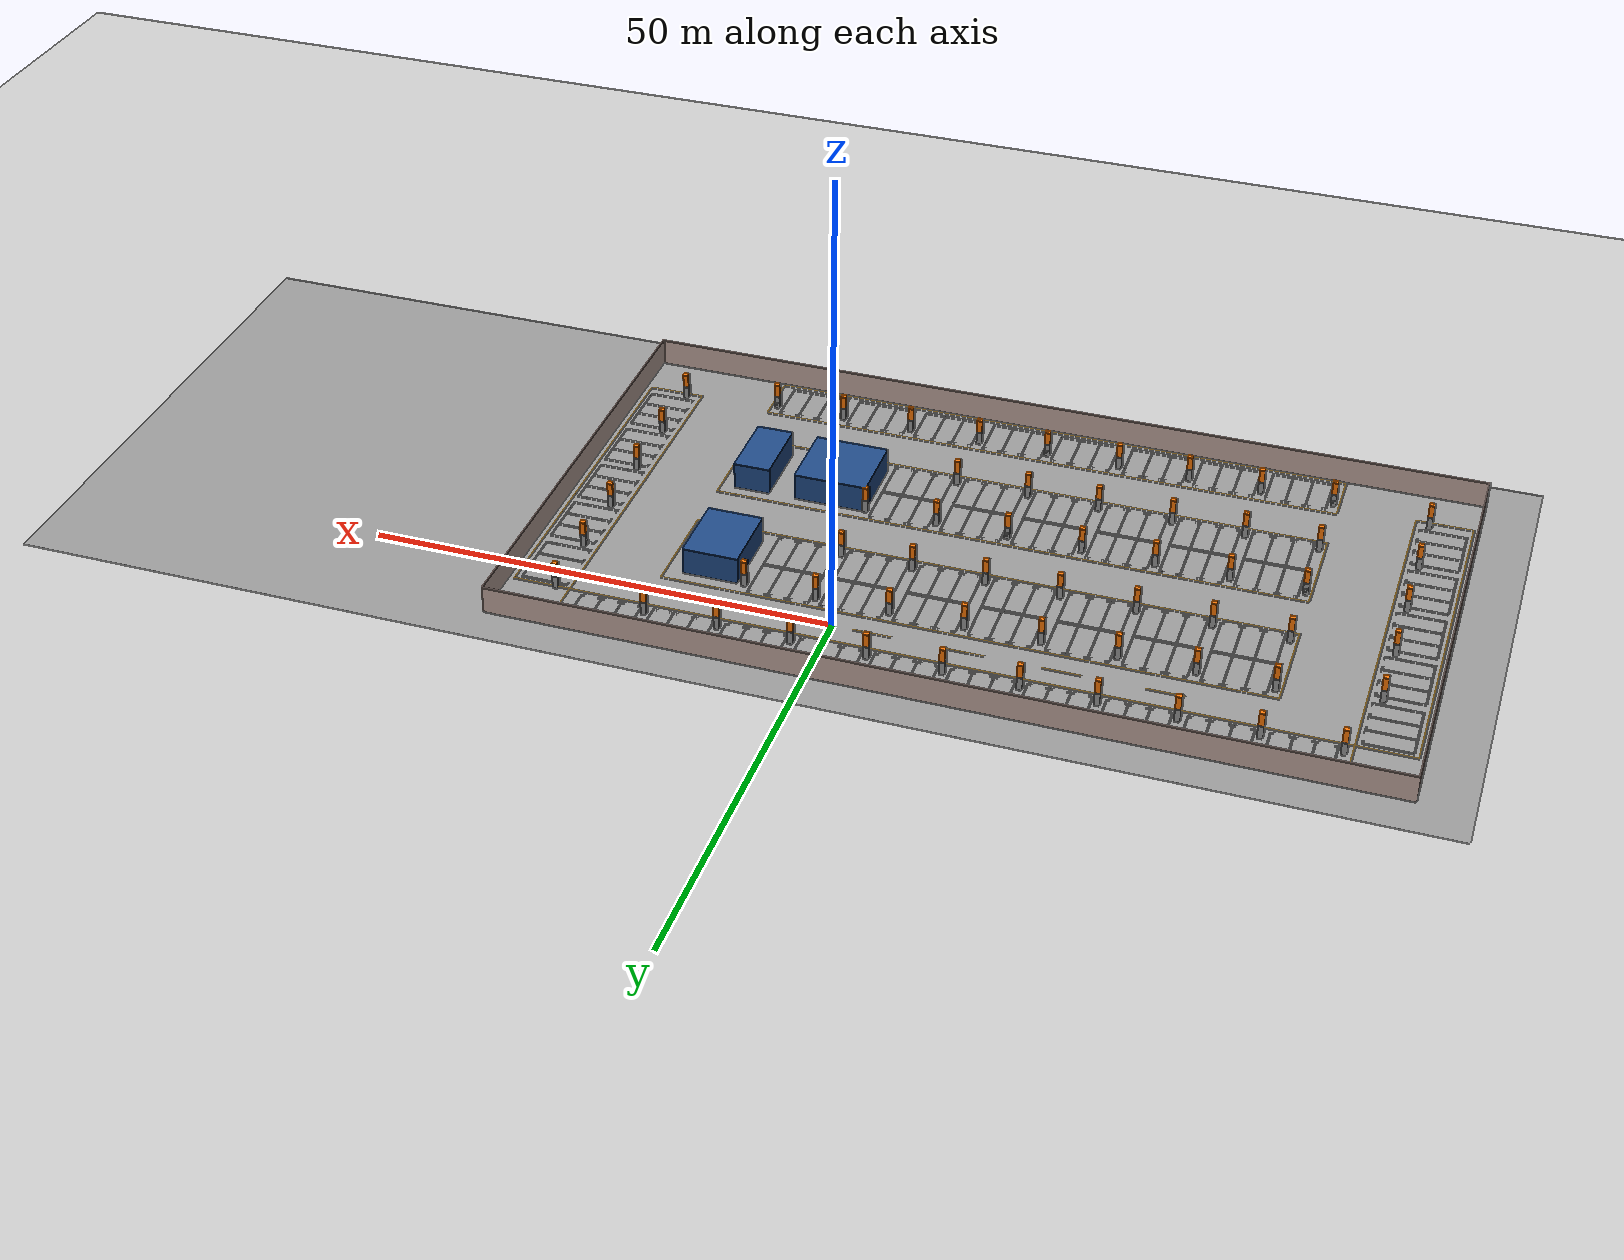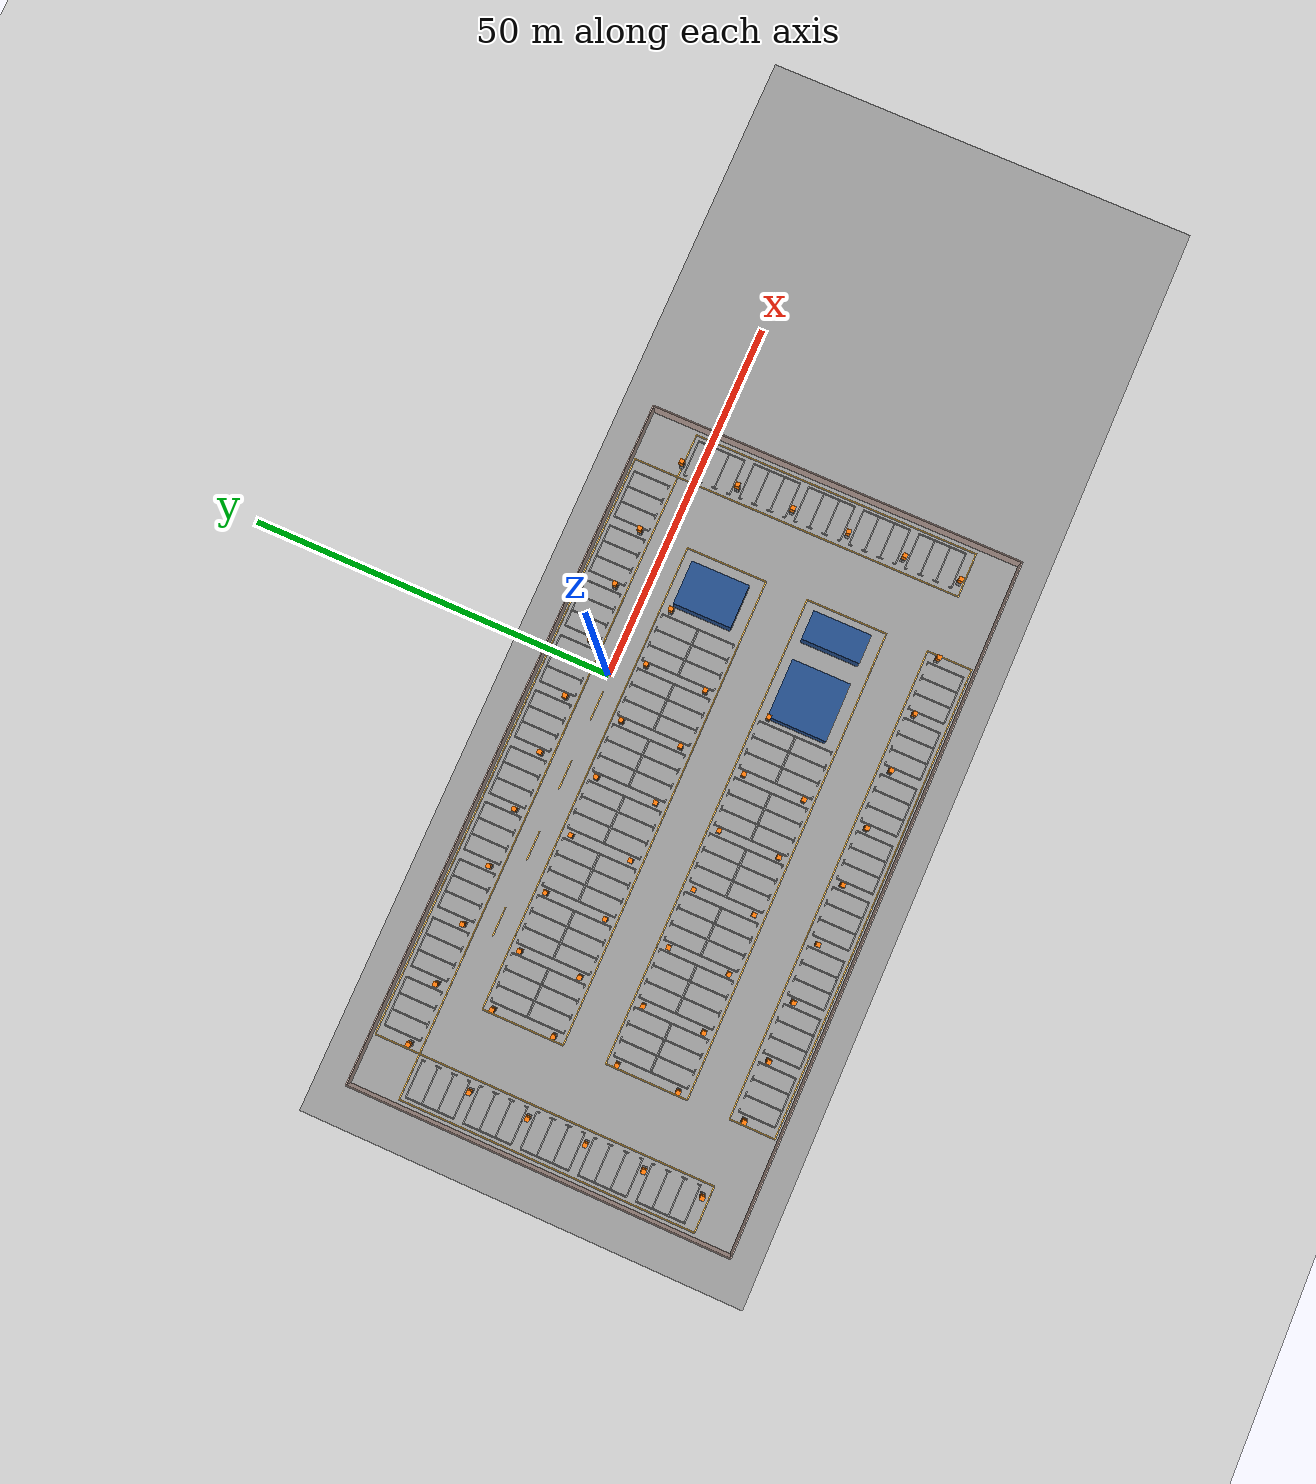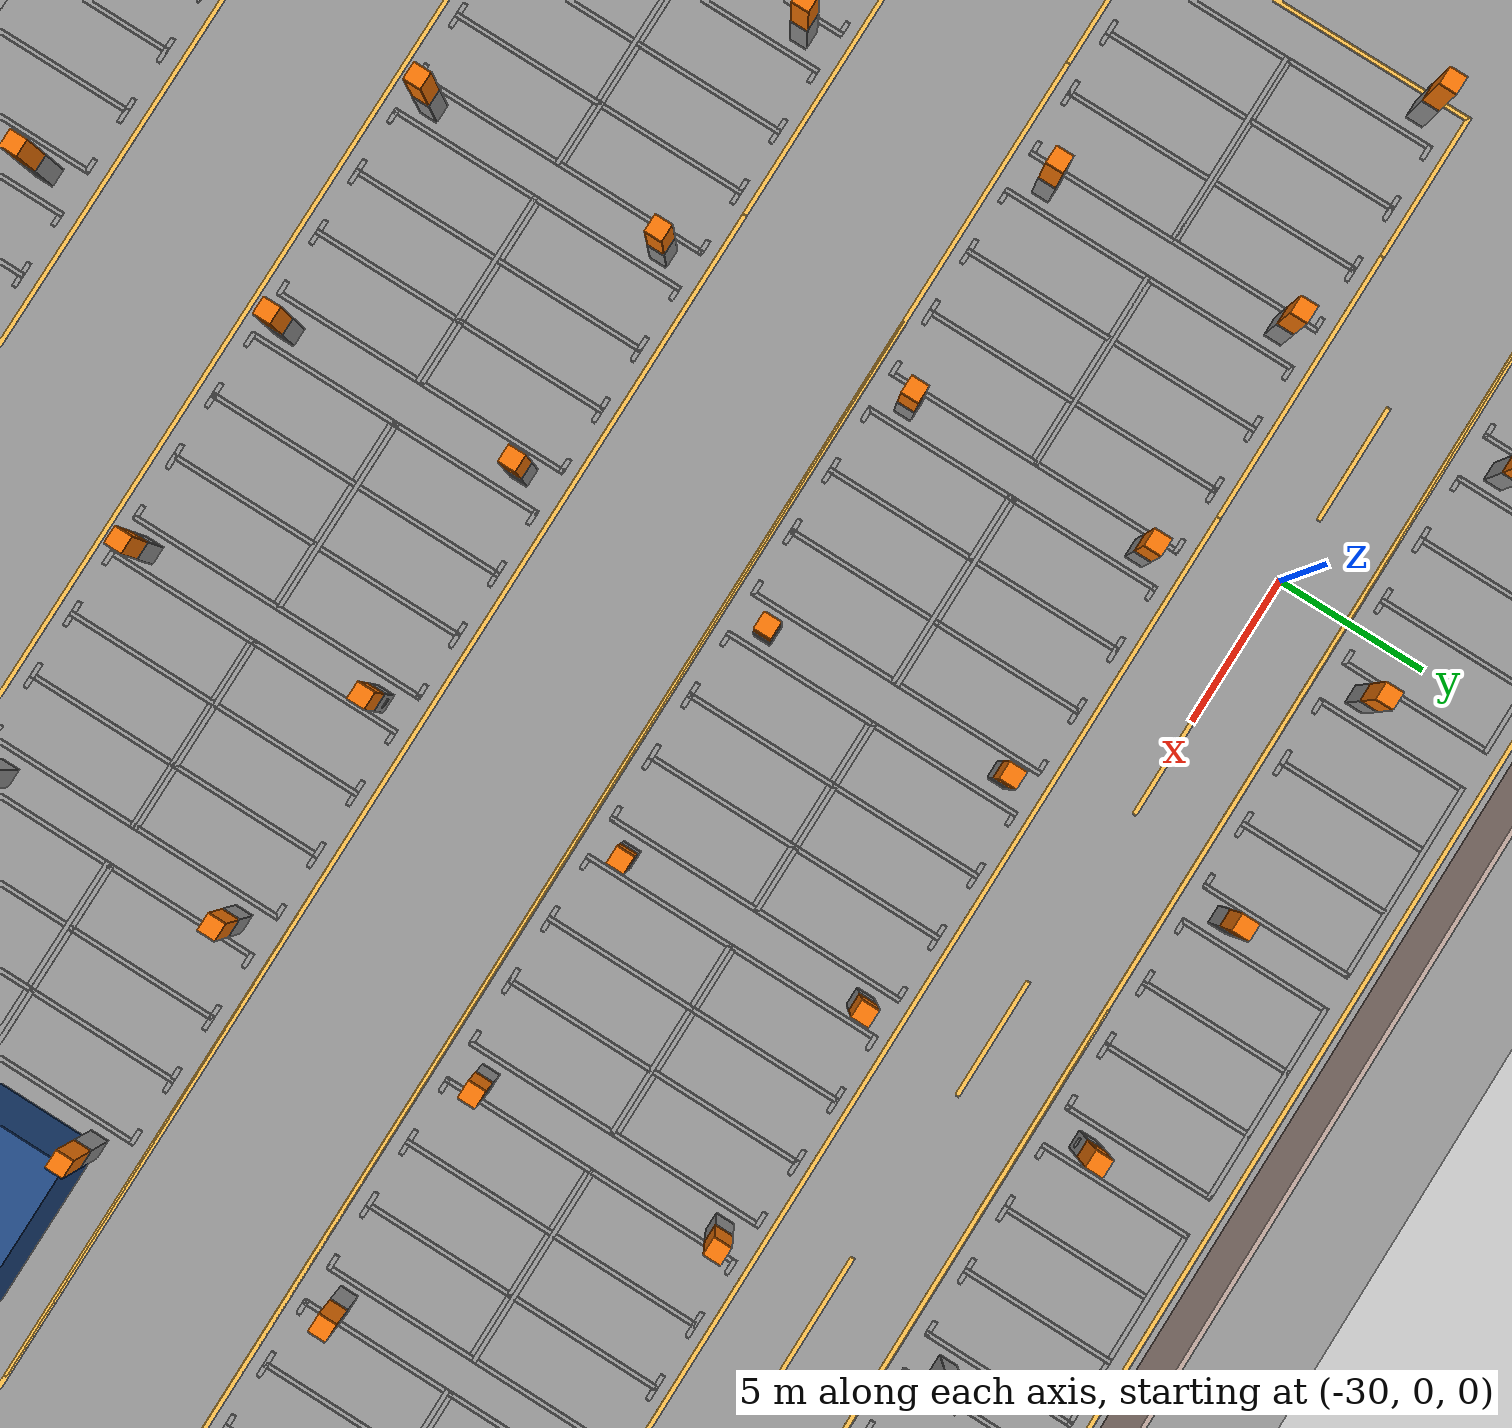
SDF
<sdf version="1.7">
 <world name="default">
  <light name="sun" type="directional">
   <pose>0 0 10 0 -0 0</pose>
   <diffuse>0.8 0.8 0.8 1</diffuse>
   <specular>0.2 0.2 0.2 1</specular>
   <attenuation>
    <range>1000</range>
    <constant>0.9</constant>
    <linear>0.01</linear>
    <quadratic>0.001</quadratic>
   </attenuation>
   <direction>-0.5 0.1 -0.9</direction>
   <spot><inner_angle>0</inner_angle><outer_angle>0</outer_angle><falloff>0</falloff></spot>
  </light>
  <model name="ground_plane">
   <static>1</static>
   <link name="link">
    <collision name="collision">
     <geometry><plane><normal>0 0 1</normal><size>100 100</size></plane></geometry>
     <surface><friction><ode><mu>100</mu><mu2>50</mu2></ode></friction></surface>
    </collision>
    <visual name="visual">
     <cast_shadows>0</cast_shadows>
     <geometry><plane><normal>0 0 1</normal><size>100 100</size></plane></geometry>
     <material>
      <script><uri>file://media/materials/scripts/gazebo.material</uri><name>Gazebo/Grey</name></script>
     </material>
    </visual>
   </link>
  </model>
  <gravity>0 0 -9.8</gravity>
  <magnetic_field>6e-06 2.3e-05 -4.2e-05</magnetic_field>
  <atmosphere type="adiabatic"/>
  <physics type="ode">
   <max_step_size>0.001</max_step_size>
   <real_time_factor>1</real_time_factor>
   <real_time_update_rate>1000</real_time_update_rate>
  </physics>
  <scene><ambient>0.4 0.4 0.4 1</ambient><background>0.7 0.7 0.7 1</background><shadows>1</shadows></scene>
  <spherical_coordinates>
   <surface_model>EARTH_WGS84</surface_model>
   <latitude_deg>0</latitude_deg>
   <longitude_deg>0</longitude_deg>
   <elevation>0</elevation>
   <heading_deg>0</heading_deg>
  </spherical_coordinates>
  <model name="carport1">
   <pose>-24.7621 7.13589 0 0 -0 0</pose>
   <link name="Wall_105">
    <collision name="Wall_105_Collision">
     <geometry><box><size>0.61 0.6 1.5</size></box></geometry>
     <pose>0 0 0.75 0 -0 0</pose>
    </collision>
    <visual name="Wall_105_Visual">
     <pose>0 0 0.75 0 -0 0</pose>
     <geometry><box><size>0.61 0.6 1.5</size></box></geometry>
     <material>
      <script><uri>file://media/materials/scripts/gazebo.material</uri><name>Gazebo/Grey</name></script>
      <ambient>1 1 1 1</ambient>
     </material>
     <meta><layer>0</layer></meta>
    </visual>
    <pose>-3.47407 -3.2865 0 0 -0 0</pose>
   </link>
   <link name="Wall_116">
    <collision name="Wall_116_Collision">
     <geometry><box><size>5.1 0.15 0.005</size></box></geometry>
     <pose>0 0 0.0025 0 -0 0</pose>
    </collision>
    <visual name="Wall_116_Visual">
     <pose>0 0 0.0025 0 -0 0</pose>
     <geometry><box><size>5.1 0.15 0.005</size></box></geometry>
     <material>
      <script><uri>file://media/materials/scripts/gazebo.material</uri><name>Gazebo/Grey</name></script>
      <ambient>1 1 1 1</ambient>
     </material>
     <meta><layer>0</layer></meta>
    </visual>
    <pose>-2.82307 -1.7385 0 0 -0 1.5708</pose>
   </link>
   <link name="Wall_124">
    <collision name="Wall_124_Collision">
     <geometry><box><size>5.1 0.15 0.005</size></box></geometry>
     <pose>0 0 0.0025 0 -0 0</pose>
    </collision>
    <visual name="Wall_124_Visual">
     <pose>0 0 0.0025 0 -0 0</pose>
     <geometry><box><size>5.1 0.15 0.005</size></box></geometry>
     <material>
      <script><uri>file://media/materials/scripts/gazebo.material</uri><name>Gazebo/Grey</name></script>
      <ambient>1 1 1 1</ambient>
     </material>
     <meta><layer>0</layer></meta>
    </visual>
    <pose>3.70393 -1.7305 0 0 -0 1.5708</pose>
   </link>
   <link name="Wall_146">
    <collision name="Wall_146_Collision">
     <geometry><box><size>6.67711 0.15 0.005</size></box></geometry>
     <pose>0 0 0.0025 0 -0 0</pose>
    </collision>
    <visual name="Wall_146_Visual">
     <pose>0 0 0.0025 0 -0 0</pose>
     <geometry><box><size>6.67711 0.15 0.005</size></box></geometry>
     <material>
      <script><uri>file://media/materials/scripts/gazebo.material</uri><name>Gazebo/Grey</name></script>
      <ambient>1 1 1 1</ambient>
     </material>
     <meta><layer>0</layer></meta>
    </visual>
    <pose>0.440428 0.7405 0 0 -0 0.001226</pose>
   </link>
   <link name="Wall_168">
    <collision name="Wall_168_Collision">
     <geometry><box><size>5.1 0.15 0.005</size></box></geometry>
     <pose>0 0 0.0025 0 -0 0</pose>
    </collision>
    <visual name="Wall_168_Visual">
     <pose>0 0 0.0025 0 -0 0</pose>
     <geometry><box><size>5.1 0.15 0.005</size></box></geometry>
     <material>
      <script><uri>file://media/materials/scripts/gazebo.material</uri><name>Gazebo/Grey</name></script>
      <ambient>1 1 1 1</ambient>
     </material>
     <meta><layer>0</layer></meta>
    </visual>
    <pose>-0.64827 -1.73839 0 0 -0 1.57088</pose>
   </link>
   <link name="Wall_173">
    <collision name="Wall_173_Collision">
     <geometry><box><size>5.1 0.15 0.005</size></box></geometry>
     <pose>0 0 0.0025 0 -0 0</pose>
    </collision>
    <visual name="Wall_173_Visual">
     <pose>0 0 0.0025 0 -0 0</pose>
     <geometry><box><size>5.1 0.15 0.005</size></box></geometry>
     <material>
      <script><uri>file://media/materials/scripts/gazebo.material</uri><name>Gazebo/Grey</name></script>
      <ambient>1 1 1 1</ambient>
     </material>
     <meta><layer>0</layer></meta>
    </visual>
    <pose>1.52673 -1.73839 0 0 -0 1.57088</pose>
   </link>
   <link name="Wall_177">
    <collision name="Wall_177_Collision">
     <geometry><box><size>0.6 0.59 3</size></box></geometry>
     <pose>0 0 1.5 0 -0 0</pose>
    </collision>
    <visual name="Wall_177_Visual">
     <pose>0 0 1.5 0 -0 0</pose>
     <geometry><box><size>0.6 0.59 3</size></box></geometry>
     <material>
      <script><uri>file://media/materials/scripts/gazebo.material</uri><name>Gazebo/Grey</name></script>
      <ambient>0.996078 0.47451 0.0196078 1</ambient>
     </material>
     <meta><layer>0</layer></meta>
    </visual>
    <pose>-3.47407 -3.2865 0 0 -0 0</pose>
   </link>
   <link name="Wall_179">
    <collision name="Wall_179_Collision">
     <geometry><box><size>0.5 0.15 0.005</size></box></geometry>
     <pose>0 0 0.0025 0 -0 0</pose>
    </collision>
    <visual name="Wall_179_Visual">
     <pose>0 0 0.0025 0 -0 0</pose>
     <geometry><box><size>0.5 0.15 0.005</size></box></geometry>
     <material>
      <script><uri>file://media/materials/scripts/gazebo.material</uri><name>Gazebo/Grey</name></script>
      <ambient>1 1 1 1</ambient>
     </material>
     <meta><layer>0</layer></meta>
    </visual>
    <pose>-2.64807 -4.2135 0 0 -0 0</pose>
   </link>
   <link name="Wall_181">
    <collision name="Wall_181_Collision">
     <geometry><box><size>0.5 0.15 0.005</size></box></geometry>
     <pose>0 0 0.0025 0 -0 0</pose>
    </collision>
    <visual name="Wall_181_Visual">
     <pose>0 0 0.0025 0 -0 0</pose>
     <geometry><box><size>0.5 0.15 0.005</size></box></geometry>
     <material>
      <script><uri>file://media/materials/scripts/gazebo.material</uri><name>Gazebo/Grey</name></script>
      <ambient>1 1 1 1</ambient>
     </material>
     <meta><layer>0</layer></meta>
    </visual>
    <pose>-0.823072 -4.2135 0 0 -0 3.14159</pose>
   </link>
   <link name="Wall_183">
    <collision name="Wall_183_Collision">
     <geometry><box><size>0.5 0.15 0.005</size></box></geometry>
     <pose>0 0 0.0025 0 -0 0</pose>
    </collision>
    <visual name="Wall_183_Visual">
     <pose>0 0 0.0025 0 -0 0</pose>
     <geometry><box><size>0.5 0.15 0.005</size></box></geometry>
     <material>
      <script><uri>file://media/materials/scripts/gazebo.material</uri><name>Gazebo/Grey</name></script>
      <ambient>1 1 1 1</ambient>
     </material>
     <meta><layer>0</layer></meta>
    </visual>
    <pose>-0.473072 -4.2135 0 0 -0 0</pose>
   </link>
   <link name="Wall_185">
    <collision name="Wall_185_Collision">
     <geometry><box><size>0.5 0.15 0.005</size></box></geometry>
     <pose>0 0 0.0025 0 -0 0</pose>
    </collision>
    <visual name="Wall_185_Visual">
     <pose>0 0 0.0025 0 -0 0</pose>
     <geometry><box><size>0.5 0.15 0.005</size></box></geometry>
     <material>
      <script><uri>file://media/materials/scripts/gazebo.material</uri><name>Gazebo/Grey</name></script>
      <ambient>1 1 1 1</ambient>
     </material>
     <meta><layer>0</layer></meta>
    </visual>
    <pose>1.35193 -4.2135 0 0 -0 3.14159</pose>
   </link>
   <link name="Wall_187">
    <collision name="Wall_187_Collision">
     <geometry><box><size>0.5 0.15 0.005</size></box></geometry>
     <pose>0 0 0.0025 0 -0 0</pose>
    </collision>
    <visual name="Wall_187_Visual">
     <pose>0 0 0.0025 0 -0 0</pose>
     <geometry><box><size>0.5 0.15 0.005</size></box></geometry>
     <material>
      <script><uri>file://media/materials/scripts/gazebo.material</uri><name>Gazebo/Grey</name></script>
      <ambient>1 1 1 1</ambient>
     </material>
     <meta><layer>0</layer></meta>
    </visual>
    <pose>1.70193 -4.2135 0 0 -0 0</pose>
   </link>
   <link name="Wall_189">
    <collision name="Wall_189_Collision">
     <geometry><box><size>0.5 0.15 0.005</size></box></geometry>
     <pose>0 0 0.0025 0 -0 0</pose>
    </collision>
    <visual name="Wall_189_Visual">
     <pose>0 0 0.0025 0 -0 0</pose>
     <geometry><box><size>0.5 0.15 0.005</size></box></geometry>
     <material>
      <script><uri>file://media/materials/scripts/gazebo.material</uri><name>Gazebo/Grey</name></script>
      <ambient>1 1 1 1</ambient>
     </material>
     <meta><layer>0</layer></meta>
    </visual>
    <pose>3.52893 -4.2055 0 0 -0 3.14159</pose>
   </link>
   <static>1</static>
  </model>
  <model name="carport1_0">
   <pose>-17.0144 7.13604 0 0 -0 0</pose>
   <link name="Wall_105">
    <collision name="Wall_105_Collision">
     <geometry><box><size>0.61 0.6 1.5</size></box></geometry>
     <pose>0 0 0.75 0 -0 0</pose>
    </collision>
    <visual name="Wall_105_Visual">
     <pose>0 0 0.75 0 -0 0</pose>
     <geometry><box><size>0.61 0.6 1.5</size></box></geometry>
     <material>
      <script><uri>file://media/materials/scripts/gazebo.material</uri><name>Gazebo/Grey</name></script>
      <ambient>1 1 1 1</ambient>
     </material>
     <meta><layer>0</layer></meta>
    </visual>
    <pose>-3.47407 -3.2865 0 0 -0 0</pose>
   </link>
   <link name="Wall_116">
    <collision name="Wall_116_Collision">
     <geometry><box><size>5.1 0.15 0.005</size></box></geometry>
     <pose>0 0 0.0025 0 -0 0</pose>
    </collision>
    <visual name="Wall_116_Visual">
     <pose>0 0 0.0025 0 -0 0</pose>
     <geometry><box><size>5.1 0.15 0.005</size></box></geometry>
     <material>
      <script><uri>file://media/materials/scripts/gazebo.material</uri><name>Gazebo/Grey</name></script>
      <ambient>1 1 1 1</ambient>
     </material>
     <meta><layer>0</layer></meta>
    </visual>
    <pose>-2.82307 -1.7385 0 0 -0 1.5708</pose>
   </link>
   <link name="Wall_124">
    <collision name="Wall_124_Collision">
     <geometry><box><size>5.1 0.15 0.005</size></box></geometry>
     <pose>0 0 0.0025 0 -0 0</pose>
    </collision>
    <visual name="Wall_124_Visual">
     <pose>0 0 0.0025 0 -0 0</pose>
     <geometry><box><size>5.1 0.15 0.005</size></box></geometry>
     <material>
      <script><uri>file://media/materials/scripts/gazebo.material</uri><name>Gazebo/Grey</name></script>
      <ambient>1 1 1 1</ambient>
     </material>
     <meta><layer>0</layer></meta>
    </visual>
    <pose>3.70393 -1.7305 0 0 -0 1.5708</pose>
   </link>
   <link name="Wall_146">
    <collision name="Wall_146_Collision">
     <geometry><box><size>6.67711 0.15 0.005</size></box></geometry>
     <pose>0 0 0.0025 0 -0 0</pose>
    </collision>
    <visual name="Wall_146_Visual">
     <pose>0 0 0.0025 0 -0 0</pose>
     <geometry><box><size>6.67711 0.15 0.005</size></box></geometry>
     <material>
      <script><uri>file://media/materials/scripts/gazebo.material</uri><name>Gazebo/Grey</name></script>
      <ambient>1 1 1 1</ambient>
     </material>
     <meta><layer>0</layer></meta>
    </visual>
    <pose>0.440428 0.7405 0 0 -0 0.001226</pose>
   </link>
   <link name="Wall_168">
    <collision name="Wall_168_Collision">
     <geometry><box><size>5.1 0.15 0.005</size></box></geometry>
     <pose>0 0 0.0025 0 -0 0</pose>
    </collision>
    <visual name="Wall_168_Visual">
     <pose>0 0 0.0025 0 -0 0</pose>
     <geometry><box><size>5.1 0.15 0.005</size></box></geometry>
     <material>
      <script><uri>file://media/materials/scripts/gazebo.material</uri><name>Gazebo/Grey</name></script>
      <ambient>1 1 1 1</ambient>
     </material>
     <meta><layer>0</layer></meta>
    </visual>
    <pose>-0.64827 -1.73839 0 0 -0 1.57088</pose>
   </link>
   <link name="Wall_173">
    <collision name="Wall_173_Collision">
     <geometry><box><size>5.1 0.15 0.005</size></box></geometry>
     <pose>0 0 0.0025 0 -0 0</pose>
    </collision>
    <visual name="Wall_173_Visual">
     <pose>0 0 0.0025 0 -0 0</pose>
     <geometry><box><size>5.1 0.15 0.005</size></box></geometry>
     <material>
      <script><uri>file://media/materials/scripts/gazebo.material</uri><name>Gazebo/Grey</name></script>
      <ambient>1 1 1 1</ambient>
     </material>
     <meta><layer>0</layer></meta>
    </visual>
    <pose>1.52673 -1.73839 0 0 -0 1.57088</pose>
   </link>
   <link name="Wall_177">
    <collision name="Wall_177_Collision">
     <geometry><box><size>0.6 0.59 3</size></box></geometry>
     <pose>0 0 1.5 0 -0 0</pose>
    </collision>
    <visual name="Wall_177_Visual">
     <pose>0 0 1.5 0 -0 0</pose>
     <geometry><box><size>0.6 0.59 3</size></box></geometry>
     <material>
      <script><uri>file://media/materials/scripts/gazebo.material</uri><name>Gazebo/Grey</name></script>
      <ambient>0.996078 0.47451 0.0196078 1</ambient>
     </material>
     <meta><layer>0</layer></meta>
    </visual>
    <pose>-3.47407 -3.2865 0 0 -0 0</pose>
   </link>
   <link name="Wall_179">
    <collision name="Wall_179_Collision">
     <geometry><box><size>0.5 0.15 0.005</size></box></geometry>
     <pose>0 0 0.0025 0 -0 0</pose>
    </collision>
    <visual name="Wall_179_Visual">
     <pose>0 0 0.0025 0 -0 0</pose>
     <geometry><box><size>0.5 0.15 0.005</size></box></geometry>
     <material>
      <script><uri>file://media/materials/scripts/gazebo.material</uri><name>Gazebo/Grey</name></script>
      <ambient>1 1 1 1</ambient>
     </material>
     <meta><layer>0</layer></meta>
    </visual>
    <pose>-2.64807 -4.2135 0 0 -0 0</pose>
   </link>
   <link name="Wall_181">
    <collision name="Wall_181_Collision">
     <geometry><box><size>0.5 0.15 0.005</size></box></geometry>
     <pose>0 0 0.0025 0 -0 0</pose>
    </collision>
    <visual name="Wall_181_Visual">
     <pose>0 0 0.0025 0 -0 0</pose>
     <geometry><box><size>0.5 0.15 0.005</size></box></geometry>
     <material>
      <script><uri>file://media/materials/scripts/gazebo.material</uri><name>Gazebo/Grey</name></script>
      <ambient>1 1 1 1</ambient>
     </material>
     <meta><layer>0</layer></meta>
    </visual>
    <pose>-0.823072 -4.2135 0 0 -0 3.14159</pose>
   </link>
   <link name="Wall_183">
    <collision name="Wall_183_Collision">
     <geometry><box><size>0.5 0.15 0.005</size></box></geometry>
     <pose>0 0 0.0025 0 -0 0</pose>
    </collision>
    <visual name="Wall_183_Visual">
     <pose>0 0 0.0025 0 -0 0</pose>
     <geometry><box><size>0.5 0.15 0.005</size></box></geometry>
     <material>
      <script><uri>file://media/materials/scripts/gazebo.material</uri><name>Gazebo/Grey</name></script>
      <ambient>1 1 1 1</ambient>
     </material>
     <meta><layer>0</layer></meta>
    </visual>
    <pose>-0.473072 -4.2135 0 0 -0 0</pose>
   </link>
   <link name="Wall_185">
    <collision name="Wall_185_Collision">
     <geometry><box><size>0.5 0.15 0.005</size></box></geometry>
     <pose>0 0 0.0025 0 -0 0</pose>
    </collision>
    <visual name="Wall_185_Visual">
     <pose>0 0 0.0025 0 -0 0</pose>
     <geometry><box><size>0.5 0.15 0.005</size></box></geometry>
     <material>
      <script><uri>file://media/materials/scripts/gazebo.material</uri><name>Gazebo/Grey</name></script>
      <ambient>1 1 1 1</ambient>
     </material>
     <meta><layer>0</layer></meta>
    </visual>
    <pose>1.35193 -4.2135 0 0 -0 3.14159</pose>
   </link>
   <link name="Wall_187">
    <collision name="Wall_187_Collision">
     <geometry><box><size>0.5 0.15 0.005</size></box></geometry>
     <pose>0 0 0.0025 0 -0 0</pose>
    </collision>
    <visual name="Wall_187_Visual">
     <pose>0 0 0.0025 0 -0 0</pose>
     <geometry><box><size>0.5 0.15 0.005</size></box></geometry>
     <material>
      <script><uri>file://media/materials/scripts/gazebo.material</uri><name>Gazebo/Grey</name></script>
      <ambient>1 1 1 1</ambient>
     </material>
     <meta><layer>0</layer></meta>
    </visual>
    <pose>1.70193 -4.2135 0 0 -0 0</pose>
   </link>
   <link name="Wall_189">
    <collision name="Wall_189_Collision">
     <geometry><box><size>0.5 0.15 0.005</size></box></geometry>
     <pose>0 0 0.0025 0 -0 0</pose>
    </collision>
    <visual name="Wall_189_Visual">
     <pose>0 0 0.0025 0 -0 0</pose>
     <geometry><box><size>0.5 0.15 0.005</size></box></geometry>
     <material>
      <script><uri>file://media/materials/scripts/gazebo.material</uri><name>Gazebo/Grey</name></script>
      <ambient>1 1 1 1</ambient>
     </material>
     <meta><layer>0</layer></meta>
    </visual>
    <pose>3.52893 -4.2055 0 0 -0 3.14159</pose>
   </link>
   <static>1</static>
  </model>
  <model name="carport1_1">
   <pose>-9.16243 7.15338 0 0 -0 0</pose>
   <link name="Wall_105">
    <collision name="Wall_105_Collision">
     <geometry><box><size>0.61 0.6 1.5</size></box></geometry>
     <pose>0 0 0.75 0 -0 0</pose>
    </collision>
    <visual name="Wall_105_Visual">
     <pose>0 0 0.75 0 -0 0</pose>
     <geometry><box><size>0.61 0.6 1.5</size></box></geometry>
     <material>
      <script><uri>file://media/materials/scripts/gazebo.material</uri><name>Gazebo/Grey</name></script>
      <ambient>1 1 1 1</ambient>
     </material>
     <meta><layer>0</layer></meta>
    </visual>
    <pose>-3.47407 -3.2865 0 0 -0 0</pose>
   </link>
   <link name="Wall_116">
    <collision name="Wall_116_Collision">
     <geometry><box><size>5.1 0.15 0.005</size></box></geometry>
     <pose>0 0 0.0025 0 -0 0</pose>
    </collision>
    <visual name="Wall_116_Visual">
     <pose>0 0 0.0025 0 -0 0</pose>
     <geometry><box><size>5.1 0.15 0.005</size></box></geometry>
     <material>
      <script><uri>file://media/materials/scripts/gazebo.material</uri><name>Gazebo/Grey</name></script>
      <ambient>1 1 1 1</ambient>
     </material>
     <meta><layer>0</layer></meta>
    </visual>
    <pose>-2.82307 -1.7385 0 0 -0 1.5708</pose>
   </link>
   <link name="Wall_124">
    <collision name="Wall_124_Collision">
     <geometry><box><size>5.1 0.15 0.005</size></box></geometry>
     <pose>0 0 0.0025 0 -0 0</pose>
    </collision>
    <visual name="Wall_124_Visual">
     <pose>0 0 0.0025 0 -0 0</pose>
     <geometry><box><size>5.1 0.15 0.005</size></box></geometry>
     <material>
      <script><uri>file://media/materials/scripts/gazebo.material</uri><name>Gazebo/Grey</name></script>
      <ambient>1 1 1 1</ambient>
     </material>
     <meta><layer>0</layer></meta>
    </visual>
    <pose>3.70393 -1.7305 0 0 -0 1.5708</pose>
   </link>
   <link name="Wall_146">
    <collision name="Wall_146_Collision">
     <geometry><box><size>6.67711 0.15 0.005</size></box></geometry>
     <pose>0 0 0.0025 0 -0 0</pose>
    </collision>
    <visual name="Wall_146_Visual">
     <pose>0 0 0.0025 0 -0 0</pose>
     <geometry><box><size>6.67711 0.15 0.005</size></box></geometry>
     <material>
      <script><uri>file://media/materials/scripts/gazebo.material</uri><name>Gazebo/Grey</name></script>
      <ambient>1 1 1 1</ambient>
     </material>
     <meta><layer>0</layer></meta>
    </visual>
    <pose>0.440428 0.7405 0 0 -0 0.001226</pose>
   </link>
   <link name="Wall_168">
    <collision name="Wall_168_Collision">
     <geometry><box><size>5.1 0.15 0.005</size></box></geometry>
     <pose>0 0 0.0025 0 -0 0</pose>
    </collision>
    <visual name="Wall_168_Visual">
     <pose>0 0 0.0025 0 -0 0</pose>
     <geometry><box><size>5.1 0.15 0.005</size></box></geometry>
     <material>
      <script><uri>file://media/materials/scripts/gazebo.material</uri><name>Gazebo/Grey</name></script>
      <ambient>1 1 1 1</ambient>
     </material>
     <meta><layer>0</layer></meta>
    </visual>
    <pose>-0.64827 -1.73839 0 0 -0 1.57088</pose>
   </link>
   <link name="Wall_173">
    <collision name="Wall_173_Collision">
     <geometry><box><size>5.1 0.15 0.005</size></box></geometry>
     <pose>0 0 0.0025 0 -0 0</pose>
    </collision>
    <visual name="Wall_173_Visual">
     <pose>0 0 0.0025 0 -0 0</pose>
     <geometry><box><size>5.1 0.15 0.005</size></box></geometry>
     <material>
      <script><uri>file://media/materials/scripts/gazebo.material</uri><name>Gazebo/Grey</name></script>
      <ambient>1 1 1 1</ambient>
     </material>
     <meta><layer>0</layer></meta>
    </visual>
    <pose>1.52673 -1.73839 0 0 -0 1.57088</pose>
   </link>
   <link name="Wall_177">
    <collision name="Wall_177_Collision">
     <geometry><box><size>0.6 0.59 3</size></box></geometry>
     <pose>0 0 1.5 0 -0 0</pose>
    </collision>
    <visual name="Wall_177_Visual">
     <pose>0 0 1.5 0 -0 0</pose>
     <geometry><box><size>0.6 0.59 3</size></box></geometry>
     <material>
      <script><uri>file://media/materials/scripts/gazebo.material</uri><name>Gazebo/Grey</name></script>
      <ambient>0.996078 0.47451 0.0196078 1</ambient>
     </material>
     <meta><layer>0</layer></meta>
    </visual>
    <pose>-3.47407 -3.2865 0 0 -0 0</pose>
   </link>
   <link name="Wall_179">
    <collision name="Wall_179_Collision">
     <geometry><box><size>0.5 0.15 0.005</size></box></geometry>
     <pose>0 0 0.0025 0 -0 0</pose>
    </collision>
    <visual name="Wall_179_Visual">
     <pose>0 0 0.0025 0 -0 0</pose>
     <geometry><box><size>0.5 0.15 0.005</size></box></geometry>
     <material>
      <script><uri>file://media/materials/scripts/gazebo.material</uri><name>Gazebo/Grey</name></script>
      <ambient>1 1 1 1</ambient>
     </material>
     <meta><layer>0</layer></meta>
    </visual>
    <pose>-2.64807 -4.2135 0 0 -0 0</pose>
   </link>
   <link name="Wall_181">
    <collision name="Wall_181_Collision">
     <geometry><box><size>0.5 0.15 0.005</size></box></geometry>
     <pose>0 0 0.0025 0 -0 0</pose>
    </collision>
    <visual name="Wall_181_Visual">
     <pose>0 0 0.0025 0 -0 0</pose>
     <geometry><box><size>0.5 0.15 0.005</size></box></geometry>
     <material>
      <script><uri>file://media/materials/scripts/gazebo.material</uri><name>Gazebo/Grey</name></script>
      <ambient>1 1 1 1</ambient>
     </material>
     <meta><layer>0</layer></meta>
    </visual>
    <pose>-0.823072 -4.2135 0 0 -0 3.14159</pose>
   </link>
   <link name="Wall_183">
    <collision name="Wall_183_Collision">
     <geometry><box><size>0.5 0.15 0.005</size></box></geometry>
     <pose>0 0 0.0025 0 -0 0</pose>
    </collision>
    <visual name="Wall_183_Visual">
     <pose>0 0 0.0025 0 -0 0</pose>
     <geometry><box><size>0.5 0.15 0.005</size></box></geometry>
     <material>
      <script><uri>file://media/materials/scripts/gazebo.material</uri><name>Gazebo/Grey</name></script>
      <ambient>1 1 1 1</ambient>
     </material>
     <meta><layer>0</layer></meta>
    </visual>
    <pose>-0.473072 -4.2135 0 0 -0 0</pose>
   </link>
   <link name="Wall_185">
    <collision name="Wall_185_Collision">
     <geometry><box><size>0.5 0.15 0.005</size></box></geometry>
     <pose>0 0 0.0025 0 -0 0</pose>
    </collision>
    <visual name="Wall_185_Visual">
     <pose>0 0 0.0025 0 -0 0</pose>
     <geometry><box><size>0.5 0.15 0.005</size></box></geometry>
     <material>
      <script><uri>file://media/materials/scripts/gazebo.material</uri><name>Gazebo/Grey</name></script>
      <ambient>1 1 1 1</ambient>
     </material>
     <meta><layer>0</layer></meta>
    </visual>
    <pose>1.35193 -4.2135 0 0 -0 3.14159</pose>
   </link>
   <link name="Wall_187">
    <collision name="Wall_187_Collision">
     <geometry><box><size>0.5 0.15 0.005</size></box></geometry>
     <pose>0 0 0.0025 0 -0 0</pose>
    </collision>
    <visual name="Wall_187_Visual">
     <pose>0 0 0.0025 0 -0 0</pose>
     <geometry><box><size>0.5 0.15 0.005</size></box></geometry>
     <material>
      <script><uri>file://media/materials/scripts/gazebo.material</uri><name>Gazebo/Grey</name></script>
      <ambient>1 1 1 1</ambient>
     </material>
     <meta><layer>0</layer></meta>
    </visual>
    <pose>1.70193 -4.2135 0 0 -0 0</pose>
   </link>
   <link name="Wall_189">
    <collision name="Wall_189_Collision">
     <geometry><box><size>0.5 0.15 0.005</size></box></geometry>
     <pose>0 0 0.0025 0 -0 0</pose>
    </collision>
    <visual name="Wall_189_Visual">
     <pose>0 0 0.0025 0 -0 0</pose>
     <geometry><box><size>0.5 0.15 0.005</size></box></geometry>
     <material>
      <script><uri>file://media/materials/scripts/gazebo.material</uri><name>Gazebo/Grey</name></script>
      <ambient>1 1 1 1</ambient>
     </material>
     <meta><layer>0</layer></meta>
    </visual>
    <pose>3.52893 -4.2055 0 0 -0 3.14159</pose>
   </link>
   <static>1</static>
  </model>
  <model name="carport1_2">
   <pose>-1.3548 7.15384 0 0 -0 0</pose>
   <link name="Wall_105">
    <collision name="Wall_105_Collision">
     <geometry><box><size>0.61 0.6 1.5</size></box></geometry>
     <pose>0 0 0.75 0 -0 0</pose>
    </collision>
    <visual name="Wall_105_Visual">
     <pose>0 0 0.75 0 -0 0</pose>
     <geometry><box><size>0.61 0.6 1.5</size></box></geometry>
     <material>
      <script><uri>file://media/materials/scripts/gazebo.material</uri><name>Gazebo/Grey</name></script>
      <ambient>1 1 1 1</ambient>
     </material>
     <meta><layer>0</layer></meta>
    </visual>
    <pose>-3.47407 -3.2865 0 0 -0 0</pose>
   </link>
   <link name="Wall_116">
    <collision name="Wall_116_Collision">
     <geometry><box><size>5.1 0.15 0.005</size></box></geometry>
     <pose>0 0 0.0025 0 -0 0</pose>
    </collision>
    <visual name="Wall_116_Visual">
     <pose>0 0 0.0025 0 -0 0</pose>
     <geometry><box><size>5.1 0.15 0.005</size></box></geometry>
     <material>
      <script><uri>file://media/materials/scripts/gazebo.material</uri><name>Gazebo/Grey</name></script>
      <ambient>1 1 1 1</ambient>
     </material>
     <meta><layer>0</layer></meta>
    </visual>
    <pose>-2.82307 -1.7385 0 0 -0 1.5708</pose>
   </link>
   <link name="Wall_124">
    <collision name="Wall_124_Collision">
     <geometry><box><size>5.1 0.15 0.005</size></box></geometry>
     <pose>0 0 0.0025 0 -0 0</pose>
    </collision>
    <visual name="Wall_124_Visual">
     <pose>0 0 0.0025 0 -0 0</pose>
     <geometry><box><size>5.1 0.15 0.005</size></box></geometry>
     <material>
      <script><uri>file://media/materials/scripts/gazebo.material</uri><name>Gazebo/Grey</name></script>
      <ambient>1 1 1 1</ambient>
     </material>
     <meta><layer>0</layer></meta>
    </visual>
    <pose>3.70393 -1.7305 0 0 -0 1.5708</pose>
   </link>
   <link name="Wall_146">
    <collision name="Wall_146_Collision">
     <geometry><box><size>6.67711 0.15 0.005</size></box></geometry>
     <pose>0 0 0.0025 0 -0 0</pose>
    </collision>
    <visual name="Wall_146_Visual">
     <pose>0 0 0.0025 0 -0 0</pose>
     <geometry><box><size>6.67711 0.15 0.005</size></box></geometry>
     <material>
      <script><uri>file://media/materials/scripts/gazebo.material</uri><name>Gazebo/Grey</name></script>
      <ambient>1 1 1 1</ambient>
     </material>
     <meta><layer>0</layer></meta>
    </visual>
    <pose>0.440428 0.7405 0 0 -0 0.001226</pose>
   </link>
   <link name="Wall_168">
    <collision name="Wall_168_Collision">
     <geometry><box><size>5.1 0.15 0.005</size></box></geometry>
     <pose>0 0 0.0025 0 -0 0</pose>
    </collision>
    <visual name="Wall_168_Visual">
     <pose>0 0 0.0025 0 -0 0</pose>
     <geometry><box><size>5.1 0.15 0.005</size></box></geometry>
     <material>
      <script><uri>file://media/materials/scripts/gazebo.material</uri><name>Gazebo/Grey</name></script>
      <ambient>1 1 1 1</ambient>
     </material>
     <meta><layer>0</layer></meta>
    </visual>
    <pose>-0.64827 -1.73839 0 0 -0 1.57088</pose>
   </link>
   <link name="Wall_173">
    <collision name="Wall_173_Collision">
     <geometry><box><size>5.1 0.15 0.005</size></box></geometry>
     <pose>0 0 0.0025 0 -0 0</pose>
    </collision>
    <visual name="Wall_173_Visual">
     <pose>0 0 0.0025 0 -0 0</pose>
     <geometry><box><size>5.1 0.15 0.005</size></box></geometry>
     <material>
      <script><uri>file://media/materials/scripts/gazebo.material</uri><name>Gazebo/Grey</name></script>
      <ambient>1 1 1 1</ambient>
     </material>
     <meta><layer>0</layer></meta>
    </visual>
    <pose>1.52673 -1.73839 0 0 -0 1.57088</pose>
   </link>
   <link name="Wall_177">
    <collision name="Wall_177_Collision">
     <geometry><box><size>0.6 0.59 3</size></box></geometry>
     <pose>0 0 1.5 0 -0 0</pose>
    </collision>
    <visual name="Wall_177_Visual">
     <pose>0 0 1.5 0 -0 0</pose>
     <geometry><box><size>0.6 0.59 3</size></box></geometry>
     <material>
      <script><uri>file://media/materials/scripts/gazebo.material</uri><name>Gazebo/Grey</name></script>
      <ambient>0.996078 0.47451 0.0196078 1</ambient>
     </material>
     <meta><layer>0</layer></meta>
    </visual>
    <pose>-3.47407 -3.2865 0 0 -0 0</pose>
   </link>
   <link name="Wall_179">
    <collision name="Wall_179_Collision">
     <geometry><box><size>0.5 0.15 0.005</size></box></geometry>
     <pose>0 0 0.0025 0 -0 0</pose>
    </collision>
    <visual name="Wall_179_Visual">
     <pose>0 0 0.0025 0 -0 0</pose>
     <geometry><box><size>0.5 0.15 0.005</size></box></geometry>
     <material>
      <script><uri>file://media/materials/scripts/gazebo.material</uri><name>Gazebo/Grey</name></script>
      <ambient>1 1 1 1</ambient>
     </material>
     <meta><layer>0</layer></meta>
    </visual>
    <pose>-2.64807 -4.2135 0 0 -0 0</pose>
   </link>
   <link name="Wall_181">
    <collision name="Wall_181_Collision">
     <geometry><box><size>0.5 0.15 0.005</size></box></geometry>
     <pose>0 0 0.0025 0 -0 0</pose>
    </collision>
    <visual name="Wall_181_Visual">
     <pose>0 0 0.0025 0 -0 0</pose>
     <geometry><box><size>0.5 0.15 0.005</size></box></geometry>
     <material>
      <script><uri>file://media/materials/scripts/gazebo.material</uri><name>Gazebo/Grey</name></script>
      <ambient>1 1 1 1</ambient>
     </material>
     <meta><layer>0</layer></meta>
    </visual>
    <pose>-0.823072 -4.2135 0 0 -0 3.14159</pose>
   </link>
   <link name="Wall_183">
    <collision name="Wall_183_Collision">
     <geometry><box><size>0.5 0.15 0.005</size></box></geometry>
     <pose>0 0 0.0025 0 -0 0</pose>
    </collision>
    <visual name="Wall_183_Visual">
     <pose>0 0 0.0025 0 -0 0</pose>
     <geometry><box><size>0.5 0.15 0.005</size></box></geometry>
     <material>
      <script><uri>file://media/materials/scripts/gazebo.material</uri><name>Gazebo/Grey</name></script>
      <ambient>1 1 1 1</ambient>
     </material>
     <meta><layer>0</layer></meta>
    </visual>
    <pose>-0.473072 -4.2135 0 0 -0 0</pose>
   </link>
   <link name="Wall_185">
    <collision name="Wall_185_Collision">
     <geometry><box><size>0.5 0.15 0.005</size></box></geometry>
     <pose>0 0 0.0025 0 -0 0</pose>
    </collision>
    <visual name="Wall_185_Visual">
     <pose>0 0 0.0025 0 -0 0</pose>
     <geometry><box><size>0.5 0.15 0.005</size></box></geometry>
     <material>
      <script><uri>file://media/materials/scripts/gazebo.material</uri><name>Gazebo/Grey</name></script>
      <ambient>1 1 1 1</ambient>
     </material>
     <meta><layer>0</layer></meta>
    </visual>
    <pose>1.35193 -4.2135 0 0 -0 3.14159</pose>
   </link>
   <link name="Wall_187">
    <collision name="Wall_187_Collision">
     <geometry><box><size>0.5 0.15 0.005</size></box></geometry>
     <pose>0 0 0.0025 0 -0 0</pose>
    </collision>
    <visual name="Wall_187_Visual">
     <pose>0 0 0.0025 0 -0 0</pose>
     <geometry><box><size>0.5 0.15 0.005</size></box></geometry>
     <material>
      <script><uri>file://media/materials/scripts/gazebo.material</uri><name>Gazebo/Grey</name></script>
      <ambient>1 1 1 1</ambient>
     </material>
     <meta><layer>0</layer></meta>
    </visual>
    <pose>1.70193 -4.2135 0 0 -0 0</pose>
   </link>
   <link name="Wall_189">
    <collision name="Wall_189_Collision">
     <geometry><box><size>0.5 0.15 0.005</size></box></geometry>
     <pose>0 0 0.0025 0 -0 0</pose>
    </collision>
    <visual name="Wall_189_Visual">
     <pose>0 0 0.0025 0 -0 0</pose>
     <geometry><box><size>0.5 0.15 0.005</size></box></geometry>
     <material>
      <script><uri>file://media/materials/scripts/gazebo.material</uri><name>Gazebo/Grey</name></script>
      <ambient>1 1 1 1</ambient>
     </material>
     <meta><layer>0</layer></meta>
    </visual>
    <pose>3.52893 -4.2055 0 0 -0 3.14159</pose>
   </link>
   <static>1</static>
  </model>
  <model name="carport1_3">
   <pose>-32.65 7.14013 0 0 -0 0</pose>
   <link name="Wall_105">
    <collision name="Wall_105_Collision">
     <geometry><box><size>0.61 0.6 1.5</size></box></geometry>
     <pose>0 0 0.75 0 -0 0</pose>
    </collision>
    <visual name="Wall_105_Visual">
     <pose>0 0 0.75 0 -0 0</pose>
     <geometry><box><size>0.61 0.6 1.5</size></box></geometry>
     <material>
      <script><uri>file://media/materials/scripts/gazebo.material</uri><name>Gazebo/Grey</name></script>
      <ambient>1 1 1 1</ambient>
     </material>
     <meta><layer>0</layer></meta>
    </visual>
    <pose>-3.47407 -3.2865 0 0 -0 0</pose>
   </link>
   <link name="Wall_116">
    <collision name="Wall_116_Collision">
     <geometry><box><size>5.1 0.15 0.005</size></box></geometry>
     <pose>0 0 0.0025 0 -0 0</pose>
    </collision>
    <visual name="Wall_116_Visual">
     <pose>0 0 0.0025 0 -0 0</pose>
     <geometry><box><size>5.1 0.15 0.005</size></box></geometry>
     <material>
      <script><uri>file://media/materials/scripts/gazebo.material</uri><name>Gazebo/Grey</name></script>
      <ambient>1 1 1 1</ambient>
     </material>
     <meta><layer>0</layer></meta>
    </visual>
    <pose>-2.82307 -1.7385 0 0 -0 1.5708</pose>
   </link>
   <link name="Wall_124">
    <collision name="Wall_124_Collision">
     <geometry><box><size>5.1 0.15 0.005</size></box></geometry>
     <pose>0 0 0.0025 0 -0 0</pose>
    </collision>
    <visual name="Wall_124_Visual">
     <pose>0 0 0.0025 0 -0 0</pose>
     <geometry><box><size>5.1 0.15 0.005</size></box></geometry>
     <material>
      <script><uri>file://media/materials/scripts/gazebo.material</uri><name>Gazebo/Grey</name></script>
      <ambient>1 1 1 1</ambient>
     </material>
     <meta><layer>0</layer></meta>
    </visual>
    <pose>3.70393 -1.7305 0 0 -0 1.5708</pose>
   </link>
   <link name="Wall_146">
    <collision name="Wall_146_Collision">
     <geometry><box><size>6.67711 0.15 0.005</size></box></geometry>
     <pose>0 0 0.0025 0 -0 0</pose>
    </collision>
    <visual name="Wall_146_Visual">
     <pose>0 0 0.0025 0 -0 0</pose>
     <geometry><box><size>6.67711 0.15 0.005</size></box></geometry>
     <material>
      <script><uri>file://media/materials/scripts/gazebo.material</uri><name>Gazebo/Grey</name></script>
      <ambient>1 1 1 1</ambient>
     </material>
     <meta><layer>0</layer></meta>
    </visual>
    <pose>0.440428 0.7405 0 0 -0 0.001226</pose>
   </link>
   <link name="Wall_168">
    <collision name="Wall_168_Collision">
     <geometry><box><size>5.1 0.15 0.005</size></box></geometry>
     <pose>0 0 0.0025 0 -0 0</pose>
    </collision>
    <visual name="Wall_168_Visual">
     <pose>0 0 0.0025 0 -0 0</pose>
     <geometry><box><size>5.1 0.15 0.005</size></box></geometry>
     <material>
      <script><uri>file://media/materials/scripts/gazebo.material</uri><name>Gazebo/Grey</name></script>
      <ambient>1 1 1 1</ambient>
     </material>
     <meta><layer>0</layer></meta>
    </visual>
    <pose>-0.64827 -1.73839 0 0 -0 1.57088</pose>
   </link>
   <link name="Wall_173">
    <collision name="Wall_173_Collision">
     <geometry><box><size>5.1 0.15 0.005</size></box></geometry>
     <pose>0 0 0.0025 0 -0 0</pose>
    </collision>
    <visual name="Wall_173_Visual">
     <pose>0 0 0.0025 0 -0 0</pose>
     <geometry><box><size>5.1 0.15 0.005</size></box></geometry>
     <material>
      <script><uri>file://media/materials/scripts/gazebo.material</uri><name>Gazebo/Grey</name></script>
      <ambient>1 1 1 1</ambient>
     </material>
     <meta><layer>0</layer></meta>
    </visual>
    <pose>1.52673 -1.73839 0 0 -0 1.57088</pose>
   </link>
   <link name="Wall_177">
    <collision name="Wall_177_Collision">
     <geometry><box><size>0.6 0.59 3</size></box></geometry>
     <pose>0 0 1.5 0 -0 0</pose>
    </collision>
    <visual name="Wall_177_Visual">
     <pose>0 0 1.5 0 -0 0</pose>
     <geometry><box><size>0.6 0.59 3</size></box></geometry>
     <material>
      <script><uri>file://media/materials/scripts/gazebo.material</uri><name>Gazebo/Grey</name></script>
      <ambient>0.996078 0.47451 0.0196078 1</ambient>
     </material>
     <meta><layer>0</layer></meta>
    </visual>
    <pose>-3.47407 -3.2865 0 0 -0 0</pose>
   </link>
   <link name="Wall_179">
    <collision name="Wall_179_Collision">
     <geometry><box><size>0.5 0.15 0.005</size></box></geometry>
     <pose>0 0 0.0025 0 -0 0</pose>
    </collision>
    <visual name="Wall_179_Visual">
     <pose>0 0 0.0025 0 -0 0</pose>
     <geometry><box><size>0.5 0.15 0.005</size></box></geometry>
     <material>
      <script><uri>file://media/materials/scripts/gazebo.material</uri><name>Gazebo/Grey</name></script>
      <ambient>1 1 1 1</ambient>
     </material>
     <meta><layer>0</layer></meta>
    </visual>
    <pose>-2.64807 -4.2135 0 0 -0 0</pose>
   </link>
   <link name="Wall_181">
    <collision name="Wall_181_Collision">
     <geometry><box><size>0.5 0.15 0.005</size></box></geometry>
     <pose>0 0 0.0025 0 -0 0</pose>
    </collision>
    <visual name="Wall_181_Visual">
     <pose>0 0 0.0025 0 -0 0</pose>
     <geometry><box><size>0.5 0.15 0.005</size></box></geometry>
     <material>
      <script><uri>file://media/materials/scripts/gazebo.material</uri><name>Gazebo/Grey</name></script>
      <ambient>1 1 1 1</ambient>
     </material>
     <meta><layer>0</layer></meta>
    </visual>
    <pose>-0.823072 -4.2135 0 0 -0 3.14159</pose>
   </link>
   <link name="Wall_183">
    <collision name="Wall_183_Collision">
     <geometry><box><size>0.5 0.15 0.005</size></box></geometry>
     <pose>0 0 0.0025 0 -0 0</pose>
    </collision>
    <visual name="Wall_183_Visual">
     <pose>0 0 0.0025 0 -0 0</pose>
     <geometry><box><size>0.5 0.15 0.005</size></box></geometry>
     <material>
      <script><uri>file://media/materials/scripts/gazebo.material</uri><name>Gazebo/Grey</name></script>
      <ambient>1 1 1 1</ambient>
     </material>
     <meta><layer>0</layer></meta>
    </visual>
    <pose>-0.473072 -4.2135 0 0 -0 0</pose>
   </link>
   <link name="Wall_185">
    <collision name="Wall_185_Collision">
     <geometry><box><size>0.5 0.15 0.005</size></box></geometry>
     <pose>0 0 0.0025 0 -0 0</pose>
    </collision>
    <visual name="Wall_185_Visual">
     <pose>0 0 0.0025 0 -0 0</pose>
     <geometry><box><size>0.5 0.15 0.005</size></box></geometry>
     <material>
      <script><uri>file://media/materials/scripts/gazebo.material</uri><name>Gazebo/Grey</name></script>
      <ambient>1 1 1 1</ambient>
     </material>
     <meta><layer>0</layer></meta>
    </visual>
    <pose>1.35193 -4.2135 0 0 -0 3.14159</pose>
   </link>
   <link name="Wall_187">
    <collision name="Wall_187_Collision">
     <geometry><box><size>0.5 0.15 0.005</size></box></geometry>
     <pose>0 0 0.0025 0 -0 0</pose>
    </collision>
    <visual name="Wall_187_Visual">
     <pose>0 0 0.0025 0 -0 0</pose>
     <geometry><box><size>0.5 0.15 0.005</size></box></geometry>
     <material>
      <script><uri>file://media/materials/scripts/gazebo.material</uri><name>Gazebo/Grey</name></script>
      <ambient>1 1 1 1</ambient>
     </material>
     <meta><layer>0</layer></meta>
    </visual>
    <pose>1.70193 -4.2135 0 0 -0 0</pose>
   </link>
   <link name="Wall_189">
    <collision name="Wall_189_Collision">
     <geometry><box><size>0.5 0.15 0.005</size></box></geometry>
     <pose>0 0 0.0025 0 -0 0</pose>
    </collision>
    <visual name="Wall_189_Visual">
     <pose>0 0 0.0025 0 -0 0</pose>
     <geometry><box><size>0.5 0.15 0.005</size></box></geometry>
     <material>
      <script><uri>file://media/materials/scripts/gazebo.material</uri><name>Gazebo/Grey</name></script>
      <ambient>1 1 1 1</ambient>
     </material>
     <meta><layer>0</layer></meta>
    </visual>
    <pose>3.52893 -4.2055 0 0 -0 3.14159</pose>
   </link>
   <static>1</static>
  </model>
  <model name="carport1_4">
   <pose>-31.9117 -7.30915 0 0 -0 3.14141</pose>
   <link name="Wall_105">
    <collision name="Wall_105_Collision">
     <geometry><box><size>0.61 0.6 1.5</size></box></geometry>
     <pose>0 0 0.75 0 -0 0</pose>
    </collision>
    <visual name="Wall_105_Visual">
     <pose>0 0 0.75 0 -0 0</pose>
     <geometry><box><size>0.61 0.6 1.5</size></box></geometry>
     <material>
      <script><uri>file://media/materials/scripts/gazebo.material</uri><name>Gazebo/Grey</name></script>
      <ambient>1 1 1 1</ambient>
     </material>
     <meta><layer>0</layer></meta>
    </visual>
    <pose>-3.47407 -3.2865 0 0 -0 0</pose>
   </link>
   <link name="Wall_116">
    <collision name="Wall_116_Collision">
     <geometry><box><size>5.1 0.15 0.005</size></box></geometry>
     <pose>0 0 0.0025 0 -0 0</pose>
    </collision>
    <visual name="Wall_116_Visual">
     <pose>0 0 0.0025 0 -0 0</pose>
     <geometry><box><size>5.1 0.15 0.005</size></box></geometry>
     <material>
      <script><uri>file://media/materials/scripts/gazebo.material</uri><name>Gazebo/Grey</name></script>
      <ambient>1 1 1 1</ambient>
     </material>
     <meta><layer>0</layer></meta>
    </visual>
    <pose>-2.82307 -1.7385 0 0 -0 1.5708</pose>
   </link>
   <link name="Wall_124">
    <collision name="Wall_124_Collision">
     <geometry><box><size>5.1 0.15 0.005</size></box></geometry>
     <pose>0 0 0.0025 0 -0 0</pose>
    </collision>
    <visual name="Wall_124_Visual">
     <pose>0 0 0.0025 0 -0 0</pose>
     <geometry><box><size>5.1 0.15 0.005</size></box></geometry>
     <material>
      <script><uri>file://media/materials/scripts/gazebo.material</uri><name>Gazebo/Grey</name></script>
      <ambient>1 1 1 1</ambient>
     </material>
     <meta><layer>0</layer></meta>
    </visual>
    <pose>3.70393 -1.7305 0 0 -0 1.5708</pose>
   </link>
   <link name="Wall_146">
    <collision name="Wall_146_Collision">
     <geometry><box><size>6.67711 0.15 0.005</size></box></geometry>
     <pose>0 0 0.0025 0 -0 0</pose>
    </collision>
    <visual name="Wall_146_Visual">
     <pose>0 0 0.0025 0 -0 0</pose>
     <geometry><box><size>6.67711 0.15 0.005</size></box></geometry>
     <material>
      <script><uri>file://media/materials/scripts/gazebo.material</uri><name>Gazebo/Grey</name></script>
      <ambient>1 1 1 1</ambient>
     </material>
     <meta><layer>0</layer></meta>
    </visual>
    <pose>0.440428 0.7405 0 0 -0 0.001226</pose>
   </link>
   <link name="Wall_168">
    <collision name="Wall_168_Collision">
     <geometry><box><size>5.1 0.15 0.005</size></box></geometry>
     <pose>0 0 0.0025 0 -0 0</pose>
    </collision>
    <visual name="Wall_168_Visual">
     <pose>0 0 0.0025 0 -0 0</pose>
     <geometry><box><size>5.1 0.15 0.005</size></box></geometry>
     <material>
      <script><uri>file://media/materials/scripts/gazebo.material</uri><name>Gazebo/Grey</name></script>
      <ambient>1 1 1 1</ambient>
     </material>
     <meta><layer>0</layer></meta>
    </visual>
    <pose>-0.64827 -1.73839 0 0 -0 1.57088</pose>
   </link>
   <link name="Wall_173">
    <collision name="Wall_173_Collision">
     <geometry><box><size>5.1 0.15 0.005</size></box></geometry>
     <pose>0 0 0.0025 0 -0 0</pose>
    </collision>
    <visual name="Wall_173_Visual">
     <pose>0 0 0.0025 0 -0 0</pose>
     <geometry><box><size>5.1 0.15 0.005</size></box></geometry>
     <material>
      <script><uri>file://media/materials/scripts/gazebo.material</uri><name>Gazebo/Grey</name></script>
      <ambient>1 1 1 1</ambient>
     </material>
     <meta><layer>0</layer></meta>
    </visual>
    <pose>1.52673 -1.73839 0 0 -0 1.57088</pose>
   </link>
   <link name="Wall_177">
    <collision name="Wall_177_Collision">
     <geometry><box><size>0.6 0.59 3</size></box></geometry>
     <pose>0 0 1.5 0 -0 0</pose>
    </collision>
    <visual name="Wall_177_Visual">
     <pose>0 0 1.5 0 -0 0</pose>
     <geometry><box><size>0.6 0.59 3</size></box></geometry>
     <material>
      <script><uri>file://media/materials/scripts/gazebo.material</uri><name>Gazebo/Grey</name></script>
      <ambient>0.996078 0.47451 0.0196078 1</ambient>
     </material>
     <meta><layer>0</layer></meta>
    </visual>
    <pose>-3.47407 -3.2865 0 0 -0 0</pose>
   </link>
   <link name="Wall_179">
    <collision name="Wall_179_Collision">
     <geometry><box><size>0.5 0.15 0.005</size></box></geometry>
     <pose>0 0 0.0025 0 -0 0</pose>
    </collision>
    <visual name="Wall_179_Visual">
     <pose>0 0 0.0025 0 -0 0</pose>
     <geometry><box><size>0.5 0.15 0.005</size></box></geometry>
     <material>
      <script><uri>file://media/materials/scripts/gazebo.material</uri><name>Gazebo/Grey</name></script>
      <ambient>1 1 1 1</ambient>
     </material>
     <meta><layer>0</layer></meta>
    </visual>
    <pose>-2.64807 -4.2135 0 0 -0 0</pose>
   </link>
   <link name="Wall_181">
    <collision name="Wall_181_Collision">
     <geometry><box><size>0.5 0.15 0.005</size></box></geometry>
     <pose>0 0 0.0025 0 -0 0</pose>
    </collision>
    <visual name="Wall_181_Visual">
     <pose>0 0 0.0025 0 -0 0</pose>
     <geometry><box><size>0.5 0.15 0.005</size></box></geometry>
     <material>
      <script><uri>file://media/materials/scripts/gazebo.material</uri><name>Gazebo/Grey</name></script>
      <ambient>1 1 1 1</ambient>
     </material>
     <meta><layer>0</layer></meta>
    </visual>
    <pose>-0.823072 -4.2135 0 0 -0 3.14159</pose>
   </link>
   <link name="Wall_183">
    <collision name="Wall_183_Collision">
     <geometry><box><size>0.5 0.15 0.005</size></box></geometry>
     <pose>0 0 0.0025 0 -0 0</pose>
    </collision>
    <visual name="Wall_183_Visual">
     <pose>0 0 0.0025 0 -0 0</pose>
     <geometry><box><size>0.5 0.15 0.005</size></box></geometry>
     <material>
      <script><uri>file://media/materials/scripts/gazebo.material</uri><name>Gazebo/Grey</name></script>
      <ambient>1 1 1 1</ambient>
     </material>
     <meta><layer>0</layer></meta>
    </visual>
    <pose>-0.473072 -4.2135 0 0 -0 0</pose>
   </link>
   <link name="Wall_185">
    <collision name="Wall_185_Collision">
     <geometry><box><size>0.5 0.15 0.005</size></box></geometry>
     <pose>0 0 0.0025 0 -0 0</pose>
    </collision>
    <visual name="Wall_185_Visual">
     <pose>0 0 0.0025 0 -0 0</pose>
     <geometry><box><size>0.5 0.15 0.005</size></box></geometry>
     <material>
      <script><uri>file://media/materials/scripts/gazebo.material</uri><name>Gazebo/Grey</name></script>
      <ambient>1 1 1 1</ambient>
     </material>
     <meta><layer>0</layer></meta>
    </visual>
    <pose>1.35193 -4.2135 0 0 -0 3.14159</pose>
   </link>
   <link name="Wall_187">
    <collision name="Wall_187_Collision">
     <geometry><box><size>0.5 0.15 0.005</size></box></geometry>
     <pose>0 0 0.0025 0 -0 0</pose>
    </collision>
    <visual name="Wall_187_Visual">
     <pose>0 0 0.0025 0 -0 0</pose>
     <geometry><box><size>0.5 0.15 0.005</size></box></geometry>
     <material>
      <script><uri>file://media/materials/scripts/gazebo.material</uri><name>Gazebo/Grey</name></script>
      <ambient>1 1 1 1</ambient>
     </material>
     <meta><layer>0</layer></meta>
    </visual>
    <pose>1.70193 -4.2135 0 0 -0 0</pose>
   </link>
   <link name="Wall_189">
    <collision name="Wall_189_Collision">
     <geometry><box><size>0.5 0.15 0.005</size></box></geometry>
     <pose>0 0 0.0025 0 -0 0</pose>
    </collision>
    <visual name="Wall_189_Visual">
     <pose>0 0 0.0025 0 -0 0</pose>
     <geometry><box><size>0.5 0.15 0.005</size></box></geometry>
     <material>
      <script><uri>file://media/materials/scripts/gazebo.material</uri><name>Gazebo/Grey</name></script>
      <ambient>1 1 1 1</ambient>
     </material>
     <meta><layer>0</layer></meta>
    </visual>
    <pose>3.52893 -4.2055 0 0 -0 3.14159</pose>
   </link>
   <static>1</static>
  </model>
  <model name="carport1_4_clone">
   <pose>-24.0979 -7.28317 0 0 -0 3.14141</pose>
   <link name="Wall_105">
    <collision name="Wall_105_Collision">
     <geometry><box><size>0.61 0.6 1.5</size></box></geometry>
     <pose>0 0 0.75 0 -0 0</pose>
    </collision>
    <visual name="Wall_105_Visual">
     <pose>0 0 0.75 0 -0 0</pose>
     <geometry><box><size>0.61 0.6 1.5</size></box></geometry>
     <material>
      <script><uri>file://media/materials/scripts/gazebo.material</uri><name>Gazebo/Grey</name></script>
      <ambient>1 1 1 1</ambient>
     </material>
     <meta><layer>0</layer></meta>
    </visual>
    <pose>-3.47407 -3.2865 0 0 -0 0</pose>
   </link>
   <link name="Wall_116">
    <collision name="Wall_116_Collision">
     <geometry><box><size>5.1 0.15 0.005</size></box></geometry>
     <pose>0 0 0.0025 0 -0 0</pose>
    </collision>
    <visual name="Wall_116_Visual">
     <pose>0 0 0.0025 0 -0 0</pose>
     <geometry><box><size>5.1 0.15 0.005</size></box></geometry>
     <material>
      <script><uri>file://media/materials/scripts/gazebo.material</uri><name>Gazebo/Grey</name></script>
      <ambient>1 1 1 1</ambient>
     </material>
     <meta><layer>0</layer></meta>
    </visual>
    <pose>-2.82307 -1.7385 0 0 -0 1.5708</pose>
   </link>
   <link name="Wall_124">
    <collision name="Wall_124_Collision">
     <geometry><box><size>5.1 0.15 0.005</size></box></geometry>
     <pose>0 0 0.0025 0 -0 0</pose>
    </collision>
    <visual name="Wall_124_Visual">
     <pose>0 0 0.0025 0 -0 0</pose>
     <geometry><box><size>5.1 0.15 0.005</size></box></geometry>
     <material>
      <script><uri>file://media/materials/scripts/gazebo.material</uri><name>Gazebo/Grey</name></script>
      <ambient>1 1 1 1</ambient>
     </material>
     <meta><layer>0</layer></meta>
    </visual>
    <pose>3.70393 -1.7305 0 0 -0 1.5708</pose>
   </link>
   <link name="Wall_146">
    <collision name="Wall_146_Collision">
     <geometry><box><size>6.67711 0.15 0.005</size></box></geometry>
     <pose>0 0 0.0025 0 -0 0</pose>
    </collision>
    <visual name="Wall_146_Visual">
     <pose>0 0 0.0025 0 -0 0</pose>
     <geometry><box><size>6.67711 0.15 0.005</size></box></geometry>
     <material>
      <script><uri>file://media/materials/scripts/gazebo.material</uri><name>Gazebo/Grey</name></script>
      <ambient>1 1 1 1</ambient>
     </material>
     <meta><layer>0</layer></meta>
    </visual>
    <pose>0.440428 0.7405 0 0 -0 0.001226</pose>
   </link>
   <link name="Wall_168">
    <collision name="Wall_168_Collision">
     <geometry><box><size>5.1 0.15 0.005</size></box></geometry>
     <pose>0 0 0.0025 0 -0 0</pose>
    </collision>
    <visual name="Wall_168_Visual">
     <pose>0 0 0.0025 0 -0 0</pose>
     <geometry><box><size>5.1 0.15 0.005</size></box></geometry>
     <material>
      <script><uri>file://media/materials/scripts/gazebo.material</uri><name>Gazebo/Grey</name></script>
      <ambient>1 1 1 1</ambient>
     </material>
     <meta><layer>0</layer></meta>
    </visual>
    <pose>-0.64827 -1.73839 0 0 -0 1.57088</pose>
   </link>
   <link name="Wall_173">
    <collision name="Wall_173_Collision">
     <geometry><box><size>5.1 0.15 0.005</size></box></geometry>
     <pose>0 0 0.0025 0 -0 0</pose>
    </collision>
    <visual name="Wall_173_Visual">
     <pose>0 0 0.0025 0 -0 0</pose>
     <geometry><box><size>5.1 0.15 0.005</size></box></geometry>
     <material>
      <script><uri>file://media/materials/scripts/gazebo.material</uri><name>Gazebo/Grey</name></script>
      <ambient>1 1 1 1</ambient>
     </material>
     <meta><layer>0</layer></meta>
    </visual>
    <pose>1.52673 -1.73839 0 0 -0 1.57088</pose>
   </link>
   <link name="Wall_177">
    <collision name="Wall_177_Collision">
     <geometry><box><size>0.6 0.59 3</size></box></geometry>
     <pose>0 0 1.5 0 -0 0</pose>
    </collision>
    <visual name="Wall_177_Visual">
     <pose>0 0 1.5 0 -0 0</pose>
     <geometry><box><size>0.6 0.59 3</size></box></geometry>
     <material>
      <script><uri>file://media/materials/scripts/gazebo.material</uri><name>Gazebo/Grey</name></script>
      <ambient>0.996078 0.47451 0.0196078 1</ambient>
     </material>
     <meta><layer>0</layer></meta>
    </visual>
    <pose>-3.47407 -3.2865 0 0 -0 0</pose>
   </link>
   <link name="Wall_179">
    <collision name="Wall_179_Collision">
     <geometry><box><size>0.5 0.15 0.005</size></box></geometry>
     <pose>0 0 0.0025 0 -0 0</pose>
    </collision>
    <visual name="Wall_179_Visual">
     <pose>0 0 0.0025 0 -0 0</pose>
     <geometry><box><size>0.5 0.15 0.005</size></box></geometry>
     <material>
      <script><uri>file://media/materials/scripts/gazebo.material</uri><name>Gazebo/Grey</name></script>
      <ambient>1 1 1 1</ambient>
     </material>
     <meta><layer>0</layer></meta>
    </visual>
    <pose>-2.64807 -4.2135 0 0 -0 0</pose>
   </link>
   <link name="Wall_181">
    <collision name="Wall_181_Collision">
     <geometry><box><size>0.5 0.15 0.005</size></box></geometry>
     <pose>0 0 0.0025 0 -0 0</pose>
    </collision>
    <visual name="Wall_181_Visual">
     <pose>0 0 0.0025 0 -0 0</pose>
     <geometry><box><size>0.5 0.15 0.005</size></box></geometry>
     <material>
      <script><uri>file://media/materials/scripts/gazebo.material</uri><name>Gazebo/Grey</name></script>
      <ambient>1 1 1 1</ambient>
     </material>
     <meta><layer>0</layer></meta>
    </visual>
    <pose>-0.823072 -4.2135 0 0 -0 3.14159</pose>
   </link>
   <link name="Wall_183">
    <collision name="Wall_183_Collision">
     <geometry><box><size>0.5 0.15 0.005</size></box></geometry>
     <pose>0 0 0.0025 0 -0 0</pose>
    </collision>
    <visual name="Wall_183_Visual">
     <pose>0 0 0.0025 0 -0 0</pose>
     <geometry><box><size>0.5 0.15 0.005</size></box></geometry>
     <material>
      <script><uri>file://media/materials/scripts/gazebo.material</uri><name>Gazebo/Grey</name></script>
      <ambient>1 1 1 1</ambient>
     </material>
     <meta><layer>0</layer></meta>
    </visual>
    <pose>-0.473072 -4.2135 0 0 -0 0</pose>
   </link>
   <link name="Wall_185">
    <collision name="Wall_185_Collision">
     <geometry><box><size>0.5 0.15 0.005</size></box></geometry>
     <pose>0 0 0.0025 0 -0 0</pose>
    </collision>
    <visual name="Wall_185_Visual">
     <pose>0 0 0.0025 0 -0 0</pose>
     <geometry><box><size>0.5 0.15 0.005</size></box></geometry>
     <material>
      <script><uri>file://media/materials/scripts/gazebo.material</uri><name>Gazebo/Grey</name></script>
      <ambient>1 1 1 1</ambient>
     </material>
     <meta><layer>0</layer></meta>
    </visual>
    <pose>1.35193 -4.2135 0 0 -0 3.14159</pose>
   </link>
   <link name="Wall_187">
    <collision name="Wall_187_Collision">
     <geometry><box><size>0.5 0.15 0.005</size></box></geometry>
     <pose>0 0 0.0025 0 -0 0</pose>
    </collision>
    <visual name="Wall_187_Visual">
     <pose>0 0 0.0025 0 -0 0</pose>
     <geometry><box><size>0.5 0.15 0.005</size></box></geometry>
     <material>
      <script><uri>file://media/materials/scripts/gazebo.material</uri><name>Gazebo/Grey</name></script>
      <ambient>1 1 1 1</ambient>
     </material>
     <meta><layer>0</layer></meta>
    </visual>
    <pose>1.70193 -4.2135 0 0 -0 0</pose>
   </link>
   <link name="Wall_189">
    <collision name="Wall_189_Collision">
     <geometry><box><size>0.5 0.15 0.005</size></box></geometry>
     <pose>0 0 0.0025 0 -0 0</pose>
    </collision>
    <visual name="Wall_189_Visual">
     <pose>0 0 0.0025 0 -0 0</pose>
     <geometry><box><size>0.5 0.15 0.005</size></box></geometry>
     <material>
      <script><uri>file://media/materials/scripts/gazebo.material</uri><name>Gazebo/Grey</name></script>
      <ambient>1 1 1 1</ambient>
     </material>
     <meta><layer>0</layer></meta>
    </visual>
    <pose>3.52893 -4.2055 0 0 -0 3.14159</pose>
   </link>
   <static>1</static>
  </model>
  <model name="carport1_4_clone_0">
   <pose>-16.1561 -7.24507 0 0 -0 3.14141</pose>
   <link name="Wall_105">
    <collision name="Wall_105_Collision">
     <geometry><box><size>0.61 0.6 1.5</size></box></geometry>
     <pose>0 0 0.75 0 -0 0</pose>
    </collision>
    <visual name="Wall_105_Visual">
     <pose>0 0 0.75 0 -0 0</pose>
     <geometry><box><size>0.61 0.6 1.5</size></box></geometry>
     <material>
      <script><uri>file://media/materials/scripts/gazebo.material</uri><name>Gazebo/Grey</name></script>
      <ambient>1 1 1 1</ambient>
     </material>
     <meta><layer>0</layer></meta>
    </visual>
    <pose>-3.47407 -3.2865 0 0 -0 0</pose>
   </link>
   <link name="Wall_116">
    <collision name="Wall_116_Collision">
     <geometry><box><size>5.1 0.15 0.005</size></box></geometry>
     <pose>0 0 0.0025 0 -0 0</pose>
    </collision>
    <visual name="Wall_116_Visual">
     <pose>0 0 0.0025 0 -0 0</pose>
     <geometry><box><size>5.1 0.15 0.005</size></box></geometry>
     <material>
      <script><uri>file://media/materials/scripts/gazebo.material</uri><name>Gazebo/Grey</name></script>
      <ambient>1 1 1 1</ambient>
     </material>
     <meta><layer>0</layer></meta>
    </visual>
    <pose>-2.82307 -1.7385 0 0 -0 1.5708</pose>
   </link>
   <link name="Wall_124">
    <collision name="Wall_124_Collision">
     <geometry><box><size>5.1 0.15 0.005</size></box></geometry>
     <pose>0 0 0.0025 0 -0 0</pose>
    </collision>
    <visual name="Wall_124_Visual">
     <pose>0 0 0.0025 0 -0 0</pose>
     <geometry><box><size>5.1 0.15 0.005</size></box></geometry>
     <material>
      <script><uri>file://media/materials/scripts/gazebo.material</uri><name>Gazebo/Grey</name></script>
      <ambient>1 1 1 1</ambient>
     </material>
     <meta><layer>0</layer></meta>
    </visual>
    <pose>3.70393 -1.7305 0 0 -0 1.5708</pose>
   </link>
   <link name="Wall_146">
    <collision name="Wall_146_Collision">
     <geometry><box><size>6.67711 0.15 0.005</size></box></geometry>
     <pose>0 0 0.0025 0 -0 0</pose>
    </collision>
    <visual name="Wall_146_Visual">
     <pose>0 0 0.0025 0 -0 0</pose>
     <geometry><box><size>6.67711 0.15 0.005</size></box></geometry>
     <material>
      <script><uri>file://media/materials/scripts/gazebo.material</uri><name>Gazebo/Grey</name></script>
      <ambient>1 1 1 1</ambient>
     </material>
     <meta><layer>0</layer></meta>
    </visual>
    <pose>0.440428 0.7405 0 0 -0 0.001226</pose>
   </link>
   <link name="Wall_168">
    <collision name="Wall_168_Collision">
     <geometry><box><size>5.1 0.15 0.005</size></box></geometry>
     <pose>0 0 0.0025 0 -0 0</pose>
    </collision>
    <visual name="Wall_168_Visual">
     <pose>0 0 0.0025 0 -0 0</pose>
     <geometry><box><size>5.1 0.15 0.005</size></box></geometry>
     <material>
      <script><uri>file://media/materials/scripts/gazebo.material</uri><name>Gazebo/Grey</name></script>
      <ambient>1 1 1 1</ambient>
     </material>
     <meta><layer>0</layer></meta>
    </visual>
    <pose>-0.64827 -1.73839 0 0 -0 1.57088</pose>
   </link>
   <link name="Wall_173">
    <collision name="Wall_173_Collision">
     <geometry><box><size>5.1 0.15 0.005</size></box></geometry>
     <pose>0 0 0.0025 0 -0 0</pose>
    </collision>
    <visual name="Wall_173_Visual">
     <pose>0 0 0.0025 0 -0 0</pose>
     <geometry><box><size>5.1 0.15 0.005</size></box></geometry>
     <material>
      <script><uri>file://media/materials/scripts/gazebo.material</uri><name>Gazebo/Grey</name></script>
      <ambient>1 1 1 1</ambient>
     </material>
     <meta><layer>0</layer></meta>
    </visual>
    <pose>1.52673 -1.73839 0 0 -0 1.57088</pose>
   </link>
   <link name="Wall_177">
    <collision name="Wall_177_Collision">
     <geometry><box><size>0.6 0.59 3</size></box></geometry>
     <pose>0 0 1.5 0 -0 0</pose>
    </collision>
    <visual name="Wall_177_Visual">
     <pose>0 0 1.5 0 -0 0</pose>
     <geometry><box><size>0.6 0.59 3</size></box></geometry>
     <material>
      <script><uri>file://media/materials/scripts/gazebo.material</uri><name>Gazebo/Grey</name></script>
      <ambient>0.996078 0.47451 0.0196078 1</ambient>
     </material>
     <meta><layer>0</layer></meta>
    </visual>
    <pose>-3.47407 -3.2865 0 0 -0 0</pose>
   </link>
   <link name="Wall_179">
    <collision name="Wall_179_Collision">
     <geometry><box><size>0.5 0.15 0.005</size></box></geometry>
     <pose>0 0 0.0025 0 -0 0</pose>
    </collision>
    <visual name="Wall_179_Visual">
     <pose>0 0 0.0025 0 -0 0</pose>
     <geometry><box><size>0.5 0.15 0.005</size></box></geometry>
     <material>
      <script><uri>file://media/materials/scripts/gazebo.material</uri><name>Gazebo/Grey</name></script>
      <ambient>1 1 1 1</ambient>
     </material>
     <meta><layer>0</layer></meta>
    </visual>
    <pose>-2.64807 -4.2135 0 0 -0 0</pose>
   </link>
   <link name="Wall_181">
    <collision name="Wall_181_Collision">
     <geometry><box><size>0.5 0.15 0.005</size></box></geometry>
     <pose>0 0 0.0025 0 -0 0</pose>
    </collision>
    <visual name="Wall_181_Visual">
     <pose>0 0 0.0025 0 -0 0</pose>
     <geometry><box><size>0.5 0.15 0.005</size></box></geometry>
     <material>
      <script><uri>file://media/materials/scripts/gazebo.material</uri><name>Gazebo/Grey</name></script>
      <ambient>1 1 1 1</ambient>
     </material>
     <meta><layer>0</layer></meta>
    </visual>
    <pose>-0.823072 -4.2135 0 0 -0 3.14159</pose>
   </link>
   <link name="Wall_183">
    <collision name="Wall_183_Collision">
     <geometry><box><size>0.5 0.15 0.005</size></box></geometry>
     <pose>0 0 0.0025 0 -0 0</pose>
    </collision>
    <visual name="Wall_183_Visual">
     <pose>0 0 0.0025 0 -0 0</pose>
     <geometry><box><size>0.5 0.15 0.005</size></box></geometry>
     <material>
      <script><uri>file://media/materials/scripts/gazebo.material</uri><name>Gazebo/Grey</name></script>
      <ambient>1 1 1 1</ambient>
     </material>
     <meta><layer>0</layer></meta>
    </visual>
    <pose>-0.473072 -4.2135 0 0 -0 0</pose>
   </link>
   <link name="Wall_185">
    <collision name="Wall_185_Collision">
     <geometry><box><size>0.5 0.15 0.005</size></box></geometry>
     <pose>0 0 0.0025 0 -0 0</pose>
    </collision>
    <visual name="Wall_185_Visual">
     <pose>0 0 0.0025 0 -0 0</pose>
     <geometry><box><size>0.5 0.15 0.005</size></box></geometry>
     <material>
      <script><uri>file://media/materials/scripts/gazebo.material</uri><name>Gazebo/Grey</name></script>
      <ambient>1 1 1 1</ambient>
     </material>
     <meta><layer>0</layer></meta>
    </visual>
    <pose>1.35193 -4.2135 0 0 -0 3.14159</pose>
   </link>
   <link name="Wall_187">
    <collision name="Wall_187_Collision">
     <geometry><box><size>0.5 0.15 0.005</size></box></geometry>
     <pose>0 0 0.0025 0 -0 0</pose>
    </collision>
    <visual name="Wall_187_Visual">
     <pose>0 0 0.0025 0 -0 0</pose>
     <geometry><box><size>0.5 0.15 0.005</size></box></geometry>
     <material>
      <script><uri>file://media/materials/scripts/gazebo.material</uri><name>Gazebo/Grey</name></script>
      <ambient>1 1 1 1</ambient>
     </material>
     <meta><layer>0</layer></meta>
    </visual>
    <pose>1.70193 -4.2135 0 0 -0 0</pose>
   </link>
   <link name="Wall_189">
    <collision name="Wall_189_Collision">
     <geometry><box><size>0.5 0.15 0.005</size></box></geometry>
     <pose>0 0 0.0025 0 -0 0</pose>
    </collision>
    <visual name="Wall_189_Visual">
     <pose>0 0 0.0025 0 -0 0</pose>
     <geometry><box><size>0.5 0.15 0.005</size></box></geometry>
     <material>
      <script><uri>file://media/materials/scripts/gazebo.material</uri><name>Gazebo/Grey</name></script>
      <ambient>1 1 1 1</ambient>
     </material>
     <meta><layer>0</layer></meta>
    </visual>
    <pose>3.52893 -4.2055 0 0 -0 3.14159</pose>
   </link>
   <static>1</static>
  </model>
  <model name="carport1_4_clone_1">
   <pose>-8.3013 -7.22482 0 0 -0 3.14141</pose>
   <link name="Wall_105">
    <collision name="Wall_105_Collision">
     <geometry><box><size>0.61 0.6 1.5</size></box></geometry>
     <pose>0 0 0.75 0 -0 0</pose>
    </collision>
    <visual name="Wall_105_Visual">
     <pose>0 0 0.75 0 -0 0</pose>
     <geometry><box><size>0.61 0.6 1.5</size></box></geometry>
     <material>
      <script><uri>file://media/materials/scripts/gazebo.material</uri><name>Gazebo/Grey</name></script>
      <ambient>1 1 1 1</ambient>
     </material>
     <meta><layer>0</layer></meta>
    </visual>
    <pose>-3.47407 -3.2865 0 0 -0 0</pose>
   </link>
   <link name="Wall_116">
    <collision name="Wall_116_Collision">
     <geometry><box><size>5.1 0.15 0.005</size></box></geometry>
     <pose>0 0 0.0025 0 -0 0</pose>
    </collision>
    <visual name="Wall_116_Visual">
     <pose>0 0 0.0025 0 -0 0</pose>
     <geometry><box><size>5.1 0.15 0.005</size></box></geometry>
     <material>
      <script><uri>file://media/materials/scripts/gazebo.material</uri><name>Gazebo/Grey</name></script>
      <ambient>1 1 1 1</ambient>
     </material>
     <meta><layer>0</layer></meta>
    </visual>
    <pose>-2.82307 -1.7385 0 0 -0 1.5708</pose>
   </link>
   <link name="Wall_124">
    <collision name="Wall_124_Collision">
     <geometry><box><size>5.1 0.15 0.005</size></box></geometry>
     <pose>0 0 0.0025 0 -0 0</pose>
    </collision>
    <visual name="Wall_124_Visual">
     <pose>0 0 0.0025 0 -0 0</pose>
     <geometry><box><size>5.1 0.15 0.005</size></box></geometry>
     <material>
      <script><uri>file://media/materials/scripts/gazebo.material</uri><name>Gazebo/Grey</name></script>
      <ambient>1 1 1 1</ambient>
     </material>
     <meta><layer>0</layer></meta>
    </visual>
    <pose>3.70393 -1.7305 0 0 -0 1.5708</pose>
   </link>
   <link name="Wall_146">
    <collision name="Wall_146_Collision">
     <geometry><box><size>6.67711 0.15 0.005</size></box></geometry>
     <pose>0 0 0.0025 0 -0 0</pose>
    </collision>
    <visual name="Wall_146_Visual">
     <pose>0 0 0.0025 0 -0 0</pose>
     <geometry><box><size>6.67711 0.15 0.005</size></box></geometry>
     <material>
      <script><uri>file://media/materials/scripts/gazebo.material</uri><name>Gazebo/Grey</name></script>
      <ambient>1 1 1 1</ambient>
     </material>
     <meta><layer>0</layer></meta>
    </visual>
    <pose>0.440428 0.7405 0 0 -0 0.001226</pose>
   </link>
   <link name="Wall_168">
    <collision name="Wall_168_Collision">
     <geometry><box><size>5.1 0.15 0.005</size></box></geometry>
     <pose>0 0 0.0025 0 -0 0</pose>
    </collision>
    <visual name="Wall_168_Visual">
     <pose>0 0 0.0025 0 -0 0</pose>
     <geometry><box><size>5.1 0.15 0.005</size></box></geometry>
     <material>
      <script><uri>file://media/materials/scripts/gazebo.material</uri><name>Gazebo/Grey</name></script>
      <ambient>1 1 1 1</ambient>
     </material>
     <meta><layer>0</layer></meta>
    </visual>
    <pose>-0.64827 -1.73839 0 0 -0 1.57088</pose>
   </link>
   <link name="Wall_173">
    <collision name="Wall_173_Collision">
     <geometry><box><size>5.1 0.15 0.005</size></box></geometry>
     <pose>0 0 0.0025 0 -0 0</pose>
    </collision>
    <visual name="Wall_173_Visual">
     <pose>0 0 0.0025 0 -0 0</pose>
     <geometry><box><size>5.1 0.15 0.005</size></box></geometry>
     <material>
      <script><uri>file://media/materials/scripts/gazebo.material</uri><name>Gazebo/Grey</name></script>
      <ambient>1 1 1 1</ambient>
     </material>
     <meta><layer>0</layer></meta>
    </visual>
    <pose>1.52673 -1.73839 0 0 -0 1.57088</pose>
   </link>
   <link name="Wall_177">
    <collision name="Wall_177_Collision">
     <geometry><box><size>0.6 0.59 3</size></box></geometry>
     <pose>0 0 1.5 0 -0 0</pose>
    </collision>
    <visual name="Wall_177_Visual">
     <pose>0 0 1.5 0 -0 0</pose>
     <geometry><box><size>0.6 0.59 3</size></box></geometry>
     <material>
      <script><uri>file://media/materials/scripts/gazebo.material</uri><name>Gazebo/Grey</name></script>
      <ambient>0.996078 0.47451 0.0196078 1</ambient>
     </material>
     <meta><layer>0</layer></meta>
    </visual>
    <pose>-3.47407 -3.2865 0 0 -0 0</pose>
   </link>
   <link name="Wall_179">
    <collision name="Wall_179_Collision">
     <geometry><box><size>0.5 0.15 0.005</size></box></geometry>
     <pose>0 0 0.0025 0 -0 0</pose>
    </collision>
    <visual name="Wall_179_Visual">
     <pose>0 0 0.0025 0 -0 0</pose>
     <geometry><box><size>0.5 0.15 0.005</size></box></geometry>
     <material>
      <script><uri>file://media/materials/scripts/gazebo.material</uri><name>Gazebo/Grey</name></script>
      <ambient>1 1 1 1</ambient>
     </material>
     <meta><layer>0</layer></meta>
    </visual>
    <pose>-2.64807 -4.2135 0 0 -0 0</pose>
   </link>
   <link name="Wall_181">
    <collision name="Wall_181_Collision">
     <geometry><box><size>0.5 0.15 0.005</size></box></geometry>
     <pose>0 0 0.0025 0 -0 0</pose>
    </collision>
    <visual name="Wall_181_Visual">
     <pose>0 0 0.0025 0 -0 0</pose>
     <geometry><box><size>0.5 0.15 0.005</size></box></geometry>
     <material>
      <script><uri>file://media/materials/scripts/gazebo.material</uri><name>Gazebo/Grey</name></script>
      <ambient>1 1 1 1</ambient>
     </material>
     <meta><layer>0</layer></meta>
    </visual>
    <pose>-0.823072 -4.2135 0 0 -0 3.14159</pose>
   </link>
   <link name="Wall_183">
    <collision name="Wall_183_Collision">
     <geometry><box><size>0.5 0.15 0.005</size></box></geometry>
     <pose>0 0 0.0025 0 -0 0</pose>
    </collision>
    <visual name="Wall_183_Visual">
     <pose>0 0 0.0025 0 -0 0</pose>
     <geometry><box><size>0.5 0.15 0.005</size></box></geometry>
     <material>
      <script><uri>file://media/materials/scripts/gazebo.material</uri><name>Gazebo/Grey</name></script>
      <ambient>1 1 1 1</ambient>
     </material>
     <meta><layer>0</layer></meta>
    </visual>
    <pose>-0.473072 -4.2135 0 0 -0 0</pose>
   </link>
   <link name="Wall_185">
    <collision name="Wall_185_Collision">
     <geometry><box><size>0.5 0.15 0.005</size></box></geometry>
     <pose>0 0 0.0025 0 -0 0</pose>
    </collision>
    <visual name="Wall_185_Visual">
     <pose>0 0 0.0025 0 -0 0</pose>
     <geometry><box><size>0.5 0.15 0.005</size></box></geometry>
     <material>
      <script><uri>file://media/materials/scripts/gazebo.material</uri><name>Gazebo/Grey</name></script>
      <ambient>1 1 1 1</ambient>
     </material>
     <meta><layer>0</layer></meta>
    </visual>
    <pose>1.35193 -4.2135 0 0 -0 3.14159</pose>
   </link>
   <link name="Wall_187">
    <collision name="Wall_187_Collision">
     <geometry><box><size>0.5 0.15 0.005</size></box></geometry>
     <pose>0 0 0.0025 0 -0 0</pose>
    </collision>
    <visual name="Wall_187_Visual">
     <pose>0 0 0.0025 0 -0 0</pose>
     <geometry><box><size>0.5 0.15 0.005</size></box></geometry>
     <material>
      <script><uri>file://media/materials/scripts/gazebo.material</uri><name>Gazebo/Grey</name></script>
      <ambient>1 1 1 1</ambient>
     </material>
     <meta><layer>0</layer></meta>
    </visual>
    <pose>1.70193 -4.2135 0 0 -0 0</pose>
   </link>
   <link name="Wall_189">
    <collision name="Wall_189_Collision">
     <geometry><box><size>0.5 0.15 0.005</size></box></geometry>
     <pose>0 0 0.0025 0 -0 0</pose>
    </collision>
    <visual name="Wall_189_Visual">
     <pose>0 0 0.0025 0 -0 0</pose>
     <geometry><box><size>0.5 0.15 0.005</size></box></geometry>
     <material>
      <script><uri>file://media/materials/scripts/gazebo.material</uri><name>Gazebo/Grey</name></script>
      <ambient>1 1 1 1</ambient>
     </material>
     <meta><layer>0</layer></meta>
    </visual>
    <pose>3.52893 -4.2055 0 0 -0 3.14159</pose>
   </link>
   <static>1</static>
  </model>
  <model name="carport1_4_clone_2">
   <pose>-0.47857 -7.23796 0 0 -0 3.14141</pose>
   <link name="Wall_105">
    <collision name="Wall_105_Collision">
     <geometry><box><size>0.61 0.6 1.5</size></box></geometry>
     <pose>0 0 0.75 0 -0 0</pose>
    </collision>
    <visual name="Wall_105_Visual">
     <pose>0 0 0.75 0 -0 0</pose>
     <geometry><box><size>0.61 0.6 1.5</size></box></geometry>
     <material>
      <script><uri>file://media/materials/scripts/gazebo.material</uri><name>Gazebo/Grey</name></script>
      <ambient>1 1 1 1</ambient>
     </material>
     <meta><layer>0</layer></meta>
    </visual>
    <pose>-3.47407 -3.2865 0 0 -0 0</pose>
   </link>
   <link name="Wall_116">
    <collision name="Wall_116_Collision">
     <geometry><box><size>5.1 0.15 0.005</size></box></geometry>
     <pose>0 0 0.0025 0 -0 0</pose>
    </collision>
    <visual name="Wall_116_Visual">
     <pose>0 0 0.0025 0 -0 0</pose>
     <geometry><box><size>5.1 0.15 0.005</size></box></geometry>
     <material>
      <script><uri>file://media/materials/scripts/gazebo.material</uri><name>Gazebo/Grey</name></script>
      <ambient>1 1 1 1</ambient>
     </material>
     <meta><layer>0</layer></meta>
    </visual>
    <pose>-2.82307 -1.7385 0 0 -0 1.5708</pose>
   </link>
   <link name="Wall_124">
    <collision name="Wall_124_Collision">
     <geometry><box><size>5.1 0.15 0.005</size></box></geometry>
     <pose>0 0 0.0025 0 -0 0</pose>
    </collision>
    <visual name="Wall_124_Visual">
     <pose>0 0 0.0025 0 -0 0</pose>
     <geometry><box><size>5.1 0.15 0.005</size></box></geometry>
     <material>
      <script><uri>file://media/materials/scripts/gazebo.material</uri><name>Gazebo/Grey</name></script>
      <ambient>1 1 1 1</ambient>
     </material>
     <meta><layer>0</layer></meta>
    </visual>
    <pose>3.70393 -1.7305 0 0 -0 1.5708</pose>
   </link>
   <link name="Wall_146">
    <collision name="Wall_146_Collision">
     <geometry><box><size>6.67711 0.15 0.005</size></box></geometry>
     <pose>0 0 0.0025 0 -0 0</pose>
    </collision>
    <visual name="Wall_146_Visual">
     <pose>0 0 0.0025 0 -0 0</pose>
     <geometry><box><size>6.67711 0.15 0.005</size></box></geometry>
     <material>
      <script><uri>file://media/materials/scripts/gazebo.material</uri><name>Gazebo/Grey</name></script>
      <ambient>1 1 1 1</ambient>
     </material>
     <meta><layer>0</layer></meta>
    </visual>
    <pose>0.440428 0.7405 0 0 -0 0.001226</pose>
   </link>
   <link name="Wall_168">
    <collision name="Wall_168_Collision">
     <geometry><box><size>5.1 0.15 0.005</size></box></geometry>
     <pose>0 0 0.0025 0 -0 0</pose>
    </collision>
    <visual name="Wall_168_Visual">
     <pose>0 0 0.0025 0 -0 0</pose>
     <geometry><box><size>5.1 0.15 0.005</size></box></geometry>
     <material>
      <script><uri>file://media/materials/scripts/gazebo.material</uri><name>Gazebo/Grey</name></script>
      <ambient>1 1 1 1</ambient>
     </material>
     <meta><layer>0</layer></meta>
    </visual>
    <pose>-0.64827 -1.73839 0 0 -0 1.57088</pose>
   </link>
   <link name="Wall_173">
    <collision name="Wall_173_Collision">
     <geometry><box><size>5.1 0.15 0.005</size></box></geometry>
     <pose>0 0 0.0025 0 -0 0</pose>
    </collision>
    <visual name="Wall_173_Visual">
     <pose>0 0 0.0025 0 -0 0</pose>
     <geometry><box><size>5.1 0.15 0.005</size></box></geometry>
     <material>
      <script><uri>file://media/materials/scripts/gazebo.material</uri><name>Gazebo/Grey</name></script>
      <ambient>1 1 1 1</ambient>
     </material>
     <meta><layer>0</layer></meta>
    </visual>
    <pose>1.52673 -1.73839 0 0 -0 1.57088</pose>
   </link>
   <link name="Wall_177">
    <collision name="Wall_177_Collision">
     <geometry><box><size>0.6 0.59 3</size></box></geometry>
     <pose>0 0 1.5 0 -0 0</pose>
    </collision>
    <visual name="Wall_177_Visual">
     <pose>0 0 1.5 0 -0 0</pose>
     <geometry><box><size>0.6 0.59 3</size></box></geometry>
     <material>
      <script><uri>file://media/materials/scripts/gazebo.material</uri><name>Gazebo/Grey</name></script>
      <ambient>0.996078 0.47451 0.0196078 1</ambient>
     </material>
     <meta><layer>0</layer></meta>
    </visual>
    <pose>-3.47407 -3.2865 0 0 -0 0</pose>
   </link>
   <link name="Wall_179">
    <collision name="Wall_179_Collision">
     <geometry><box><size>0.5 0.15 0.005</size></box></geometry>
     <pose>0 0 0.0025 0 -0 0</pose>
    </collision>
    <visual name="Wall_179_Visual">
     <pose>0 0 0.0025 0 -0 0</pose>
     <geometry><box><size>0.5 0.15 0.005</size></box></geometry>
     <material>
      <script><uri>file://media/materials/scripts/gazebo.material</uri><name>Gazebo/Grey</name></script>
      <ambient>1 1 1 1</ambient>
     </material>
     <meta><layer>0</layer></meta>
    </visual>
    <pose>-2.64807 -4.2135 0 0 -0 0</pose>
   </link>
   <link name="Wall_181">
    <collision name="Wall_181_Collision">
     <geometry><box><size>0.5 0.15 0.005</size></box></geometry>
     <pose>0 0 0.0025 0 -0 0</pose>
    </collision>
    <visual name="Wall_181_Visual">
     <pose>0 0 0.0025 0 -0 0</pose>
     <geometry><box><size>0.5 0.15 0.005</size></box></geometry>
     <material>
      <script><uri>file://media/materials/scripts/gazebo.material</uri><name>Gazebo/Grey</name></script>
      <ambient>1 1 1 1</ambient>
     </material>
     <meta><layer>0</layer></meta>
    </visual>
    <pose>-0.823072 -4.2135 0 0 -0 3.14159</pose>
   </link>
   <link name="Wall_183">
    <collision name="Wall_183_Collision">
     <geometry><box><size>0.5 0.15 0.005</size></box></geometry>
     <pose>0 0 0.0025 0 -0 0</pose>
    </collision>
    <visual name="Wall_183_Visual">
     <pose>0 0 0.0025 0 -0 0</pose>
     <geometry><box><size>0.5 0.15 0.005</size></box></geometry>
     <material>
      <script><uri>file://media/materials/scripts/gazebo.material</uri><name>Gazebo/Grey</name></script>
      <ambient>1 1 1 1</ambient>
     </material>
     <meta><layer>0</layer></meta>
    </visual>
    <pose>-0.473072 -4.2135 0 0 -0 0</pose>
   </link>
   <link name="Wall_185">
    <collision name="Wall_185_Collision">
     <geometry><box><size>0.5 0.15 0.005</size></box></geometry>
     <pose>0 0 0.0025 0 -0 0</pose>
    </collision>
    <visual name="Wall_185_Visual">
     <pose>0 0 0.0025 0 -0 0</pose>
     <geometry><box><size>0.5 0.15 0.005</size></box></geometry>
     <material>
      <script><uri>file://media/materials/scripts/gazebo.material</uri><name>Gazebo/Grey</name></script>
      <ambient>1 1 1 1</ambient>
     </material>
     <meta><layer>0</layer></meta>
    </visual>
    <pose>1.35193 -4.2135 0 0 -0 3.14159</pose>
   </link>
   <link name="Wall_187">
    <collision name="Wall_187_Collision">
     <geometry><box><size>0.5 0.15 0.005</size></box></geometry>
     <pose>0 0 0.0025 0 -0 0</pose>
    </collision>
    <visual name="Wall_187_Visual">
     <pose>0 0 0.0025 0 -0 0</pose>
     <geometry><box><size>0.5 0.15 0.005</size></box></geometry>
     <material>
      <script><uri>file://media/materials/scripts/gazebo.material</uri><name>Gazebo/Grey</name></script>
      <ambient>1 1 1 1</ambient>
     </material>
     <meta><layer>0</layer></meta>
    </visual>
    <pose>1.70193 -4.2135 0 0 -0 0</pose>
   </link>
   <link name="Wall_189">
    <collision name="Wall_189_Collision">
     <geometry><box><size>0.5 0.15 0.005</size></box></geometry>
     <pose>0 0 0.0025 0 -0 0</pose>
    </collision>
    <visual name="Wall_189_Visual">
     <pose>0 0 0.0025 0 -0 0</pose>
     <geometry><box><size>0.5 0.15 0.005</size></box></geometry>
     <material>
      <script><uri>file://media/materials/scripts/gazebo.material</uri><name>Gazebo/Grey</name></script>
      <ambient>1 1 1 1</ambient>
     </material>
     <meta><layer>0</layer></meta>
    </visual>
    <pose>3.52893 -4.2055 0 0 -0 3.14159</pose>
   </link>
   <static>1</static>
  </model>
  <model name="carport1_3_clone">
   <pose>-32.7918 -8.9241 0 0 -0 0</pose>
   <link name="Wall_105">
    <collision name="Wall_105_Collision">
     <geometry><box><size>0.61 0.6 1.5</size></box></geometry>
     <pose>0 0 0.75 0 -0 0</pose>
    </collision>
    <visual name="Wall_105_Visual">
     <pose>0 0 0.75 0 -0 0</pose>
     <geometry><box><size>0.61 0.6 1.5</size></box></geometry>
     <material>
      <script><uri>file://media/materials/scripts/gazebo.material</uri><name>Gazebo/Grey</name></script>
      <ambient>1 1 1 1</ambient>
     </material>
     <meta><layer>0</layer></meta>
    </visual>
    <pose>-3.47407 -3.2865 0 0 -0 0</pose>
   </link>
   <link name="Wall_116">
    <collision name="Wall_116_Collision">
     <geometry><box><size>5.1 0.15 0.005</size></box></geometry>
     <pose>0 0 0.0025 0 -0 0</pose>
    </collision>
    <visual name="Wall_116_Visual">
     <pose>0 0 0.0025 0 -0 0</pose>
     <geometry><box><size>5.1 0.15 0.005</size></box></geometry>
     <material>
      <script><uri>file://media/materials/scripts/gazebo.material</uri><name>Gazebo/Grey</name></script>
      <ambient>1 1 1 1</ambient>
     </material>
     <meta><layer>0</layer></meta>
    </visual>
    <pose>-2.82307 -1.7385 0 0 -0 1.5708</pose>
   </link>
   <link name="Wall_124">
    <collision name="Wall_124_Collision">
     <geometry><box><size>5.1 0.15 0.005</size></box></geometry>
     <pose>0 0 0.0025 0 -0 0</pose>
    </collision>
    <visual name="Wall_124_Visual">
     <pose>0 0 0.0025 0 -0 0</pose>
     <geometry><box><size>5.1 0.15 0.005</size></box></geometry>
     <material>
      <script><uri>file://media/materials/scripts/gazebo.material</uri><name>Gazebo/Grey</name></script>
      <ambient>1 1 1 1</ambient>
     </material>
     <meta><layer>0</layer></meta>
    </visual>
    <pose>3.70393 -1.7305 0 0 -0 1.5708</pose>
   </link>
   <link name="Wall_146">
    <collision name="Wall_146_Collision">
     <geometry><box><size>6.67711 0.15 0.005</size></box></geometry>
     <pose>0 0 0.0025 0 -0 0</pose>
    </collision>
    <visual name="Wall_146_Visual">
     <pose>0 0 0.0025 0 -0 0</pose>
     <geometry><box><size>6.67711 0.15 0.005</size></box></geometry>
     <material>
      <script><uri>file://media/materials/scripts/gazebo.material</uri><name>Gazebo/Grey</name></script>
      <ambient>1 1 1 1</ambient>
     </material>
     <meta><layer>0</layer></meta>
    </visual>
    <pose>0.440428 0.7405 0 0 -0 0.001226</pose>
   </link>
   <link name="Wall_168">
    <collision name="Wall_168_Collision">
     <geometry><box><size>5.1 0.15 0.005</size></box></geometry>
     <pose>0 0 0.0025 0 -0 0</pose>
    </collision>
    <visual name="Wall_168_Visual">
     <pose>0 0 0.0025 0 -0 0</pose>
     <geometry><box><size>5.1 0.15 0.005</size></box></geometry>
     <material>
      <script><uri>file://media/materials/scripts/gazebo.material</uri><name>Gazebo/Grey</name></script>
      <ambient>1 1 1 1</ambient>
     </material>
     <meta><layer>0</layer></meta>
    </visual>
    <pose>-0.64827 -1.73839 0 0 -0 1.57088</pose>
   </link>
   <link name="Wall_173">
    <collision name="Wall_173_Collision">
     <geometry><box><size>5.1 0.15 0.005</size></box></geometry>
     <pose>0 0 0.0025 0 -0 0</pose>
    </collision>
    <visual name="Wall_173_Visual">
     <pose>0 0 0.0025 0 -0 0</pose>
     <geometry><box><size>5.1 0.15 0.005</size></box></geometry>
     <material>
      <script><uri>file://media/materials/scripts/gazebo.material</uri><name>Gazebo/Grey</name></script>
      <ambient>1 1 1 1</ambient>
     </material>
     <meta><layer>0</layer></meta>
    </visual>
    <pose>1.52673 -1.73839 0 0 -0 1.57088</pose>
   </link>
   <link name="Wall_177">
    <collision name="Wall_177_Collision">
     <geometry><box><size>0.6 0.59 3</size></box></geometry>
     <pose>0 0 1.5 0 -0 0</pose>
    </collision>
    <visual name="Wall_177_Visual">
     <pose>0 0 1.5 0 -0 0</pose>
     <geometry><box><size>0.6 0.59 3</size></box></geometry>
     <material>
      <script><uri>file://media/materials/scripts/gazebo.material</uri><name>Gazebo/Grey</name></script>
      <ambient>0.996078 0.47451 0.0196078 1</ambient>
     </material>
     <meta><layer>0</layer></meta>
    </visual>
    <pose>-3.47407 -3.2865 0 0 -0 0</pose>
   </link>
   <link name="Wall_179">
    <collision name="Wall_179_Collision">
     <geometry><box><size>0.5 0.15 0.005</size></box></geometry>
     <pose>0 0 0.0025 0 -0 0</pose>
    </collision>
    <visual name="Wall_179_Visual">
     <pose>0 0 0.0025 0 -0 0</pose>
     <geometry><box><size>0.5 0.15 0.005</size></box></geometry>
     <material>
      <script><uri>file://media/materials/scripts/gazebo.material</uri><name>Gazebo/Grey</name></script>
      <ambient>1 1 1 1</ambient>
     </material>
     <meta><layer>0</layer></meta>
    </visual>
    <pose>-2.64807 -4.2135 0 0 -0 0</pose>
   </link>
   <link name="Wall_181">
    <collision name="Wall_181_Collision">
     <geometry><box><size>0.5 0.15 0.005</size></box></geometry>
     <pose>0 0 0.0025 0 -0 0</pose>
    </collision>
    <visual name="Wall_181_Visual">
     <pose>0 0 0.0025 0 -0 0</pose>
     <geometry><box><size>0.5 0.15 0.005</size></box></geometry>
     <material>
      <script><uri>file://media/materials/scripts/gazebo.material</uri><name>Gazebo/Grey</name></script>
      <ambient>1 1 1 1</ambient>
     </material>
     <meta><layer>0</layer></meta>
    </visual>
    <pose>-0.823072 -4.2135 0 0 -0 3.14159</pose>
   </link>
   <link name="Wall_183">
    <collision name="Wall_183_Collision">
     <geometry><box><size>0.5 0.15 0.005</size></box></geometry>
     <pose>0 0 0.0025 0 -0 0</pose>
    </collision>
    <visual name="Wall_183_Visual">
     <pose>0 0 0.0025 0 -0 0</pose>
     <geometry><box><size>0.5 0.15 0.005</size></box></geometry>
     <material>
      <script><uri>file://media/materials/scripts/gazebo.material</uri><name>Gazebo/Grey</name></script>
      <ambient>1 1 1 1</ambient>
     </material>
     <meta><layer>0</layer></meta>
    </visual>
    <pose>-0.473072 -4.2135 0 0 -0 0</pose>
   </link>
   <link name="Wall_185">
    <collision name="Wall_185_Collision">
     <geometry><box><size>0.5 0.15 0.005</size></box></geometry>
     <pose>0 0 0.0025 0 -0 0</pose>
    </collision>
    <visual name="Wall_185_Visual">
     <pose>0 0 0.0025 0 -0 0</pose>
     <geometry><box><size>0.5 0.15 0.005</size></box></geometry>
     <material>
      <script><uri>file://media/materials/scripts/gazebo.material</uri><name>Gazebo/Grey</name></script>
      <ambient>1 1 1 1</ambient>
     </material>
     <meta><layer>0</layer></meta>
    </visual>
    <pose>1.35193 -4.2135 0 0 -0 3.14159</pose>
   </link>
   <link name="Wall_187">
    <collision name="Wall_187_Collision">
     <geometry><box><size>0.5 0.15 0.005</size></box></geometry>
     <pose>0 0 0.0025 0 -0 0</pose>
    </collision>
    <visual name="Wall_187_Visual">
     <pose>0 0 0.0025 0 -0 0</pose>
     <geometry><box><size>0.5 0.15 0.005</size></box></geometry>
     <material>
      <script><uri>file://media/materials/scripts/gazebo.material</uri><name>Gazebo/Grey</name></script>
      <ambient>1 1 1 1</ambient>
     </material>
     <meta><layer>0</layer></meta>
    </visual>
    <pose>1.70193 -4.2135 0 0 -0 0</pose>
   </link>
   <link name="Wall_189">
    <collision name="Wall_189_Collision">
     <geometry><box><size>0.5 0.15 0.005</size></box></geometry>
     <pose>0 0 0.0025 0 -0 0</pose>
    </collision>
    <visual name="Wall_189_Visual">
     <pose>0 0 0.0025 0 -0 0</pose>
     <geometry><box><size>0.5 0.15 0.005</size></box></geometry>
     <material>
      <script><uri>file://media/materials/scripts/gazebo.material</uri><name>Gazebo/Grey</name></script>
      <ambient>1 1 1 1</ambient>
     </material>
     <meta><layer>0</layer></meta>
    </visual>
    <pose>3.52893 -4.2055 0 0 -0 3.14159</pose>
   </link>
   <static>1</static>
  </model>
  <model name="carport1_3_clone_clone_0">
   <pose>-24.9833 -8.9133 0 0 -0 0</pose>
   <link name="Wall_105">
    <collision name="Wall_105_Collision">
     <geometry><box><size>0.61 0.6 1.5</size></box></geometry>
     <pose>0 0 0.75 0 -0 0</pose>
    </collision>
    <visual name="Wall_105_Visual">
     <pose>0 0 0.75 0 -0 0</pose>
     <geometry><box><size>0.61 0.6 1.5</size></box></geometry>
     <material>
      <script><uri>file://media/materials/scripts/gazebo.material</uri><name>Gazebo/Grey</name></script>
      <ambient>1 1 1 1</ambient>
     </material>
     <meta><layer>0</layer></meta>
    </visual>
    <pose>-3.47407 -3.2865 0 0 -0 0</pose>
   </link>
   <link name="Wall_116">
    <collision name="Wall_116_Collision">
     <geometry><box><size>5.1 0.15 0.005</size></box></geometry>
     <pose>0 0 0.0025 0 -0 0</pose>
    </collision>
    <visual name="Wall_116_Visual">
     <pose>0 0 0.0025 0 -0 0</pose>
     <geometry><box><size>5.1 0.15 0.005</size></box></geometry>
     <material>
      <script><uri>file://media/materials/scripts/gazebo.material</uri><name>Gazebo/Grey</name></script>
      <ambient>1 1 1 1</ambient>
     </material>
     <meta><layer>0</layer></meta>
    </visual>
    <pose>-2.82307 -1.7385 0 0 -0 1.5708</pose>
   </link>
   <link name="Wall_124">
    <collision name="Wall_124_Collision">
     <geometry><box><size>5.1 0.15 0.005</size></box></geometry>
     <pose>0 0 0.0025 0 -0 0</pose>
    </collision>
    <visual name="Wall_124_Visual">
     <pose>0 0 0.0025 0 -0 0</pose>
     <geometry><box><size>5.1 0.15 0.005</size></box></geometry>
     <material>
      <script><uri>file://media/materials/scripts/gazebo.material</uri><name>Gazebo/Grey</name></script>
      <ambient>1 1 1 1</ambient>
     </material>
     <meta><layer>0</layer></meta>
    </visual>
    <pose>3.70393 -1.7305 0 0 -0 1.5708</pose>
   </link>
   <link name="Wall_146">
    <collision name="Wall_146_Collision">
     <geometry><box><size>6.67711 0.15 0.005</size></box></geometry>
     <pose>0 0 0.0025 0 -0 0</pose>
    </collision>
    <visual name="Wall_146_Visual">
     <pose>0 0 0.0025 0 -0 0</pose>
     <geometry><box><size>6.67711 0.15 0.005</size></box></geometry>
     <material>
      <script><uri>file://media/materials/scripts/gazebo.material</uri><name>Gazebo/Grey</name></script>
      <ambient>1 1 1 1</ambient>
     </material>
     <meta><layer>0</layer></meta>
    </visual>
    <pose>0.440428 0.7405 0 0 -0 0.001226</pose>
   </link>
   <link name="Wall_168">
    <collision name="Wall_168_Collision">
     <geometry><box><size>5.1 0.15 0.005</size></box></geometry>
     <pose>0 0 0.0025 0 -0 0</pose>
    </collision>
    <visual name="Wall_168_Visual">
     <pose>0 0 0.0025 0 -0 0</pose>
     <geometry><box><size>5.1 0.15 0.005</size></box></geometry>
     <material>
      <script><uri>file://media/materials/scripts/gazebo.material</uri><name>Gazebo/Grey</name></script>
      <ambient>1 1 1 1</ambient>
     </material>
     <meta><layer>0</layer></meta>
    </visual>
    <pose>-0.64827 -1.73839 0 0 -0 1.57088</pose>
   </link>
   <link name="Wall_173">
    <collision name="Wall_173_Collision">
     <geometry><box><size>5.1 0.15 0.005</size></box></geometry>
     <pose>0 0 0.0025 0 -0 0</pose>
    </collision>
    <visual name="Wall_173_Visual">
     <pose>0 0 0.0025 0 -0 0</pose>
     <geometry><box><size>5.1 0.15 0.005</size></box></geometry>
     <material>
      <script><uri>file://media/materials/scripts/gazebo.material</uri><name>Gazebo/Grey</name></script>
      <ambient>1 1 1 1</ambient>
     </material>
     <meta><layer>0</layer></meta>
    </visual>
    <pose>1.52673 -1.73839 0 0 -0 1.57088</pose>
   </link>
   <link name="Wall_177">
    <collision name="Wall_177_Collision">
     <geometry><box><size>0.6 0.59 3</size></box></geometry>
     <pose>0 0 1.5 0 -0 0</pose>
    </collision>
    <visual name="Wall_177_Visual">
     <pose>0 0 1.5 0 -0 0</pose>
     <geometry><box><size>0.6 0.59 3</size></box></geometry>
     <material>
      <script><uri>file://media/materials/scripts/gazebo.material</uri><name>Gazebo/Grey</name></script>
      <ambient>0.996078 0.47451 0.0196078 1</ambient>
     </material>
     <meta><layer>0</layer></meta>
    </visual>
    <pose>-3.47407 -3.2865 0 0 -0 0</pose>
   </link>
   <link name="Wall_179">
    <collision name="Wall_179_Collision">
     <geometry><box><size>0.5 0.15 0.005</size></box></geometry>
     <pose>0 0 0.0025 0 -0 0</pose>
    </collision>
    <visual name="Wall_179_Visual">
     <pose>0 0 0.0025 0 -0 0</pose>
     <geometry><box><size>0.5 0.15 0.005</size></box></geometry>
     <material>
      <script><uri>file://media/materials/scripts/gazebo.material</uri><name>Gazebo/Grey</name></script>
      <ambient>1 1 1 1</ambient>
     </material>
     <meta><layer>0</layer></meta>
    </visual>
    <pose>-2.64807 -4.2135 0 0 -0 0</pose>
   </link>
   <link name="Wall_181">
    <collision name="Wall_181_Collision">
     <geometry><box><size>0.5 0.15 0.005</size></box></geometry>
     <pose>0 0 0.0025 0 -0 0</pose>
    </collision>
    <visual name="Wall_181_Visual">
     <pose>0 0 0.0025 0 -0 0</pose>
     <geometry><box><size>0.5 0.15 0.005</size></box></geometry>
     <material>
      <script><uri>file://media/materials/scripts/gazebo.material</uri><name>Gazebo/Grey</name></script>
      <ambient>1 1 1 1</ambient>
     </material>
     <meta><layer>0</layer></meta>
    </visual>
    <pose>-0.823072 -4.2135 0 0 -0 3.14159</pose>
   </link>
   <link name="Wall_183">
    <collision name="Wall_183_Collision">
     <geometry><box><size>0.5 0.15 0.005</size></box></geometry>
     <pose>0 0 0.0025 0 -0 0</pose>
    </collision>
    <visual name="Wall_183_Visual">
     <pose>0 0 0.0025 0 -0 0</pose>
     <geometry><box><size>0.5 0.15 0.005</size></box></geometry>
     <material>
      <script><uri>file://media/materials/scripts/gazebo.material</uri><name>Gazebo/Grey</name></script>
      <ambient>1 1 1 1</ambient>
     </material>
     <meta><layer>0</layer></meta>
    </visual>
    <pose>-0.473072 -4.2135 0 0 -0 0</pose>
   </link>
   <link name="Wall_185">
    <collision name="Wall_185_Collision">
     <geometry><box><size>0.5 0.15 0.005</size></box></geometry>
     <pose>0 0 0.0025 0 -0 0</pose>
    </collision>
    <visual name="Wall_185_Visual">
     <pose>0 0 0.0025 0 -0 0</pose>
     <geometry><box><size>0.5 0.15 0.005</size></box></geometry>
     <material>
      <script><uri>file://media/materials/scripts/gazebo.material</uri><name>Gazebo/Grey</name></script>
      <ambient>1 1 1 1</ambient>
     </material>
     <meta><layer>0</layer></meta>
    </visual>
    <pose>1.35193 -4.2135 0 0 -0 3.14159</pose>
   </link>
   <link name="Wall_187">
    <collision name="Wall_187_Collision">
     <geometry><box><size>0.5 0.15 0.005</size></box></geometry>
     <pose>0 0 0.0025 0 -0 0</pose>
    </collision>
    <visual name="Wall_187_Visual">
     <pose>0 0 0.0025 0 -0 0</pose>
     <geometry><box><size>0.5 0.15 0.005</size></box></geometry>
     <material>
      <script><uri>file://media/materials/scripts/gazebo.material</uri><name>Gazebo/Grey</name></script>
      <ambient>1 1 1 1</ambient>
     </material>
     <meta><layer>0</layer></meta>
    </visual>
    <pose>1.70193 -4.2135 0 0 -0 0</pose>
   </link>
   <link name="Wall_189">
    <collision name="Wall_189_Collision">
     <geometry><box><size>0.5 0.15 0.005</size></box></geometry>
     <pose>0 0 0.0025 0 -0 0</pose>
    </collision>
    <visual name="Wall_189_Visual">
     <pose>0 0 0.0025 0 -0 0</pose>
     <geometry><box><size>0.5 0.15 0.005</size></box></geometry>
     <material>
      <script><uri>file://media/materials/scripts/gazebo.material</uri><name>Gazebo/Grey</name></script>
      <ambient>1 1 1 1</ambient>
     </material>
     <meta><layer>0</layer></meta>
    </visual>
    <pose>3.52893 -4.2055 0 0 -0 3.14159</pose>
   </link>
   <static>1</static>
  </model>
  <model name="carport1_3_clone_clone_1">
   <pose>-17.0364 -8.876 0 0 -0 0</pose>
   <link name="Wall_105">
    <collision name="Wall_105_Collision">
     <geometry><box><size>0.61 0.6 1.5</size></box></geometry>
     <pose>0 0 0.75 0 -0 0</pose>
    </collision>
    <visual name="Wall_105_Visual">
     <pose>0 0 0.75 0 -0 0</pose>
     <geometry><box><size>0.61 0.6 1.5</size></box></geometry>
     <material>
      <script><uri>file://media/materials/scripts/gazebo.material</uri><name>Gazebo/Grey</name></script>
      <ambient>1 1 1 1</ambient>
     </material>
     <meta><layer>0</layer></meta>
    </visual>
    <pose>-3.47407 -3.2865 0 0 -0 0</pose>
   </link>
   <link name="Wall_116">
    <collision name="Wall_116_Collision">
     <geometry><box><size>5.1 0.15 0.005</size></box></geometry>
     <pose>0 0 0.0025 0 -0 0</pose>
    </collision>
    <visual name="Wall_116_Visual">
     <pose>0 0 0.0025 0 -0 0</pose>
     <geometry><box><size>5.1 0.15 0.005</size></box></geometry>
     <material>
      <script><uri>file://media/materials/scripts/gazebo.material</uri><name>Gazebo/Grey</name></script>
      <ambient>1 1 1 1</ambient>
     </material>
     <meta><layer>0</layer></meta>
    </visual>
    <pose>-2.82307 -1.7385 0 0 -0 1.5708</pose>
   </link>
   <link name="Wall_124">
    <collision name="Wall_124_Collision">
     <geometry><box><size>5.1 0.15 0.005</size></box></geometry>
     <pose>0 0 0.0025 0 -0 0</pose>
    </collision>
    <visual name="Wall_124_Visual">
     <pose>0 0 0.0025 0 -0 0</pose>
     <geometry><box><size>5.1 0.15 0.005</size></box></geometry>
     <material>
      <script><uri>file://media/materials/scripts/gazebo.material</uri><name>Gazebo/Grey</name></script>
      <ambient>1 1 1 1</ambient>
     </material>
     <meta><layer>0</layer></meta>
    </visual>
    <pose>3.70393 -1.7305 0 0 -0 1.5708</pose>
   </link>
   <link name="Wall_146">
    <collision name="Wall_146_Collision">
     <geometry><box><size>6.67711 0.15 0.005</size></box></geometry>
     <pose>0 0 0.0025 0 -0 0</pose>
    </collision>
    <visual name="Wall_146_Visual">
     <pose>0 0 0.0025 0 -0 0</pose>
     <geometry><box><size>6.67711 0.15 0.005</size></box></geometry>
     <material>
      <script><uri>file://media/materials/scripts/gazebo.material</uri><name>Gazebo/Grey</name></script>
      <ambient>1 1 1 1</ambient>
     </material>
     <meta><layer>0</layer></meta>
    </visual>
    <pose>0.440428 0.7405 0 0 -0 0.001226</pose>
   </link>
   <link name="Wall_168">
    <collision name="Wall_168_Collision">
     <geometry><box><size>5.1 0.15 0.005</size></box></geometry>
     <pose>0 0 0.0025 0 -0 0</pose>
    </collision>
    <visual name="Wall_168_Visual">
     <pose>0 0 0.0025 0 -0 0</pose>
     <geometry><box><size>5.1 0.15 0.005</size></box></geometry>
     <material>
      <script><uri>file://media/materials/scripts/gazebo.material</uri><name>Gazebo/Grey</name></script>
      <ambient>1 1 1 1</ambient>
     </material>
     <meta><layer>0</layer></meta>
    </visual>
    <pose>-0.64827 -1.73839 0 0 -0 1.57088</pose>
   </link>
   <link name="Wall_173">
    <collision name="Wall_173_Collision">
     <geometry><box><size>5.1 0.15 0.005</size></box></geometry>
     <pose>0 0 0.0025 0 -0 0</pose>
    </collision>
    <visual name="Wall_173_Visual">
     <pose>0 0 0.0025 0 -0 0</pose>
     <geometry><box><size>5.1 0.15 0.005</size></box></geometry>
     <material>
      <script><uri>file://media/materials/scripts/gazebo.material</uri><name>Gazebo/Grey</name></script>
      <ambient>1 1 1 1</ambient>
     </material>
     <meta><layer>0</layer></meta>
    </visual>
    <pose>1.52673 -1.73839 0 0 -0 1.57088</pose>
   </link>
   <link name="Wall_177">
    <collision name="Wall_177_Collision">
     <geometry><box><size>0.6 0.59 3</size></box></geometry>
     <pose>0 0 1.5 0 -0 0</pose>
    </collision>
    <visual name="Wall_177_Visual">
     <pose>0 0 1.5 0 -0 0</pose>
     <geometry><box><size>0.6 0.59 3</size></box></geometry>
     <material>
      <script><uri>file://media/materials/scripts/gazebo.material</uri><name>Gazebo/Grey</name></script>
      <ambient>0.996078 0.47451 0.0196078 1</ambient>
     </material>
     <meta><layer>0</layer></meta>
    </visual>
    <pose>-3.47407 -3.2865 0 0 -0 0</pose>
   </link>
   <link name="Wall_179">
    <collision name="Wall_179_Collision">
     <geometry><box><size>0.5 0.15 0.005</size></box></geometry>
     <pose>0 0 0.0025 0 -0 0</pose>
    </collision>
    <visual name="Wall_179_Visual">
     <pose>0 0 0.0025 0 -0 0</pose>
     <geometry><box><size>0.5 0.15 0.005</size></box></geometry>
     <material>
      <script><uri>file://media/materials/scripts/gazebo.material</uri><name>Gazebo/Grey</name></script>
      <ambient>1 1 1 1</ambient>
     </material>
     <meta><layer>0</layer></meta>
    </visual>
    <pose>-2.64807 -4.2135 0 0 -0 0</pose>
   </link>
   <link name="Wall_181">
    <collision name="Wall_181_Collision">
     <geometry><box><size>0.5 0.15 0.005</size></box></geometry>
     <pose>0 0 0.0025 0 -0 0</pose>
    </collision>
    <visual name="Wall_181_Visual">
     <pose>0 0 0.0025 0 -0 0</pose>
     <geometry><box><size>0.5 0.15 0.005</size></box></geometry>
     <material>
      <script><uri>file://media/materials/scripts/gazebo.material</uri><name>Gazebo/Grey</name></script>
      <ambient>1 1 1 1</ambient>
     </material>
     <meta><layer>0</layer></meta>
    </visual>
    <pose>-0.823072 -4.2135 0 0 -0 3.14159</pose>
   </link>
   <link name="Wall_183">
    <collision name="Wall_183_Collision">
     <geometry><box><size>0.5 0.15 0.005</size></box></geometry>
     <pose>0 0 0.0025 0 -0 0</pose>
    </collision>
    <visual name="Wall_183_Visual">
     <pose>0 0 0.0025 0 -0 0</pose>
     <geometry><box><size>0.5 0.15 0.005</size></box></geometry>
     <material>
      <script><uri>file://media/materials/scripts/gazebo.material</uri><name>Gazebo/Grey</name></script>
      <ambient>1 1 1 1</ambient>
     </material>
     <meta><layer>0</layer></meta>
    </visual>
    <pose>-0.473072 -4.2135 0 0 -0 0</pose>
   </link>
   <link name="Wall_185">
    <collision name="Wall_185_Collision">
     <geometry><box><size>0.5 0.15 0.005</size></box></geometry>
     <pose>0 0 0.0025 0 -0 0</pose>
    </collision>
    <visual name="Wall_185_Visual">
     <pose>0 0 0.0025 0 -0 0</pose>
     <geometry><box><size>0.5 0.15 0.005</size></box></geometry>
     <material>
      <script><uri>file://media/materials/scripts/gazebo.material</uri><name>Gazebo/Grey</name></script>
      <ambient>1 1 1 1</ambient>
     </material>
     <meta><layer>0</layer></meta>
    </visual>
    <pose>1.35193 -4.2135 0 0 -0 3.14159</pose>
   </link>
   <link name="Wall_187">
    <collision name="Wall_187_Collision">
     <geometry><box><size>0.5 0.15 0.005</size></box></geometry>
     <pose>0 0 0.0025 0 -0 0</pose>
    </collision>
    <visual name="Wall_187_Visual">
     <pose>0 0 0.0025 0 -0 0</pose>
     <geometry><box><size>0.5 0.15 0.005</size></box></geometry>
     <material>
      <script><uri>file://media/materials/scripts/gazebo.material</uri><name>Gazebo/Grey</name></script>
      <ambient>1 1 1 1</ambient>
     </material>
     <meta><layer>0</layer></meta>
    </visual>
    <pose>1.70193 -4.2135 0 0 -0 0</pose>
   </link>
   <link name="Wall_189">
    <collision name="Wall_189_Collision">
     <geometry><box><size>0.5 0.15 0.005</size></box></geometry>
     <pose>0 0 0.0025 0 -0 0</pose>
    </collision>
    <visual name="Wall_189_Visual">
     <pose>0 0 0.0025 0 -0 0</pose>
     <geometry><box><size>0.5 0.15 0.005</size></box></geometry>
     <material>
      <script><uri>file://media/materials/scripts/gazebo.material</uri><name>Gazebo/Grey</name></script>
      <ambient>1 1 1 1</ambient>
     </material>
     <meta><layer>0</layer></meta>
    </visual>
    <pose>3.52893 -4.2055 0 0 -0 3.14159</pose>
   </link>
   <static>1</static>
  </model>
  <model name="carport1_3_clone_clone_2">
   <pose>-9.17943 -8.8499 0 0 -0 0</pose>
   <link name="Wall_105">
    <collision name="Wall_105_Collision">
     <geometry><box><size>0.61 0.6 1.5</size></box></geometry>
     <pose>0 0 0.75 0 -0 0</pose>
    </collision>
    <visual name="Wall_105_Visual">
     <pose>0 0 0.75 0 -0 0</pose>
     <geometry><box><size>0.61 0.6 1.5</size></box></geometry>
     <material>
      <script><uri>file://media/materials/scripts/gazebo.material</uri><name>Gazebo/Grey</name></script>
      <ambient>1 1 1 1</ambient>
     </material>
     <meta><layer>0</layer></meta>
    </visual>
    <pose>-3.47407 -3.2865 0 0 -0 0</pose>
   </link>
   <link name="Wall_116">
    <collision name="Wall_116_Collision">
     <geometry><box><size>5.1 0.15 0.005</size></box></geometry>
     <pose>0 0 0.0025 0 -0 0</pose>
    </collision>
    <visual name="Wall_116_Visual">
     <pose>0 0 0.0025 0 -0 0</pose>
     <geometry><box><size>5.1 0.15 0.005</size></box></geometry>
     <material>
      <script><uri>file://media/materials/scripts/gazebo.material</uri><name>Gazebo/Grey</name></script>
      <ambient>1 1 1 1</ambient>
     </material>
     <meta><layer>0</layer></meta>
    </visual>
    <pose>-2.82307 -1.7385 0 0 -0 1.5708</pose>
   </link>
   <link name="Wall_124">
    <collision name="Wall_124_Collision">
     <geometry><box><size>5.1 0.15 0.005</size></box></geometry>
     <pose>0 0 0.0025 0 -0 0</pose>
    </collision>
    <visual name="Wall_124_Visual">
     <pose>0 0 0.0025 0 -0 0</pose>
     <geometry><box><size>5.1 0.15 0.005</size></box></geometry>
     <material>
      <script><uri>file://media/materials/scripts/gazebo.material</uri><name>Gazebo/Grey</name></script>
      <ambient>1 1 1 1</ambient>
     </material>
     <meta><layer>0</layer></meta>
    </visual>
    <pose>3.70393 -1.7305 0 0 -0 1.5708</pose>
   </link>
   <link name="Wall_146">
    <collision name="Wall_146_Collision">
     <geometry><box><size>6.67711 0.15 0.005</size></box></geometry>
     <pose>0 0 0.0025 0 -0 0</pose>
    </collision>
    <visual name="Wall_146_Visual">
     <pose>0 0 0.0025 0 -0 0</pose>
     <geometry><box><size>6.67711 0.15 0.005</size></box></geometry>
     <material>
      <script><uri>file://media/materials/scripts/gazebo.material</uri><name>Gazebo/Grey</name></script>
      <ambient>1 1 1 1</ambient>
     </material>
     <meta><layer>0</layer></meta>
    </visual>
    <pose>0.440428 0.7405 0 0 -0 0.001226</pose>
   </link>
   <link name="Wall_168">
    <collision name="Wall_168_Collision">
     <geometry><box><size>5.1 0.15 0.005</size></box></geometry>
     <pose>0 0 0.0025 0 -0 0</pose>
    </collision>
    <visual name="Wall_168_Visual">
     <pose>0 0 0.0025 0 -0 0</pose>
     <geometry><box><size>5.1 0.15 0.005</size></box></geometry>
     <material>
      <script><uri>file://media/materials/scripts/gazebo.material</uri><name>Gazebo/Grey</name></script>
      <ambient>1 1 1 1</ambient>
     </material>
     <meta><layer>0</layer></meta>
    </visual>
    <pose>-0.64827 -1.73839 0 0 -0 1.57088</pose>
   </link>
   <link name="Wall_173">
    <collision name="Wall_173_Collision">
     <geometry><box><size>5.1 0.15 0.005</size></box></geometry>
     <pose>0 0 0.0025 0 -0 0</pose>
    </collision>
    <visual name="Wall_173_Visual">
     <pose>0 0 0.0025 0 -0 0</pose>
     <geometry><box><size>5.1 0.15 0.005</size></box></geometry>
     <material>
      <script><uri>file://media/materials/scripts/gazebo.material</uri><name>Gazebo/Grey</name></script>
      <ambient>1 1 1 1</ambient>
     </material>
     <meta><layer>0</layer></meta>
    </visual>
    <pose>1.52673 -1.73839 0 0 -0 1.57088</pose>
   </link>
   <link name="Wall_177">
    <collision name="Wall_177_Collision">
     <geometry><box><size>0.6 0.59 3</size></box></geometry>
     <pose>0 0 1.5 0 -0 0</pose>
    </collision>
    <visual name="Wall_177_Visual">
     <pose>0 0 1.5 0 -0 0</pose>
     <geometry><box><size>0.6 0.59 3</size></box></geometry>
     <material>
      <script><uri>file://media/materials/scripts/gazebo.material</uri><name>Gazebo/Grey</name></script>
      <ambient>0.996078 0.47451 0.0196078 1</ambient>
     </material>
     <meta><layer>0</layer></meta>
    </visual>
    <pose>-3.47407 -3.2865 0 0 -0 0</pose>
   </link>
   <link name="Wall_179">
    <collision name="Wall_179_Collision">
     <geometry><box><size>0.5 0.15 0.005</size></box></geometry>
     <pose>0 0 0.0025 0 -0 0</pose>
    </collision>
    <visual name="Wall_179_Visual">
     <pose>0 0 0.0025 0 -0 0</pose>
     <geometry><box><size>0.5 0.15 0.005</size></box></geometry>
     <material>
      <script><uri>file://media/materials/scripts/gazebo.material</uri><name>Gazebo/Grey</name></script>
      <ambient>1 1 1 1</ambient>
     </material>
     <meta><layer>0</layer></meta>
    </visual>
    <pose>-2.64807 -4.2135 0 0 -0 0</pose>
   </link>
   <link name="Wall_181">
    <collision name="Wall_181_Collision">
     <geometry><box><size>0.5 0.15 0.005</size></box></geometry>
     <pose>0 0 0.0025 0 -0 0</pose>
    </collision>
    <visual name="Wall_181_Visual">
     <pose>0 0 0.0025 0 -0 0</pose>
     <geometry><box><size>0.5 0.15 0.005</size></box></geometry>
     <material>
      <script><uri>file://media/materials/scripts/gazebo.material</uri><name>Gazebo/Grey</name></script>
      <ambient>1 1 1 1</ambient>
     </material>
     <meta><layer>0</layer></meta>
    </visual>
    <pose>-0.823072 -4.2135 0 0 -0 3.14159</pose>
   </link>
   <link name="Wall_183">
    <collision name="Wall_183_Collision">
     <geometry><box><size>0.5 0.15 0.005</size></box></geometry>
     <pose>0 0 0.0025 0 -0 0</pose>
    </collision>
    <visual name="Wall_183_Visual">
     <pose>0 0 0.0025 0 -0 0</pose>
     <geometry><box><size>0.5 0.15 0.005</size></box></geometry>
     <material>
      <script><uri>file://media/materials/scripts/gazebo.material</uri><name>Gazebo/Grey</name></script>
      <ambient>1 1 1 1</ambient>
     </material>
     <meta><layer>0</layer></meta>
    </visual>
    <pose>-0.473072 -4.2135 0 0 -0 0</pose>
   </link>
   <link name="Wall_185">
    <collision name="Wall_185_Collision">
     <geometry><box><size>0.5 0.15 0.005</size></box></geometry>
     <pose>0 0 0.0025 0 -0 0</pose>
    </collision>
    <visual name="Wall_185_Visual">
     <pose>0 0 0.0025 0 -0 0</pose>
     <geometry><box><size>0.5 0.15 0.005</size></box></geometry>
     <material>
      <script><uri>file://media/materials/scripts/gazebo.material</uri><name>Gazebo/Grey</name></script>
      <ambient>1 1 1 1</ambient>
     </material>
     <meta><layer>0</layer></meta>
    </visual>
    <pose>1.35193 -4.2135 0 0 -0 3.14159</pose>
   </link>
   <link name="Wall_187">
    <collision name="Wall_187_Collision">
     <geometry><box><size>0.5 0.15 0.005</size></box></geometry>
     <pose>0 0 0.0025 0 -0 0</pose>
    </collision>
    <visual name="Wall_187_Visual">
     <pose>0 0 0.0025 0 -0 0</pose>
     <geometry><box><size>0.5 0.15 0.005</size></box></geometry>
     <material>
      <script><uri>file://media/materials/scripts/gazebo.material</uri><name>Gazebo/Grey</name></script>
      <ambient>1 1 1 1</ambient>
     </material>
     <meta><layer>0</layer></meta>
    </visual>
    <pose>1.70193 -4.2135 0 0 -0 0</pose>
   </link>
   <link name="Wall_189">
    <collision name="Wall_189_Collision">
     <geometry><box><size>0.5 0.15 0.005</size></box></geometry>
     <pose>0 0 0.0025 0 -0 0</pose>
    </collision>
    <visual name="Wall_189_Visual">
     <pose>0 0 0.0025 0 -0 0</pose>
     <geometry><box><size>0.5 0.15 0.005</size></box></geometry>
     <material>
      <script><uri>file://media/materials/scripts/gazebo.material</uri><name>Gazebo/Grey</name></script>
      <ambient>1 1 1 1</ambient>
     </material>
     <meta><layer>0</layer></meta>
    </visual>
    <pose>3.52893 -4.2055 0 0 -0 3.14159</pose>
   </link>
   <static>1</static>
  </model>
  <model name="carport1_3_clone_clone_3">
   <pose>-1.36297 -8.8583 0 0 -0 0</pose>
   <link name="Wall_105">
    <collision name="Wall_105_Collision">
     <geometry><box><size>0.61 0.6 1.5</size></box></geometry>
     <pose>0 0 0.75 0 -0 0</pose>
    </collision>
    <visual name="Wall_105_Visual">
     <pose>0 0 0.75 0 -0 0</pose>
     <geometry><box><size>0.61 0.6 1.5</size></box></geometry>
     <material>
      <script><uri>file://media/materials/scripts/gazebo.material</uri><name>Gazebo/Grey</name></script>
      <ambient>1 1 1 1</ambient>
     </material>
     <meta><layer>0</layer></meta>
    </visual>
    <pose>-3.47407 -3.2865 0 0 -0 0</pose>
   </link>
   <link name="Wall_116">
    <collision name="Wall_116_Collision">
     <geometry><box><size>5.1 0.15 0.005</size></box></geometry>
     <pose>0 0 0.0025 0 -0 0</pose>
    </collision>
    <visual name="Wall_116_Visual">
     <pose>0 0 0.0025 0 -0 0</pose>
     <geometry><box><size>5.1 0.15 0.005</size></box></geometry>
     <material>
      <script><uri>file://media/materials/scripts/gazebo.material</uri><name>Gazebo/Grey</name></script>
      <ambient>1 1 1 1</ambient>
     </material>
     <meta><layer>0</layer></meta>
    </visual>
    <pose>-2.82307 -1.7385 0 0 -0 1.5708</pose>
   </link>
   <link name="Wall_124">
    <collision name="Wall_124_Collision">
     <geometry><box><size>5.1 0.15 0.005</size></box></geometry>
     <pose>0 0 0.0025 0 -0 0</pose>
    </collision>
    <visual name="Wall_124_Visual">
     <pose>0 0 0.0025 0 -0 0</pose>
     <geometry><box><size>5.1 0.15 0.005</size></box></geometry>
     <material>
      <script><uri>file://media/materials/scripts/gazebo.material</uri><name>Gazebo/Grey</name></script>
      <ambient>1 1 1 1</ambient>
     </material>
     <meta><layer>0</layer></meta>
    </visual>
    <pose>3.70393 -1.7305 0 0 -0 1.5708</pose>
   </link>
   <link name="Wall_146">
    <collision name="Wall_146_Collision">
     <geometry><box><size>6.67711 0.15 0.005</size></box></geometry>
     <pose>0 0 0.0025 0 -0 0</pose>
    </collision>
    <visual name="Wall_146_Visual">
     <pose>0 0 0.0025 0 -0 0</pose>
     <geometry><box><size>6.67711 0.15 0.005</size></box></geometry>
     <material>
      <script><uri>file://media/materials/scripts/gazebo.material</uri><name>Gazebo/Grey</name></script>
      <ambient>1 1 1 1</ambient>
     </material>
     <meta><layer>0</layer></meta>
    </visual>
    <pose>0.440428 0.7405 0 0 -0 0.001226</pose>
   </link>
   <link name="Wall_168">
    <collision name="Wall_168_Collision">
     <geometry><box><size>5.1 0.15 0.005</size></box></geometry>
     <pose>0 0 0.0025 0 -0 0</pose>
    </collision>
    <visual name="Wall_168_Visual">
     <pose>0 0 0.0025 0 -0 0</pose>
     <geometry><box><size>5.1 0.15 0.005</size></box></geometry>
     <material>
      <script><uri>file://media/materials/scripts/gazebo.material</uri><name>Gazebo/Grey</name></script>
      <ambient>1 1 1 1</ambient>
     </material>
     <meta><layer>0</layer></meta>
    </visual>
    <pose>-0.64827 -1.73839 0 0 -0 1.57088</pose>
   </link>
   <link name="Wall_173">
    <collision name="Wall_173_Collision">
     <geometry><box><size>5.1 0.15 0.005</size></box></geometry>
     <pose>0 0 0.0025 0 -0 0</pose>
    </collision>
    <visual name="Wall_173_Visual">
     <pose>0 0 0.0025 0 -0 0</pose>
     <geometry><box><size>5.1 0.15 0.005</size></box></geometry>
     <material>
      <script><uri>file://media/materials/scripts/gazebo.material</uri><name>Gazebo/Grey</name></script>
      <ambient>1 1 1 1</ambient>
     </material>
     <meta><layer>0</layer></meta>
    </visual>
    <pose>1.52673 -1.73839 0 0 -0 1.57088</pose>
   </link>
   <link name="Wall_177">
    <collision name="Wall_177_Collision">
     <geometry><box><size>0.6 0.59 3</size></box></geometry>
     <pose>0 0 1.5 0 -0 0</pose>
    </collision>
    <visual name="Wall_177_Visual">
     <pose>0 0 1.5 0 -0 0</pose>
     <geometry><box><size>0.6 0.59 3</size></box></geometry>
     <material>
      <script><uri>file://media/materials/scripts/gazebo.material</uri><name>Gazebo/Grey</name></script>
      <ambient>0.996078 0.47451 0.0196078 1</ambient>
     </material>
     <meta><layer>0</layer></meta>
    </visual>
    <pose>-3.47407 -3.2865 0 0 -0 0</pose>
   </link>
   <link name="Wall_179">
    <collision name="Wall_179_Collision">
     <geometry><box><size>0.5 0.15 0.005</size></box></geometry>
     <pose>0 0 0.0025 0 -0 0</pose>
    </collision>
    <visual name="Wall_179_Visual">
     <pose>0 0 0.0025 0 -0 0</pose>
     <geometry><box><size>0.5 0.15 0.005</size></box></geometry>
     <material>
      <script><uri>file://media/materials/scripts/gazebo.material</uri><name>Gazebo/Grey</name></script>
      <ambient>1 1 1 1</ambient>
     </material>
     <meta><layer>0</layer></meta>
    </visual>
    <pose>-2.64807 -4.2135 0 0 -0 0</pose>
   </link>
   <link name="Wall_181">
    <collision name="Wall_181_Collision">
     <geometry><box><size>0.5 0.15 0.005</size></box></geometry>
     <pose>0 0 0.0025 0 -0 0</pose>
    </collision>
    <visual name="Wall_181_Visual">
     <pose>0 0 0.0025 0 -0 0</pose>
     <geometry><box><size>0.5 0.15 0.005</size></box></geometry>
     <material>
      <script><uri>file://media/materials/scripts/gazebo.material</uri><name>Gazebo/Grey</name></script>
      <ambient>1 1 1 1</ambient>
     </material>
     <meta><layer>0</layer></meta>
    </visual>
    <pose>-0.823072 -4.2135 0 0 -0 3.14159</pose>
   </link>
   <link name="Wall_183">
    <collision name="Wall_183_Collision">
     <geometry><box><size>0.5 0.15 0.005</size></box></geometry>
     <pose>0 0 0.0025 0 -0 0</pose>
    </collision>
    <visual name="Wall_183_Visual">
     <pose>0 0 0.0025 0 -0 0</pose>
     <geometry><box><size>0.5 0.15 0.005</size></box></geometry>
     <material>
      <script><uri>file://media/materials/scripts/gazebo.material</uri><name>Gazebo/Grey</name></script>
      <ambient>1 1 1 1</ambient>
     </material>
     <meta><layer>0</layer></meta>
    </visual>
    <pose>-0.473072 -4.2135 0 0 -0 0</pose>
   </link>
   <link name="Wall_185">
    <collision name="Wall_185_Collision">
     <geometry><box><size>0.5 0.15 0.005</size></box></geometry>
     <pose>0 0 0.0025 0 -0 0</pose>
    </collision>
    <visual name="Wall_185_Visual">
     <pose>0 0 0.0025 0 -0 0</pose>
     <geometry><box><size>0.5 0.15 0.005</size></box></geometry>
     <material>
      <script><uri>file://media/materials/scripts/gazebo.material</uri><name>Gazebo/Grey</name></script>
      <ambient>1 1 1 1</ambient>
     </material>
     <meta><layer>0</layer></meta>
    </visual>
    <pose>1.35193 -4.2135 0 0 -0 3.14159</pose>
   </link>
   <link name="Wall_187">
    <collision name="Wall_187_Collision">
     <geometry><box><size>0.5 0.15 0.005</size></box></geometry>
     <pose>0 0 0.0025 0 -0 0</pose>
    </collision>
    <visual name="Wall_187_Visual">
     <pose>0 0 0.0025 0 -0 0</pose>
     <geometry><box><size>0.5 0.15 0.005</size></box></geometry>
     <material>
      <script><uri>file://media/materials/scripts/gazebo.material</uri><name>Gazebo/Grey</name></script>
      <ambient>1 1 1 1</ambient>
     </material>
     <meta><layer>0</layer></meta>
    </visual>
    <pose>1.70193 -4.2135 0 0 -0 0</pose>
   </link>
   <link name="Wall_189">
    <collision name="Wall_189_Collision">
     <geometry><box><size>0.5 0.15 0.005</size></box></geometry>
     <pose>0 0 0.0025 0 -0 0</pose>
    </collision>
    <visual name="Wall_189_Visual">
     <pose>0 0 0.0025 0 -0 0</pose>
     <geometry><box><size>0.5 0.15 0.005</size></box></geometry>
     <material>
      <script><uri>file://media/materials/scripts/gazebo.material</uri><name>Gazebo/Grey</name></script>
      <ambient>1 1 1 1</ambient>
     </material>
     <meta><layer>0</layer></meta>
    </visual>
    <pose>3.52893 -4.2055 0 0 -0 3.14159</pose>
   </link>
   <static>1</static>
  </model>
  <model name="ground_yellow">
   <pose>-14.8181 4.75345 0 0 -0 0</pose>
   <link name="Wall_226">
    <collision name="Wall_226_Collision">
     <geometry><box><size>50 0.15 0.005</size></box></geometry>
     <pose>0 0 0.0025 0 -0 0</pose>
    </collision>
    <visual name="Wall_226_Visual">
     <pose>0 0 0.0025 0 -0 0</pose>
     <geometry><box><size>50 0.15 0.005</size></box></geometry>
     <material>
      <script><uri>file://media/materials/scripts/gazebo.material</uri><name>Gazebo/Grey</name></script>
      <ambient>1 0.764706 0.305882 1</ambient>
     </material>
     <meta><layer>0</layer></meta>
    </visual>
    <pose>1e-06 -2.39116 0 0 -0 0</pose>
   </link>
   <static>1</static>
  </model>
  <model name="ground_yellow_0">
   <pose>-14.9346 -0.16157 0 0 -0 0</pose>
   <link name="Wall_226">
    <collision name="Wall_226_Collision">
     <geometry><box><size>50 0.15 0.005</size></box></geometry>
     <pose>0 0 0.0025 0 -0 0</pose>
    </collision>
    <visual name="Wall_226_Visual">
     <pose>0 0 0.0025 0 -0 0</pose>
     <geometry><box><size>50 0.15 0.005</size></box></geometry>
     <material>
      <script><uri>file://media/materials/scripts/gazebo.material</uri><name>Gazebo/Grey</name></script>
      <ambient>1 0.764706 0.305882 1</ambient>
     </material>
     <meta><layer>0</layer></meta>
    </visual>
    <pose>1e-06 -2.39116 0 0 -0 0</pose>
   </link>
   <static>1</static>
  </model>
  <model name="line_yellow">
   <pose>-3.12343 0.005714 0 0 -0 0</pose>
   <link name="Wall_0">
    <collision name="Wall_0_Collision">
     <geometry><box><size>4 0.15 0.005</size></box></geometry>
     <pose>0 0 0.0025 0 -0 0</pose>
    </collision>
    <visual name="Wall_0_Visual">
     <pose>0 0 0.0025 0 -0 0</pose>
     <geometry><box><size>4 0.15 0.005</size></box></geometry>
     <material>
      <script><uri>file://media/materials/scripts/gazebo.material</uri><name>Gazebo/Grey</name></script>
      <ambient>1 0.764706 0.305882 1</ambient>
     </material>
     <meta><layer>0</layer></meta>
    </visual>
    <pose>-1.0475 -0.1225 0 0 -0 0</pose>
   </link>
   <static>1</static>
  </model>
  <model name="line_yellow_0">
   <pose>-12.8039 0.086455 0 0 -0 0</pose>
   <link name="Wall_0">
    <collision name="Wall_0_Collision">
     <geometry><box><size>4 0.15 0.005</size></box></geometry>
     <pose>0 0 0.0025 0 -0 0</pose>
    </collision>
    <visual name="Wall_0_Visual">
     <pose>0 0 0.0025 0 -0 0</pose>
     <geometry><box><size>4 0.15 0.005</size></box></geometry>
     <material>
      <script><uri>file://media/materials/scripts/gazebo.material</uri><name>Gazebo/Grey</name></script>
      <ambient>1 0.764706 0.305882 1</ambient>
     </material>
     <meta><layer>0</layer></meta>
    </visual>
    <pose>-1.0475 -0.1225 0 0 -0 0</pose>
   </link>
   <static>1</static>
  </model>
  <model name="line_yellow_0_clone">
   <pose>-22.6865 0.127518 0 0 -0 0</pose>
   <link name="Wall_0">
    <collision name="Wall_0_Collision">
     <geometry><box><size>4 0.15 0.005</size></box></geometry>
     <pose>0 0 0.0025 0 -0 0</pose>
    </collision>
    <visual name="Wall_0_Visual">
     <pose>0 0 0.0025 0 -0 0</pose>
     <geometry><box><size>4 0.15 0.005</size></box></geometry>
     <material>
      <script><uri>file://media/materials/scripts/gazebo.material</uri><name>Gazebo/Grey</name></script>
      <ambient>1 0.764706 0.305882 1</ambient>
     </material>
     <meta><layer>0</layer></meta>
    </visual>
    <pose>-1.0475 -0.1225 0 0 -0 0</pose>
   </link>
   <static>1</static>
  </model>
  <model name="line_yellow_0_clone_0">
   <pose>-33.0972 0.143204 0 0 -0 0</pose>
   <link name="Wall_0">
    <collision name="Wall_0_Collision">
     <geometry><box><size>4 0.15 0.005</size></box></geometry>
     <pose>0 0 0.0025 0 -0 0</pose>
    </collision>
    <visual name="Wall_0_Visual">
     <pose>0 0 0.0025 0 -0 0</pose>
     <geometry><box><size>4 0.15 0.005</size></box></geometry>
     <material>
      <script><uri>file://media/materials/scripts/gazebo.material</uri><name>Gazebo/Grey</name></script>
      <ambient>1 0.764706 0.305882 1</ambient>
     </material>
     <meta><layer>0</layer></meta>
    </visual>
    <pose>-1.0475 -0.1225 0 0 -0 0</pose>
   </link>
   <static>1</static>
  </model>
  <model name="ground_yellow_1">
   <pose>-14.8861 -11.2545 0 0 -0 0</pose>
   <link name="Wall_226">
    <collision name="Wall_226_Collision">
     <geometry><box><size>50 0.15 0.005</size></box></geometry>
     <pose>0 0 0.0025 0 -0 0</pose>
    </collision>
    <visual name="Wall_226_Visual">
     <pose>0 0 0.0025 0 -0 0</pose>
     <geometry><box><size>50 0.15 0.005</size></box></geometry>
     <material>
      <script><uri>file://media/materials/scripts/gazebo.material</uri><name>Gazebo/Grey</name></script>
      <ambient>1 0.764706 0.305882 1</ambient>
     </material>
     <meta><layer>0</layer></meta>
    </visual>
    <pose>1e-06 -2.39116 0 0 -0 0</pose>
   </link>
   <static>1</static>
  </model>
  <model name="ground_yellow_1_clone">
   <pose>-14.8628 -17.0421 0 0 -0 0</pose>
   <link name="Wall_226">
    <collision name="Wall_226_Collision">
     <geometry><box><size>50 0.15 0.005</size></box></geometry>
     <pose>0 0 0.0025 0 -0 0</pose>
    </collision>
    <visual name="Wall_226_Visual">
     <pose>0 0 0.0025 0 -0 0</pose>
     <geometry><box><size>50 0.15 0.005</size></box></geometry>
     <material>
      <script><uri>file://media/materials/scripts/gazebo.material</uri><name>Gazebo/Grey</name></script>
      <ambient>1 0.764706 0.305882 1</ambient>
     </material>
     <meta><layer>0</layer></meta>
    </visual>
    <pose>1e-06 -2.39116 0 0 -0 0</pose>
   </link>
   <static>1</static>
  </model>
  <model name="carport1_4_clone_3">
   <pose>-31.9372 -24.1563 0 0 -0 3.14141</pose>
   <link name="Wall_105">
    <collision name="Wall_105_Collision">
     <geometry><box><size>0.61 0.6 1.5</size></box></geometry>
     <pose>0 0 0.75 0 -0 0</pose>
    </collision>
    <visual name="Wall_105_Visual">
     <pose>0 0 0.75 0 -0 0</pose>
     <geometry><box><size>0.61 0.6 1.5</size></box></geometry>
     <material>
      <script><uri>file://media/materials/scripts/gazebo.material</uri><name>Gazebo/Grey</name></script>
      <ambient>1 1 1 1</ambient>
     </material>
     <meta><layer>0</layer></meta>
    </visual>
    <pose>-3.47407 -3.2865 0 0 -0 0</pose>
   </link>
   <link name="Wall_116">
    <collision name="Wall_116_Collision">
     <geometry><box><size>5.1 0.15 0.005</size></box></geometry>
     <pose>0 0 0.0025 0 -0 0</pose>
    </collision>
    <visual name="Wall_116_Visual">
     <pose>0 0 0.0025 0 -0 0</pose>
     <geometry><box><size>5.1 0.15 0.005</size></box></geometry>
     <material>
      <script><uri>file://media/materials/scripts/gazebo.material</uri><name>Gazebo/Grey</name></script>
      <ambient>1 1 1 1</ambient>
     </material>
     <meta><layer>0</layer></meta>
    </visual>
    <pose>-2.82307 -1.7385 0 0 -0 1.5708</pose>
   </link>
   <link name="Wall_124">
    <collision name="Wall_124_Collision">
     <geometry><box><size>5.1 0.15 0.005</size></box></geometry>
     <pose>0 0 0.0025 0 -0 0</pose>
    </collision>
    <visual name="Wall_124_Visual">
     <pose>0 0 0.0025 0 -0 0</pose>
     <geometry><box><size>5.1 0.15 0.005</size></box></geometry>
     <material>
      <script><uri>file://media/materials/scripts/gazebo.material</uri><name>Gazebo/Grey</name></script>
      <ambient>1 1 1 1</ambient>
     </material>
     <meta><layer>0</layer></meta>
    </visual>
    <pose>3.70393 -1.7305 0 0 -0 1.5708</pose>
   </link>
   <link name="Wall_146">
    <collision name="Wall_146_Collision">
     <geometry><box><size>6.67711 0.15 0.005</size></box></geometry>
     <pose>0 0 0.0025 0 -0 0</pose>
    </collision>
    <visual name="Wall_146_Visual">
     <pose>0 0 0.0025 0 -0 0</pose>
     <geometry><box><size>6.67711 0.15 0.005</size></box></geometry>
     <material>
      <script><uri>file://media/materials/scripts/gazebo.material</uri><name>Gazebo/Grey</name></script>
      <ambient>1 1 1 1</ambient>
     </material>
     <meta><layer>0</layer></meta>
    </visual>
    <pose>0.440428 0.7405 0 0 -0 0.001226</pose>
   </link>
   <link name="Wall_168">
    <collision name="Wall_168_Collision">
     <geometry><box><size>5.1 0.15 0.005</size></box></geometry>
     <pose>0 0 0.0025 0 -0 0</pose>
    </collision>
    <visual name="Wall_168_Visual">
     <pose>0 0 0.0025 0 -0 0</pose>
     <geometry><box><size>5.1 0.15 0.005</size></box></geometry>
     <material>
      <script><uri>file://media/materials/scripts/gazebo.material</uri><name>Gazebo/Grey</name></script>
      <ambient>1 1 1 1</ambient>
     </material>
     <meta><layer>0</layer></meta>
    </visual>
    <pose>-0.64827 -1.73839 0 0 -0 1.57088</pose>
   </link>
   <link name="Wall_173">
    <collision name="Wall_173_Collision">
     <geometry><box><size>5.1 0.15 0.005</size></box></geometry>
     <pose>0 0 0.0025 0 -0 0</pose>
    </collision>
    <visual name="Wall_173_Visual">
     <pose>0 0 0.0025 0 -0 0</pose>
     <geometry><box><size>5.1 0.15 0.005</size></box></geometry>
     <material>
      <script><uri>file://media/materials/scripts/gazebo.material</uri><name>Gazebo/Grey</name></script>
      <ambient>1 1 1 1</ambient>
     </material>
     <meta><layer>0</layer></meta>
    </visual>
    <pose>1.52673 -1.73839 0 0 -0 1.57088</pose>
   </link>
   <link name="Wall_177">
    <collision name="Wall_177_Collision">
     <geometry><box><size>0.6 0.59 3</size></box></geometry>
     <pose>0 0 1.5 0 -0 0</pose>
    </collision>
    <visual name="Wall_177_Visual">
     <pose>0 0 1.5 0 -0 0</pose>
     <geometry><box><size>0.6 0.59 3</size></box></geometry>
     <material>
      <script><uri>file://media/materials/scripts/gazebo.material</uri><name>Gazebo/Grey</name></script>
      <ambient>0.996078 0.47451 0.0196078 1</ambient>
     </material>
     <meta><layer>0</layer></meta>
    </visual>
    <pose>-3.47407 -3.2865 0 0 -0 0</pose>
   </link>
   <link name="Wall_179">
    <collision name="Wall_179_Collision">
     <geometry><box><size>0.5 0.15 0.005</size></box></geometry>
     <pose>0 0 0.0025 0 -0 0</pose>
    </collision>
    <visual name="Wall_179_Visual">
     <pose>0 0 0.0025 0 -0 0</pose>
     <geometry><box><size>0.5 0.15 0.005</size></box></geometry>
     <material>
      <script><uri>file://media/materials/scripts/gazebo.material</uri><name>Gazebo/Grey</name></script>
      <ambient>1 1 1 1</ambient>
     </material>
     <meta><layer>0</layer></meta>
    </visual>
    <pose>-2.64807 -4.2135 0 0 -0 0</pose>
   </link>
   <link name="Wall_181">
    <collision name="Wall_181_Collision">
     <geometry><box><size>0.5 0.15 0.005</size></box></geometry>
     <pose>0 0 0.0025 0 -0 0</pose>
    </collision>
    <visual name="Wall_181_Visual">
     <pose>0 0 0.0025 0 -0 0</pose>
     <geometry><box><size>0.5 0.15 0.005</size></box></geometry>
     <material>
      <script><uri>file://media/materials/scripts/gazebo.material</uri><name>Gazebo/Grey</name></script>
      <ambient>1 1 1 1</ambient>
     </material>
     <meta><layer>0</layer></meta>
    </visual>
    <pose>-0.823072 -4.2135 0 0 -0 3.14159</pose>
   </link>
   <link name="Wall_183">
    <collision name="Wall_183_Collision">
     <geometry><box><size>0.5 0.15 0.005</size></box></geometry>
     <pose>0 0 0.0025 0 -0 0</pose>
    </collision>
    <visual name="Wall_183_Visual">
     <pose>0 0 0.0025 0 -0 0</pose>
     <geometry><box><size>0.5 0.15 0.005</size></box></geometry>
     <material>
      <script><uri>file://media/materials/scripts/gazebo.material</uri><name>Gazebo/Grey</name></script>
      <ambient>1 1 1 1</ambient>
     </material>
     <meta><layer>0</layer></meta>
    </visual>
    <pose>-0.473072 -4.2135 0 0 -0 0</pose>
   </link>
   <link name="Wall_185">
    <collision name="Wall_185_Collision">
     <geometry><box><size>0.5 0.15 0.005</size></box></geometry>
     <pose>0 0 0.0025 0 -0 0</pose>
    </collision>
    <visual name="Wall_185_Visual">
     <pose>0 0 0.0025 0 -0 0</pose>
     <geometry><box><size>0.5 0.15 0.005</size></box></geometry>
     <material>
      <script><uri>file://media/materials/scripts/gazebo.material</uri><name>Gazebo/Grey</name></script>
      <ambient>1 1 1 1</ambient>
     </material>
     <meta><layer>0</layer></meta>
    </visual>
    <pose>1.35193 -4.2135 0 0 -0 3.14159</pose>
   </link>
   <link name="Wall_187">
    <collision name="Wall_187_Collision">
     <geometry><box><size>0.5 0.15 0.005</size></box></geometry>
     <pose>0 0 0.0025 0 -0 0</pose>
    </collision>
    <visual name="Wall_187_Visual">
     <pose>0 0 0.0025 0 -0 0</pose>
     <geometry><box><size>0.5 0.15 0.005</size></box></geometry>
     <material>
      <script><uri>file://media/materials/scripts/gazebo.material</uri><name>Gazebo/Grey</name></script>
      <ambient>1 1 1 1</ambient>
     </material>
     <meta><layer>0</layer></meta>
    </visual>
    <pose>1.70193 -4.2135 0 0 -0 0</pose>
   </link>
   <link name="Wall_189">
    <collision name="Wall_189_Collision">
     <geometry><box><size>0.5 0.15 0.005</size></box></geometry>
     <pose>0 0 0.0025 0 -0 0</pose>
    </collision>
    <visual name="Wall_189_Visual">
     <pose>0 0 0.0025 0 -0 0</pose>
     <geometry><box><size>0.5 0.15 0.005</size></box></geometry>
     <material>
      <script><uri>file://media/materials/scripts/gazebo.material</uri><name>Gazebo/Grey</name></script>
      <ambient>1 1 1 1</ambient>
     </material>
     <meta><layer>0</layer></meta>
    </visual>
    <pose>3.52893 -4.2055 0 0 -0 3.14159</pose>
   </link>
   <static>1</static>
  </model>
  <model name="carport1_4_clone_4">
   <pose>-24.1308 -24.1527 0 0 -0 3.14141</pose>
   <link name="Wall_105">
    <collision name="Wall_105_Collision">
     <geometry><box><size>0.61 0.6 1.5</size></box></geometry>
     <pose>0 0 0.75 0 -0 0</pose>
    </collision>
    <visual name="Wall_105_Visual">
     <pose>0 0 0.75 0 -0 0</pose>
     <geometry><box><size>0.61 0.6 1.5</size></box></geometry>
     <material>
      <script><uri>file://media/materials/scripts/gazebo.material</uri><name>Gazebo/Grey</name></script>
      <ambient>1 1 1 1</ambient>
     </material>
     <meta><layer>0</layer></meta>
    </visual>
    <pose>-3.47407 -3.2865 0 0 -0 0</pose>
   </link>
   <link name="Wall_116">
    <collision name="Wall_116_Collision">
     <geometry><box><size>5.1 0.15 0.005</size></box></geometry>
     <pose>0 0 0.0025 0 -0 0</pose>
    </collision>
    <visual name="Wall_116_Visual">
     <pose>0 0 0.0025 0 -0 0</pose>
     <geometry><box><size>5.1 0.15 0.005</size></box></geometry>
     <material>
      <script><uri>file://media/materials/scripts/gazebo.material</uri><name>Gazebo/Grey</name></script>
      <ambient>1 1 1 1</ambient>
     </material>
     <meta><layer>0</layer></meta>
    </visual>
    <pose>-2.82307 -1.7385 0 0 -0 1.5708</pose>
   </link>
   <link name="Wall_124">
    <collision name="Wall_124_Collision">
     <geometry><box><size>5.1 0.15 0.005</size></box></geometry>
     <pose>0 0 0.0025 0 -0 0</pose>
    </collision>
    <visual name="Wall_124_Visual">
     <pose>0 0 0.0025 0 -0 0</pose>
     <geometry><box><size>5.1 0.15 0.005</size></box></geometry>
     <material>
      <script><uri>file://media/materials/scripts/gazebo.material</uri><name>Gazebo/Grey</name></script>
      <ambient>1 1 1 1</ambient>
     </material>
     <meta><layer>0</layer></meta>
    </visual>
    <pose>3.70393 -1.7305 0 0 -0 1.5708</pose>
   </link>
   <link name="Wall_146">
    <collision name="Wall_146_Collision">
     <geometry><box><size>6.67711 0.15 0.005</size></box></geometry>
     <pose>0 0 0.0025 0 -0 0</pose>
    </collision>
    <visual name="Wall_146_Visual">
     <pose>0 0 0.0025 0 -0 0</pose>
     <geometry><box><size>6.67711 0.15 0.005</size></box></geometry>
     <material>
      <script><uri>file://media/materials/scripts/gazebo.material</uri><name>Gazebo/Grey</name></script>
      <ambient>1 1 1 1</ambient>
     </material>
     <meta><layer>0</layer></meta>
    </visual>
    <pose>0.440428 0.7405 0 0 -0 0.001226</pose>
   </link>
   <link name="Wall_168">
    <collision name="Wall_168_Collision">
     <geometry><box><size>5.1 0.15 0.005</size></box></geometry>
     <pose>0 0 0.0025 0 -0 0</pose>
    </collision>
    <visual name="Wall_168_Visual">
     <pose>0 0 0.0025 0 -0 0</pose>
     <geometry><box><size>5.1 0.15 0.005</size></box></geometry>
     <material>
      <script><uri>file://media/materials/scripts/gazebo.material</uri><name>Gazebo/Grey</name></script>
      <ambient>1 1 1 1</ambient>
     </material>
     <meta><layer>0</layer></meta>
    </visual>
    <pose>-0.64827 -1.73839 0 0 -0 1.57088</pose>
   </link>
   <link name="Wall_173">
    <collision name="Wall_173_Collision">
     <geometry><box><size>5.1 0.15 0.005</size></box></geometry>
     <pose>0 0 0.0025 0 -0 0</pose>
    </collision>
    <visual name="Wall_173_Visual">
     <pose>0 0 0.0025 0 -0 0</pose>
     <geometry><box><size>5.1 0.15 0.005</size></box></geometry>
     <material>
      <script><uri>file://media/materials/scripts/gazebo.material</uri><name>Gazebo/Grey</name></script>
      <ambient>1 1 1 1</ambient>
     </material>
     <meta><layer>0</layer></meta>
    </visual>
    <pose>1.52673 -1.73839 0 0 -0 1.57088</pose>
   </link>
   <link name="Wall_177">
    <collision name="Wall_177_Collision">
     <geometry><box><size>0.6 0.59 3</size></box></geometry>
     <pose>0 0 1.5 0 -0 0</pose>
    </collision>
    <visual name="Wall_177_Visual">
     <pose>0 0 1.5 0 -0 0</pose>
     <geometry><box><size>0.6 0.59 3</size></box></geometry>
     <material>
      <script><uri>file://media/materials/scripts/gazebo.material</uri><name>Gazebo/Grey</name></script>
      <ambient>0.996078 0.47451 0.0196078 1</ambient>
     </material>
     <meta><layer>0</layer></meta>
    </visual>
    <pose>-3.47407 -3.2865 0 0 -0 0</pose>
   </link>
   <link name="Wall_179">
    <collision name="Wall_179_Collision">
     <geometry><box><size>0.5 0.15 0.005</size></box></geometry>
     <pose>0 0 0.0025 0 -0 0</pose>
    </collision>
    <visual name="Wall_179_Visual">
     <pose>0 0 0.0025 0 -0 0</pose>
     <geometry><box><size>0.5 0.15 0.005</size></box></geometry>
     <material>
      <script><uri>file://media/materials/scripts/gazebo.material</uri><name>Gazebo/Grey</name></script>
      <ambient>1 1 1 1</ambient>
     </material>
     <meta><layer>0</layer></meta>
    </visual>
    <pose>-2.64807 -4.2135 0 0 -0 0</pose>
   </link>
   <link name="Wall_181">
    <collision name="Wall_181_Collision">
     <geometry><box><size>0.5 0.15 0.005</size></box></geometry>
     <pose>0 0 0.0025 0 -0 0</pose>
    </collision>
    <visual name="Wall_181_Visual">
     <pose>0 0 0.0025 0 -0 0</pose>
     <geometry><box><size>0.5 0.15 0.005</size></box></geometry>
     <material>
      <script><uri>file://media/materials/scripts/gazebo.material</uri><name>Gazebo/Grey</name></script>
      <ambient>1 1 1 1</ambient>
     </material>
     <meta><layer>0</layer></meta>
    </visual>
    <pose>-0.823072 -4.2135 0 0 -0 3.14159</pose>
   </link>
   <link name="Wall_183">
    <collision name="Wall_183_Collision">
     <geometry><box><size>0.5 0.15 0.005</size></box></geometry>
     <pose>0 0 0.0025 0 -0 0</pose>
    </collision>
    <visual name="Wall_183_Visual">
     <pose>0 0 0.0025 0 -0 0</pose>
     <geometry><box><size>0.5 0.15 0.005</size></box></geometry>
     <material>
      <script><uri>file://media/materials/scripts/gazebo.material</uri><name>Gazebo/Grey</name></script>
      <ambient>1 1 1 1</ambient>
     </material>
     <meta><layer>0</layer></meta>
    </visual>
    <pose>-0.473072 -4.2135 0 0 -0 0</pose>
   </link>
   <link name="Wall_185">
    <collision name="Wall_185_Collision">
     <geometry><box><size>0.5 0.15 0.005</size></box></geometry>
     <pose>0 0 0.0025 0 -0 0</pose>
    </collision>
    <visual name="Wall_185_Visual">
     <pose>0 0 0.0025 0 -0 0</pose>
     <geometry><box><size>0.5 0.15 0.005</size></box></geometry>
     <material>
      <script><uri>file://media/materials/scripts/gazebo.material</uri><name>Gazebo/Grey</name></script>
      <ambient>1 1 1 1</ambient>
     </material>
     <meta><layer>0</layer></meta>
    </visual>
    <pose>1.35193 -4.2135 0 0 -0 3.14159</pose>
   </link>
   <link name="Wall_187">
    <collision name="Wall_187_Collision">
     <geometry><box><size>0.5 0.15 0.005</size></box></geometry>
     <pose>0 0 0.0025 0 -0 0</pose>
    </collision>
    <visual name="Wall_187_Visual">
     <pose>0 0 0.0025 0 -0 0</pose>
     <geometry><box><size>0.5 0.15 0.005</size></box></geometry>
     <material>
      <script><uri>file://media/materials/scripts/gazebo.material</uri><name>Gazebo/Grey</name></script>
      <ambient>1 1 1 1</ambient>
     </material>
     <meta><layer>0</layer></meta>
    </visual>
    <pose>1.70193 -4.2135 0 0 -0 0</pose>
   </link>
   <link name="Wall_189">
    <collision name="Wall_189_Collision">
     <geometry><box><size>0.5 0.15 0.005</size></box></geometry>
     <pose>0 0 0.0025 0 -0 0</pose>
    </collision>
    <visual name="Wall_189_Visual">
     <pose>0 0 0.0025 0 -0 0</pose>
     <geometry><box><size>0.5 0.15 0.005</size></box></geometry>
     <material>
      <script><uri>file://media/materials/scripts/gazebo.material</uri><name>Gazebo/Grey</name></script>
      <ambient>1 1 1 1</ambient>
     </material>
     <meta><layer>0</layer></meta>
    </visual>
    <pose>3.52893 -4.2055 0 0 -0 3.14159</pose>
   </link>
   <static>1</static>
  </model>
  <model name="carport1_4_clone_5">
   <pose>-16.1377 -24.1449 0 0 -0 3.14141</pose>
   <link name="Wall_105">
    <collision name="Wall_105_Collision">
     <geometry><box><size>0.61 0.6 1.5</size></box></geometry>
     <pose>0 0 0.75 0 -0 0</pose>
    </collision>
    <visual name="Wall_105_Visual">
     <pose>0 0 0.75 0 -0 0</pose>
     <geometry><box><size>0.61 0.6 1.5</size></box></geometry>
     <material>
      <script><uri>file://media/materials/scripts/gazebo.material</uri><name>Gazebo/Grey</name></script>
      <ambient>1 1 1 1</ambient>
     </material>
     <meta><layer>0</layer></meta>
    </visual>
    <pose>-3.47407 -3.2865 0 0 -0 0</pose>
   </link>
   <link name="Wall_116">
    <collision name="Wall_116_Collision">
     <geometry><box><size>5.1 0.15 0.005</size></box></geometry>
     <pose>0 0 0.0025 0 -0 0</pose>
    </collision>
    <visual name="Wall_116_Visual">
     <pose>0 0 0.0025 0 -0 0</pose>
     <geometry><box><size>5.1 0.15 0.005</size></box></geometry>
     <material>
      <script><uri>file://media/materials/scripts/gazebo.material</uri><name>Gazebo/Grey</name></script>
      <ambient>1 1 1 1</ambient>
     </material>
     <meta><layer>0</layer></meta>
    </visual>
    <pose>-2.82307 -1.7385 0 0 -0 1.5708</pose>
   </link>
   <link name="Wall_124">
    <collision name="Wall_124_Collision">
     <geometry><box><size>5.1 0.15 0.005</size></box></geometry>
     <pose>0 0 0.0025 0 -0 0</pose>
    </collision>
    <visual name="Wall_124_Visual">
     <pose>0 0 0.0025 0 -0 0</pose>
     <geometry><box><size>5.1 0.15 0.005</size></box></geometry>
     <material>
      <script><uri>file://media/materials/scripts/gazebo.material</uri><name>Gazebo/Grey</name></script>
      <ambient>1 1 1 1</ambient>
     </material>
     <meta><layer>0</layer></meta>
    </visual>
    <pose>3.70393 -1.7305 0 0 -0 1.5708</pose>
   </link>
   <link name="Wall_146">
    <collision name="Wall_146_Collision">
     <geometry><box><size>6.67711 0.15 0.005</size></box></geometry>
     <pose>0 0 0.0025 0 -0 0</pose>
    </collision>
    <visual name="Wall_146_Visual">
     <pose>0 0 0.0025 0 -0 0</pose>
     <geometry><box><size>6.67711 0.15 0.005</size></box></geometry>
     <material>
      <script><uri>file://media/materials/scripts/gazebo.material</uri><name>Gazebo/Grey</name></script>
      <ambient>1 1 1 1</ambient>
     </material>
     <meta><layer>0</layer></meta>
    </visual>
    <pose>0.440428 0.7405 0 0 -0 0.001226</pose>
   </link>
   <link name="Wall_168">
    <collision name="Wall_168_Collision">
     <geometry><box><size>5.1 0.15 0.005</size></box></geometry>
     <pose>0 0 0.0025 0 -0 0</pose>
    </collision>
    <visual name="Wall_168_Visual">
     <pose>0 0 0.0025 0 -0 0</pose>
     <geometry><box><size>5.1 0.15 0.005</size></box></geometry>
     <material>
      <script><uri>file://media/materials/scripts/gazebo.material</uri><name>Gazebo/Grey</name></script>
      <ambient>1 1 1 1</ambient>
     </material>
     <meta><layer>0</layer></meta>
    </visual>
    <pose>-0.64827 -1.73839 0 0 -0 1.57088</pose>
   </link>
   <link name="Wall_173">
    <collision name="Wall_173_Collision">
     <geometry><box><size>5.1 0.15 0.005</size></box></geometry>
     <pose>0 0 0.0025 0 -0 0</pose>
    </collision>
    <visual name="Wall_173_Visual">
     <pose>0 0 0.0025 0 -0 0</pose>
     <geometry><box><size>5.1 0.15 0.005</size></box></geometry>
     <material>
      <script><uri>file://media/materials/scripts/gazebo.material</uri><name>Gazebo/Grey</name></script>
      <ambient>1 1 1 1</ambient>
     </material>
     <meta><layer>0</layer></meta>
    </visual>
    <pose>1.52673 -1.73839 0 0 -0 1.57088</pose>
   </link>
   <link name="Wall_177">
    <collision name="Wall_177_Collision">
     <geometry><box><size>0.6 0.59 3</size></box></geometry>
     <pose>0 0 1.5 0 -0 0</pose>
    </collision>
    <visual name="Wall_177_Visual">
     <pose>0 0 1.5 0 -0 0</pose>
     <geometry><box><size>0.6 0.59 3</size></box></geometry>
     <material>
      <script><uri>file://media/materials/scripts/gazebo.material</uri><name>Gazebo/Grey</name></script>
      <ambient>0.996078 0.47451 0.0196078 1</ambient>
     </material>
     <meta><layer>0</layer></meta>
    </visual>
    <pose>-3.47407 -3.2865 0 0 -0 0</pose>
   </link>
   <link name="Wall_179">
    <collision name="Wall_179_Collision">
     <geometry><box><size>0.5 0.15 0.005</size></box></geometry>
     <pose>0 0 0.0025 0 -0 0</pose>
    </collision>
    <visual name="Wall_179_Visual">
     <pose>0 0 0.0025 0 -0 0</pose>
     <geometry><box><size>0.5 0.15 0.005</size></box></geometry>
     <material>
      <script><uri>file://media/materials/scripts/gazebo.material</uri><name>Gazebo/Grey</name></script>
      <ambient>1 1 1 1</ambient>
     </material>
     <meta><layer>0</layer></meta>
    </visual>
    <pose>-2.64807 -4.2135 0 0 -0 0</pose>
   </link>
   <link name="Wall_181">
    <collision name="Wall_181_Collision">
     <geometry><box><size>0.5 0.15 0.005</size></box></geometry>
     <pose>0 0 0.0025 0 -0 0</pose>
    </collision>
    <visual name="Wall_181_Visual">
     <pose>0 0 0.0025 0 -0 0</pose>
     <geometry><box><size>0.5 0.15 0.005</size></box></geometry>
     <material>
      <script><uri>file://media/materials/scripts/gazebo.material</uri><name>Gazebo/Grey</name></script>
      <ambient>1 1 1 1</ambient>
     </material>
     <meta><layer>0</layer></meta>
    </visual>
    <pose>-0.823072 -4.2135 0 0 -0 3.14159</pose>
   </link>
   <link name="Wall_183">
    <collision name="Wall_183_Collision">
     <geometry><box><size>0.5 0.15 0.005</size></box></geometry>
     <pose>0 0 0.0025 0 -0 0</pose>
    </collision>
    <visual name="Wall_183_Visual">
     <pose>0 0 0.0025 0 -0 0</pose>
     <geometry><box><size>0.5 0.15 0.005</size></box></geometry>
     <material>
      <script><uri>file://media/materials/scripts/gazebo.material</uri><name>Gazebo/Grey</name></script>
      <ambient>1 1 1 1</ambient>
     </material>
     <meta><layer>0</layer></meta>
    </visual>
    <pose>-0.473072 -4.2135 0 0 -0 0</pose>
   </link>
   <link name="Wall_185">
    <collision name="Wall_185_Collision">
     <geometry><box><size>0.5 0.15 0.005</size></box></geometry>
     <pose>0 0 0.0025 0 -0 0</pose>
    </collision>
    <visual name="Wall_185_Visual">
     <pose>0 0 0.0025 0 -0 0</pose>
     <geometry><box><size>0.5 0.15 0.005</size></box></geometry>
     <material>
      <script><uri>file://media/materials/scripts/gazebo.material</uri><name>Gazebo/Grey</name></script>
      <ambient>1 1 1 1</ambient>
     </material>
     <meta><layer>0</layer></meta>
    </visual>
    <pose>1.35193 -4.2135 0 0 -0 3.14159</pose>
   </link>
   <link name="Wall_187">
    <collision name="Wall_187_Collision">
     <geometry><box><size>0.5 0.15 0.005</size></box></geometry>
     <pose>0 0 0.0025 0 -0 0</pose>
    </collision>
    <visual name="Wall_187_Visual">
     <pose>0 0 0.0025 0 -0 0</pose>
     <geometry><box><size>0.5 0.15 0.005</size></box></geometry>
     <material>
      <script><uri>file://media/materials/scripts/gazebo.material</uri><name>Gazebo/Grey</name></script>
      <ambient>1 1 1 1</ambient>
     </material>
     <meta><layer>0</layer></meta>
    </visual>
    <pose>1.70193 -4.2135 0 0 -0 0</pose>
   </link>
   <link name="Wall_189">
    <collision name="Wall_189_Collision">
     <geometry><box><size>0.5 0.15 0.005</size></box></geometry>
     <pose>0 0 0.0025 0 -0 0</pose>
    </collision>
    <visual name="Wall_189_Visual">
     <pose>0 0 0.0025 0 -0 0</pose>
     <geometry><box><size>0.5 0.15 0.005</size></box></geometry>
     <material>
      <script><uri>file://media/materials/scripts/gazebo.material</uri><name>Gazebo/Grey</name></script>
      <ambient>1 1 1 1</ambient>
     </material>
     <meta><layer>0</layer></meta>
    </visual>
    <pose>3.52893 -4.2055 0 0 -0 3.14159</pose>
   </link>
   <static>1</static>
  </model>
  <model name="carport1_4_clone_6">
   <pose>-8.36008 -24.1884 0 0 -0 3.14141</pose>
   <link name="Wall_105">
    <collision name="Wall_105_Collision">
     <geometry><box><size>0.61 0.6 1.5</size></box></geometry>
     <pose>0 0 0.75 0 -0 0</pose>
    </collision>
    <visual name="Wall_105_Visual">
     <pose>0 0 0.75 0 -0 0</pose>
     <geometry><box><size>0.61 0.6 1.5</size></box></geometry>
     <material>
      <script><uri>file://media/materials/scripts/gazebo.material</uri><name>Gazebo/Grey</name></script>
      <ambient>1 1 1 1</ambient>
     </material>
     <meta><layer>0</layer></meta>
    </visual>
    <pose>-3.47407 -3.2865 0 0 -0 0</pose>
   </link>
   <link name="Wall_116">
    <collision name="Wall_116_Collision">
     <geometry><box><size>5.1 0.15 0.005</size></box></geometry>
     <pose>0 0 0.0025 0 -0 0</pose>
    </collision>
    <visual name="Wall_116_Visual">
     <pose>0 0 0.0025 0 -0 0</pose>
     <geometry><box><size>5.1 0.15 0.005</size></box></geometry>
     <material>
      <script><uri>file://media/materials/scripts/gazebo.material</uri><name>Gazebo/Grey</name></script>
      <ambient>1 1 1 1</ambient>
     </material>
     <meta><layer>0</layer></meta>
    </visual>
    <pose>-2.82307 -1.7385 0 0 -0 1.5708</pose>
   </link>
   <link name="Wall_124">
    <collision name="Wall_124_Collision">
     <geometry><box><size>5.1 0.15 0.005</size></box></geometry>
     <pose>0 0 0.0025 0 -0 0</pose>
    </collision>
    <visual name="Wall_124_Visual">
     <pose>0 0 0.0025 0 -0 0</pose>
     <geometry><box><size>5.1 0.15 0.005</size></box></geometry>
     <material>
      <script><uri>file://media/materials/scripts/gazebo.material</uri><name>Gazebo/Grey</name></script>
      <ambient>1 1 1 1</ambient>
     </material>
     <meta><layer>0</layer></meta>
    </visual>
    <pose>3.70393 -1.7305 0 0 -0 1.5708</pose>
   </link>
   <link name="Wall_146">
    <collision name="Wall_146_Collision">
     <geometry><box><size>6.67711 0.15 0.005</size></box></geometry>
     <pose>0 0 0.0025 0 -0 0</pose>
    </collision>
    <visual name="Wall_146_Visual">
     <pose>0 0 0.0025 0 -0 0</pose>
     <geometry><box><size>6.67711 0.15 0.005</size></box></geometry>
     <material>
      <script><uri>file://media/materials/scripts/gazebo.material</uri><name>Gazebo/Grey</name></script>
      <ambient>1 1 1 1</ambient>
     </material>
     <meta><layer>0</layer></meta>
    </visual>
    <pose>0.440428 0.7405 0 0 -0 0.001226</pose>
   </link>
   <link name="Wall_168">
    <collision name="Wall_168_Collision">
     <geometry><box><size>5.1 0.15 0.005</size></box></geometry>
     <pose>0 0 0.0025 0 -0 0</pose>
    </collision>
    <visual name="Wall_168_Visual">
     <pose>0 0 0.0025 0 -0 0</pose>
     <geometry><box><size>5.1 0.15 0.005</size></box></geometry>
     <material>
      <script><uri>file://media/materials/scripts/gazebo.material</uri><name>Gazebo/Grey</name></script>
      <ambient>1 1 1 1</ambient>
     </material>
     <meta><layer>0</layer></meta>
    </visual>
    <pose>-0.64827 -1.73839 0 0 -0 1.57088</pose>
   </link>
   <link name="Wall_173">
    <collision name="Wall_173_Collision">
     <geometry><box><size>5.1 0.15 0.005</size></box></geometry>
     <pose>0 0 0.0025 0 -0 0</pose>
    </collision>
    <visual name="Wall_173_Visual">
     <pose>0 0 0.0025 0 -0 0</pose>
     <geometry><box><size>5.1 0.15 0.005</size></box></geometry>
     <material>
      <script><uri>file://media/materials/scripts/gazebo.material</uri><name>Gazebo/Grey</name></script>
      <ambient>1 1 1 1</ambient>
     </material>
     <meta><layer>0</layer></meta>
    </visual>
    <pose>1.52673 -1.73839 0 0 -0 1.57088</pose>
   </link>
   <link name="Wall_177">
    <collision name="Wall_177_Collision">
     <geometry><box><size>0.6 0.59 3</size></box></geometry>
     <pose>0 0 1.5 0 -0 0</pose>
    </collision>
    <visual name="Wall_177_Visual">
     <pose>0 0 1.5 0 -0 0</pose>
     <geometry><box><size>0.6 0.59 3</size></box></geometry>
     <material>
      <script><uri>file://media/materials/scripts/gazebo.material</uri><name>Gazebo/Grey</name></script>
      <ambient>0.996078 0.47451 0.0196078 1</ambient>
     </material>
     <meta><layer>0</layer></meta>
    </visual>
    <pose>-3.47407 -3.2865 0 0 -0 0</pose>
   </link>
   <link name="Wall_179">
    <collision name="Wall_179_Collision">
     <geometry><box><size>0.5 0.15 0.005</size></box></geometry>
     <pose>0 0 0.0025 0 -0 0</pose>
    </collision>
    <visual name="Wall_179_Visual">
     <pose>0 0 0.0025 0 -0 0</pose>
     <geometry><box><size>0.5 0.15 0.005</size></box></geometry>
     <material>
      <script><uri>file://media/materials/scripts/gazebo.material</uri><name>Gazebo/Grey</name></script>
      <ambient>1 1 1 1</ambient>
     </material>
     <meta><layer>0</layer></meta>
    </visual>
    <pose>-2.64807 -4.2135 0 0 -0 0</pose>
   </link>
   <link name="Wall_181">
    <collision name="Wall_181_Collision">
     <geometry><box><size>0.5 0.15 0.005</size></box></geometry>
     <pose>0 0 0.0025 0 -0 0</pose>
    </collision>
    <visual name="Wall_181_Visual">
     <pose>0 0 0.0025 0 -0 0</pose>
     <geometry><box><size>0.5 0.15 0.005</size></box></geometry>
     <material>
      <script><uri>file://media/materials/scripts/gazebo.material</uri><name>Gazebo/Grey</name></script>
      <ambient>1 1 1 1</ambient>
     </material>
     <meta><layer>0</layer></meta>
    </visual>
    <pose>-0.823072 -4.2135 0 0 -0 3.14159</pose>
   </link>
   <link name="Wall_183">
    <collision name="Wall_183_Collision">
     <geometry><box><size>0.5 0.15 0.005</size></box></geometry>
     <pose>0 0 0.0025 0 -0 0</pose>
    </collision>
    <visual name="Wall_183_Visual">
     <pose>0 0 0.0025 0 -0 0</pose>
     <geometry><box><size>0.5 0.15 0.005</size></box></geometry>
     <material>
      <script><uri>file://media/materials/scripts/gazebo.material</uri><name>Gazebo/Grey</name></script>
      <ambient>1 1 1 1</ambient>
     </material>
     <meta><layer>0</layer></meta>
    </visual>
    <pose>-0.473072 -4.2135 0 0 -0 0</pose>
   </link>
   <link name="Wall_185">
    <collision name="Wall_185_Collision">
     <geometry><box><size>0.5 0.15 0.005</size></box></geometry>
     <pose>0 0 0.0025 0 -0 0</pose>
    </collision>
    <visual name="Wall_185_Visual">
     <pose>0 0 0.0025 0 -0 0</pose>
     <geometry><box><size>0.5 0.15 0.005</size></box></geometry>
     <material>
      <script><uri>file://media/materials/scripts/gazebo.material</uri><name>Gazebo/Grey</name></script>
      <ambient>1 1 1 1</ambient>
     </material>
     <meta><layer>0</layer></meta>
    </visual>
    <pose>1.35193 -4.2135 0 0 -0 3.14159</pose>
   </link>
   <link name="Wall_187">
    <collision name="Wall_187_Collision">
     <geometry><box><size>0.5 0.15 0.005</size></box></geometry>
     <pose>0 0 0.0025 0 -0 0</pose>
    </collision>
    <visual name="Wall_187_Visual">
     <pose>0 0 0.0025 0 -0 0</pose>
     <geometry><box><size>0.5 0.15 0.005</size></box></geometry>
     <material>
      <script><uri>file://media/materials/scripts/gazebo.material</uri><name>Gazebo/Grey</name></script>
      <ambient>1 1 1 1</ambient>
     </material>
     <meta><layer>0</layer></meta>
    </visual>
    <pose>1.70193 -4.2135 0 0 -0 0</pose>
   </link>
   <link name="Wall_189">
    <collision name="Wall_189_Collision">
     <geometry><box><size>0.5 0.15 0.005</size></box></geometry>
     <pose>0 0 0.0025 0 -0 0</pose>
    </collision>
    <visual name="Wall_189_Visual">
     <pose>0 0 0.0025 0 -0 0</pose>
     <geometry><box><size>0.5 0.15 0.005</size></box></geometry>
     <material>
      <script><uri>file://media/materials/scripts/gazebo.material</uri><name>Gazebo/Grey</name></script>
      <ambient>1 1 1 1</ambient>
     </material>
     <meta><layer>0</layer></meta>
    </visual>
    <pose>3.52893 -4.2055 0 0 -0 3.14159</pose>
   </link>
   <static>1</static>
  </model>
  <model name="carport1_4_clone_7">
   <pose>-0.46382 -24.2093 0 0 -0 3.14141</pose>
   <link name="Wall_105">
    <collision name="Wall_105_Collision">
     <geometry><box><size>0.61 0.6 1.5</size></box></geometry>
     <pose>0 0 0.75 0 -0 0</pose>
    </collision>
    <visual name="Wall_105_Visual">
     <pose>0 0 0.75 0 -0 0</pose>
     <geometry><box><size>0.61 0.6 1.5</size></box></geometry>
     <material>
      <script><uri>file://media/materials/scripts/gazebo.material</uri><name>Gazebo/Grey</name></script>
      <ambient>1 1 1 1</ambient>
     </material>
     <meta><layer>0</layer></meta>
    </visual>
    <pose>-3.47407 -3.2865 0 0 -0 0</pose>
   </link>
   <link name="Wall_116">
    <collision name="Wall_116_Collision">
     <geometry><box><size>5.1 0.15 0.005</size></box></geometry>
     <pose>0 0 0.0025 0 -0 0</pose>
    </collision>
    <visual name="Wall_116_Visual">
     <pose>0 0 0.0025 0 -0 0</pose>
     <geometry><box><size>5.1 0.15 0.005</size></box></geometry>
     <material>
      <script><uri>file://media/materials/scripts/gazebo.material</uri><name>Gazebo/Grey</name></script>
      <ambient>1 1 1 1</ambient>
     </material>
     <meta><layer>0</layer></meta>
    </visual>
    <pose>-2.82307 -1.7385 0 0 -0 1.5708</pose>
   </link>
   <link name="Wall_124">
    <collision name="Wall_124_Collision">
     <geometry><box><size>5.1 0.15 0.005</size></box></geometry>
     <pose>0 0 0.0025 0 -0 0</pose>
    </collision>
    <visual name="Wall_124_Visual">
     <pose>0 0 0.0025 0 -0 0</pose>
     <geometry><box><size>5.1 0.15 0.005</size></box></geometry>
     <material>
      <script><uri>file://media/materials/scripts/gazebo.material</uri><name>Gazebo/Grey</name></script>
      <ambient>1 1 1 1</ambient>
     </material>
     <meta><layer>0</layer></meta>
    </visual>
    <pose>3.70393 -1.7305 0 0 -0 1.5708</pose>
   </link>
   <link name="Wall_146">
    <collision name="Wall_146_Collision">
     <geometry><box><size>6.67711 0.15 0.005</size></box></geometry>
     <pose>0 0 0.0025 0 -0 0</pose>
    </collision>
    <visual name="Wall_146_Visual">
     <pose>0 0 0.0025 0 -0 0</pose>
     <geometry><box><size>6.67711 0.15 0.005</size></box></geometry>
     <material>
      <script><uri>file://media/materials/scripts/gazebo.material</uri><name>Gazebo/Grey</name></script>
      <ambient>1 1 1 1</ambient>
     </material>
     <meta><layer>0</layer></meta>
    </visual>
    <pose>0.440428 0.7405 0 0 -0 0.001226</pose>
   </link>
   <link name="Wall_168">
    <collision name="Wall_168_Collision">
     <geometry><box><size>5.1 0.15 0.005</size></box></geometry>
     <pose>0 0 0.0025 0 -0 0</pose>
    </collision>
    <visual name="Wall_168_Visual">
     <pose>0 0 0.0025 0 -0 0</pose>
     <geometry><box><size>5.1 0.15 0.005</size></box></geometry>
     <material>
      <script><uri>file://media/materials/scripts/gazebo.material</uri><name>Gazebo/Grey</name></script>
      <ambient>1 1 1 1</ambient>
     </material>
     <meta><layer>0</layer></meta>
    </visual>
    <pose>-0.64827 -1.73839 0 0 -0 1.57088</pose>
   </link>
   <link name="Wall_173">
    <collision name="Wall_173_Collision">
     <geometry><box><size>5.1 0.15 0.005</size></box></geometry>
     <pose>0 0 0.0025 0 -0 0</pose>
    </collision>
    <visual name="Wall_173_Visual">
     <pose>0 0 0.0025 0 -0 0</pose>
     <geometry><box><size>5.1 0.15 0.005</size></box></geometry>
     <material>
      <script><uri>file://media/materials/scripts/gazebo.material</uri><name>Gazebo/Grey</name></script>
      <ambient>1 1 1 1</ambient>
     </material>
     <meta><layer>0</layer></meta>
    </visual>
    <pose>1.52673 -1.73839 0 0 -0 1.57088</pose>
   </link>
   <link name="Wall_177">
    <collision name="Wall_177_Collision">
     <geometry><box><size>0.6 0.59 3</size></box></geometry>
     <pose>0 0 1.5 0 -0 0</pose>
    </collision>
    <visual name="Wall_177_Visual">
     <pose>0 0 1.5 0 -0 0</pose>
     <geometry><box><size>0.6 0.59 3</size></box></geometry>
     <material>
      <script><uri>file://media/materials/scripts/gazebo.material</uri><name>Gazebo/Grey</name></script>
      <ambient>0.996078 0.47451 0.0196078 1</ambient>
     </material>
     <meta><layer>0</layer></meta>
    </visual>
    <pose>-3.47407 -3.2865 0 0 -0 0</pose>
   </link>
   <link name="Wall_179">
    <collision name="Wall_179_Collision">
     <geometry><box><size>0.5 0.15 0.005</size></box></geometry>
     <pose>0 0 0.0025 0 -0 0</pose>
    </collision>
    <visual name="Wall_179_Visual">
     <pose>0 0 0.0025 0 -0 0</pose>
     <geometry><box><size>0.5 0.15 0.005</size></box></geometry>
     <material>
      <script><uri>file://media/materials/scripts/gazebo.material</uri><name>Gazebo/Grey</name></script>
      <ambient>1 1 1 1</ambient>
     </material>
     <meta><layer>0</layer></meta>
    </visual>
    <pose>-2.64807 -4.2135 0 0 -0 0</pose>
   </link>
   <link name="Wall_181">
    <collision name="Wall_181_Collision">
     <geometry><box><size>0.5 0.15 0.005</size></box></geometry>
     <pose>0 0 0.0025 0 -0 0</pose>
    </collision>
    <visual name="Wall_181_Visual">
     <pose>0 0 0.0025 0 -0 0</pose>
     <geometry><box><size>0.5 0.15 0.005</size></box></geometry>
     <material>
      <script><uri>file://media/materials/scripts/gazebo.material</uri><name>Gazebo/Grey</name></script>
      <ambient>1 1 1 1</ambient>
     </material>
     <meta><layer>0</layer></meta>
    </visual>
    <pose>-0.823072 -4.2135 0 0 -0 3.14159</pose>
   </link>
   <link name="Wall_183">
    <collision name="Wall_183_Collision">
     <geometry><box><size>0.5 0.15 0.005</size></box></geometry>
     <pose>0 0 0.0025 0 -0 0</pose>
    </collision>
    <visual name="Wall_183_Visual">
     <pose>0 0 0.0025 0 -0 0</pose>
     <geometry><box><size>0.5 0.15 0.005</size></box></geometry>
     <material>
      <script><uri>file://media/materials/scripts/gazebo.material</uri><name>Gazebo/Grey</name></script>
      <ambient>1 1 1 1</ambient>
     </material>
     <meta><layer>0</layer></meta>
    </visual>
    <pose>-0.473072 -4.2135 0 0 -0 0</pose>
   </link>
   <link name="Wall_185">
    <collision name="Wall_185_Collision">
     <geometry><box><size>0.5 0.15 0.005</size></box></geometry>
     <pose>0 0 0.0025 0 -0 0</pose>
    </collision>
    <visual name="Wall_185_Visual">
     <pose>0 0 0.0025 0 -0 0</pose>
     <geometry><box><size>0.5 0.15 0.005</size></box></geometry>
     <material>
      <script><uri>file://media/materials/scripts/gazebo.material</uri><name>Gazebo/Grey</name></script>
      <ambient>1 1 1 1</ambient>
     </material>
     <meta><layer>0</layer></meta>
    </visual>
    <pose>1.35193 -4.2135 0 0 -0 3.14159</pose>
   </link>
   <link name="Wall_187">
    <collision name="Wall_187_Collision">
     <geometry><box><size>0.5 0.15 0.005</size></box></geometry>
     <pose>0 0 0.0025 0 -0 0</pose>
    </collision>
    <visual name="Wall_187_Visual">
     <pose>0 0 0.0025 0 -0 0</pose>
     <geometry><box><size>0.5 0.15 0.005</size></box></geometry>
     <material>
      <script><uri>file://media/materials/scripts/gazebo.material</uri><name>Gazebo/Grey</name></script>
      <ambient>1 1 1 1</ambient>
     </material>
     <meta><layer>0</layer></meta>
    </visual>
    <pose>1.70193 -4.2135 0 0 -0 0</pose>
   </link>
   <link name="Wall_189">
    <collision name="Wall_189_Collision">
     <geometry><box><size>0.5 0.15 0.005</size></box></geometry>
     <pose>0 0 0.0025 0 -0 0</pose>
    </collision>
    <visual name="Wall_189_Visual">
     <pose>0 0 0.0025 0 -0 0</pose>
     <geometry><box><size>0.5 0.15 0.005</size></box></geometry>
     <material>
      <script><uri>file://media/materials/scripts/gazebo.material</uri><name>Gazebo/Grey</name></script>
      <ambient>1 1 1 1</ambient>
     </material>
     <meta><layer>0</layer></meta>
    </visual>
    <pose>3.52893 -4.2055 0 0 -0 3.14159</pose>
   </link>
   <static>1</static>
  </model>
  <model name="carport1_3_clone_clone">
   <pose>-32.8182 -25.7786 0 0 -0 0</pose>
   <link name="Wall_105">
    <collision name="Wall_105_Collision">
     <geometry><box><size>0.61 0.6 1.5</size></box></geometry>
     <pose>0 0 0.75 0 -0 0</pose>
    </collision>
    <visual name="Wall_105_Visual">
     <pose>0 0 0.75 0 -0 0</pose>
     <geometry><box><size>0.61 0.6 1.5</size></box></geometry>
     <material>
      <script><uri>file://media/materials/scripts/gazebo.material</uri><name>Gazebo/Grey</name></script>
      <ambient>1 1 1 1</ambient>
     </material>
     <meta><layer>0</layer></meta>
    </visual>
    <pose>-3.47407 -3.2865 0 0 -0 0</pose>
   </link>
   <link name="Wall_116">
    <collision name="Wall_116_Collision">
     <geometry><box><size>5.1 0.15 0.005</size></box></geometry>
     <pose>0 0 0.0025 0 -0 0</pose>
    </collision>
    <visual name="Wall_116_Visual">
     <pose>0 0 0.0025 0 -0 0</pose>
     <geometry><box><size>5.1 0.15 0.005</size></box></geometry>
     <material>
      <script><uri>file://media/materials/scripts/gazebo.material</uri><name>Gazebo/Grey</name></script>
      <ambient>1 1 1 1</ambient>
     </material>
     <meta><layer>0</layer></meta>
    </visual>
    <pose>-2.82307 -1.7385 0 0 -0 1.5708</pose>
   </link>
   <link name="Wall_124">
    <collision name="Wall_124_Collision">
     <geometry><box><size>5.1 0.15 0.005</size></box></geometry>
     <pose>0 0 0.0025 0 -0 0</pose>
    </collision>
    <visual name="Wall_124_Visual">
     <pose>0 0 0.0025 0 -0 0</pose>
     <geometry><box><size>5.1 0.15 0.005</size></box></geometry>
     <material>
      <script><uri>file://media/materials/scripts/gazebo.material</uri><name>Gazebo/Grey</name></script>
      <ambient>1 1 1 1</ambient>
     </material>
     <meta><layer>0</layer></meta>
    </visual>
    <pose>3.70393 -1.7305 0 0 -0 1.5708</pose>
   </link>
   <link name="Wall_146">
    <collision name="Wall_146_Collision">
     <geometry><box><size>6.67711 0.15 0.005</size></box></geometry>
     <pose>0 0 0.0025 0 -0 0</pose>
    </collision>
    <visual name="Wall_146_Visual">
     <pose>0 0 0.0025 0 -0 0</pose>
     <geometry><box><size>6.67711 0.15 0.005</size></box></geometry>
     <material>
      <script><uri>file://media/materials/scripts/gazebo.material</uri><name>Gazebo/Grey</name></script>
      <ambient>1 1 1 1</ambient>
     </material>
     <meta><layer>0</layer></meta>
    </visual>
    <pose>0.440428 0.7405 0 0 -0 0.001226</pose>
   </link>
   <link name="Wall_168">
    <collision name="Wall_168_Collision">
     <geometry><box><size>5.1 0.15 0.005</size></box></geometry>
     <pose>0 0 0.0025 0 -0 0</pose>
    </collision>
    <visual name="Wall_168_Visual">
     <pose>0 0 0.0025 0 -0 0</pose>
     <geometry><box><size>5.1 0.15 0.005</size></box></geometry>
     <material>
      <script><uri>file://media/materials/scripts/gazebo.material</uri><name>Gazebo/Grey</name></script>
      <ambient>1 1 1 1</ambient>
     </material>
     <meta><layer>0</layer></meta>
    </visual>
    <pose>-0.64827 -1.73839 0 0 -0 1.57088</pose>
   </link>
   <link name="Wall_173">
    <collision name="Wall_173_Collision">
     <geometry><box><size>5.1 0.15 0.005</size></box></geometry>
     <pose>0 0 0.0025 0 -0 0</pose>
    </collision>
    <visual name="Wall_173_Visual">
     <pose>0 0 0.0025 0 -0 0</pose>
     <geometry><box><size>5.1 0.15 0.005</size></box></geometry>
     <material>
      <script><uri>file://media/materials/scripts/gazebo.material</uri><name>Gazebo/Grey</name></script>
      <ambient>1 1 1 1</ambient>
     </material>
     <meta><layer>0</layer></meta>
    </visual>
    <pose>1.52673 -1.73839 0 0 -0 1.57088</pose>
   </link>
   <link name="Wall_177">
    <collision name="Wall_177_Collision">
     <geometry><box><size>0.6 0.59 3</size></box></geometry>
     <pose>0 0 1.5 0 -0 0</pose>
    </collision>
    <visual name="Wall_177_Visual">
     <pose>0 0 1.5 0 -0 0</pose>
     <geometry><box><size>0.6 0.59 3</size></box></geometry>
     <material>
      <script><uri>file://media/materials/scripts/gazebo.material</uri><name>Gazebo/Grey</name></script>
      <ambient>0.996078 0.47451 0.0196078 1</ambient>
     </material>
     <meta><layer>0</layer></meta>
    </visual>
    <pose>-3.47407 -3.2865 0 0 -0 0</pose>
   </link>
   <link name="Wall_179">
    <collision name="Wall_179_Collision">
     <geometry><box><size>0.5 0.15 0.005</size></box></geometry>
     <pose>0 0 0.0025 0 -0 0</pose>
    </collision>
    <visual name="Wall_179_Visual">
     <pose>0 0 0.0025 0 -0 0</pose>
     <geometry><box><size>0.5 0.15 0.005</size></box></geometry>
     <material>
      <script><uri>file://media/materials/scripts/gazebo.material</uri><name>Gazebo/Grey</name></script>
      <ambient>1 1 1 1</ambient>
     </material>
     <meta><layer>0</layer></meta>
    </visual>
    <pose>-2.64807 -4.2135 0 0 -0 0</pose>
   </link>
   <link name="Wall_181">
    <collision name="Wall_181_Collision">
     <geometry><box><size>0.5 0.15 0.005</size></box></geometry>
     <pose>0 0 0.0025 0 -0 0</pose>
    </collision>
    <visual name="Wall_181_Visual">
     <pose>0 0 0.0025 0 -0 0</pose>
     <geometry><box><size>0.5 0.15 0.005</size></box></geometry>
     <material>
      <script><uri>file://media/materials/scripts/gazebo.material</uri><name>Gazebo/Grey</name></script>
      <ambient>1 1 1 1</ambient>
     </material>
     <meta><layer>0</layer></meta>
    </visual>
    <pose>-0.823072 -4.2135 0 0 -0 3.14159</pose>
   </link>
   <link name="Wall_183">
    <collision name="Wall_183_Collision">
     <geometry><box><size>0.5 0.15 0.005</size></box></geometry>
     <pose>0 0 0.0025 0 -0 0</pose>
    </collision>
    <visual name="Wall_183_Visual">
     <pose>0 0 0.0025 0 -0 0</pose>
     <geometry><box><size>0.5 0.15 0.005</size></box></geometry>
     <material>
      <script><uri>file://media/materials/scripts/gazebo.material</uri><name>Gazebo/Grey</name></script>
      <ambient>1 1 1 1</ambient>
     </material>
     <meta><layer>0</layer></meta>
    </visual>
    <pose>-0.473072 -4.2135 0 0 -0 0</pose>
   </link>
   <link name="Wall_185">
    <collision name="Wall_185_Collision">
     <geometry><box><size>0.5 0.15 0.005</size></box></geometry>
     <pose>0 0 0.0025 0 -0 0</pose>
    </collision>
    <visual name="Wall_185_Visual">
     <pose>0 0 0.0025 0 -0 0</pose>
     <geometry><box><size>0.5 0.15 0.005</size></box></geometry>
     <material>
      <script><uri>file://media/materials/scripts/gazebo.material</uri><name>Gazebo/Grey</name></script>
      <ambient>1 1 1 1</ambient>
     </material>
     <meta><layer>0</layer></meta>
    </visual>
    <pose>1.35193 -4.2135 0 0 -0 3.14159</pose>
   </link>
   <link name="Wall_187">
    <collision name="Wall_187_Collision">
     <geometry><box><size>0.5 0.15 0.005</size></box></geometry>
     <pose>0 0 0.0025 0 -0 0</pose>
    </collision>
    <visual name="Wall_187_Visual">
     <pose>0 0 0.0025 0 -0 0</pose>
     <geometry><box><size>0.5 0.15 0.005</size></box></geometry>
     <material>
      <script><uri>file://media/materials/scripts/gazebo.material</uri><name>Gazebo/Grey</name></script>
      <ambient>1 1 1 1</ambient>
     </material>
     <meta><layer>0</layer></meta>
    </visual>
    <pose>1.70193 -4.2135 0 0 -0 0</pose>
   </link>
   <link name="Wall_189">
    <collision name="Wall_189_Collision">
     <geometry><box><size>0.5 0.15 0.005</size></box></geometry>
     <pose>0 0 0.0025 0 -0 0</pose>
    </collision>
    <visual name="Wall_189_Visual">
     <pose>0 0 0.0025 0 -0 0</pose>
     <geometry><box><size>0.5 0.15 0.005</size></box></geometry>
     <material>
      <script><uri>file://media/materials/scripts/gazebo.material</uri><name>Gazebo/Grey</name></script>
      <ambient>1 1 1 1</ambient>
     </material>
     <meta><layer>0</layer></meta>
    </visual>
    <pose>3.52893 -4.2055 0 0 -0 3.14159</pose>
   </link>
   <static>1</static>
  </model>
  <model name="carport1_3_clone_clone_4">
   <pose>-25.018 -25.7836 0 0 -0 0</pose>
   <link name="Wall_105">
    <collision name="Wall_105_Collision">
     <geometry><box><size>0.61 0.6 1.5</size></box></geometry>
     <pose>0 0 0.75 0 -0 0</pose>
    </collision>
    <visual name="Wall_105_Visual">
     <pose>0 0 0.75 0 -0 0</pose>
     <geometry><box><size>0.61 0.6 1.5</size></box></geometry>
     <material>
      <script><uri>file://media/materials/scripts/gazebo.material</uri><name>Gazebo/Grey</name></script>
      <ambient>1 1 1 1</ambient>
     </material>
     <meta><layer>0</layer></meta>
    </visual>
    <pose>-3.47407 -3.2865 0 0 -0 0</pose>
   </link>
   <link name="Wall_116">
    <collision name="Wall_116_Collision">
     <geometry><box><size>5.1 0.15 0.005</size></box></geometry>
     <pose>0 0 0.0025 0 -0 0</pose>
    </collision>
    <visual name="Wall_116_Visual">
     <pose>0 0 0.0025 0 -0 0</pose>
     <geometry><box><size>5.1 0.15 0.005</size></box></geometry>
     <material>
      <script><uri>file://media/materials/scripts/gazebo.material</uri><name>Gazebo/Grey</name></script>
      <ambient>1 1 1 1</ambient>
     </material>
     <meta><layer>0</layer></meta>
    </visual>
    <pose>-2.82307 -1.7385 0 0 -0 1.5708</pose>
   </link>
   <link name="Wall_124">
    <collision name="Wall_124_Collision">
     <geometry><box><size>5.1 0.15 0.005</size></box></geometry>
     <pose>0 0 0.0025 0 -0 0</pose>
    </collision>
    <visual name="Wall_124_Visual">
     <pose>0 0 0.0025 0 -0 0</pose>
     <geometry><box><size>5.1 0.15 0.005</size></box></geometry>
     <material>
      <script><uri>file://media/materials/scripts/gazebo.material</uri><name>Gazebo/Grey</name></script>
      <ambient>1 1 1 1</ambient>
     </material>
     <meta><layer>0</layer></meta>
    </visual>
    <pose>3.70393 -1.7305 0 0 -0 1.5708</pose>
   </link>
   <link name="Wall_146">
    <collision name="Wall_146_Collision">
     <geometry><box><size>6.67711 0.15 0.005</size></box></geometry>
     <pose>0 0 0.0025 0 -0 0</pose>
    </collision>
    <visual name="Wall_146_Visual">
     <pose>0 0 0.0025 0 -0 0</pose>
     <geometry><box><size>6.67711 0.15 0.005</size></box></geometry>
     <material>
      <script><uri>file://media/materials/scripts/gazebo.material</uri><name>Gazebo/Grey</name></script>
      <ambient>1 1 1 1</ambient>
     </material>
     <meta><layer>0</layer></meta>
    </visual>
    <pose>0.440428 0.7405 0 0 -0 0.001226</pose>
   </link>
   <link name="Wall_168">
    <collision name="Wall_168_Collision">
     <geometry><box><size>5.1 0.15 0.005</size></box></geometry>
     <pose>0 0 0.0025 0 -0 0</pose>
    </collision>
    <visual name="Wall_168_Visual">
     <pose>0 0 0.0025 0 -0 0</pose>
     <geometry><box><size>5.1 0.15 0.005</size></box></geometry>
     <material>
      <script><uri>file://media/materials/scripts/gazebo.material</uri><name>Gazebo/Grey</name></script>
      <ambient>1 1 1 1</ambient>
     </material>
     <meta><layer>0</layer></meta>
    </visual>
    <pose>-0.64827 -1.73839 0 0 -0 1.57088</pose>
   </link>
   <link name="Wall_173">
    <collision name="Wall_173_Collision">
     <geometry><box><size>5.1 0.15 0.005</size></box></geometry>
     <pose>0 0 0.0025 0 -0 0</pose>
    </collision>
    <visual name="Wall_173_Visual">
     <pose>0 0 0.0025 0 -0 0</pose>
     <geometry><box><size>5.1 0.15 0.005</size></box></geometry>
     <material>
      <script><uri>file://media/materials/scripts/gazebo.material</uri><name>Gazebo/Grey</name></script>
      <ambient>1 1 1 1</ambient>
     </material>
     <meta><layer>0</layer></meta>
    </visual>
    <pose>1.52673 -1.73839 0 0 -0 1.57088</pose>
   </link>
   <link name="Wall_177">
    <collision name="Wall_177_Collision">
     <geometry><box><size>0.6 0.59 3</size></box></geometry>
     <pose>0 0 1.5 0 -0 0</pose>
    </collision>
    <visual name="Wall_177_Visual">
     <pose>0 0 1.5 0 -0 0</pose>
     <geometry><box><size>0.6 0.59 3</size></box></geometry>
     <material>
      <script><uri>file://media/materials/scripts/gazebo.material</uri><name>Gazebo/Grey</name></script>
      <ambient>0.996078 0.47451 0.0196078 1</ambient>
     </material>
     <meta><layer>0</layer></meta>
    </visual>
    <pose>-3.47407 -3.2865 0 0 -0 0</pose>
   </link>
   <link name="Wall_179">
    <collision name="Wall_179_Collision">
     <geometry><box><size>0.5 0.15 0.005</size></box></geometry>
     <pose>0 0 0.0025 0 -0 0</pose>
    </collision>
    <visual name="Wall_179_Visual">
     <pose>0 0 0.0025 0 -0 0</pose>
     <geometry><box><size>0.5 0.15 0.005</size></box></geometry>
     <material>
      <script><uri>file://media/materials/scripts/gazebo.material</uri><name>Gazebo/Grey</name></script>
      <ambient>1 1 1 1</ambient>
     </material>
     <meta><layer>0</layer></meta>
    </visual>
    <pose>-2.64807 -4.2135 0 0 -0 0</pose>
   </link>
   <link name="Wall_181">
    <collision name="Wall_181_Collision">
     <geometry><box><size>0.5 0.15 0.005</size></box></geometry>
     <pose>0 0 0.0025 0 -0 0</pose>
    </collision>
    <visual name="Wall_181_Visual">
     <pose>0 0 0.0025 0 -0 0</pose>
     <geometry><box><size>0.5 0.15 0.005</size></box></geometry>
     <material>
      <script><uri>file://media/materials/scripts/gazebo.material</uri><name>Gazebo/Grey</name></script>
      <ambient>1 1 1 1</ambient>
     </material>
     <meta><layer>0</layer></meta>
    </visual>
    <pose>-0.823072 -4.2135 0 0 -0 3.14159</pose>
   </link>
   <link name="Wall_183">
    <collision name="Wall_183_Collision">
     <geometry><box><size>0.5 0.15 0.005</size></box></geometry>
     <pose>0 0 0.0025 0 -0 0</pose>
    </collision>
    <visual name="Wall_183_Visual">
     <pose>0 0 0.0025 0 -0 0</pose>
     <geometry><box><size>0.5 0.15 0.005</size></box></geometry>
     <material>
      <script><uri>file://media/materials/scripts/gazebo.material</uri><name>Gazebo/Grey</name></script>
      <ambient>1 1 1 1</ambient>
     </material>
     <meta><layer>0</layer></meta>
    </visual>
    <pose>-0.473072 -4.2135 0 0 -0 0</pose>
   </link>
   <link name="Wall_185">
    <collision name="Wall_185_Collision">
     <geometry><box><size>0.5 0.15 0.005</size></box></geometry>
     <pose>0 0 0.0025 0 -0 0</pose>
    </collision>
    <visual name="Wall_185_Visual">
     <pose>0 0 0.0025 0 -0 0</pose>
     <geometry><box><size>0.5 0.15 0.005</size></box></geometry>
     <material>
      <script><uri>file://media/materials/scripts/gazebo.material</uri><name>Gazebo/Grey</name></script>
      <ambient>1 1 1 1</ambient>
     </material>
     <meta><layer>0</layer></meta>
    </visual>
    <pose>1.35193 -4.2135 0 0 -0 3.14159</pose>
   </link>
   <link name="Wall_187">
    <collision name="Wall_187_Collision">
     <geometry><box><size>0.5 0.15 0.005</size></box></geometry>
     <pose>0 0 0.0025 0 -0 0</pose>
    </collision>
    <visual name="Wall_187_Visual">
     <pose>0 0 0.0025 0 -0 0</pose>
     <geometry><box><size>0.5 0.15 0.005</size></box></geometry>
     <material>
      <script><uri>file://media/materials/scripts/gazebo.material</uri><name>Gazebo/Grey</name></script>
      <ambient>1 1 1 1</ambient>
     </material>
     <meta><layer>0</layer></meta>
    </visual>
    <pose>1.70193 -4.2135 0 0 -0 0</pose>
   </link>
   <link name="Wall_189">
    <collision name="Wall_189_Collision">
     <geometry><box><size>0.5 0.15 0.005</size></box></geometry>
     <pose>0 0 0.0025 0 -0 0</pose>
    </collision>
    <visual name="Wall_189_Visual">
     <pose>0 0 0.0025 0 -0 0</pose>
     <geometry><box><size>0.5 0.15 0.005</size></box></geometry>
     <material>
      <script><uri>file://media/materials/scripts/gazebo.material</uri><name>Gazebo/Grey</name></script>
      <ambient>1 1 1 1</ambient>
     </material>
     <meta><layer>0</layer></meta>
    </visual>
    <pose>3.52893 -4.2055 0 0 -0 3.14159</pose>
   </link>
   <static>1</static>
  </model>
  <model name="carport1_3_clone_clone_5">
   <pose>-17.0216 -25.7748 0 0 -0 0</pose>
   <link name="Wall_105">
    <collision name="Wall_105_Collision">
     <geometry><box><size>0.61 0.6 1.5</size></box></geometry>
     <pose>0 0 0.75 0 -0 0</pose>
    </collision>
    <visual name="Wall_105_Visual">
     <pose>0 0 0.75 0 -0 0</pose>
     <geometry><box><size>0.61 0.6 1.5</size></box></geometry>
     <material>
      <script><uri>file://media/materials/scripts/gazebo.material</uri><name>Gazebo/Grey</name></script>
      <ambient>1 1 1 1</ambient>
     </material>
     <meta><layer>0</layer></meta>
    </visual>
    <pose>-3.47407 -3.2865 0 0 -0 0</pose>
   </link>
   <link name="Wall_116">
    <collision name="Wall_116_Collision">
     <geometry><box><size>5.1 0.15 0.005</size></box></geometry>
     <pose>0 0 0.0025 0 -0 0</pose>
    </collision>
    <visual name="Wall_116_Visual">
     <pose>0 0 0.0025 0 -0 0</pose>
     <geometry><box><size>5.1 0.15 0.005</size></box></geometry>
     <material>
      <script><uri>file://media/materials/scripts/gazebo.material</uri><name>Gazebo/Grey</name></script>
      <ambient>1 1 1 1</ambient>
     </material>
     <meta><layer>0</layer></meta>
    </visual>
    <pose>-2.82307 -1.7385 0 0 -0 1.5708</pose>
   </link>
   <link name="Wall_124">
    <collision name="Wall_124_Collision">
     <geometry><box><size>5.1 0.15 0.005</size></box></geometry>
     <pose>0 0 0.0025 0 -0 0</pose>
    </collision>
    <visual name="Wall_124_Visual">
     <pose>0 0 0.0025 0 -0 0</pose>
     <geometry><box><size>5.1 0.15 0.005</size></box></geometry>
     <material>
      <script><uri>file://media/materials/scripts/gazebo.material</uri><name>Gazebo/Grey</name></script>
      <ambient>1 1 1 1</ambient>
     </material>
     <meta><layer>0</layer></meta>
    </visual>
    <pose>3.70393 -1.7305 0 0 -0 1.5708</pose>
   </link>
   <link name="Wall_146">
    <collision name="Wall_146_Collision">
     <geometry><box><size>6.67711 0.15 0.005</size></box></geometry>
     <pose>0 0 0.0025 0 -0 0</pose>
    </collision>
    <visual name="Wall_146_Visual">
     <pose>0 0 0.0025 0 -0 0</pose>
     <geometry><box><size>6.67711 0.15 0.005</size></box></geometry>
     <material>
      <script><uri>file://media/materials/scripts/gazebo.material</uri><name>Gazebo/Grey</name></script>
      <ambient>1 1 1 1</ambient>
     </material>
     <meta><layer>0</layer></meta>
    </visual>
    <pose>0.440428 0.7405 0 0 -0 0.001226</pose>
   </link>
   <link name="Wall_168">
    <collision name="Wall_168_Collision">
     <geometry><box><size>5.1 0.15 0.005</size></box></geometry>
     <pose>0 0 0.0025 0 -0 0</pose>
    </collision>
    <visual name="Wall_168_Visual">
     <pose>0 0 0.0025 0 -0 0</pose>
     <geometry><box><size>5.1 0.15 0.005</size></box></geometry>
     <material>
      <script><uri>file://media/materials/scripts/gazebo.material</uri><name>Gazebo/Grey</name></script>
      <ambient>1 1 1 1</ambient>
     </material>
     <meta><layer>0</layer></meta>
    </visual>
    <pose>-0.64827 -1.73839 0 0 -0 1.57088</pose>
   </link>
   <link name="Wall_173">
    <collision name="Wall_173_Collision">
     <geometry><box><size>5.1 0.15 0.005</size></box></geometry>
     <pose>0 0 0.0025 0 -0 0</pose>
    </collision>
    <visual name="Wall_173_Visual">
     <pose>0 0 0.0025 0 -0 0</pose>
     <geometry><box><size>5.1 0.15 0.005</size></box></geometry>
     <material>
      <script><uri>file://media/materials/scripts/gazebo.material</uri><name>Gazebo/Grey</name></script>
      <ambient>1 1 1 1</ambient>
     </material>
     <meta><layer>0</layer></meta>
    </visual>
    <pose>1.52673 -1.73839 0 0 -0 1.57088</pose>
   </link>
   <link name="Wall_177">
    <collision name="Wall_177_Collision">
     <geometry><box><size>0.6 0.59 3</size></box></geometry>
     <pose>0 0 1.5 0 -0 0</pose>
    </collision>
    <visual name="Wall_177_Visual">
     <pose>0 0 1.5 0 -0 0</pose>
     <geometry><box><size>0.6 0.59 3</size></box></geometry>
     <material>
      <script><uri>file://media/materials/scripts/gazebo.material</uri><name>Gazebo/Grey</name></script>
      <ambient>0.996078 0.47451 0.0196078 1</ambient>
     </material>
     <meta><layer>0</layer></meta>
    </visual>
    <pose>-3.47407 -3.2865 0 0 -0 0</pose>
   </link>
   <link name="Wall_179">
    <collision name="Wall_179_Collision">
     <geometry><box><size>0.5 0.15 0.005</size></box></geometry>
     <pose>0 0 0.0025 0 -0 0</pose>
    </collision>
    <visual name="Wall_179_Visual">
     <pose>0 0 0.0025 0 -0 0</pose>
     <geometry><box><size>0.5 0.15 0.005</size></box></geometry>
     <material>
      <script><uri>file://media/materials/scripts/gazebo.material</uri><name>Gazebo/Grey</name></script>
      <ambient>1 1 1 1</ambient>
     </material>
     <meta><layer>0</layer></meta>
    </visual>
    <pose>-2.64807 -4.2135 0 0 -0 0</pose>
   </link>
   <link name="Wall_181">
    <collision name="Wall_181_Collision">
     <geometry><box><size>0.5 0.15 0.005</size></box></geometry>
     <pose>0 0 0.0025 0 -0 0</pose>
    </collision>
    <visual name="Wall_181_Visual">
     <pose>0 0 0.0025 0 -0 0</pose>
     <geometry><box><size>0.5 0.15 0.005</size></box></geometry>
     <material>
      <script><uri>file://media/materials/scripts/gazebo.material</uri><name>Gazebo/Grey</name></script>
      <ambient>1 1 1 1</ambient>
     </material>
     <meta><layer>0</layer></meta>
    </visual>
    <pose>-0.823072 -4.2135 0 0 -0 3.14159</pose>
   </link>
   <link name="Wall_183">
    <collision name="Wall_183_Collision">
     <geometry><box><size>0.5 0.15 0.005</size></box></geometry>
     <pose>0 0 0.0025 0 -0 0</pose>
    </collision>
    <visual name="Wall_183_Visual">
     <pose>0 0 0.0025 0 -0 0</pose>
     <geometry><box><size>0.5 0.15 0.005</size></box></geometry>
     <material>
      <script><uri>file://media/materials/scripts/gazebo.material</uri><name>Gazebo/Grey</name></script>
      <ambient>1 1 1 1</ambient>
     </material>
     <meta><layer>0</layer></meta>
    </visual>
    <pose>-0.473072 -4.2135 0 0 -0 0</pose>
   </link>
   <link name="Wall_185">
    <collision name="Wall_185_Collision">
     <geometry><box><size>0.5 0.15 0.005</size></box></geometry>
     <pose>0 0 0.0025 0 -0 0</pose>
    </collision>
    <visual name="Wall_185_Visual">
     <pose>0 0 0.0025 0 -0 0</pose>
     <geometry><box><size>0.5 0.15 0.005</size></box></geometry>
     <material>
      <script><uri>file://media/materials/scripts/gazebo.material</uri><name>Gazebo/Grey</name></script>
      <ambient>1 1 1 1</ambient>
     </material>
     <meta><layer>0</layer></meta>
    </visual>
    <pose>1.35193 -4.2135 0 0 -0 3.14159</pose>
   </link>
   <link name="Wall_187">
    <collision name="Wall_187_Collision">
     <geometry><box><size>0.5 0.15 0.005</size></box></geometry>
     <pose>0 0 0.0025 0 -0 0</pose>
    </collision>
    <visual name="Wall_187_Visual">
     <pose>0 0 0.0025 0 -0 0</pose>
     <geometry><box><size>0.5 0.15 0.005</size></box></geometry>
     <material>
      <script><uri>file://media/materials/scripts/gazebo.material</uri><name>Gazebo/Grey</name></script>
      <ambient>1 1 1 1</ambient>
     </material>
     <meta><layer>0</layer></meta>
    </visual>
    <pose>1.70193 -4.2135 0 0 -0 0</pose>
   </link>
   <link name="Wall_189">
    <collision name="Wall_189_Collision">
     <geometry><box><size>0.5 0.15 0.005</size></box></geometry>
     <pose>0 0 0.0025 0 -0 0</pose>
    </collision>
    <visual name="Wall_189_Visual">
     <pose>0 0 0.0025 0 -0 0</pose>
     <geometry><box><size>0.5 0.15 0.005</size></box></geometry>
     <material>
      <script><uri>file://media/materials/scripts/gazebo.material</uri><name>Gazebo/Grey</name></script>
      <ambient>1 1 1 1</ambient>
     </material>
     <meta><layer>0</layer></meta>
    </visual>
    <pose>3.52893 -4.2055 0 0 -0 3.14159</pose>
   </link>
   <static>1</static>
  </model>
  <model name="carport1_3_clone_clone_6">
   <pose>-9.23543 -25.8031 0 0 -0 0</pose>
   <link name="Wall_105">
    <collision name="Wall_105_Collision">
     <geometry><box><size>0.61 0.6 1.5</size></box></geometry>
     <pose>0 0 0.75 0 -0 0</pose>
    </collision>
    <visual name="Wall_105_Visual">
     <pose>0 0 0.75 0 -0 0</pose>
     <geometry><box><size>0.61 0.6 1.5</size></box></geometry>
     <material>
      <script><uri>file://media/materials/scripts/gazebo.material</uri><name>Gazebo/Grey</name></script>
      <ambient>1 1 1 1</ambient>
     </material>
     <meta><layer>0</layer></meta>
    </visual>
    <pose>-3.47407 -3.2865 0 0 -0 0</pose>
   </link>
   <link name="Wall_116">
    <collision name="Wall_116_Collision">
     <geometry><box><size>5.1 0.15 0.005</size></box></geometry>
     <pose>0 0 0.0025 0 -0 0</pose>
    </collision>
    <visual name="Wall_116_Visual">
     <pose>0 0 0.0025 0 -0 0</pose>
     <geometry><box><size>5.1 0.15 0.005</size></box></geometry>
     <material>
      <script><uri>file://media/materials/scripts/gazebo.material</uri><name>Gazebo/Grey</name></script>
      <ambient>1 1 1 1</ambient>
     </material>
     <meta><layer>0</layer></meta>
    </visual>
    <pose>-2.82307 -1.7385 0 0 -0 1.5708</pose>
   </link>
   <link name="Wall_124">
    <collision name="Wall_124_Collision">
     <geometry><box><size>5.1 0.15 0.005</size></box></geometry>
     <pose>0 0 0.0025 0 -0 0</pose>
    </collision>
    <visual name="Wall_124_Visual">
     <pose>0 0 0.0025 0 -0 0</pose>
     <geometry><box><size>5.1 0.15 0.005</size></box></geometry>
     <material>
      <script><uri>file://media/materials/scripts/gazebo.material</uri><name>Gazebo/Grey</name></script>
      <ambient>1 1 1 1</ambient>
     </material>
     <meta><layer>0</layer></meta>
    </visual>
    <pose>3.70393 -1.7305 0 0 -0 1.5708</pose>
   </link>
   <link name="Wall_146">
    <collision name="Wall_146_Collision">
     <geometry><box><size>6.67711 0.15 0.005</size></box></geometry>
     <pose>0 0 0.0025 0 -0 0</pose>
    </collision>
    <visual name="Wall_146_Visual">
     <pose>0 0 0.0025 0 -0 0</pose>
     <geometry><box><size>6.67711 0.15 0.005</size></box></geometry>
     <material>
      <script><uri>file://media/materials/scripts/gazebo.material</uri><name>Gazebo/Grey</name></script>
      <ambient>1 1 1 1</ambient>
     </material>
     <meta><layer>0</layer></meta>
    </visual>
    <pose>0.440428 0.7405 0 0 -0 0.001226</pose>
   </link>
   <link name="Wall_168">
    <collision name="Wall_168_Collision">
     <geometry><box><size>5.1 0.15 0.005</size></box></geometry>
     <pose>0 0 0.0025 0 -0 0</pose>
    </collision>
    <visual name="Wall_168_Visual">
     <pose>0 0 0.0025 0 -0 0</pose>
     <geometry><box><size>5.1 0.15 0.005</size></box></geometry>
     <material>
      <script><uri>file://media/materials/scripts/gazebo.material</uri><name>Gazebo/Grey</name></script>
      <ambient>1 1 1 1</ambient>
     </material>
     <meta><layer>0</layer></meta>
    </visual>
    <pose>-0.64827 -1.73839 0 0 -0 1.57088</pose>
   </link>
   <link name="Wall_173">
    <collision name="Wall_173_Collision">
     <geometry><box><size>5.1 0.15 0.005</size></box></geometry>
     <pose>0 0 0.0025 0 -0 0</pose>
    </collision>
    <visual name="Wall_173_Visual">
     <pose>0 0 0.0025 0 -0 0</pose>
     <geometry><box><size>5.1 0.15 0.005</size></box></geometry>
     <material>
      <script><uri>file://media/materials/scripts/gazebo.material</uri><name>Gazebo/Grey</name></script>
      <ambient>1 1 1 1</ambient>
     </material>
     <meta><layer>0</layer></meta>
    </visual>
    <pose>1.52673 -1.73839 0 0 -0 1.57088</pose>
   </link>
   <link name="Wall_177">
    <collision name="Wall_177_Collision">
     <geometry><box><size>0.6 0.59 3</size></box></geometry>
     <pose>0 0 1.5 0 -0 0</pose>
    </collision>
    <visual name="Wall_177_Visual">
     <pose>0 0 1.5 0 -0 0</pose>
     <geometry><box><size>0.6 0.59 3</size></box></geometry>
     <material>
      <script><uri>file://media/materials/scripts/gazebo.material</uri><name>Gazebo/Grey</name></script>
      <ambient>0.996078 0.47451 0.0196078 1</ambient>
     </material>
     <meta><layer>0</layer></meta>
    </visual>
    <pose>-3.47407 -3.2865 0 0 -0 0</pose>
   </link>
   <link name="Wall_179">
    <collision name="Wall_179_Collision">
     <geometry><box><size>0.5 0.15 0.005</size></box></geometry>
     <pose>0 0 0.0025 0 -0 0</pose>
    </collision>
    <visual name="Wall_179_Visual">
     <pose>0 0 0.0025 0 -0 0</pose>
     <geometry><box><size>0.5 0.15 0.005</size></box></geometry>
     <material>
      <script><uri>file://media/materials/scripts/gazebo.material</uri><name>Gazebo/Grey</name></script>
      <ambient>1 1 1 1</ambient>
     </material>
     <meta><layer>0</layer></meta>
    </visual>
    <pose>-2.64807 -4.2135 0 0 -0 0</pose>
   </link>
   <link name="Wall_181">
    <collision name="Wall_181_Collision">
     <geometry><box><size>0.5 0.15 0.005</size></box></geometry>
     <pose>0 0 0.0025 0 -0 0</pose>
    </collision>
    <visual name="Wall_181_Visual">
     <pose>0 0 0.0025 0 -0 0</pose>
     <geometry><box><size>0.5 0.15 0.005</size></box></geometry>
     <material>
      <script><uri>file://media/materials/scripts/gazebo.material</uri><name>Gazebo/Grey</name></script>
      <ambient>1 1 1 1</ambient>
     </material>
     <meta><layer>0</layer></meta>
    </visual>
    <pose>-0.823072 -4.2135 0 0 -0 3.14159</pose>
   </link>
   <link name="Wall_183">
    <collision name="Wall_183_Collision">
     <geometry><box><size>0.5 0.15 0.005</size></box></geometry>
     <pose>0 0 0.0025 0 -0 0</pose>
    </collision>
    <visual name="Wall_183_Visual">
     <pose>0 0 0.0025 0 -0 0</pose>
     <geometry><box><size>0.5 0.15 0.005</size></box></geometry>
     <material>
      <script><uri>file://media/materials/scripts/gazebo.material</uri><name>Gazebo/Grey</name></script>
      <ambient>1 1 1 1</ambient>
     </material>
     <meta><layer>0</layer></meta>
    </visual>
    <pose>-0.473072 -4.2135 0 0 -0 0</pose>
   </link>
   <link name="Wall_185">
    <collision name="Wall_185_Collision">
     <geometry><box><size>0.5 0.15 0.005</size></box></geometry>
     <pose>0 0 0.0025 0 -0 0</pose>
    </collision>
    <visual name="Wall_185_Visual">
     <pose>0 0 0.0025 0 -0 0</pose>
     <geometry><box><size>0.5 0.15 0.005</size></box></geometry>
     <material>
      <script><uri>file://media/materials/scripts/gazebo.material</uri><name>Gazebo/Grey</name></script>
      <ambient>1 1 1 1</ambient>
     </material>
     <meta><layer>0</layer></meta>
    </visual>
    <pose>1.35193 -4.2135 0 0 -0 3.14159</pose>
   </link>
   <link name="Wall_187">
    <collision name="Wall_187_Collision">
     <geometry><box><size>0.5 0.15 0.005</size></box></geometry>
     <pose>0 0 0.0025 0 -0 0</pose>
    </collision>
    <visual name="Wall_187_Visual">
     <pose>0 0 0.0025 0 -0 0</pose>
     <geometry><box><size>0.5 0.15 0.005</size></box></geometry>
     <material>
      <script><uri>file://media/materials/scripts/gazebo.material</uri><name>Gazebo/Grey</name></script>
      <ambient>1 1 1 1</ambient>
     </material>
     <meta><layer>0</layer></meta>
    </visual>
    <pose>1.70193 -4.2135 0 0 -0 0</pose>
   </link>
   <link name="Wall_189">
    <collision name="Wall_189_Collision">
     <geometry><box><size>0.5 0.15 0.005</size></box></geometry>
     <pose>0 0 0.0025 0 -0 0</pose>
    </collision>
    <visual name="Wall_189_Visual">
     <pose>0 0 0.0025 0 -0 0</pose>
     <geometry><box><size>0.5 0.15 0.005</size></box></geometry>
     <material>
      <script><uri>file://media/materials/scripts/gazebo.material</uri><name>Gazebo/Grey</name></script>
      <ambient>1 1 1 1</ambient>
     </material>
     <meta><layer>0</layer></meta>
    </visual>
    <pose>3.52893 -4.2055 0 0 -0 3.14159</pose>
   </link>
   <static>1</static>
  </model>
  <model name="carport1_3_clone_clone_7">
   <pose>-1.34768 -25.8406 0 0 -0 0</pose>
   <link name="Wall_105">
    <collision name="Wall_105_Collision">
     <geometry><box><size>0.61 0.6 1.5</size></box></geometry>
     <pose>0 0 0.75 0 -0 0</pose>
    </collision>
    <visual name="Wall_105_Visual">
     <pose>0 0 0.75 0 -0 0</pose>
     <geometry><box><size>0.61 0.6 1.5</size></box></geometry>
     <material>
      <script><uri>file://media/materials/scripts/gazebo.material</uri><name>Gazebo/Grey</name></script>
      <ambient>1 1 1 1</ambient>
     </material>
     <meta><layer>0</layer></meta>
    </visual>
    <pose>-3.47407 -3.2865 0 0 -0 0</pose>
   </link>
   <link name="Wall_116">
    <collision name="Wall_116_Collision">
     <geometry><box><size>5.1 0.15 0.005</size></box></geometry>
     <pose>0 0 0.0025 0 -0 0</pose>
    </collision>
    <visual name="Wall_116_Visual">
     <pose>0 0 0.0025 0 -0 0</pose>
     <geometry><box><size>5.1 0.15 0.005</size></box></geometry>
     <material>
      <script><uri>file://media/materials/scripts/gazebo.material</uri><name>Gazebo/Grey</name></script>
      <ambient>1 1 1 1</ambient>
     </material>
     <meta><layer>0</layer></meta>
    </visual>
    <pose>-2.82307 -1.7385 0 0 -0 1.5708</pose>
   </link>
   <link name="Wall_124">
    <collision name="Wall_124_Collision">
     <geometry><box><size>5.1 0.15 0.005</size></box></geometry>
     <pose>0 0 0.0025 0 -0 0</pose>
    </collision>
    <visual name="Wall_124_Visual">
     <pose>0 0 0.0025 0 -0 0</pose>
     <geometry><box><size>5.1 0.15 0.005</size></box></geometry>
     <material>
      <script><uri>file://media/materials/scripts/gazebo.material</uri><name>Gazebo/Grey</name></script>
      <ambient>1 1 1 1</ambient>
     </material>
     <meta><layer>0</layer></meta>
    </visual>
    <pose>3.70393 -1.7305 0 0 -0 1.5708</pose>
   </link>
   <link name="Wall_146">
    <collision name="Wall_146_Collision">
     <geometry><box><size>6.67711 0.15 0.005</size></box></geometry>
     <pose>0 0 0.0025 0 -0 0</pose>
    </collision>
    <visual name="Wall_146_Visual">
     <pose>0 0 0.0025 0 -0 0</pose>
     <geometry><box><size>6.67711 0.15 0.005</size></box></geometry>
     <material>
      <script><uri>file://media/materials/scripts/gazebo.material</uri><name>Gazebo/Grey</name></script>
      <ambient>1 1 1 1</ambient>
     </material>
     <meta><layer>0</layer></meta>
    </visual>
    <pose>0.440428 0.7405 0 0 -0 0.001226</pose>
   </link>
   <link name="Wall_168">
    <collision name="Wall_168_Collision">
     <geometry><box><size>5.1 0.15 0.005</size></box></geometry>
     <pose>0 0 0.0025 0 -0 0</pose>
    </collision>
    <visual name="Wall_168_Visual">
     <pose>0 0 0.0025 0 -0 0</pose>
     <geometry><box><size>5.1 0.15 0.005</size></box></geometry>
     <material>
      <script><uri>file://media/materials/scripts/gazebo.material</uri><name>Gazebo/Grey</name></script>
      <ambient>1 1 1 1</ambient>
     </material>
     <meta><layer>0</layer></meta>
    </visual>
    <pose>-0.64827 -1.73839 0 0 -0 1.57088</pose>
   </link>
   <link name="Wall_173">
    <collision name="Wall_173_Collision">
     <geometry><box><size>5.1 0.15 0.005</size></box></geometry>
     <pose>0 0 0.0025 0 -0 0</pose>
    </collision>
    <visual name="Wall_173_Visual">
     <pose>0 0 0.0025 0 -0 0</pose>
     <geometry><box><size>5.1 0.15 0.005</size></box></geometry>
     <material>
      <script><uri>file://media/materials/scripts/gazebo.material</uri><name>Gazebo/Grey</name></script>
      <ambient>1 1 1 1</ambient>
     </material>
     <meta><layer>0</layer></meta>
    </visual>
    <pose>1.52673 -1.73839 0 0 -0 1.57088</pose>
   </link>
   <link name="Wall_177">
    <collision name="Wall_177_Collision">
     <geometry><box><size>0.6 0.59 3</size></box></geometry>
     <pose>0 0 1.5 0 -0 0</pose>
    </collision>
    <visual name="Wall_177_Visual">
     <pose>0 0 1.5 0 -0 0</pose>
     <geometry><box><size>0.6 0.59 3</size></box></geometry>
     <material>
      <script><uri>file://media/materials/scripts/gazebo.material</uri><name>Gazebo/Grey</name></script>
      <ambient>0.996078 0.47451 0.0196078 1</ambient>
     </material>
     <meta><layer>0</layer></meta>
    </visual>
    <pose>-3.47407 -3.2865 0 0 -0 0</pose>
   </link>
   <link name="Wall_179">
    <collision name="Wall_179_Collision">
     <geometry><box><size>0.5 0.15 0.005</size></box></geometry>
     <pose>0 0 0.0025 0 -0 0</pose>
    </collision>
    <visual name="Wall_179_Visual">
     <pose>0 0 0.0025 0 -0 0</pose>
     <geometry><box><size>0.5 0.15 0.005</size></box></geometry>
     <material>
      <script><uri>file://media/materials/scripts/gazebo.material</uri><name>Gazebo/Grey</name></script>
      <ambient>1 1 1 1</ambient>
     </material>
     <meta><layer>0</layer></meta>
    </visual>
    <pose>-2.64807 -4.2135 0 0 -0 0</pose>
   </link>
   <link name="Wall_181">
    <collision name="Wall_181_Collision">
     <geometry><box><size>0.5 0.15 0.005</size></box></geometry>
     <pose>0 0 0.0025 0 -0 0</pose>
    </collision>
    <visual name="Wall_181_Visual">
     <pose>0 0 0.0025 0 -0 0</pose>
     <geometry><box><size>0.5 0.15 0.005</size></box></geometry>
     <material>
      <script><uri>file://media/materials/scripts/gazebo.material</uri><name>Gazebo/Grey</name></script>
      <ambient>1 1 1 1</ambient>
     </material>
     <meta><layer>0</layer></meta>
    </visual>
    <pose>-0.823072 -4.2135 0 0 -0 3.14159</pose>
   </link>
   <link name="Wall_183">
    <collision name="Wall_183_Collision">
     <geometry><box><size>0.5 0.15 0.005</size></box></geometry>
     <pose>0 0 0.0025 0 -0 0</pose>
    </collision>
    <visual name="Wall_183_Visual">
     <pose>0 0 0.0025 0 -0 0</pose>
     <geometry><box><size>0.5 0.15 0.005</size></box></geometry>
     <material>
      <script><uri>file://media/materials/scripts/gazebo.material</uri><name>Gazebo/Grey</name></script>
      <ambient>1 1 1 1</ambient>
     </material>
     <meta><layer>0</layer></meta>
    </visual>
    <pose>-0.473072 -4.2135 0 0 -0 0</pose>
   </link>
   <link name="Wall_185">
    <collision name="Wall_185_Collision">
     <geometry><box><size>0.5 0.15 0.005</size></box></geometry>
     <pose>0 0 0.0025 0 -0 0</pose>
    </collision>
    <visual name="Wall_185_Visual">
     <pose>0 0 0.0025 0 -0 0</pose>
     <geometry><box><size>0.5 0.15 0.005</size></box></geometry>
     <material>
      <script><uri>file://media/materials/scripts/gazebo.material</uri><name>Gazebo/Grey</name></script>
      <ambient>1 1 1 1</ambient>
     </material>
     <meta><layer>0</layer></meta>
    </visual>
    <pose>1.35193 -4.2135 0 0 -0 3.14159</pose>
   </link>
   <link name="Wall_187">
    <collision name="Wall_187_Collision">
     <geometry><box><size>0.5 0.15 0.005</size></box></geometry>
     <pose>0 0 0.0025 0 -0 0</pose>
    </collision>
    <visual name="Wall_187_Visual">
     <pose>0 0 0.0025 0 -0 0</pose>
     <geometry><box><size>0.5 0.15 0.005</size></box></geometry>
     <material>
      <script><uri>file://media/materials/scripts/gazebo.material</uri><name>Gazebo/Grey</name></script>
      <ambient>1 1 1 1</ambient>
     </material>
     <meta><layer>0</layer></meta>
    </visual>
    <pose>1.70193 -4.2135 0 0 -0 0</pose>
   </link>
   <link name="Wall_189">
    <collision name="Wall_189_Collision">
     <geometry><box><size>0.5 0.15 0.005</size></box></geometry>
     <pose>0 0 0.0025 0 -0 0</pose>
    </collision>
    <visual name="Wall_189_Visual">
     <pose>0 0 0.0025 0 -0 0</pose>
     <geometry><box><size>0.5 0.15 0.005</size></box></geometry>
     <material>
      <script><uri>file://media/materials/scripts/gazebo.material</uri><name>Gazebo/Grey</name></script>
      <ambient>1 1 1 1</ambient>
     </material>
     <meta><layer>0</layer></meta>
    </visual>
    <pose>3.52893 -4.2055 0 0 -0 3.14159</pose>
   </link>
   <static>1</static>
  </model>
  <model name="carport1_4_clone_3_clone">
   <pose>-39.7929 -24.1403 0 0 -0 3.14141</pose>
   <link name="Wall_105">
    <collision name="Wall_105_Collision">
     <geometry><box><size>0.61 0.6 1.5</size></box></geometry>
     <pose>0 0 0.75 0 -0 0</pose>
    </collision>
    <visual name="Wall_105_Visual">
     <pose>0 0 0.75 0 -0 0</pose>
     <geometry><box><size>0.61 0.6 1.5</size></box></geometry>
     <material>
      <script><uri>file://media/materials/scripts/gazebo.material</uri><name>Gazebo/Grey</name></script>
      <ambient>1 1 1 1</ambient>
     </material>
     <meta><layer>0</layer></meta>
    </visual>
    <pose>-3.47407 -3.2865 0 0 -0 0</pose>
   </link>
   <link name="Wall_116">
    <collision name="Wall_116_Collision">
     <geometry><box><size>5.1 0.15 0.005</size></box></geometry>
     <pose>0 0 0.0025 0 -0 0</pose>
    </collision>
    <visual name="Wall_116_Visual">
     <pose>0 0 0.0025 0 -0 0</pose>
     <geometry><box><size>5.1 0.15 0.005</size></box></geometry>
     <material>
      <script><uri>file://media/materials/scripts/gazebo.material</uri><name>Gazebo/Grey</name></script>
      <ambient>1 1 1 1</ambient>
     </material>
     <meta><layer>0</layer></meta>
    </visual>
    <pose>-2.82307 -1.7385 0 0 -0 1.5708</pose>
   </link>
   <link name="Wall_124">
    <collision name="Wall_124_Collision">
     <geometry><box><size>5.1 0.15 0.005</size></box></geometry>
     <pose>0 0 0.0025 0 -0 0</pose>
    </collision>
    <visual name="Wall_124_Visual">
     <pose>0 0 0.0025 0 -0 0</pose>
     <geometry><box><size>5.1 0.15 0.005</size></box></geometry>
     <material>
      <script><uri>file://media/materials/scripts/gazebo.material</uri><name>Gazebo/Grey</name></script>
      <ambient>1 1 1 1</ambient>
     </material>
     <meta><layer>0</layer></meta>
    </visual>
    <pose>3.70393 -1.7305 0 0 -0 1.5708</pose>
   </link>
   <link name="Wall_146">
    <collision name="Wall_146_Collision">
     <geometry><box><size>6.67711 0.15 0.005</size></box></geometry>
     <pose>0 0 0.0025 0 -0 0</pose>
    </collision>
    <visual name="Wall_146_Visual">
     <pose>0 0 0.0025 0 -0 0</pose>
     <geometry><box><size>6.67711 0.15 0.005</size></box></geometry>
     <material>
      <script><uri>file://media/materials/scripts/gazebo.material</uri><name>Gazebo/Grey</name></script>
      <ambient>1 1 1 1</ambient>
     </material>
     <meta><layer>0</layer></meta>
    </visual>
    <pose>0.440428 0.7405 0 0 -0 0.001226</pose>
   </link>
   <link name="Wall_168">
    <collision name="Wall_168_Collision">
     <geometry><box><size>5.1 0.15 0.005</size></box></geometry>
     <pose>0 0 0.0025 0 -0 0</pose>
    </collision>
    <visual name="Wall_168_Visual">
     <pose>0 0 0.0025 0 -0 0</pose>
     <geometry><box><size>5.1 0.15 0.005</size></box></geometry>
     <material>
      <script><uri>file://media/materials/scripts/gazebo.material</uri><name>Gazebo/Grey</name></script>
      <ambient>1 1 1 1</ambient>
     </material>
     <meta><layer>0</layer></meta>
    </visual>
    <pose>-0.64827 -1.73839 0 0 -0 1.57088</pose>
   </link>
   <link name="Wall_173">
    <collision name="Wall_173_Collision">
     <geometry><box><size>5.1 0.15 0.005</size></box></geometry>
     <pose>0 0 0.0025 0 -0 0</pose>
    </collision>
    <visual name="Wall_173_Visual">
     <pose>0 0 0.0025 0 -0 0</pose>
     <geometry><box><size>5.1 0.15 0.005</size></box></geometry>
     <material>
      <script><uri>file://media/materials/scripts/gazebo.material</uri><name>Gazebo/Grey</name></script>
      <ambient>1 1 1 1</ambient>
     </material>
     <meta><layer>0</layer></meta>
    </visual>
    <pose>1.52673 -1.73839 0 0 -0 1.57088</pose>
   </link>
   <link name="Wall_177">
    <collision name="Wall_177_Collision">
     <geometry><box><size>0.6 0.59 3</size></box></geometry>
     <pose>0 0 1.5 0 -0 0</pose>
    </collision>
    <visual name="Wall_177_Visual">
     <pose>0 0 1.5 0 -0 0</pose>
     <geometry><box><size>0.6 0.59 3</size></box></geometry>
     <material>
      <script><uri>file://media/materials/scripts/gazebo.material</uri><name>Gazebo/Grey</name></script>
      <ambient>0.996078 0.47451 0.0196078 1</ambient>
     </material>
     <meta><layer>0</layer></meta>
    </visual>
    <pose>-3.47407 -3.2865 0 0 -0 0</pose>
   </link>
   <link name="Wall_179">
    <collision name="Wall_179_Collision">
     <geometry><box><size>0.5 0.15 0.005</size></box></geometry>
     <pose>0 0 0.0025 0 -0 0</pose>
    </collision>
    <visual name="Wall_179_Visual">
     <pose>0 0 0.0025 0 -0 0</pose>
     <geometry><box><size>0.5 0.15 0.005</size></box></geometry>
     <material>
      <script><uri>file://media/materials/scripts/gazebo.material</uri><name>Gazebo/Grey</name></script>
      <ambient>1 1 1 1</ambient>
     </material>
     <meta><layer>0</layer></meta>
    </visual>
    <pose>-2.64807 -4.2135 0 0 -0 0</pose>
   </link>
   <link name="Wall_181">
    <collision name="Wall_181_Collision">
     <geometry><box><size>0.5 0.15 0.005</size></box></geometry>
     <pose>0 0 0.0025 0 -0 0</pose>
    </collision>
    <visual name="Wall_181_Visual">
     <pose>0 0 0.0025 0 -0 0</pose>
     <geometry><box><size>0.5 0.15 0.005</size></box></geometry>
     <material>
      <script><uri>file://media/materials/scripts/gazebo.material</uri><name>Gazebo/Grey</name></script>
      <ambient>1 1 1 1</ambient>
     </material>
     <meta><layer>0</layer></meta>
    </visual>
    <pose>-0.823072 -4.2135 0 0 -0 3.14159</pose>
   </link>
   <link name="Wall_183">
    <collision name="Wall_183_Collision">
     <geometry><box><size>0.5 0.15 0.005</size></box></geometry>
     <pose>0 0 0.0025 0 -0 0</pose>
    </collision>
    <visual name="Wall_183_Visual">
     <pose>0 0 0.0025 0 -0 0</pose>
     <geometry><box><size>0.5 0.15 0.005</size></box></geometry>
     <material>
      <script><uri>file://media/materials/scripts/gazebo.material</uri><name>Gazebo/Grey</name></script>
      <ambient>1 1 1 1</ambient>
     </material>
     <meta><layer>0</layer></meta>
    </visual>
    <pose>-0.473072 -4.2135 0 0 -0 0</pose>
   </link>
   <link name="Wall_185">
    <collision name="Wall_185_Collision">
     <geometry><box><size>0.5 0.15 0.005</size></box></geometry>
     <pose>0 0 0.0025 0 -0 0</pose>
    </collision>
    <visual name="Wall_185_Visual">
     <pose>0 0 0.0025 0 -0 0</pose>
     <geometry><box><size>0.5 0.15 0.005</size></box></geometry>
     <material>
      <script><uri>file://media/materials/scripts/gazebo.material</uri><name>Gazebo/Grey</name></script>
      <ambient>1 1 1 1</ambient>
     </material>
     <meta><layer>0</layer></meta>
    </visual>
    <pose>1.35193 -4.2135 0 0 -0 3.14159</pose>
   </link>
   <link name="Wall_187">
    <collision name="Wall_187_Collision">
     <geometry><box><size>0.5 0.15 0.005</size></box></geometry>
     <pose>0 0 0.0025 0 -0 0</pose>
    </collision>
    <visual name="Wall_187_Visual">
     <pose>0 0 0.0025 0 -0 0</pose>
     <geometry><box><size>0.5 0.15 0.005</size></box></geometry>
     <material>
      <script><uri>file://media/materials/scripts/gazebo.material</uri><name>Gazebo/Grey</name></script>
      <ambient>1 1 1 1</ambient>
     </material>
     <meta><layer>0</layer></meta>
    </visual>
    <pose>1.70193 -4.2135 0 0 -0 0</pose>
   </link>
   <link name="Wall_189">
    <collision name="Wall_189_Collision">
     <geometry><box><size>0.5 0.15 0.005</size></box></geometry>
     <pose>0 0 0.0025 0 -0 0</pose>
    </collision>
    <visual name="Wall_189_Visual">
     <pose>0 0 0.0025 0 -0 0</pose>
     <geometry><box><size>0.5 0.15 0.005</size></box></geometry>
     <material>
      <script><uri>file://media/materials/scripts/gazebo.material</uri><name>Gazebo/Grey</name></script>
      <ambient>1 1 1 1</ambient>
     </material>
     <meta><layer>0</layer></meta>
    </visual>
    <pose>3.52893 -4.2055 0 0 -0 3.14159</pose>
   </link>
   <static>1</static>
  </model>
  <model name="carport1_3_clone_clone_clone">
   <pose>-40.6672 -25.7611 0 0 -0 0</pose>
   <link name="Wall_105">
    <collision name="Wall_105_Collision">
     <geometry><box><size>0.61 0.6 1.5</size></box></geometry>
     <pose>0 0 0.75 0 -0 0</pose>
    </collision>
    <visual name="Wall_105_Visual">
     <pose>0 0 0.75 0 -0 0</pose>
     <geometry><box><size>0.61 0.6 1.5</size></box></geometry>
     <material>
      <script><uri>file://media/materials/scripts/gazebo.material</uri><name>Gazebo/Grey</name></script>
      <ambient>1 1 1 1</ambient>
     </material>
     <meta><layer>0</layer></meta>
    </visual>
    <pose>-3.47407 -3.2865 0 0 -0 0</pose>
   </link>
   <link name="Wall_116">
    <collision name="Wall_116_Collision">
     <geometry><box><size>5.1 0.15 0.005</size></box></geometry>
     <pose>0 0 0.0025 0 -0 0</pose>
    </collision>
    <visual name="Wall_116_Visual">
     <pose>0 0 0.0025 0 -0 0</pose>
     <geometry><box><size>5.1 0.15 0.005</size></box></geometry>
     <material>
      <script><uri>file://media/materials/scripts/gazebo.material</uri><name>Gazebo/Grey</name></script>
      <ambient>1 1 1 1</ambient>
     </material>
     <meta><layer>0</layer></meta>
    </visual>
    <pose>-2.82307 -1.7385 0 0 -0 1.5708</pose>
   </link>
   <link name="Wall_124">
    <collision name="Wall_124_Collision">
     <geometry><box><size>5.1 0.15 0.005</size></box></geometry>
     <pose>0 0 0.0025 0 -0 0</pose>
    </collision>
    <visual name="Wall_124_Visual">
     <pose>0 0 0.0025 0 -0 0</pose>
     <geometry><box><size>5.1 0.15 0.005</size></box></geometry>
     <material>
      <script><uri>file://media/materials/scripts/gazebo.material</uri><name>Gazebo/Grey</name></script>
      <ambient>1 1 1 1</ambient>
     </material>
     <meta><layer>0</layer></meta>
    </visual>
    <pose>3.70393 -1.7305 0 0 -0 1.5708</pose>
   </link>
   <link name="Wall_146">
    <collision name="Wall_146_Collision">
     <geometry><box><size>6.67711 0.15 0.005</size></box></geometry>
     <pose>0 0 0.0025 0 -0 0</pose>
    </collision>
    <visual name="Wall_146_Visual">
     <pose>0 0 0.0025 0 -0 0</pose>
     <geometry><box><size>6.67711 0.15 0.005</size></box></geometry>
     <material>
      <script><uri>file://media/materials/scripts/gazebo.material</uri><name>Gazebo/Grey</name></script>
      <ambient>1 1 1 1</ambient>
     </material>
     <meta><layer>0</layer></meta>
    </visual>
    <pose>0.440428 0.7405 0 0 -0 0.001226</pose>
   </link>
   <link name="Wall_168">
    <collision name="Wall_168_Collision">
     <geometry><box><size>5.1 0.15 0.005</size></box></geometry>
     <pose>0 0 0.0025 0 -0 0</pose>
    </collision>
    <visual name="Wall_168_Visual">
     <pose>0 0 0.0025 0 -0 0</pose>
     <geometry><box><size>5.1 0.15 0.005</size></box></geometry>
     <material>
      <script><uri>file://media/materials/scripts/gazebo.material</uri><name>Gazebo/Grey</name></script>
      <ambient>1 1 1 1</ambient>
     </material>
     <meta><layer>0</layer></meta>
    </visual>
    <pose>-0.64827 -1.73839 0 0 -0 1.57088</pose>
   </link>
   <link name="Wall_173">
    <collision name="Wall_173_Collision">
     <geometry><box><size>5.1 0.15 0.005</size></box></geometry>
     <pose>0 0 0.0025 0 -0 0</pose>
    </collision>
    <visual name="Wall_173_Visual">
     <pose>0 0 0.0025 0 -0 0</pose>
     <geometry><box><size>5.1 0.15 0.005</size></box></geometry>
     <material>
      <script><uri>file://media/materials/scripts/gazebo.material</uri><name>Gazebo/Grey</name></script>
      <ambient>1 1 1 1</ambient>
     </material>
     <meta><layer>0</layer></meta>
    </visual>
    <pose>1.52673 -1.73839 0 0 -0 1.57088</pose>
   </link>
   <link name="Wall_177">
    <collision name="Wall_177_Collision">
     <geometry><box><size>0.6 0.59 3</size></box></geometry>
     <pose>0 0 1.5 0 -0 0</pose>
    </collision>
    <visual name="Wall_177_Visual">
     <pose>0 0 1.5 0 -0 0</pose>
     <geometry><box><size>0.6 0.59 3</size></box></geometry>
     <material>
      <script><uri>file://media/materials/scripts/gazebo.material</uri><name>Gazebo/Grey</name></script>
      <ambient>0.996078 0.47451 0.0196078 1</ambient>
     </material>
     <meta><layer>0</layer></meta>
    </visual>
    <pose>-3.47407 -3.2865 0 0 -0 0</pose>
   </link>
   <link name="Wall_179">
    <collision name="Wall_179_Collision">
     <geometry><box><size>0.5 0.15 0.005</size></box></geometry>
     <pose>0 0 0.0025 0 -0 0</pose>
    </collision>
    <visual name="Wall_179_Visual">
     <pose>0 0 0.0025 0 -0 0</pose>
     <geometry><box><size>0.5 0.15 0.005</size></box></geometry>
     <material>
      <script><uri>file://media/materials/scripts/gazebo.material</uri><name>Gazebo/Grey</name></script>
      <ambient>1 1 1 1</ambient>
     </material>
     <meta><layer>0</layer></meta>
    </visual>
    <pose>-2.64807 -4.2135 0 0 -0 0</pose>
   </link>
   <link name="Wall_181">
    <collision name="Wall_181_Collision">
     <geometry><box><size>0.5 0.15 0.005</size></box></geometry>
     <pose>0 0 0.0025 0 -0 0</pose>
    </collision>
    <visual name="Wall_181_Visual">
     <pose>0 0 0.0025 0 -0 0</pose>
     <geometry><box><size>0.5 0.15 0.005</size></box></geometry>
     <material>
      <script><uri>file://media/materials/scripts/gazebo.material</uri><name>Gazebo/Grey</name></script>
      <ambient>1 1 1 1</ambient>
     </material>
     <meta><layer>0</layer></meta>
    </visual>
    <pose>-0.823072 -4.2135 0 0 -0 3.14159</pose>
   </link>
   <link name="Wall_183">
    <collision name="Wall_183_Collision">
     <geometry><box><size>0.5 0.15 0.005</size></box></geometry>
     <pose>0 0 0.0025 0 -0 0</pose>
    </collision>
    <visual name="Wall_183_Visual">
     <pose>0 0 0.0025 0 -0 0</pose>
     <geometry><box><size>0.5 0.15 0.005</size></box></geometry>
     <material>
      <script><uri>file://media/materials/scripts/gazebo.material</uri><name>Gazebo/Grey</name></script>
      <ambient>1 1 1 1</ambient>
     </material>
     <meta><layer>0</layer></meta>
    </visual>
    <pose>-0.473072 -4.2135 0 0 -0 0</pose>
   </link>
   <link name="Wall_185">
    <collision name="Wall_185_Collision">
     <geometry><box><size>0.5 0.15 0.005</size></box></geometry>
     <pose>0 0 0.0025 0 -0 0</pose>
    </collision>
    <visual name="Wall_185_Visual">
     <pose>0 0 0.0025 0 -0 0</pose>
     <geometry><box><size>0.5 0.15 0.005</size></box></geometry>
     <material>
      <script><uri>file://media/materials/scripts/gazebo.material</uri><name>Gazebo/Grey</name></script>
      <ambient>1 1 1 1</ambient>
     </material>
     <meta><layer>0</layer></meta>
    </visual>
    <pose>1.35193 -4.2135 0 0 -0 3.14159</pose>
   </link>
   <link name="Wall_187">
    <collision name="Wall_187_Collision">
     <geometry><box><size>0.5 0.15 0.005</size></box></geometry>
     <pose>0 0 0.0025 0 -0 0</pose>
    </collision>
    <visual name="Wall_187_Visual">
     <pose>0 0 0.0025 0 -0 0</pose>
     <geometry><box><size>0.5 0.15 0.005</size></box></geometry>
     <material>
      <script><uri>file://media/materials/scripts/gazebo.material</uri><name>Gazebo/Grey</name></script>
      <ambient>1 1 1 1</ambient>
     </material>
     <meta><layer>0</layer></meta>
    </visual>
    <pose>1.70193 -4.2135 0 0 -0 0</pose>
   </link>
   <link name="Wall_189">
    <collision name="Wall_189_Collision">
     <geometry><box><size>0.5 0.15 0.005</size></box></geometry>
     <pose>0 0 0.0025 0 -0 0</pose>
    </collision>
    <visual name="Wall_189_Visual">
     <pose>0 0 0.0025 0 -0 0</pose>
     <geometry><box><size>0.5 0.15 0.005</size></box></geometry>
     <material>
      <script><uri>file://media/materials/scripts/gazebo.material</uri><name>Gazebo/Grey</name></script>
      <ambient>1 1 1 1</ambient>
     </material>
     <meta><layer>0</layer></meta>
    </visual>
    <pose>3.52893 -4.2055 0 0 -0 3.14159</pose>
   </link>
   <static>1</static>
  </model>
  <model name="zhu2_0">
   <pose>-41.4689 -18.3601 0 0 -0 0</pose>
   <link name="Wall_64">
    <collision name="Wall_64_Collision">
     <geometry><box><size>0.61 0.6 1.5</size></box></geometry>
     <pose>0 0 0.75 0 -0 0</pose>
    </collision>
    <visual name="Wall_64_Visual">
     <pose>0 0 0.75 0 -0 0</pose>
     <geometry><box><size>0.61 0.6 1.5</size></box></geometry>
     <material>
      <script><uri>file://media/materials/scripts/gazebo.material</uri><name>Gazebo/Grey</name></script>
      <ambient>1 1 1 1</ambient>
     </material>
     <meta><layer>0</layer></meta>
    </visual>
    <pose>-2.69886 -2.45796 0 0 -0 0</pose>
   </link>
   <link name="Wall_66">
    <collision name="Wall_66_Collision">
     <geometry><box><size>0.6 0.59 3</size></box></geometry>
     <pose>0 0 1.5 0 -0 0</pose>
    </collision>
    <visual name="Wall_66_Visual">
     <pose>0 0 1.5 0 -0 0</pose>
     <geometry><box><size>0.6 0.59 3</size></box></geometry>
     <material>
      <script><uri>file://media/materials/scripts/gazebo.material</uri><name>Gazebo/Grey</name></script>
      <ambient>0.996078 0.47451 0.0196078 1</ambient>
     </material>
     <meta><layer>0</layer></meta>
    </visual>
    <pose>-2.69886 -2.45796 0 0 -0 0</pose>
   </link>
   <static>1</static>
  </model>
  <model name="line_yellow_5m">
   <pose>-22.402 -9.75096 0 0 -0 0</pose>
   <link name="Wall_4">
    <collision name="Wall_4_Collision">
     <geometry><box><size>5 0.15 0.005</size></box></geometry>
     <pose>0 0 0.0025 0 -0 0</pose>
    </collision>
    <visual name="Wall_4_Visual">
     <pose>0 0 0.0025 0 -0 0</pose>
     <geometry><box><size>5 0.15 0.005</size></box></geometry>
     <material>
      <script><uri>file://media/materials/scripts/gazebo.material</uri><name>Gazebo/Grey</name></script>
      <ambient>1 0.764706 0.305882 1</ambient>
     </material>
     <meta><layer>0</layer></meta>
    </visual>
    <pose>-19.9295 -9.68174 0 0 -0 0</pose>
   </link>
   <static>1</static>
  </model>
  <model name="line_yellow_5m_clone">
   <pose>-22.4575 -3.96196 0 0 -0 0</pose>
   <link name="Wall_4">
    <collision name="Wall_4_Collision">
     <geometry><box><size>5 0.15 0.005</size></box></geometry>
     <pose>0 0 0.0025 0 -0 0</pose>
    </collision>
    <visual name="Wall_4_Visual">
     <pose>0 0 0.0025 0 -0 0</pose>
     <geometry><box><size>5 0.15 0.005</size></box></geometry>
     <material>
      <script><uri>file://media/materials/scripts/gazebo.material</uri><name>Gazebo/Grey</name></script>
      <ambient>1 0.764706 0.305882 1</ambient>
     </material>
     <meta><layer>0</layer></meta>
    </visual>
    <pose>-19.9295 -9.68174 0 0 -0 0</pose>
   </link>
   <static>1</static>
  </model>
  <model name="line_yellow_5m_clone_1">
   <pose>-22.503 7.13386 0 0 -0 0</pose>
   <link name="Wall_4">
    <collision name="Wall_4_Collision">
     <geometry><box><size>5 0.15 0.005</size></box></geometry>
     <pose>0 0 0.0025 0 -0 0</pose>
    </collision>
    <visual name="Wall_4_Visual">
     <pose>0 0 0.0025 0 -0 0</pose>
     <geometry><box><size>5 0.15 0.005</size></box></geometry>
     <material>
      <script><uri>file://media/materials/scripts/gazebo.material</uri><name>Gazebo/Grey</name></script>
      <ambient>1 0.764706 0.305882 1</ambient>
     </material>
     <meta><layer>0</layer></meta>
    </visual>
    <pose>-19.9295 -9.68174 0 0 -0 0</pose>
   </link>
   <static>1</static>
  </model>
  <model name="carport1_4_clone_8">
   <pose>-39.8001 -7.29993 0 0 -0 3.14141</pose>
   <link name="Wall_105">
    <collision name="Wall_105_Collision">
     <geometry><box><size>0.61 0.6 1.5</size></box></geometry>
     <pose>0 0 0.75 0 -0 0</pose>
    </collision>
    <visual name="Wall_105_Visual">
     <pose>0 0 0.75 0 -0 0</pose>
     <geometry><box><size>0.61 0.6 1.5</size></box></geometry>
     <material>
      <script><uri>file://media/materials/scripts/gazebo.material</uri><name>Gazebo/Grey</name></script>
      <ambient>1 1 1 1</ambient>
     </material>
     <meta><layer>0</layer></meta>
    </visual>
    <pose>-3.47407 -3.2865 0 0 -0 0</pose>
   </link>
   <link name="Wall_116">
    <collision name="Wall_116_Collision">
     <geometry><box><size>5.1 0.15 0.005</size></box></geometry>
     <pose>0 0 0.0025 0 -0 0</pose>
    </collision>
    <visual name="Wall_116_Visual">
     <pose>0 0 0.0025 0 -0 0</pose>
     <geometry><box><size>5.1 0.15 0.005</size></box></geometry>
     <material>
      <script><uri>file://media/materials/scripts/gazebo.material</uri><name>Gazebo/Grey</name></script>
      <ambient>1 1 1 1</ambient>
     </material>
     <meta><layer>0</layer></meta>
    </visual>
    <pose>-2.82307 -1.7385 0 0 -0 1.5708</pose>
   </link>
   <link name="Wall_124">
    <collision name="Wall_124_Collision">
     <geometry><box><size>5.1 0.15 0.005</size></box></geometry>
     <pose>0 0 0.0025 0 -0 0</pose>
    </collision>
    <visual name="Wall_124_Visual">
     <pose>0 0 0.0025 0 -0 0</pose>
     <geometry><box><size>5.1 0.15 0.005</size></box></geometry>
     <material>
      <script><uri>file://media/materials/scripts/gazebo.material</uri><name>Gazebo/Grey</name></script>
      <ambient>1 1 1 1</ambient>
     </material>
     <meta><layer>0</layer></meta>
    </visual>
    <pose>3.70393 -1.7305 0 0 -0 1.5708</pose>
   </link>
   <link name="Wall_146">
    <collision name="Wall_146_Collision">
     <geometry><box><size>6.67711 0.15 0.005</size></box></geometry>
     <pose>0 0 0.0025 0 -0 0</pose>
    </collision>
    <visual name="Wall_146_Visual">
     <pose>0 0 0.0025 0 -0 0</pose>
     <geometry><box><size>6.67711 0.15 0.005</size></box></geometry>
     <material>
      <script><uri>file://media/materials/scripts/gazebo.material</uri><name>Gazebo/Grey</name></script>
      <ambient>1 1 1 1</ambient>
     </material>
     <meta><layer>0</layer></meta>
    </visual>
    <pose>0.440428 0.7405 0 0 -0 0.001226</pose>
   </link>
   <link name="Wall_168">
    <collision name="Wall_168_Collision">
     <geometry><box><size>5.1 0.15 0.005</size></box></geometry>
     <pose>0 0 0.0025 0 -0 0</pose>
    </collision>
    <visual name="Wall_168_Visual">
     <pose>0 0 0.0025 0 -0 0</pose>
     <geometry><box><size>5.1 0.15 0.005</size></box></geometry>
     <material>
      <script><uri>file://media/materials/scripts/gazebo.material</uri><name>Gazebo/Grey</name></script>
      <ambient>1 1 1 1</ambient>
     </material>
     <meta><layer>0</layer></meta>
    </visual>
    <pose>-0.64827 -1.73839 0 0 -0 1.57088</pose>
   </link>
   <link name="Wall_173">
    <collision name="Wall_173_Collision">
     <geometry><box><size>5.1 0.15 0.005</size></box></geometry>
     <pose>0 0 0.0025 0 -0 0</pose>
    </collision>
    <visual name="Wall_173_Visual">
     <pose>0 0 0.0025 0 -0 0</pose>
     <geometry><box><size>5.1 0.15 0.005</size></box></geometry>
     <material>
      <script><uri>file://media/materials/scripts/gazebo.material</uri><name>Gazebo/Grey</name></script>
      <ambient>1 1 1 1</ambient>
     </material>
     <meta><layer>0</layer></meta>
    </visual>
    <pose>1.52673 -1.73839 0 0 -0 1.57088</pose>
   </link>
   <link name="Wall_177">
    <collision name="Wall_177_Collision">
     <geometry><box><size>0.6 0.59 3</size></box></geometry>
     <pose>0 0 1.5 0 -0 0</pose>
    </collision>
    <visual name="Wall_177_Visual">
     <pose>0 0 1.5 0 -0 0</pose>
     <geometry><box><size>0.6 0.59 3</size></box></geometry>
     <material>
      <script><uri>file://media/materials/scripts/gazebo.material</uri><name>Gazebo/Grey</name></script>
      <ambient>0.996078 0.47451 0.0196078 1</ambient>
     </material>
     <meta><layer>0</layer></meta>
    </visual>
    <pose>-3.47407 -3.2865 0 0 -0 0</pose>
   </link>
   <link name="Wall_179">
    <collision name="Wall_179_Collision">
     <geometry><box><size>0.5 0.15 0.005</size></box></geometry>
     <pose>0 0 0.0025 0 -0 0</pose>
    </collision>
    <visual name="Wall_179_Visual">
     <pose>0 0 0.0025 0 -0 0</pose>
     <geometry><box><size>0.5 0.15 0.005</size></box></geometry>
     <material>
      <script><uri>file://media/materials/scripts/gazebo.material</uri><name>Gazebo/Grey</name></script>
      <ambient>1 1 1 1</ambient>
     </material>
     <meta><layer>0</layer></meta>
    </visual>
    <pose>-2.64807 -4.2135 0 0 -0 0</pose>
   </link>
   <link name="Wall_181">
    <collision name="Wall_181_Collision">
     <geometry><box><size>0.5 0.15 0.005</size></box></geometry>
     <pose>0 0 0.0025 0 -0 0</pose>
    </collision>
    <visual name="Wall_181_Visual">
     <pose>0 0 0.0025 0 -0 0</pose>
     <geometry><box><size>0.5 0.15 0.005</size></box></geometry>
     <material>
      <script><uri>file://media/materials/scripts/gazebo.material</uri><name>Gazebo/Grey</name></script>
      <ambient>1 1 1 1</ambient>
     </material>
     <meta><layer>0</layer></meta>
    </visual>
    <pose>-0.823072 -4.2135 0 0 -0 3.14159</pose>
   </link>
   <link name="Wall_183">
    <collision name="Wall_183_Collision">
     <geometry><box><size>0.5 0.15 0.005</size></box></geometry>
     <pose>0 0 0.0025 0 -0 0</pose>
    </collision>
    <visual name="Wall_183_Visual">
     <pose>0 0 0.0025 0 -0 0</pose>
     <geometry><box><size>0.5 0.15 0.005</size></box></geometry>
     <material>
      <script><uri>file://media/materials/scripts/gazebo.material</uri><name>Gazebo/Grey</name></script>
      <ambient>1 1 1 1</ambient>
     </material>
     <meta><layer>0</layer></meta>
    </visual>
    <pose>-0.473072 -4.2135 0 0 -0 0</pose>
   </link>
   <link name="Wall_185">
    <collision name="Wall_185_Collision">
     <geometry><box><size>0.5 0.15 0.005</size></box></geometry>
     <pose>0 0 0.0025 0 -0 0</pose>
    </collision>
    <visual name="Wall_185_Visual">
     <pose>0 0 0.0025 0 -0 0</pose>
     <geometry><box><size>0.5 0.15 0.005</size></box></geometry>
     <material>
      <script><uri>file://media/materials/scripts/gazebo.material</uri><name>Gazebo/Grey</name></script>
      <ambient>1 1 1 1</ambient>
     </material>
     <meta><layer>0</layer></meta>
    </visual>
    <pose>1.35193 -4.2135 0 0 -0 3.14159</pose>
   </link>
   <link name="Wall_187">
    <collision name="Wall_187_Collision">
     <geometry><box><size>0.5 0.15 0.005</size></box></geometry>
     <pose>0 0 0.0025 0 -0 0</pose>
    </collision>
    <visual name="Wall_187_Visual">
     <pose>0 0 0.0025 0 -0 0</pose>
     <geometry><box><size>0.5 0.15 0.005</size></box></geometry>
     <material>
      <script><uri>file://media/materials/scripts/gazebo.material</uri><name>Gazebo/Grey</name></script>
      <ambient>1 1 1 1</ambient>
     </material>
     <meta><layer>0</layer></meta>
    </visual>
    <pose>1.70193 -4.2135 0 0 -0 0</pose>
   </link>
   <link name="Wall_189">
    <collision name="Wall_189_Collision">
     <geometry><box><size>0.5 0.15 0.005</size></box></geometry>
     <pose>0 0 0.0025 0 -0 0</pose>
    </collision>
    <visual name="Wall_189_Visual">
     <pose>0 0 0.0025 0 -0 0</pose>
     <geometry><box><size>0.5 0.15 0.005</size></box></geometry>
     <material>
      <script><uri>file://media/materials/scripts/gazebo.material</uri><name>Gazebo/Grey</name></script>
      <ambient>1 1 1 1</ambient>
     </material>
     <meta><layer>0</layer></meta>
    </visual>
    <pose>3.52893 -4.2055 0 0 -0 3.14159</pose>
   </link>
   <static>1</static>
  </model>
  <model name="carport1_3_clone_clone_8">
   <pose>-40.6747 -8.8994 0 0 -0 0</pose>
   <link name="Wall_105">
    <collision name="Wall_105_Collision">
     <geometry><box><size>0.61 0.6 1.5</size></box></geometry>
     <pose>0 0 0.75 0 -0 0</pose>
    </collision>
    <visual name="Wall_105_Visual">
     <pose>0 0 0.75 0 -0 0</pose>
     <geometry><box><size>0.61 0.6 1.5</size></box></geometry>
     <material>
      <script><uri>file://media/materials/scripts/gazebo.material</uri><name>Gazebo/Grey</name></script>
      <ambient>1 1 1 1</ambient>
     </material>
     <meta><layer>0</layer></meta>
    </visual>
    <pose>-3.47407 -3.2865 0 0 -0 0</pose>
   </link>
   <link name="Wall_116">
    <collision name="Wall_116_Collision">
     <geometry><box><size>5.1 0.15 0.005</size></box></geometry>
     <pose>0 0 0.0025 0 -0 0</pose>
    </collision>
    <visual name="Wall_116_Visual">
     <pose>0 0 0.0025 0 -0 0</pose>
     <geometry><box><size>5.1 0.15 0.005</size></box></geometry>
     <material>
      <script><uri>file://media/materials/scripts/gazebo.material</uri><name>Gazebo/Grey</name></script>
      <ambient>1 1 1 1</ambient>
     </material>
     <meta><layer>0</layer></meta>
    </visual>
    <pose>-2.82307 -1.7385 0 0 -0 1.5708</pose>
   </link>
   <link name="Wall_124">
    <collision name="Wall_124_Collision">
     <geometry><box><size>5.1 0.15 0.005</size></box></geometry>
     <pose>0 0 0.0025 0 -0 0</pose>
    </collision>
    <visual name="Wall_124_Visual">
     <pose>0 0 0.0025 0 -0 0</pose>
     <geometry><box><size>5.1 0.15 0.005</size></box></geometry>
     <material>
      <script><uri>file://media/materials/scripts/gazebo.material</uri><name>Gazebo/Grey</name></script>
      <ambient>1 1 1 1</ambient>
     </material>
     <meta><layer>0</layer></meta>
    </visual>
    <pose>3.70393 -1.7305 0 0 -0 1.5708</pose>
   </link>
   <link name="Wall_146">
    <collision name="Wall_146_Collision">
     <geometry><box><size>6.67711 0.15 0.005</size></box></geometry>
     <pose>0 0 0.0025 0 -0 0</pose>
    </collision>
    <visual name="Wall_146_Visual">
     <pose>0 0 0.0025 0 -0 0</pose>
     <geometry><box><size>6.67711 0.15 0.005</size></box></geometry>
     <material>
      <script><uri>file://media/materials/scripts/gazebo.material</uri><name>Gazebo/Grey</name></script>
      <ambient>1 1 1 1</ambient>
     </material>
     <meta><layer>0</layer></meta>
    </visual>
    <pose>0.440428 0.7405 0 0 -0 0.001226</pose>
   </link>
   <link name="Wall_168">
    <collision name="Wall_168_Collision">
     <geometry><box><size>5.1 0.15 0.005</size></box></geometry>
     <pose>0 0 0.0025 0 -0 0</pose>
    </collision>
    <visual name="Wall_168_Visual">
     <pose>0 0 0.0025 0 -0 0</pose>
     <geometry><box><size>5.1 0.15 0.005</size></box></geometry>
     <material>
      <script><uri>file://media/materials/scripts/gazebo.material</uri><name>Gazebo/Grey</name></script>
      <ambient>1 1 1 1</ambient>
     </material>
     <meta><layer>0</layer></meta>
    </visual>
    <pose>-0.64827 -1.73839 0 0 -0 1.57088</pose>
   </link>
   <link name="Wall_173">
    <collision name="Wall_173_Collision">
     <geometry><box><size>5.1 0.15 0.005</size></box></geometry>
     <pose>0 0 0.0025 0 -0 0</pose>
    </collision>
    <visual name="Wall_173_Visual">
     <pose>0 0 0.0025 0 -0 0</pose>
     <geometry><box><size>5.1 0.15 0.005</size></box></geometry>
     <material>
      <script><uri>file://media/materials/scripts/gazebo.material</uri><name>Gazebo/Grey</name></script>
      <ambient>1 1 1 1</ambient>
     </material>
     <meta><layer>0</layer></meta>
    </visual>
    <pose>1.52673 -1.73839 0 0 -0 1.57088</pose>
   </link>
   <link name="Wall_177">
    <collision name="Wall_177_Collision">
     <geometry><box><size>0.6 0.59 3</size></box></geometry>
     <pose>0 0 1.5 0 -0 0</pose>
    </collision>
    <visual name="Wall_177_Visual">
     <pose>0 0 1.5 0 -0 0</pose>
     <geometry><box><size>0.6 0.59 3</size></box></geometry>
     <material>
      <script><uri>file://media/materials/scripts/gazebo.material</uri><name>Gazebo/Grey</name></script>
      <ambient>0.996078 0.47451 0.0196078 1</ambient>
     </material>
     <meta><layer>0</layer></meta>
    </visual>
    <pose>-3.47407 -3.2865 0 0 -0 0</pose>
   </link>
   <link name="Wall_179">
    <collision name="Wall_179_Collision">
     <geometry><box><size>0.5 0.15 0.005</size></box></geometry>
     <pose>0 0 0.0025 0 -0 0</pose>
    </collision>
    <visual name="Wall_179_Visual">
     <pose>0 0 0.0025 0 -0 0</pose>
     <geometry><box><size>0.5 0.15 0.005</size></box></geometry>
     <material>
      <script><uri>file://media/materials/scripts/gazebo.material</uri><name>Gazebo/Grey</name></script>
      <ambient>1 1 1 1</ambient>
     </material>
     <meta><layer>0</layer></meta>
    </visual>
    <pose>-2.64807 -4.2135 0 0 -0 0</pose>
   </link>
   <link name="Wall_181">
    <collision name="Wall_181_Collision">
     <geometry><box><size>0.5 0.15 0.005</size></box></geometry>
     <pose>0 0 0.0025 0 -0 0</pose>
    </collision>
    <visual name="Wall_181_Visual">
     <pose>0 0 0.0025 0 -0 0</pose>
     <geometry><box><size>0.5 0.15 0.005</size></box></geometry>
     <material>
      <script><uri>file://media/materials/scripts/gazebo.material</uri><name>Gazebo/Grey</name></script>
      <ambient>1 1 1 1</ambient>
     </material>
     <meta><layer>0</layer></meta>
    </visual>
    <pose>-0.823072 -4.2135 0 0 -0 3.14159</pose>
   </link>
   <link name="Wall_183">
    <collision name="Wall_183_Collision">
     <geometry><box><size>0.5 0.15 0.005</size></box></geometry>
     <pose>0 0 0.0025 0 -0 0</pose>
    </collision>
    <visual name="Wall_183_Visual">
     <pose>0 0 0.0025 0 -0 0</pose>
     <geometry><box><size>0.5 0.15 0.005</size></box></geometry>
     <material>
      <script><uri>file://media/materials/scripts/gazebo.material</uri><name>Gazebo/Grey</name></script>
      <ambient>1 1 1 1</ambient>
     </material>
     <meta><layer>0</layer></meta>
    </visual>
    <pose>-0.473072 -4.2135 0 0 -0 0</pose>
   </link>
   <link name="Wall_185">
    <collision name="Wall_185_Collision">
     <geometry><box><size>0.5 0.15 0.005</size></box></geometry>
     <pose>0 0 0.0025 0 -0 0</pose>
    </collision>
    <visual name="Wall_185_Visual">
     <pose>0 0 0.0025 0 -0 0</pose>
     <geometry><box><size>0.5 0.15 0.005</size></box></geometry>
     <material>
      <script><uri>file://media/materials/scripts/gazebo.material</uri><name>Gazebo/Grey</name></script>
      <ambient>1 1 1 1</ambient>
     </material>
     <meta><layer>0</layer></meta>
    </visual>
    <pose>1.35193 -4.2135 0 0 -0 3.14159</pose>
   </link>
   <link name="Wall_187">
    <collision name="Wall_187_Collision">
     <geometry><box><size>0.5 0.15 0.005</size></box></geometry>
     <pose>0 0 0.0025 0 -0 0</pose>
    </collision>
    <visual name="Wall_187_Visual">
     <pose>0 0 0.0025 0 -0 0</pose>
     <geometry><box><size>0.5 0.15 0.005</size></box></geometry>
     <material>
      <script><uri>file://media/materials/scripts/gazebo.material</uri><name>Gazebo/Grey</name></script>
      <ambient>1 1 1 1</ambient>
     </material>
     <meta><layer>0</layer></meta>
    </visual>
    <pose>1.70193 -4.2135 0 0 -0 0</pose>
   </link>
   <link name="Wall_189">
    <collision name="Wall_189_Collision">
     <geometry><box><size>0.5 0.15 0.005</size></box></geometry>
     <pose>0 0 0.0025 0 -0 0</pose>
    </collision>
    <visual name="Wall_189_Visual">
     <pose>0 0 0.0025 0 -0 0</pose>
     <geometry><box><size>0.5 0.15 0.005</size></box></geometry>
     <material>
      <script><uri>file://media/materials/scripts/gazebo.material</uri><name>Gazebo/Grey</name></script>
      <ambient>1 1 1 1</ambient>
     </material>
     <meta><layer>0</layer></meta>
    </visual>
    <pose>3.52893 -4.2055 0 0 -0 3.14159</pose>
   </link>
   <static>1</static>
  </model>
  <model name="carport1_3_clone_clone_9">
   <pose>-40.6851 7.14476 0 0 -0 0</pose>
   <link name="Wall_105">
    <collision name="Wall_105_Collision">
     <geometry><box><size>0.61 0.6 1.5</size></box></geometry>
     <pose>0 0 0.75 0 -0 0</pose>
    </collision>
    <visual name="Wall_105_Visual">
     <pose>0 0 0.75 0 -0 0</pose>
     <geometry><box><size>0.61 0.6 1.5</size></box></geometry>
     <material>
      <script><uri>file://media/materials/scripts/gazebo.material</uri><name>Gazebo/Grey</name></script>
      <ambient>1 1 1 1</ambient>
     </material>
     <meta><layer>0</layer></meta>
    </visual>
    <pose>-3.47407 -3.2865 0 0 -0 0</pose>
   </link>
   <link name="Wall_116">
    <collision name="Wall_116_Collision">
     <geometry><box><size>5.1 0.15 0.005</size></box></geometry>
     <pose>0 0 0.0025 0 -0 0</pose>
    </collision>
    <visual name="Wall_116_Visual">
     <pose>0 0 0.0025 0 -0 0</pose>
     <geometry><box><size>5.1 0.15 0.005</size></box></geometry>
     <material>
      <script><uri>file://media/materials/scripts/gazebo.material</uri><name>Gazebo/Grey</name></script>
      <ambient>1 1 1 1</ambient>
     </material>
     <meta><layer>0</layer></meta>
    </visual>
    <pose>-2.82307 -1.7385 0 0 -0 1.5708</pose>
   </link>
   <link name="Wall_124">
    <collision name="Wall_124_Collision">
     <geometry><box><size>5.1 0.15 0.005</size></box></geometry>
     <pose>0 0 0.0025 0 -0 0</pose>
    </collision>
    <visual name="Wall_124_Visual">
     <pose>0 0 0.0025 0 -0 0</pose>
     <geometry><box><size>5.1 0.15 0.005</size></box></geometry>
     <material>
      <script><uri>file://media/materials/scripts/gazebo.material</uri><name>Gazebo/Grey</name></script>
      <ambient>1 1 1 1</ambient>
     </material>
     <meta><layer>0</layer></meta>
    </visual>
    <pose>3.70393 -1.7305 0 0 -0 1.5708</pose>
   </link>
   <link name="Wall_146">
    <collision name="Wall_146_Collision">
     <geometry><box><size>6.67711 0.15 0.005</size></box></geometry>
     <pose>0 0 0.0025 0 -0 0</pose>
    </collision>
    <visual name="Wall_146_Visual">
     <pose>0 0 0.0025 0 -0 0</pose>
     <geometry><box><size>6.67711 0.15 0.005</size></box></geometry>
     <material>
      <script><uri>file://media/materials/scripts/gazebo.material</uri><name>Gazebo/Grey</name></script>
      <ambient>1 1 1 1</ambient>
     </material>
     <meta><layer>0</layer></meta>
    </visual>
    <pose>0.440428 0.7405 0 0 -0 0.001226</pose>
   </link>
   <link name="Wall_168">
    <collision name="Wall_168_Collision">
     <geometry><box><size>5.1 0.15 0.005</size></box></geometry>
     <pose>0 0 0.0025 0 -0 0</pose>
    </collision>
    <visual name="Wall_168_Visual">
     <pose>0 0 0.0025 0 -0 0</pose>
     <geometry><box><size>5.1 0.15 0.005</size></box></geometry>
     <material>
      <script><uri>file://media/materials/scripts/gazebo.material</uri><name>Gazebo/Grey</name></script>
      <ambient>1 1 1 1</ambient>
     </material>
     <meta><layer>0</layer></meta>
    </visual>
    <pose>-0.64827 -1.73839 0 0 -0 1.57088</pose>
   </link>
   <link name="Wall_173">
    <collision name="Wall_173_Collision">
     <geometry><box><size>5.1 0.15 0.005</size></box></geometry>
     <pose>0 0 0.0025 0 -0 0</pose>
    </collision>
    <visual name="Wall_173_Visual">
     <pose>0 0 0.0025 0 -0 0</pose>
     <geometry><box><size>5.1 0.15 0.005</size></box></geometry>
     <material>
      <script><uri>file://media/materials/scripts/gazebo.material</uri><name>Gazebo/Grey</name></script>
      <ambient>1 1 1 1</ambient>
     </material>
     <meta><layer>0</layer></meta>
    </visual>
    <pose>1.52673 -1.73839 0 0 -0 1.57088</pose>
   </link>
   <link name="Wall_177">
    <collision name="Wall_177_Collision">
     <geometry><box><size>0.6 0.59 3</size></box></geometry>
     <pose>0 0 1.5 0 -0 0</pose>
    </collision>
    <visual name="Wall_177_Visual">
     <pose>0 0 1.5 0 -0 0</pose>
     <geometry><box><size>0.6 0.59 3</size></box></geometry>
     <material>
      <script><uri>file://media/materials/scripts/gazebo.material</uri><name>Gazebo/Grey</name></script>
      <ambient>0.996078 0.47451 0.0196078 1</ambient>
     </material>
     <meta><layer>0</layer></meta>
    </visual>
    <pose>-3.47407 -3.2865 0 0 -0 0</pose>
   </link>
   <link name="Wall_179">
    <collision name="Wall_179_Collision">
     <geometry><box><size>0.5 0.15 0.005</size></box></geometry>
     <pose>0 0 0.0025 0 -0 0</pose>
    </collision>
    <visual name="Wall_179_Visual">
     <pose>0 0 0.0025 0 -0 0</pose>
     <geometry><box><size>0.5 0.15 0.005</size></box></geometry>
     <material>
      <script><uri>file://media/materials/scripts/gazebo.material</uri><name>Gazebo/Grey</name></script>
      <ambient>1 1 1 1</ambient>
     </material>
     <meta><layer>0</layer></meta>
    </visual>
    <pose>-2.64807 -4.2135 0 0 -0 0</pose>
   </link>
   <link name="Wall_181">
    <collision name="Wall_181_Collision">
     <geometry><box><size>0.5 0.15 0.005</size></box></geometry>
     <pose>0 0 0.0025 0 -0 0</pose>
    </collision>
    <visual name="Wall_181_Visual">
     <pose>0 0 0.0025 0 -0 0</pose>
     <geometry><box><size>0.5 0.15 0.005</size></box></geometry>
     <material>
      <script><uri>file://media/materials/scripts/gazebo.material</uri><name>Gazebo/Grey</name></script>
      <ambient>1 1 1 1</ambient>
     </material>
     <meta><layer>0</layer></meta>
    </visual>
    <pose>-0.823072 -4.2135 0 0 -0 3.14159</pose>
   </link>
   <link name="Wall_183">
    <collision name="Wall_183_Collision">
     <geometry><box><size>0.5 0.15 0.005</size></box></geometry>
     <pose>0 0 0.0025 0 -0 0</pose>
    </collision>
    <visual name="Wall_183_Visual">
     <pose>0 0 0.0025 0 -0 0</pose>
     <geometry><box><size>0.5 0.15 0.005</size></box></geometry>
     <material>
      <script><uri>file://media/materials/scripts/gazebo.material</uri><name>Gazebo/Grey</name></script>
      <ambient>1 1 1 1</ambient>
     </material>
     <meta><layer>0</layer></meta>
    </visual>
    <pose>-0.473072 -4.2135 0 0 -0 0</pose>
   </link>
   <link name="Wall_185">
    <collision name="Wall_185_Collision">
     <geometry><box><size>0.5 0.15 0.005</size></box></geometry>
     <pose>0 0 0.0025 0 -0 0</pose>
    </collision>
    <visual name="Wall_185_Visual">
     <pose>0 0 0.0025 0 -0 0</pose>
     <geometry><box><size>0.5 0.15 0.005</size></box></geometry>
     <material>
      <script><uri>file://media/materials/scripts/gazebo.material</uri><name>Gazebo/Grey</name></script>
      <ambient>1 1 1 1</ambient>
     </material>
     <meta><layer>0</layer></meta>
    </visual>
    <pose>1.35193 -4.2135 0 0 -0 3.14159</pose>
   </link>
   <link name="Wall_187">
    <collision name="Wall_187_Collision">
     <geometry><box><size>0.5 0.15 0.005</size></box></geometry>
     <pose>0 0 0.0025 0 -0 0</pose>
    </collision>
    <visual name="Wall_187_Visual">
     <pose>0 0 0.0025 0 -0 0</pose>
     <geometry><box><size>0.5 0.15 0.005</size></box></geometry>
     <material>
      <script><uri>file://media/materials/scripts/gazebo.material</uri><name>Gazebo/Grey</name></script>
      <ambient>1 1 1 1</ambient>
     </material>
     <meta><layer>0</layer></meta>
    </visual>
    <pose>1.70193 -4.2135 0 0 -0 0</pose>
   </link>
   <link name="Wall_189">
    <collision name="Wall_189_Collision">
     <geometry><box><size>0.5 0.15 0.005</size></box></geometry>
     <pose>0 0 0.0025 0 -0 0</pose>
    </collision>
    <visual name="Wall_189_Visual">
     <pose>0 0 0.0025 0 -0 0</pose>
     <geometry><box><size>0.5 0.15 0.005</size></box></geometry>
     <material>
      <script><uri>file://media/materials/scripts/gazebo.material</uri><name>Gazebo/Grey</name></script>
      <ambient>1 1 1 1</ambient>
     </material>
     <meta><layer>0</layer></meta>
    </visual>
    <pose>3.52893 -4.2055 0 0 -0 3.14159</pose>
   </link>
   <static>1</static>
  </model>
  <model name="line_yellow_11m">
   <pose>-22.4075 -6.84551 0 0 -0 0</pose>
   <link name="Wall_6">
    <collision name="Wall_6_Collision">
     <geometry><box><size>11.2 0.15 0.005</size></box></geometry>
     <pose>0 0 0.0025 0 -0 0</pose>
    </collision>
    <visual name="Wall_6_Visual">
     <pose>0 0 0.0025 0 -0 0</pose>
     <geometry><box><size>11.2 0.15 0.005</size></box></geometry>
     <material>
      <script><uri>file://media/materials/scripts/gazebo.material</uri><name>Gazebo/Grey</name></script>
      <ambient>1 0.764706 0.305882 1</ambient>
     </material>
     <meta><layer>0</layer></meta>
    </visual>
    <pose>-22.4467 -1.27025 0 0 -0 -1.5708</pose>
   </link>
   <static>1</static>
  </model>
  <model name="ground_yellow_clone">
   <pose>-15.0005 10.8394 0 0 -0 0</pose>
   <link name="Wall_226">
    <collision name="Wall_226_Collision">
     <geometry><box><size>50 0.15 0.005</size></box></geometry>
     <pose>0 0 0.0025 0 -0 0</pose>
    </collision>
    <visual name="Wall_226_Visual">
     <pose>0 0 0.0025 0 -0 0</pose>
     <geometry><box><size>50 0.15 0.005</size></box></geometry>
     <material>
      <script><uri>file://media/materials/scripts/gazebo.material</uri><name>Gazebo/Grey</name></script>
      <ambient>1 0.764706 0.305882 1</ambient>
     </material>
     <meta><layer>0</layer></meta>
    </visual>
    <pose>1e-06 -2.39116 0 0 -0 0</pose>
   </link>
   <static>1</static>
  </model>
  <model name="line_yellow_5m_clone_2">
   <pose>-22.3026 -20.856 0 0 -0 0</pose>
   <link name="Wall_4">
    <collision name="Wall_4_Collision">
     <geometry><box><size>5 0.15 0.005</size></box></geometry>
     <pose>0 0 0.0025 0 -0 0</pose>
    </collision>
    <visual name="Wall_4_Visual">
     <pose>0 0 0.0025 0 -0 0</pose>
     <geometry><box><size>5 0.15 0.005</size></box></geometry>
     <material>
      <script><uri>file://media/materials/scripts/gazebo.material</uri><name>Gazebo/Grey</name></script>
      <ambient>1 0.764706 0.305882 1</ambient>
     </material>
     <meta><layer>0</layer></meta>
    </visual>
    <pose>-19.9295 -9.68174 0 0 -0 0</pose>
   </link>
   <static>1</static>
  </model>
  <model name="ground_yellow_1_clone_clone">
   <pose>-14.7333 -28.1444 0 0 -0 0</pose>
   <link name="Wall_226">
    <collision name="Wall_226_Collision">
     <geometry><box><size>50 0.15 0.005</size></box></geometry>
     <pose>0 0 0.0025 0 -0 0</pose>
    </collision>
    <visual name="Wall_226_Visual">
     <pose>0 0 0.0025 0 -0 0</pose>
     <geometry><box><size>50 0.15 0.005</size></box></geometry>
     <material>
      <script><uri>file://media/materials/scripts/gazebo.material</uri><name>Gazebo/Grey</name></script>
      <ambient>1 0.764706 0.305882 1</ambient>
     </material>
     <meta><layer>0</layer></meta>
    </visual>
    <pose>1e-06 -2.39116 0 0 -0 0</pose>
   </link>
   <static>1</static>
  </model>
  <model name="zhu2_clone">
   <pose>-41.5208 -1.42429 0 0 -0 0</pose>
   <link name="Wall_64">
    <collision name="Wall_64_Collision">
     <geometry><box><size>0.61 0.6 1.5</size></box></geometry>
     <pose>0 0 0.75 0 -0 0</pose>
    </collision>
    <visual name="Wall_64_Visual">
     <pose>0 0 0.75 0 -0 0</pose>
     <geometry><box><size>0.61 0.6 1.5</size></box></geometry>
     <material>
      <script><uri>file://media/materials/scripts/gazebo.material</uri><name>Gazebo/Grey</name></script>
      <ambient>1 1 1 1</ambient>
     </material>
     <meta><layer>0</layer></meta>
    </visual>
    <pose>-2.69886 -2.45796 0 0 -0 0</pose>
   </link>
   <link name="Wall_66">
    <collision name="Wall_66_Collision">
     <geometry><box><size>0.6 0.59 3</size></box></geometry>
     <pose>0 0 1.5 0 -0 0</pose>
    </collision>
    <visual name="Wall_66_Visual">
     <pose>0 0 1.5 0 -0 0</pose>
     <geometry><box><size>0.6 0.59 3</size></box></geometry>
     <material>
      <script><uri>file://media/materials/scripts/gazebo.material</uri><name>Gazebo/Grey</name></script>
      <ambient>0.996078 0.47451 0.0196078 1</ambient>
     </material>
     <meta><layer>0</layer></meta>
    </visual>
    <pose>-2.69886 -2.45796 0 0 -0 0</pose>
   </link>
   <static>1</static>
  </model>
  <model name="ground_yellow_1_clone_clone_clone_clone_clone">
   <pose>-19.8589 -33.8677 0 0 -0 0</pose>
   <link name="Wall_226">
    <collision name="Wall_226_Collision">
     <geometry><box><size>50 0.15 0.005</size></box></geometry>
     <pose>0 0 0.0025 0 -0 0</pose>
    </collision>
    <visual name="Wall_226_Visual">
     <pose>0 0 0.0025 0 -0 0</pose>
     <geometry><box><size>50 0.15 0.005</size></box></geometry>
     <material>
      <script><uri>file://media/materials/scripts/gazebo.material</uri><name>Gazebo/Grey</name></script>
      <ambient>1 0.764706 0.305882 1</ambient>
     </material>
     <meta><layer>0</layer></meta>
    </visual>
    <pose>1e-06 -2.39116 0 0 -0 0</pose>
   </link>
   <static>1</static>
  </model>
  <model name="line_yellow_6.2m_clone">
   <pose>-22.3807 -40.5159 0 0 -0 0</pose>
   <link name="Wall_0">
    <collision name="Wall_0_Collision">
     <geometry><box><size>6.2 0.15 0.005</size></box></geometry>
     <pose>0 0 0.0025 0 -0 0</pose>
    </collision>
    <visual name="Wall_0_Visual">
     <pose>0 0 0.0025 0 -0 0</pose>
     <geometry><box><size>6.2 0.15 0.005</size></box></geometry>
     <material>
      <script><uri>file://media/materials/scripts/gazebo.material</uri><name>Gazebo/Grey</name></script>
      <ambient>1 0.764706 0.305882 1</ambient>
     </material>
     <meta><layer>0</layer></meta>
    </visual>
    <pose>-22.406 1.14431 0 0 -0 -1.5708</pose>
   </link>
   <static>1</static>
  </model>
  <model name="ground_yellow_1_clone_clone_clone_0">
   <pose>-19.8477 -40.0084 0 0 -0 0</pose>
   <link name="Wall_226">
    <collision name="Wall_226_Collision">
     <geometry><box><size>50 0.15 0.005</size></box></geometry>
     <pose>0 0 0.0025 0 -0 0</pose>
    </collision>
    <visual name="Wall_226_Visual">
     <pose>0 0 0.0025 0 -0 0</pose>
     <geometry><box><size>50 0.15 0.005</size></box></geometry>
     <material>
      <script><uri>file://media/materials/scripts/gazebo.material</uri><name>Gazebo/Grey</name></script>
      <ambient>1 0.764706 0.305882 1</ambient>
     </material>
     <meta><layer>0</layer></meta>
    </visual>
    <pose>1e-06 -2.39116 0 0 -0 0</pose>
   </link>
   <static>1</static>
  </model>
  <model name="carport1_4_clone_3_clone_clone">
   <pose>-39.7679 -41.1212 0 0 -0 3.14141</pose>
   <link name="Wall_105">
    <collision name="Wall_105_Collision">
     <geometry><box><size>0.61 0.6 1.5</size></box></geometry>
     <pose>0 0 0.75 0 -0 0</pose>
    </collision>
    <visual name="Wall_105_Visual">
     <pose>0 0 0.75 0 -0 0</pose>
     <geometry><box><size>0.61 0.6 1.5</size></box></geometry>
     <material>
      <script><uri>file://media/materials/scripts/gazebo.material</uri><name>Gazebo/Grey</name></script>
      <ambient>1 1 1 1</ambient>
     </material>
     <meta><layer>0</layer></meta>
    </visual>
    <pose>-3.47407 -3.2865 0 0 -0 0</pose>
   </link>
   <link name="Wall_116">
    <collision name="Wall_116_Collision">
     <geometry><box><size>5.1 0.15 0.005</size></box></geometry>
     <pose>0 0 0.0025 0 -0 0</pose>
    </collision>
    <visual name="Wall_116_Visual">
     <pose>0 0 0.0025 0 -0 0</pose>
     <geometry><box><size>5.1 0.15 0.005</size></box></geometry>
     <material>
      <script><uri>file://media/materials/scripts/gazebo.material</uri><name>Gazebo/Grey</name></script>
      <ambient>1 1 1 1</ambient>
     </material>
     <meta><layer>0</layer></meta>
    </visual>
    <pose>-2.82307 -1.7385 0 0 -0 1.5708</pose>
   </link>
   <link name="Wall_124">
    <collision name="Wall_124_Collision">
     <geometry><box><size>5.1 0.15 0.005</size></box></geometry>
     <pose>0 0 0.0025 0 -0 0</pose>
    </collision>
    <visual name="Wall_124_Visual">
     <pose>0 0 0.0025 0 -0 0</pose>
     <geometry><box><size>5.1 0.15 0.005</size></box></geometry>
     <material>
      <script><uri>file://media/materials/scripts/gazebo.material</uri><name>Gazebo/Grey</name></script>
      <ambient>1 1 1 1</ambient>
     </material>
     <meta><layer>0</layer></meta>
    </visual>
    <pose>3.70393 -1.7305 0 0 -0 1.5708</pose>
   </link>
   <link name="Wall_146">
    <collision name="Wall_146_Collision">
     <geometry><box><size>6.67711 0.15 0.005</size></box></geometry>
     <pose>0 0 0.0025 0 -0 0</pose>
    </collision>
    <visual name="Wall_146_Visual">
     <pose>0 0 0.0025 0 -0 0</pose>
     <geometry><box><size>6.67711 0.15 0.005</size></box></geometry>
     <material>
      <script><uri>file://media/materials/scripts/gazebo.material</uri><name>Gazebo/Grey</name></script>
      <ambient>1 1 1 1</ambient>
     </material>
     <meta><layer>0</layer></meta>
    </visual>
    <pose>0.440428 0.7405 0 0 -0 0.001226</pose>
   </link>
   <link name="Wall_168">
    <collision name="Wall_168_Collision">
     <geometry><box><size>5.1 0.15 0.005</size></box></geometry>
     <pose>0 0 0.0025 0 -0 0</pose>
    </collision>
    <visual name="Wall_168_Visual">
     <pose>0 0 0.0025 0 -0 0</pose>
     <geometry><box><size>5.1 0.15 0.005</size></box></geometry>
     <material>
      <script><uri>file://media/materials/scripts/gazebo.material</uri><name>Gazebo/Grey</name></script>
      <ambient>1 1 1 1</ambient>
     </material>
     <meta><layer>0</layer></meta>
    </visual>
    <pose>-0.64827 -1.73839 0 0 -0 1.57088</pose>
   </link>
   <link name="Wall_173">
    <collision name="Wall_173_Collision">
     <geometry><box><size>5.1 0.15 0.005</size></box></geometry>
     <pose>0 0 0.0025 0 -0 0</pose>
    </collision>
    <visual name="Wall_173_Visual">
     <pose>0 0 0.0025 0 -0 0</pose>
     <geometry><box><size>5.1 0.15 0.005</size></box></geometry>
     <material>
      <script><uri>file://media/materials/scripts/gazebo.material</uri><name>Gazebo/Grey</name></script>
      <ambient>1 1 1 1</ambient>
     </material>
     <meta><layer>0</layer></meta>
    </visual>
    <pose>1.52673 -1.73839 0 0 -0 1.57088</pose>
   </link>
   <link name="Wall_177">
    <collision name="Wall_177_Collision">
     <geometry><box><size>0.6 0.59 3</size></box></geometry>
     <pose>0 0 1.5 0 -0 0</pose>
    </collision>
    <visual name="Wall_177_Visual">
     <pose>0 0 1.5 0 -0 0</pose>
     <geometry><box><size>0.6 0.59 3</size></box></geometry>
     <material>
      <script><uri>file://media/materials/scripts/gazebo.material</uri><name>Gazebo/Grey</name></script>
      <ambient>0.996078 0.47451 0.0196078 1</ambient>
     </material>
     <meta><layer>0</layer></meta>
    </visual>
    <pose>-3.47407 -3.2865 0 0 -0 0</pose>
   </link>
   <link name="Wall_179">
    <collision name="Wall_179_Collision">
     <geometry><box><size>0.5 0.15 0.005</size></box></geometry>
     <pose>0 0 0.0025 0 -0 0</pose>
    </collision>
    <visual name="Wall_179_Visual">
     <pose>0 0 0.0025 0 -0 0</pose>
     <geometry><box><size>0.5 0.15 0.005</size></box></geometry>
     <material>
      <script><uri>file://media/materials/scripts/gazebo.material</uri><name>Gazebo/Grey</name></script>
      <ambient>1 1 1 1</ambient>
     </material>
     <meta><layer>0</layer></meta>
    </visual>
    <pose>-2.64807 -4.2135 0 0 -0 0</pose>
   </link>
   <link name="Wall_181">
    <collision name="Wall_181_Collision">
     <geometry><box><size>0.5 0.15 0.005</size></box></geometry>
     <pose>0 0 0.0025 0 -0 0</pose>
    </collision>
    <visual name="Wall_181_Visual">
     <pose>0 0 0.0025 0 -0 0</pose>
     <geometry><box><size>0.5 0.15 0.005</size></box></geometry>
     <material>
      <script><uri>file://media/materials/scripts/gazebo.material</uri><name>Gazebo/Grey</name></script>
      <ambient>1 1 1 1</ambient>
     </material>
     <meta><layer>0</layer></meta>
    </visual>
    <pose>-0.823072 -4.2135 0 0 -0 3.14159</pose>
   </link>
   <link name="Wall_183">
    <collision name="Wall_183_Collision">
     <geometry><box><size>0.5 0.15 0.005</size></box></geometry>
     <pose>0 0 0.0025 0 -0 0</pose>
    </collision>
    <visual name="Wall_183_Visual">
     <pose>0 0 0.0025 0 -0 0</pose>
     <geometry><box><size>0.5 0.15 0.005</size></box></geometry>
     <material>
      <script><uri>file://media/materials/scripts/gazebo.material</uri><name>Gazebo/Grey</name></script>
      <ambient>1 1 1 1</ambient>
     </material>
     <meta><layer>0</layer></meta>
    </visual>
    <pose>-0.473072 -4.2135 0 0 -0 0</pose>
   </link>
   <link name="Wall_185">
    <collision name="Wall_185_Collision">
     <geometry><box><size>0.5 0.15 0.005</size></box></geometry>
     <pose>0 0 0.0025 0 -0 0</pose>
    </collision>
    <visual name="Wall_185_Visual">
     <pose>0 0 0.0025 0 -0 0</pose>
     <geometry><box><size>0.5 0.15 0.005</size></box></geometry>
     <material>
      <script><uri>file://media/materials/scripts/gazebo.material</uri><name>Gazebo/Grey</name></script>
      <ambient>1 1 1 1</ambient>
     </material>
     <meta><layer>0</layer></meta>
    </visual>
    <pose>1.35193 -4.2135 0 0 -0 3.14159</pose>
   </link>
   <link name="Wall_187">
    <collision name="Wall_187_Collision">
     <geometry><box><size>0.5 0.15 0.005</size></box></geometry>
     <pose>0 0 0.0025 0 -0 0</pose>
    </collision>
    <visual name="Wall_187_Visual">
     <pose>0 0 0.0025 0 -0 0</pose>
     <geometry><box><size>0.5 0.15 0.005</size></box></geometry>
     <material>
      <script><uri>file://media/materials/scripts/gazebo.material</uri><name>Gazebo/Grey</name></script>
      <ambient>1 1 1 1</ambient>
     </material>
     <meta><layer>0</layer></meta>
    </visual>
    <pose>1.70193 -4.2135 0 0 -0 0</pose>
   </link>
   <link name="Wall_189">
    <collision name="Wall_189_Collision">
     <geometry><box><size>0.5 0.15 0.005</size></box></geometry>
     <pose>0 0 0.0025 0 -0 0</pose>
    </collision>
    <visual name="Wall_189_Visual">
     <pose>0 0 0.0025 0 -0 0</pose>
     <geometry><box><size>0.5 0.15 0.005</size></box></geometry>
     <material>
      <script><uri>file://media/materials/scripts/gazebo.material</uri><name>Gazebo/Grey</name></script>
      <ambient>1 1 1 1</ambient>
     </material>
     <meta><layer>0</layer></meta>
    </visual>
    <pose>3.52893 -4.2055 0 0 -0 3.14159</pose>
   </link>
   <static>1</static>
  </model>
  <model name="carport1_4_clone_3_clone_clone_0">
   <pose>-31.9359 -41.1153 0 0 -0 3.14141</pose>
   <link name="Wall_105">
    <collision name="Wall_105_Collision">
     <geometry><box><size>0.61 0.6 1.5</size></box></geometry>
     <pose>0 0 0.75 0 -0 0</pose>
    </collision>
    <visual name="Wall_105_Visual">
     <pose>0 0 0.75 0 -0 0</pose>
     <geometry><box><size>0.61 0.6 1.5</size></box></geometry>
     <material>
      <script><uri>file://media/materials/scripts/gazebo.material</uri><name>Gazebo/Grey</name></script>
      <ambient>1 1 1 1</ambient>
     </material>
     <meta><layer>0</layer></meta>
    </visual>
    <pose>-3.47407 -3.2865 0 0 -0 0</pose>
   </link>
   <link name="Wall_116">
    <collision name="Wall_116_Collision">
     <geometry><box><size>5.1 0.15 0.005</size></box></geometry>
     <pose>0 0 0.0025 0 -0 0</pose>
    </collision>
    <visual name="Wall_116_Visual">
     <pose>0 0 0.0025 0 -0 0</pose>
     <geometry><box><size>5.1 0.15 0.005</size></box></geometry>
     <material>
      <script><uri>file://media/materials/scripts/gazebo.material</uri><name>Gazebo/Grey</name></script>
      <ambient>1 1 1 1</ambient>
     </material>
     <meta><layer>0</layer></meta>
    </visual>
    <pose>-2.82307 -1.7385 0 0 -0 1.5708</pose>
   </link>
   <link name="Wall_124">
    <collision name="Wall_124_Collision">
     <geometry><box><size>5.1 0.15 0.005</size></box></geometry>
     <pose>0 0 0.0025 0 -0 0</pose>
    </collision>
    <visual name="Wall_124_Visual">
     <pose>0 0 0.0025 0 -0 0</pose>
     <geometry><box><size>5.1 0.15 0.005</size></box></geometry>
     <material>
      <script><uri>file://media/materials/scripts/gazebo.material</uri><name>Gazebo/Grey</name></script>
      <ambient>1 1 1 1</ambient>
     </material>
     <meta><layer>0</layer></meta>
    </visual>
    <pose>3.70393 -1.7305 0 0 -0 1.5708</pose>
   </link>
   <link name="Wall_146">
    <collision name="Wall_146_Collision">
     <geometry><box><size>6.67711 0.15 0.005</size></box></geometry>
     <pose>0 0 0.0025 0 -0 0</pose>
    </collision>
    <visual name="Wall_146_Visual">
     <pose>0 0 0.0025 0 -0 0</pose>
     <geometry><box><size>6.67711 0.15 0.005</size></box></geometry>
     <material>
      <script><uri>file://media/materials/scripts/gazebo.material</uri><name>Gazebo/Grey</name></script>
      <ambient>1 1 1 1</ambient>
     </material>
     <meta><layer>0</layer></meta>
    </visual>
    <pose>0.440428 0.7405 0 0 -0 0.001226</pose>
   </link>
   <link name="Wall_168">
    <collision name="Wall_168_Collision">
     <geometry><box><size>5.1 0.15 0.005</size></box></geometry>
     <pose>0 0 0.0025 0 -0 0</pose>
    </collision>
    <visual name="Wall_168_Visual">
     <pose>0 0 0.0025 0 -0 0</pose>
     <geometry><box><size>5.1 0.15 0.005</size></box></geometry>
     <material>
      <script><uri>file://media/materials/scripts/gazebo.material</uri><name>Gazebo/Grey</name></script>
      <ambient>1 1 1 1</ambient>
     </material>
     <meta><layer>0</layer></meta>
    </visual>
    <pose>-0.64827 -1.73839 0 0 -0 1.57088</pose>
   </link>
   <link name="Wall_173">
    <collision name="Wall_173_Collision">
     <geometry><box><size>5.1 0.15 0.005</size></box></geometry>
     <pose>0 0 0.0025 0 -0 0</pose>
    </collision>
    <visual name="Wall_173_Visual">
     <pose>0 0 0.0025 0 -0 0</pose>
     <geometry><box><size>5.1 0.15 0.005</size></box></geometry>
     <material>
      <script><uri>file://media/materials/scripts/gazebo.material</uri><name>Gazebo/Grey</name></script>
      <ambient>1 1 1 1</ambient>
     </material>
     <meta><layer>0</layer></meta>
    </visual>
    <pose>1.52673 -1.73839 0 0 -0 1.57088</pose>
   </link>
   <link name="Wall_177">
    <collision name="Wall_177_Collision">
     <geometry><box><size>0.6 0.59 3</size></box></geometry>
     <pose>0 0 1.5 0 -0 0</pose>
    </collision>
    <visual name="Wall_177_Visual">
     <pose>0 0 1.5 0 -0 0</pose>
     <geometry><box><size>0.6 0.59 3</size></box></geometry>
     <material>
      <script><uri>file://media/materials/scripts/gazebo.material</uri><name>Gazebo/Grey</name></script>
      <ambient>0.996078 0.47451 0.0196078 1</ambient>
     </material>
     <meta><layer>0</layer></meta>
    </visual>
    <pose>-3.47407 -3.2865 0 0 -0 0</pose>
   </link>
   <link name="Wall_179">
    <collision name="Wall_179_Collision">
     <geometry><box><size>0.5 0.15 0.005</size></box></geometry>
     <pose>0 0 0.0025 0 -0 0</pose>
    </collision>
    <visual name="Wall_179_Visual">
     <pose>0 0 0.0025 0 -0 0</pose>
     <geometry><box><size>0.5 0.15 0.005</size></box></geometry>
     <material>
      <script><uri>file://media/materials/scripts/gazebo.material</uri><name>Gazebo/Grey</name></script>
      <ambient>1 1 1 1</ambient>
     </material>
     <meta><layer>0</layer></meta>
    </visual>
    <pose>-2.64807 -4.2135 0 0 -0 0</pose>
   </link>
   <link name="Wall_181">
    <collision name="Wall_181_Collision">
     <geometry><box><size>0.5 0.15 0.005</size></box></geometry>
     <pose>0 0 0.0025 0 -0 0</pose>
    </collision>
    <visual name="Wall_181_Visual">
     <pose>0 0 0.0025 0 -0 0</pose>
     <geometry><box><size>0.5 0.15 0.005</size></box></geometry>
     <material>
      <script><uri>file://media/materials/scripts/gazebo.material</uri><name>Gazebo/Grey</name></script>
      <ambient>1 1 1 1</ambient>
     </material>
     <meta><layer>0</layer></meta>
    </visual>
    <pose>-0.823072 -4.2135 0 0 -0 3.14159</pose>
   </link>
   <link name="Wall_183">
    <collision name="Wall_183_Collision">
     <geometry><box><size>0.5 0.15 0.005</size></box></geometry>
     <pose>0 0 0.0025 0 -0 0</pose>
    </collision>
    <visual name="Wall_183_Visual">
     <pose>0 0 0.0025 0 -0 0</pose>
     <geometry><box><size>0.5 0.15 0.005</size></box></geometry>
     <material>
      <script><uri>file://media/materials/scripts/gazebo.material</uri><name>Gazebo/Grey</name></script>
      <ambient>1 1 1 1</ambient>
     </material>
     <meta><layer>0</layer></meta>
    </visual>
    <pose>-0.473072 -4.2135 0 0 -0 0</pose>
   </link>
   <link name="Wall_185">
    <collision name="Wall_185_Collision">
     <geometry><box><size>0.5 0.15 0.005</size></box></geometry>
     <pose>0 0 0.0025 0 -0 0</pose>
    </collision>
    <visual name="Wall_185_Visual">
     <pose>0 0 0.0025 0 -0 0</pose>
     <geometry><box><size>0.5 0.15 0.005</size></box></geometry>
     <material>
      <script><uri>file://media/materials/scripts/gazebo.material</uri><name>Gazebo/Grey</name></script>
      <ambient>1 1 1 1</ambient>
     </material>
     <meta><layer>0</layer></meta>
    </visual>
    <pose>1.35193 -4.2135 0 0 -0 3.14159</pose>
   </link>
   <link name="Wall_187">
    <collision name="Wall_187_Collision">
     <geometry><box><size>0.5 0.15 0.005</size></box></geometry>
     <pose>0 0 0.0025 0 -0 0</pose>
    </collision>
    <visual name="Wall_187_Visual">
     <pose>0 0 0.0025 0 -0 0</pose>
     <geometry><box><size>0.5 0.15 0.005</size></box></geometry>
     <material>
      <script><uri>file://media/materials/scripts/gazebo.material</uri><name>Gazebo/Grey</name></script>
      <ambient>1 1 1 1</ambient>
     </material>
     <meta><layer>0</layer></meta>
    </visual>
    <pose>1.70193 -4.2135 0 0 -0 0</pose>
   </link>
   <link name="Wall_189">
    <collision name="Wall_189_Collision">
     <geometry><box><size>0.5 0.15 0.005</size></box></geometry>
     <pose>0 0 0.0025 0 -0 0</pose>
    </collision>
    <visual name="Wall_189_Visual">
     <pose>0 0 0.0025 0 -0 0</pose>
     <geometry><box><size>0.5 0.15 0.005</size></box></geometry>
     <material>
      <script><uri>file://media/materials/scripts/gazebo.material</uri><name>Gazebo/Grey</name></script>
      <ambient>1 1 1 1</ambient>
     </material>
     <meta><layer>0</layer></meta>
    </visual>
    <pose>3.52893 -4.2055 0 0 -0 3.14159</pose>
   </link>
   <static>1</static>
  </model>
  <model name="carport1_4_clone_3_clone_clone_1">
   <pose>-24.168 -41.0891 0 0 -0 3.14141</pose>
   <link name="Wall_105">
    <collision name="Wall_105_Collision">
     <geometry><box><size>0.61 0.6 1.5</size></box></geometry>
     <pose>0 0 0.75 0 -0 0</pose>
    </collision>
    <visual name="Wall_105_Visual">
     <pose>0 0 0.75 0 -0 0</pose>
     <geometry><box><size>0.61 0.6 1.5</size></box></geometry>
     <material>
      <script><uri>file://media/materials/scripts/gazebo.material</uri><name>Gazebo/Grey</name></script>
      <ambient>1 1 1 1</ambient>
     </material>
     <meta><layer>0</layer></meta>
    </visual>
    <pose>-3.47407 -3.2865 0 0 -0 0</pose>
   </link>
   <link name="Wall_116">
    <collision name="Wall_116_Collision">
     <geometry><box><size>5.1 0.15 0.005</size></box></geometry>
     <pose>0 0 0.0025 0 -0 0</pose>
    </collision>
    <visual name="Wall_116_Visual">
     <pose>0 0 0.0025 0 -0 0</pose>
     <geometry><box><size>5.1 0.15 0.005</size></box></geometry>
     <material>
      <script><uri>file://media/materials/scripts/gazebo.material</uri><name>Gazebo/Grey</name></script>
      <ambient>1 1 1 1</ambient>
     </material>
     <meta><layer>0</layer></meta>
    </visual>
    <pose>-2.82307 -1.7385 0 0 -0 1.5708</pose>
   </link>
   <link name="Wall_124">
    <collision name="Wall_124_Collision">
     <geometry><box><size>5.1 0.15 0.005</size></box></geometry>
     <pose>0 0 0.0025 0 -0 0</pose>
    </collision>
    <visual name="Wall_124_Visual">
     <pose>0 0 0.0025 0 -0 0</pose>
     <geometry><box><size>5.1 0.15 0.005</size></box></geometry>
     <material>
      <script><uri>file://media/materials/scripts/gazebo.material</uri><name>Gazebo/Grey</name></script>
      <ambient>1 1 1 1</ambient>
     </material>
     <meta><layer>0</layer></meta>
    </visual>
    <pose>3.70393 -1.7305 0 0 -0 1.5708</pose>
   </link>
   <link name="Wall_146">
    <collision name="Wall_146_Collision">
     <geometry><box><size>6.67711 0.15 0.005</size></box></geometry>
     <pose>0 0 0.0025 0 -0 0</pose>
    </collision>
    <visual name="Wall_146_Visual">
     <pose>0 0 0.0025 0 -0 0</pose>
     <geometry><box><size>6.67711 0.15 0.005</size></box></geometry>
     <material>
      <script><uri>file://media/materials/scripts/gazebo.material</uri><name>Gazebo/Grey</name></script>
      <ambient>1 1 1 1</ambient>
     </material>
     <meta><layer>0</layer></meta>
    </visual>
    <pose>0.440428 0.7405 0 0 -0 0.001226</pose>
   </link>
   <link name="Wall_168">
    <collision name="Wall_168_Collision">
     <geometry><box><size>5.1 0.15 0.005</size></box></geometry>
     <pose>0 0 0.0025 0 -0 0</pose>
    </collision>
    <visual name="Wall_168_Visual">
     <pose>0 0 0.0025 0 -0 0</pose>
     <geometry><box><size>5.1 0.15 0.005</size></box></geometry>
     <material>
      <script><uri>file://media/materials/scripts/gazebo.material</uri><name>Gazebo/Grey</name></script>
      <ambient>1 1 1 1</ambient>
     </material>
     <meta><layer>0</layer></meta>
    </visual>
    <pose>-0.64827 -1.73839 0 0 -0 1.57088</pose>
   </link>
   <link name="Wall_173">
    <collision name="Wall_173_Collision">
     <geometry><box><size>5.1 0.15 0.005</size></box></geometry>
     <pose>0 0 0.0025 0 -0 0</pose>
    </collision>
    <visual name="Wall_173_Visual">
     <pose>0 0 0.0025 0 -0 0</pose>
     <geometry><box><size>5.1 0.15 0.005</size></box></geometry>
     <material>
      <script><uri>file://media/materials/scripts/gazebo.material</uri><name>Gazebo/Grey</name></script>
      <ambient>1 1 1 1</ambient>
     </material>
     <meta><layer>0</layer></meta>
    </visual>
    <pose>1.52673 -1.73839 0 0 -0 1.57088</pose>
   </link>
   <link name="Wall_177">
    <collision name="Wall_177_Collision">
     <geometry><box><size>0.6 0.59 3</size></box></geometry>
     <pose>0 0 1.5 0 -0 0</pose>
    </collision>
    <visual name="Wall_177_Visual">
     <pose>0 0 1.5 0 -0 0</pose>
     <geometry><box><size>0.6 0.59 3</size></box></geometry>
     <material>
      <script><uri>file://media/materials/scripts/gazebo.material</uri><name>Gazebo/Grey</name></script>
      <ambient>0.996078 0.47451 0.0196078 1</ambient>
     </material>
     <meta><layer>0</layer></meta>
    </visual>
    <pose>-3.47407 -3.2865 0 0 -0 0</pose>
   </link>
   <link name="Wall_179">
    <collision name="Wall_179_Collision">
     <geometry><box><size>0.5 0.15 0.005</size></box></geometry>
     <pose>0 0 0.0025 0 -0 0</pose>
    </collision>
    <visual name="Wall_179_Visual">
     <pose>0 0 0.0025 0 -0 0</pose>
     <geometry><box><size>0.5 0.15 0.005</size></box></geometry>
     <material>
      <script><uri>file://media/materials/scripts/gazebo.material</uri><name>Gazebo/Grey</name></script>
      <ambient>1 1 1 1</ambient>
     </material>
     <meta><layer>0</layer></meta>
    </visual>
    <pose>-2.64807 -4.2135 0 0 -0 0</pose>
   </link>
   <link name="Wall_181">
    <collision name="Wall_181_Collision">
     <geometry><box><size>0.5 0.15 0.005</size></box></geometry>
     <pose>0 0 0.0025 0 -0 0</pose>
    </collision>
    <visual name="Wall_181_Visual">
     <pose>0 0 0.0025 0 -0 0</pose>
     <geometry><box><size>0.5 0.15 0.005</size></box></geometry>
     <material>
      <script><uri>file://media/materials/scripts/gazebo.material</uri><name>Gazebo/Grey</name></script>
      <ambient>1 1 1 1</ambient>
     </material>
     <meta><layer>0</layer></meta>
    </visual>
    <pose>-0.823072 -4.2135 0 0 -0 3.14159</pose>
   </link>
   <link name="Wall_183">
    <collision name="Wall_183_Collision">
     <geometry><box><size>0.5 0.15 0.005</size></box></geometry>
     <pose>0 0 0.0025 0 -0 0</pose>
    </collision>
    <visual name="Wall_183_Visual">
     <pose>0 0 0.0025 0 -0 0</pose>
     <geometry><box><size>0.5 0.15 0.005</size></box></geometry>
     <material>
      <script><uri>file://media/materials/scripts/gazebo.material</uri><name>Gazebo/Grey</name></script>
      <ambient>1 1 1 1</ambient>
     </material>
     <meta><layer>0</layer></meta>
    </visual>
    <pose>-0.473072 -4.2135 0 0 -0 0</pose>
   </link>
   <link name="Wall_185">
    <collision name="Wall_185_Collision">
     <geometry><box><size>0.5 0.15 0.005</size></box></geometry>
     <pose>0 0 0.0025 0 -0 0</pose>
    </collision>
    <visual name="Wall_185_Visual">
     <pose>0 0 0.0025 0 -0 0</pose>
     <geometry><box><size>0.5 0.15 0.005</size></box></geometry>
     <material>
      <script><uri>file://media/materials/scripts/gazebo.material</uri><name>Gazebo/Grey</name></script>
      <ambient>1 1 1 1</ambient>
     </material>
     <meta><layer>0</layer></meta>
    </visual>
    <pose>1.35193 -4.2135 0 0 -0 3.14159</pose>
   </link>
   <link name="Wall_187">
    <collision name="Wall_187_Collision">
     <geometry><box><size>0.5 0.15 0.005</size></box></geometry>
     <pose>0 0 0.0025 0 -0 0</pose>
    </collision>
    <visual name="Wall_187_Visual">
     <pose>0 0 0.0025 0 -0 0</pose>
     <geometry><box><size>0.5 0.15 0.005</size></box></geometry>
     <material>
      <script><uri>file://media/materials/scripts/gazebo.material</uri><name>Gazebo/Grey</name></script>
      <ambient>1 1 1 1</ambient>
     </material>
     <meta><layer>0</layer></meta>
    </visual>
    <pose>1.70193 -4.2135 0 0 -0 0</pose>
   </link>
   <link name="Wall_189">
    <collision name="Wall_189_Collision">
     <geometry><box><size>0.5 0.15 0.005</size></box></geometry>
     <pose>0 0 0.0025 0 -0 0</pose>
    </collision>
    <visual name="Wall_189_Visual">
     <pose>0 0 0.0025 0 -0 0</pose>
     <geometry><box><size>0.5 0.15 0.005</size></box></geometry>
     <material>
      <script><uri>file://media/materials/scripts/gazebo.material</uri><name>Gazebo/Grey</name></script>
      <ambient>1 1 1 1</ambient>
     </material>
     <meta><layer>0</layer></meta>
    </visual>
    <pose>3.52893 -4.2055 0 0 -0 3.14159</pose>
   </link>
   <static>1</static>
  </model>
  <model name="carport1_4_clone_3_clone_clone_2">
   <pose>-16.122 -41.0627 0 0 -0 3.14141</pose>
   <link name="Wall_105">
    <collision name="Wall_105_Collision">
     <geometry><box><size>0.61 0.6 1.5</size></box></geometry>
     <pose>0 0 0.75 0 -0 0</pose>
    </collision>
    <visual name="Wall_105_Visual">
     <pose>0 0 0.75 0 -0 0</pose>
     <geometry><box><size>0.61 0.6 1.5</size></box></geometry>
     <material>
      <script><uri>file://media/materials/scripts/gazebo.material</uri><name>Gazebo/Grey</name></script>
      <ambient>1 1 1 1</ambient>
     </material>
     <meta><layer>0</layer></meta>
    </visual>
    <pose>-3.47407 -3.2865 0 0 -0 0</pose>
   </link>
   <link name="Wall_116">
    <collision name="Wall_116_Collision">
     <geometry><box><size>5.1 0.15 0.005</size></box></geometry>
     <pose>0 0 0.0025 0 -0 0</pose>
    </collision>
    <visual name="Wall_116_Visual">
     <pose>0 0 0.0025 0 -0 0</pose>
     <geometry><box><size>5.1 0.15 0.005</size></box></geometry>
     <material>
      <script><uri>file://media/materials/scripts/gazebo.material</uri><name>Gazebo/Grey</name></script>
      <ambient>1 1 1 1</ambient>
     </material>
     <meta><layer>0</layer></meta>
    </visual>
    <pose>-2.82307 -1.7385 0 0 -0 1.5708</pose>
   </link>
   <link name="Wall_124">
    <collision name="Wall_124_Collision">
     <geometry><box><size>5.1 0.15 0.005</size></box></geometry>
     <pose>0 0 0.0025 0 -0 0</pose>
    </collision>
    <visual name="Wall_124_Visual">
     <pose>0 0 0.0025 0 -0 0</pose>
     <geometry><box><size>5.1 0.15 0.005</size></box></geometry>
     <material>
      <script><uri>file://media/materials/scripts/gazebo.material</uri><name>Gazebo/Grey</name></script>
      <ambient>1 1 1 1</ambient>
     </material>
     <meta><layer>0</layer></meta>
    </visual>
    <pose>3.70393 -1.7305 0 0 -0 1.5708</pose>
   </link>
   <link name="Wall_146">
    <collision name="Wall_146_Collision">
     <geometry><box><size>6.67711 0.15 0.005</size></box></geometry>
     <pose>0 0 0.0025 0 -0 0</pose>
    </collision>
    <visual name="Wall_146_Visual">
     <pose>0 0 0.0025 0 -0 0</pose>
     <geometry><box><size>6.67711 0.15 0.005</size></box></geometry>
     <material>
      <script><uri>file://media/materials/scripts/gazebo.material</uri><name>Gazebo/Grey</name></script>
      <ambient>1 1 1 1</ambient>
     </material>
     <meta><layer>0</layer></meta>
    </visual>
    <pose>0.440428 0.7405 0 0 -0 0.001226</pose>
   </link>
   <link name="Wall_168">
    <collision name="Wall_168_Collision">
     <geometry><box><size>5.1 0.15 0.005</size></box></geometry>
     <pose>0 0 0.0025 0 -0 0</pose>
    </collision>
    <visual name="Wall_168_Visual">
     <pose>0 0 0.0025 0 -0 0</pose>
     <geometry><box><size>5.1 0.15 0.005</size></box></geometry>
     <material>
      <script><uri>file://media/materials/scripts/gazebo.material</uri><name>Gazebo/Grey</name></script>
      <ambient>1 1 1 1</ambient>
     </material>
     <meta><layer>0</layer></meta>
    </visual>
    <pose>-0.64827 -1.73839 0 0 -0 1.57088</pose>
   </link>
   <link name="Wall_173">
    <collision name="Wall_173_Collision">
     <geometry><box><size>5.1 0.15 0.005</size></box></geometry>
     <pose>0 0 0.0025 0 -0 0</pose>
    </collision>
    <visual name="Wall_173_Visual">
     <pose>0 0 0.0025 0 -0 0</pose>
     <geometry><box><size>5.1 0.15 0.005</size></box></geometry>
     <material>
      <script><uri>file://media/materials/scripts/gazebo.material</uri><name>Gazebo/Grey</name></script>
      <ambient>1 1 1 1</ambient>
     </material>
     <meta><layer>0</layer></meta>
    </visual>
    <pose>1.52673 -1.73839 0 0 -0 1.57088</pose>
   </link>
   <link name="Wall_177">
    <collision name="Wall_177_Collision">
     <geometry><box><size>0.6 0.59 3</size></box></geometry>
     <pose>0 0 1.5 0 -0 0</pose>
    </collision>
    <visual name="Wall_177_Visual">
     <pose>0 0 1.5 0 -0 0</pose>
     <geometry><box><size>0.6 0.59 3</size></box></geometry>
     <material>
      <script><uri>file://media/materials/scripts/gazebo.material</uri><name>Gazebo/Grey</name></script>
      <ambient>0.996078 0.47451 0.0196078 1</ambient>
     </material>
     <meta><layer>0</layer></meta>
    </visual>
    <pose>-3.47407 -3.2865 0 0 -0 0</pose>
   </link>
   <link name="Wall_179">
    <collision name="Wall_179_Collision">
     <geometry><box><size>0.5 0.15 0.005</size></box></geometry>
     <pose>0 0 0.0025 0 -0 0</pose>
    </collision>
    <visual name="Wall_179_Visual">
     <pose>0 0 0.0025 0 -0 0</pose>
     <geometry><box><size>0.5 0.15 0.005</size></box></geometry>
     <material>
      <script><uri>file://media/materials/scripts/gazebo.material</uri><name>Gazebo/Grey</name></script>
      <ambient>1 1 1 1</ambient>
     </material>
     <meta><layer>0</layer></meta>
    </visual>
    <pose>-2.64807 -4.2135 0 0 -0 0</pose>
   </link>
   <link name="Wall_181">
    <collision name="Wall_181_Collision">
     <geometry><box><size>0.5 0.15 0.005</size></box></geometry>
     <pose>0 0 0.0025 0 -0 0</pose>
    </collision>
    <visual name="Wall_181_Visual">
     <pose>0 0 0.0025 0 -0 0</pose>
     <geometry><box><size>0.5 0.15 0.005</size></box></geometry>
     <material>
      <script><uri>file://media/materials/scripts/gazebo.material</uri><name>Gazebo/Grey</name></script>
      <ambient>1 1 1 1</ambient>
     </material>
     <meta><layer>0</layer></meta>
    </visual>
    <pose>-0.823072 -4.2135 0 0 -0 3.14159</pose>
   </link>
   <link name="Wall_183">
    <collision name="Wall_183_Collision">
     <geometry><box><size>0.5 0.15 0.005</size></box></geometry>
     <pose>0 0 0.0025 0 -0 0</pose>
    </collision>
    <visual name="Wall_183_Visual">
     <pose>0 0 0.0025 0 -0 0</pose>
     <geometry><box><size>0.5 0.15 0.005</size></box></geometry>
     <material>
      <script><uri>file://media/materials/scripts/gazebo.material</uri><name>Gazebo/Grey</name></script>
      <ambient>1 1 1 1</ambient>
     </material>
     <meta><layer>0</layer></meta>
    </visual>
    <pose>-0.473072 -4.2135 0 0 -0 0</pose>
   </link>
   <link name="Wall_185">
    <collision name="Wall_185_Collision">
     <geometry><box><size>0.5 0.15 0.005</size></box></geometry>
     <pose>0 0 0.0025 0 -0 0</pose>
    </collision>
    <visual name="Wall_185_Visual">
     <pose>0 0 0.0025 0 -0 0</pose>
     <geometry><box><size>0.5 0.15 0.005</size></box></geometry>
     <material>
      <script><uri>file://media/materials/scripts/gazebo.material</uri><name>Gazebo/Grey</name></script>
      <ambient>1 1 1 1</ambient>
     </material>
     <meta><layer>0</layer></meta>
    </visual>
    <pose>1.35193 -4.2135 0 0 -0 3.14159</pose>
   </link>
   <link name="Wall_187">
    <collision name="Wall_187_Collision">
     <geometry><box><size>0.5 0.15 0.005</size></box></geometry>
     <pose>0 0 0.0025 0 -0 0</pose>
    </collision>
    <visual name="Wall_187_Visual">
     <pose>0 0 0.0025 0 -0 0</pose>
     <geometry><box><size>0.5 0.15 0.005</size></box></geometry>
     <material>
      <script><uri>file://media/materials/scripts/gazebo.material</uri><name>Gazebo/Grey</name></script>
      <ambient>1 1 1 1</ambient>
     </material>
     <meta><layer>0</layer></meta>
    </visual>
    <pose>1.70193 -4.2135 0 0 -0 0</pose>
   </link>
   <link name="Wall_189">
    <collision name="Wall_189_Collision">
     <geometry><box><size>0.5 0.15 0.005</size></box></geometry>
     <pose>0 0 0.0025 0 -0 0</pose>
    </collision>
    <visual name="Wall_189_Visual">
     <pose>0 0 0.0025 0 -0 0</pose>
     <geometry><box><size>0.5 0.15 0.005</size></box></geometry>
     <material>
      <script><uri>file://media/materials/scripts/gazebo.material</uri><name>Gazebo/Grey</name></script>
      <ambient>1 1 1 1</ambient>
     </material>
     <meta><layer>0</layer></meta>
    </visual>
    <pose>3.52893 -4.2055 0 0 -0 3.14159</pose>
   </link>
   <static>1</static>
  </model>
  <model name="carport1_4_clone_3_clone_clone_3">
   <pose>-8.40181 -41.0747 0 0 -0 3.14141</pose>
   <link name="Wall_105">
    <collision name="Wall_105_Collision">
     <geometry><box><size>0.61 0.6 1.5</size></box></geometry>
     <pose>0 0 0.75 0 -0 0</pose>
    </collision>
    <visual name="Wall_105_Visual">
     <pose>0 0 0.75 0 -0 0</pose>
     <geometry><box><size>0.61 0.6 1.5</size></box></geometry>
     <material>
      <script><uri>file://media/materials/scripts/gazebo.material</uri><name>Gazebo/Grey</name></script>
      <ambient>1 1 1 1</ambient>
     </material>
     <meta><layer>0</layer></meta>
    </visual>
    <pose>-3.47407 -3.2865 0 0 -0 0</pose>
   </link>
   <link name="Wall_116">
    <collision name="Wall_116_Collision">
     <geometry><box><size>5.1 0.15 0.005</size></box></geometry>
     <pose>0 0 0.0025 0 -0 0</pose>
    </collision>
    <visual name="Wall_116_Visual">
     <pose>0 0 0.0025 0 -0 0</pose>
     <geometry><box><size>5.1 0.15 0.005</size></box></geometry>
     <material>
      <script><uri>file://media/materials/scripts/gazebo.material</uri><name>Gazebo/Grey</name></script>
      <ambient>1 1 1 1</ambient>
     </material>
     <meta><layer>0</layer></meta>
    </visual>
    <pose>-2.82307 -1.7385 0 0 -0 1.5708</pose>
   </link>
   <link name="Wall_124">
    <collision name="Wall_124_Collision">
     <geometry><box><size>5.1 0.15 0.005</size></box></geometry>
     <pose>0 0 0.0025 0 -0 0</pose>
    </collision>
    <visual name="Wall_124_Visual">
     <pose>0 0 0.0025 0 -0 0</pose>
     <geometry><box><size>5.1 0.15 0.005</size></box></geometry>
     <material>
      <script><uri>file://media/materials/scripts/gazebo.material</uri><name>Gazebo/Grey</name></script>
      <ambient>1 1 1 1</ambient>
     </material>
     <meta><layer>0</layer></meta>
    </visual>
    <pose>3.70393 -1.7305 0 0 -0 1.5708</pose>
   </link>
   <link name="Wall_146">
    <collision name="Wall_146_Collision">
     <geometry><box><size>6.67711 0.15 0.005</size></box></geometry>
     <pose>0 0 0.0025 0 -0 0</pose>
    </collision>
    <visual name="Wall_146_Visual">
     <pose>0 0 0.0025 0 -0 0</pose>
     <geometry><box><size>6.67711 0.15 0.005</size></box></geometry>
     <material>
      <script><uri>file://media/materials/scripts/gazebo.material</uri><name>Gazebo/Grey</name></script>
      <ambient>1 1 1 1</ambient>
     </material>
     <meta><layer>0</layer></meta>
    </visual>
    <pose>0.440428 0.7405 0 0 -0 0.001226</pose>
   </link>
   <link name="Wall_168">
    <collision name="Wall_168_Collision">
     <geometry><box><size>5.1 0.15 0.005</size></box></geometry>
     <pose>0 0 0.0025 0 -0 0</pose>
    </collision>
    <visual name="Wall_168_Visual">
     <pose>0 0 0.0025 0 -0 0</pose>
     <geometry><box><size>5.1 0.15 0.005</size></box></geometry>
     <material>
      <script><uri>file://media/materials/scripts/gazebo.material</uri><name>Gazebo/Grey</name></script>
      <ambient>1 1 1 1</ambient>
     </material>
     <meta><layer>0</layer></meta>
    </visual>
    <pose>-0.64827 -1.73839 0 0 -0 1.57088</pose>
   </link>
   <link name="Wall_173">
    <collision name="Wall_173_Collision">
     <geometry><box><size>5.1 0.15 0.005</size></box></geometry>
     <pose>0 0 0.0025 0 -0 0</pose>
    </collision>
    <visual name="Wall_173_Visual">
     <pose>0 0 0.0025 0 -0 0</pose>
     <geometry><box><size>5.1 0.15 0.005</size></box></geometry>
     <material>
      <script><uri>file://media/materials/scripts/gazebo.material</uri><name>Gazebo/Grey</name></script>
      <ambient>1 1 1 1</ambient>
     </material>
     <meta><layer>0</layer></meta>
    </visual>
    <pose>1.52673 -1.73839 0 0 -0 1.57088</pose>
   </link>
   <link name="Wall_177">
    <collision name="Wall_177_Collision">
     <geometry><box><size>0.6 0.59 3</size></box></geometry>
     <pose>0 0 1.5 0 -0 0</pose>
    </collision>
    <visual name="Wall_177_Visual">
     <pose>0 0 1.5 0 -0 0</pose>
     <geometry><box><size>0.6 0.59 3</size></box></geometry>
     <material>
      <script><uri>file://media/materials/scripts/gazebo.material</uri><name>Gazebo/Grey</name></script>
      <ambient>0.996078 0.47451 0.0196078 1</ambient>
     </material>
     <meta><layer>0</layer></meta>
    </visual>
    <pose>-3.47407 -3.2865 0 0 -0 0</pose>
   </link>
   <link name="Wall_179">
    <collision name="Wall_179_Collision">
     <geometry><box><size>0.5 0.15 0.005</size></box></geometry>
     <pose>0 0 0.0025 0 -0 0</pose>
    </collision>
    <visual name="Wall_179_Visual">
     <pose>0 0 0.0025 0 -0 0</pose>
     <geometry><box><size>0.5 0.15 0.005</size></box></geometry>
     <material>
      <script><uri>file://media/materials/scripts/gazebo.material</uri><name>Gazebo/Grey</name></script>
      <ambient>1 1 1 1</ambient>
     </material>
     <meta><layer>0</layer></meta>
    </visual>
    <pose>-2.64807 -4.2135 0 0 -0 0</pose>
   </link>
   <link name="Wall_181">
    <collision name="Wall_181_Collision">
     <geometry><box><size>0.5 0.15 0.005</size></box></geometry>
     <pose>0 0 0.0025 0 -0 0</pose>
    </collision>
    <visual name="Wall_181_Visual">
     <pose>0 0 0.0025 0 -0 0</pose>
     <geometry><box><size>0.5 0.15 0.005</size></box></geometry>
     <material>
      <script><uri>file://media/materials/scripts/gazebo.material</uri><name>Gazebo/Grey</name></script>
      <ambient>1 1 1 1</ambient>
     </material>
     <meta><layer>0</layer></meta>
    </visual>
    <pose>-0.823072 -4.2135 0 0 -0 3.14159</pose>
   </link>
   <link name="Wall_183">
    <collision name="Wall_183_Collision">
     <geometry><box><size>0.5 0.15 0.005</size></box></geometry>
     <pose>0 0 0.0025 0 -0 0</pose>
    </collision>
    <visual name="Wall_183_Visual">
     <pose>0 0 0.0025 0 -0 0</pose>
     <geometry><box><size>0.5 0.15 0.005</size></box></geometry>
     <material>
      <script><uri>file://media/materials/scripts/gazebo.material</uri><name>Gazebo/Grey</name></script>
      <ambient>1 1 1 1</ambient>
     </material>
     <meta><layer>0</layer></meta>
    </visual>
    <pose>-0.473072 -4.2135 0 0 -0 0</pose>
   </link>
   <link name="Wall_185">
    <collision name="Wall_185_Collision">
     <geometry><box><size>0.5 0.15 0.005</size></box></geometry>
     <pose>0 0 0.0025 0 -0 0</pose>
    </collision>
    <visual name="Wall_185_Visual">
     <pose>0 0 0.0025 0 -0 0</pose>
     <geometry><box><size>0.5 0.15 0.005</size></box></geometry>
     <material>
      <script><uri>file://media/materials/scripts/gazebo.material</uri><name>Gazebo/Grey</name></script>
      <ambient>1 1 1 1</ambient>
     </material>
     <meta><layer>0</layer></meta>
    </visual>
    <pose>1.35193 -4.2135 0 0 -0 3.14159</pose>
   </link>
   <link name="Wall_187">
    <collision name="Wall_187_Collision">
     <geometry><box><size>0.5 0.15 0.005</size></box></geometry>
     <pose>0 0 0.0025 0 -0 0</pose>
    </collision>
    <visual name="Wall_187_Visual">
     <pose>0 0 0.0025 0 -0 0</pose>
     <geometry><box><size>0.5 0.15 0.005</size></box></geometry>
     <material>
      <script><uri>file://media/materials/scripts/gazebo.material</uri><name>Gazebo/Grey</name></script>
      <ambient>1 1 1 1</ambient>
     </material>
     <meta><layer>0</layer></meta>
    </visual>
    <pose>1.70193 -4.2135 0 0 -0 0</pose>
   </link>
   <link name="Wall_189">
    <collision name="Wall_189_Collision">
     <geometry><box><size>0.5 0.15 0.005</size></box></geometry>
     <pose>0 0 0.0025 0 -0 0</pose>
    </collision>
    <visual name="Wall_189_Visual">
     <pose>0 0 0.0025 0 -0 0</pose>
     <geometry><box><size>0.5 0.15 0.005</size></box></geometry>
     <material>
      <script><uri>file://media/materials/scripts/gazebo.material</uri><name>Gazebo/Grey</name></script>
      <ambient>1 1 1 1</ambient>
     </material>
     <meta><layer>0</layer></meta>
    </visual>
    <pose>3.52893 -4.2055 0 0 -0 3.14159</pose>
   </link>
   <static>1</static>
  </model>
  <model name="carport1_4_clone_3_clone_clone_4">
   <pose>-0.50322 -41.0711 0 0 -0 3.14141</pose>
   <link name="Wall_105">
    <collision name="Wall_105_Collision">
     <geometry><box><size>0.61 0.6 1.5</size></box></geometry>
     <pose>0 0 0.75 0 -0 0</pose>
    </collision>
    <visual name="Wall_105_Visual">
     <pose>0 0 0.75 0 -0 0</pose>
     <geometry><box><size>0.61 0.6 1.5</size></box></geometry>
     <material>
      <script><uri>file://media/materials/scripts/gazebo.material</uri><name>Gazebo/Grey</name></script>
      <ambient>1 1 1 1</ambient>
     </material>
     <meta><layer>0</layer></meta>
    </visual>
    <pose>-3.47407 -3.2865 0 0 -0 0</pose>
   </link>
   <link name="Wall_116">
    <collision name="Wall_116_Collision">
     <geometry><box><size>5.1 0.15 0.005</size></box></geometry>
     <pose>0 0 0.0025 0 -0 0</pose>
    </collision>
    <visual name="Wall_116_Visual">
     <pose>0 0 0.0025 0 -0 0</pose>
     <geometry><box><size>5.1 0.15 0.005</size></box></geometry>
     <material>
      <script><uri>file://media/materials/scripts/gazebo.material</uri><name>Gazebo/Grey</name></script>
      <ambient>1 1 1 1</ambient>
     </material>
     <meta><layer>0</layer></meta>
    </visual>
    <pose>-2.82307 -1.7385 0 0 -0 1.5708</pose>
   </link>
   <link name="Wall_124">
    <collision name="Wall_124_Collision">
     <geometry><box><size>5.1 0.15 0.005</size></box></geometry>
     <pose>0 0 0.0025 0 -0 0</pose>
    </collision>
    <visual name="Wall_124_Visual">
     <pose>0 0 0.0025 0 -0 0</pose>
     <geometry><box><size>5.1 0.15 0.005</size></box></geometry>
     <material>
      <script><uri>file://media/materials/scripts/gazebo.material</uri><name>Gazebo/Grey</name></script>
      <ambient>1 1 1 1</ambient>
     </material>
     <meta><layer>0</layer></meta>
    </visual>
    <pose>3.70393 -1.7305 0 0 -0 1.5708</pose>
   </link>
   <link name="Wall_146">
    <collision name="Wall_146_Collision">
     <geometry><box><size>6.67711 0.15 0.005</size></box></geometry>
     <pose>0 0 0.0025 0 -0 0</pose>
    </collision>
    <visual name="Wall_146_Visual">
     <pose>0 0 0.0025 0 -0 0</pose>
     <geometry><box><size>6.67711 0.15 0.005</size></box></geometry>
     <material>
      <script><uri>file://media/materials/scripts/gazebo.material</uri><name>Gazebo/Grey</name></script>
      <ambient>1 1 1 1</ambient>
     </material>
     <meta><layer>0</layer></meta>
    </visual>
    <pose>0.440428 0.7405 0 0 -0 0.001226</pose>
   </link>
   <link name="Wall_168">
    <collision name="Wall_168_Collision">
     <geometry><box><size>5.1 0.15 0.005</size></box></geometry>
     <pose>0 0 0.0025 0 -0 0</pose>
    </collision>
    <visual name="Wall_168_Visual">
     <pose>0 0 0.0025 0 -0 0</pose>
     <geometry><box><size>5.1 0.15 0.005</size></box></geometry>
     <material>
      <script><uri>file://media/materials/scripts/gazebo.material</uri><name>Gazebo/Grey</name></script>
      <ambient>1 1 1 1</ambient>
     </material>
     <meta><layer>0</layer></meta>
    </visual>
    <pose>-0.64827 -1.73839 0 0 -0 1.57088</pose>
   </link>
   <link name="Wall_173">
    <collision name="Wall_173_Collision">
     <geometry><box><size>5.1 0.15 0.005</size></box></geometry>
     <pose>0 0 0.0025 0 -0 0</pose>
    </collision>
    <visual name="Wall_173_Visual">
     <pose>0 0 0.0025 0 -0 0</pose>
     <geometry><box><size>5.1 0.15 0.005</size></box></geometry>
     <material>
      <script><uri>file://media/materials/scripts/gazebo.material</uri><name>Gazebo/Grey</name></script>
      <ambient>1 1 1 1</ambient>
     </material>
     <meta><layer>0</layer></meta>
    </visual>
    <pose>1.52673 -1.73839 0 0 -0 1.57088</pose>
   </link>
   <link name="Wall_177">
    <collision name="Wall_177_Collision">
     <geometry><box><size>0.6 0.59 3</size></box></geometry>
     <pose>0 0 1.5 0 -0 0</pose>
    </collision>
    <visual name="Wall_177_Visual">
     <pose>0 0 1.5 0 -0 0</pose>
     <geometry><box><size>0.6 0.59 3</size></box></geometry>
     <material>
      <script><uri>file://media/materials/scripts/gazebo.material</uri><name>Gazebo/Grey</name></script>
      <ambient>0.996078 0.47451 0.0196078 1</ambient>
     </material>
     <meta><layer>0</layer></meta>
    </visual>
    <pose>-3.47407 -3.2865 0 0 -0 0</pose>
   </link>
   <link name="Wall_179">
    <collision name="Wall_179_Collision">
     <geometry><box><size>0.5 0.15 0.005</size></box></geometry>
     <pose>0 0 0.0025 0 -0 0</pose>
    </collision>
    <visual name="Wall_179_Visual">
     <pose>0 0 0.0025 0 -0 0</pose>
     <geometry><box><size>0.5 0.15 0.005</size></box></geometry>
     <material>
      <script><uri>file://media/materials/scripts/gazebo.material</uri><name>Gazebo/Grey</name></script>
      <ambient>1 1 1 1</ambient>
     </material>
     <meta><layer>0</layer></meta>
    </visual>
    <pose>-2.64807 -4.2135 0 0 -0 0</pose>
   </link>
   <link name="Wall_181">
    <collision name="Wall_181_Collision">
     <geometry><box><size>0.5 0.15 0.005</size></box></geometry>
     <pose>0 0 0.0025 0 -0 0</pose>
    </collision>
    <visual name="Wall_181_Visual">
     <pose>0 0 0.0025 0 -0 0</pose>
     <geometry><box><size>0.5 0.15 0.005</size></box></geometry>
     <material>
      <script><uri>file://media/materials/scripts/gazebo.material</uri><name>Gazebo/Grey</name></script>
      <ambient>1 1 1 1</ambient>
     </material>
     <meta><layer>0</layer></meta>
    </visual>
    <pose>-0.823072 -4.2135 0 0 -0 3.14159</pose>
   </link>
   <link name="Wall_183">
    <collision name="Wall_183_Collision">
     <geometry><box><size>0.5 0.15 0.005</size></box></geometry>
     <pose>0 0 0.0025 0 -0 0</pose>
    </collision>
    <visual name="Wall_183_Visual">
     <pose>0 0 0.0025 0 -0 0</pose>
     <geometry><box><size>0.5 0.15 0.005</size></box></geometry>
     <material>
      <script><uri>file://media/materials/scripts/gazebo.material</uri><name>Gazebo/Grey</name></script>
      <ambient>1 1 1 1</ambient>
     </material>
     <meta><layer>0</layer></meta>
    </visual>
    <pose>-0.473072 -4.2135 0 0 -0 0</pose>
   </link>
   <link name="Wall_185">
    <collision name="Wall_185_Collision">
     <geometry><box><size>0.5 0.15 0.005</size></box></geometry>
     <pose>0 0 0.0025 0 -0 0</pose>
    </collision>
    <visual name="Wall_185_Visual">
     <pose>0 0 0.0025 0 -0 0</pose>
     <geometry><box><size>0.5 0.15 0.005</size></box></geometry>
     <material>
      <script><uri>file://media/materials/scripts/gazebo.material</uri><name>Gazebo/Grey</name></script>
      <ambient>1 1 1 1</ambient>
     </material>
     <meta><layer>0</layer></meta>
    </visual>
    <pose>1.35193 -4.2135 0 0 -0 3.14159</pose>
   </link>
   <link name="Wall_187">
    <collision name="Wall_187_Collision">
     <geometry><box><size>0.5 0.15 0.005</size></box></geometry>
     <pose>0 0 0.0025 0 -0 0</pose>
    </collision>
    <visual name="Wall_187_Visual">
     <pose>0 0 0.0025 0 -0 0</pose>
     <geometry><box><size>0.5 0.15 0.005</size></box></geometry>
     <material>
      <script><uri>file://media/materials/scripts/gazebo.material</uri><name>Gazebo/Grey</name></script>
      <ambient>1 1 1 1</ambient>
     </material>
     <meta><layer>0</layer></meta>
    </visual>
    <pose>1.70193 -4.2135 0 0 -0 0</pose>
   </link>
   <link name="Wall_189">
    <collision name="Wall_189_Collision">
     <geometry><box><size>0.5 0.15 0.005</size></box></geometry>
     <pose>0 0 0.0025 0 -0 0</pose>
    </collision>
    <visual name="Wall_189_Visual">
     <pose>0 0 0.0025 0 -0 0</pose>
     <geometry><box><size>0.5 0.15 0.005</size></box></geometry>
     <material>
      <script><uri>file://media/materials/scripts/gazebo.material</uri><name>Gazebo/Grey</name></script>
      <ambient>1 1 1 1</ambient>
     </material>
     <meta><layer>0</layer></meta>
    </visual>
    <pose>3.52893 -4.2055 0 0 -0 3.14159</pose>
   </link>
   <static>1</static>
  </model>
  <model name="zhu2_0_clone">
   <pose>-41.4388 -35.4513 0 0 -0 0</pose>
   <link name="Wall_64">
    <collision name="Wall_64_Collision">
     <geometry><box><size>0.61 0.6 1.5</size></box></geometry>
     <pose>0 0 0.75 0 -0 0</pose>
    </collision>
    <visual name="Wall_64_Visual">
     <pose>0 0 0.75 0 -0 0</pose>
     <geometry><box><size>0.61 0.6 1.5</size></box></geometry>
     <material>
      <script><uri>file://media/materials/scripts/gazebo.material</uri><name>Gazebo/Grey</name></script>
      <ambient>1 1 1 1</ambient>
     </material>
     <meta><layer>0</layer></meta>
    </visual>
    <pose>-2.69886 -2.45796 0 0 -0 0</pose>
   </link>
   <link name="Wall_66">
    <collision name="Wall_66_Collision">
     <geometry><box><size>0.6 0.59 3</size></box></geometry>
     <pose>0 0 1.5 0 -0 0</pose>
    </collision>
    <visual name="Wall_66_Visual">
     <pose>0 0 1.5 0 -0 0</pose>
     <geometry><box><size>0.6 0.59 3</size></box></geometry>
     <material>
      <script><uri>file://media/materials/scripts/gazebo.material</uri><name>Gazebo/Grey</name></script>
      <ambient>0.996078 0.47451 0.0196078 1</ambient>
     </material>
     <meta><layer>0</layer></meta>
    </visual>
    <pose>-2.69886 -2.45796 0 0 -0 0</pose>
   </link>
   <static>1</static>
  </model>
  <model name="carport1_3_clone_clone_9_clone">
   <pose>-48.6736 7.14361 0 0 -0 0</pose>
   <link name="Wall_105">
    <collision name="Wall_105_Collision">
     <geometry><box><size>0.61 0.6 1.5</size></box></geometry>
     <pose>0 0 0.75 0 -0 0</pose>
    </collision>
    <visual name="Wall_105_Visual">
     <pose>0 0 0.75 0 -0 0</pose>
     <geometry><box><size>0.61 0.6 1.5</size></box></geometry>
     <material>
      <script><uri>file://media/materials/scripts/gazebo.material</uri><name>Gazebo/Grey</name></script>
      <ambient>1 1 1 1</ambient>
     </material>
     <meta><layer>0</layer></meta>
    </visual>
    <pose>-3.47407 -3.2865 0 0 -0 0</pose>
   </link>
   <link name="Wall_116">
    <collision name="Wall_116_Collision">
     <geometry><box><size>5.1 0.15 0.005</size></box></geometry>
     <pose>0 0 0.0025 0 -0 0</pose>
    </collision>
    <visual name="Wall_116_Visual">
     <pose>0 0 0.0025 0 -0 0</pose>
     <geometry><box><size>5.1 0.15 0.005</size></box></geometry>
     <material>
      <script><uri>file://media/materials/scripts/gazebo.material</uri><name>Gazebo/Grey</name></script>
      <ambient>1 1 1 1</ambient>
     </material>
     <meta><layer>0</layer></meta>
    </visual>
    <pose>-2.82307 -1.7385 0 0 -0 1.5708</pose>
   </link>
   <link name="Wall_124">
    <collision name="Wall_124_Collision">
     <geometry><box><size>5.1 0.15 0.005</size></box></geometry>
     <pose>0 0 0.0025 0 -0 0</pose>
    </collision>
    <visual name="Wall_124_Visual">
     <pose>0 0 0.0025 0 -0 0</pose>
     <geometry><box><size>5.1 0.15 0.005</size></box></geometry>
     <material>
      <script><uri>file://media/materials/scripts/gazebo.material</uri><name>Gazebo/Grey</name></script>
      <ambient>1 1 1 1</ambient>
     </material>
     <meta><layer>0</layer></meta>
    </visual>
    <pose>3.70393 -1.7305 0 0 -0 1.5708</pose>
   </link>
   <link name="Wall_146">
    <collision name="Wall_146_Collision">
     <geometry><box><size>6.67711 0.15 0.005</size></box></geometry>
     <pose>0 0 0.0025 0 -0 0</pose>
    </collision>
    <visual name="Wall_146_Visual">
     <pose>0 0 0.0025 0 -0 0</pose>
     <geometry><box><size>6.67711 0.15 0.005</size></box></geometry>
     <material>
      <script><uri>file://media/materials/scripts/gazebo.material</uri><name>Gazebo/Grey</name></script>
      <ambient>1 1 1 1</ambient>
     </material>
     <meta><layer>0</layer></meta>
    </visual>
    <pose>0.440428 0.7405 0 0 -0 0.001226</pose>
   </link>
   <link name="Wall_168">
    <collision name="Wall_168_Collision">
     <geometry><box><size>5.1 0.15 0.005</size></box></geometry>
     <pose>0 0 0.0025 0 -0 0</pose>
    </collision>
    <visual name="Wall_168_Visual">
     <pose>0 0 0.0025 0 -0 0</pose>
     <geometry><box><size>5.1 0.15 0.005</size></box></geometry>
     <material>
      <script><uri>file://media/materials/scripts/gazebo.material</uri><name>Gazebo/Grey</name></script>
      <ambient>1 1 1 1</ambient>
     </material>
     <meta><layer>0</layer></meta>
    </visual>
    <pose>-0.64827 -1.73839 0 0 -0 1.57088</pose>
   </link>
   <link name="Wall_173">
    <collision name="Wall_173_Collision">
     <geometry><box><size>5.1 0.15 0.005</size></box></geometry>
     <pose>0 0 0.0025 0 -0 0</pose>
    </collision>
    <visual name="Wall_173_Visual">
     <pose>0 0 0.0025 0 -0 0</pose>
     <geometry><box><size>5.1 0.15 0.005</size></box></geometry>
     <material>
      <script><uri>file://media/materials/scripts/gazebo.material</uri><name>Gazebo/Grey</name></script>
      <ambient>1 1 1 1</ambient>
     </material>
     <meta><layer>0</layer></meta>
    </visual>
    <pose>1.52673 -1.73839 0 0 -0 1.57088</pose>
   </link>
   <link name="Wall_177">
    <collision name="Wall_177_Collision">
     <geometry><box><size>0.6 0.59 3</size></box></geometry>
     <pose>0 0 1.5 0 -0 0</pose>
    </collision>
    <visual name="Wall_177_Visual">
     <pose>0 0 1.5 0 -0 0</pose>
     <geometry><box><size>0.6 0.59 3</size></box></geometry>
     <material>
      <script><uri>file://media/materials/scripts/gazebo.material</uri><name>Gazebo/Grey</name></script>
      <ambient>0.996078 0.47451 0.0196078 1</ambient>
     </material>
     <meta><layer>0</layer></meta>
    </visual>
    <pose>-3.47407 -3.2865 0 0 -0 0</pose>
   </link>
   <link name="Wall_179">
    <collision name="Wall_179_Collision">
     <geometry><box><size>0.5 0.15 0.005</size></box></geometry>
     <pose>0 0 0.0025 0 -0 0</pose>
    </collision>
    <visual name="Wall_179_Visual">
     <pose>0 0 0.0025 0 -0 0</pose>
     <geometry><box><size>0.5 0.15 0.005</size></box></geometry>
     <material>
      <script><uri>file://media/materials/scripts/gazebo.material</uri><name>Gazebo/Grey</name></script>
      <ambient>1 1 1 1</ambient>
     </material>
     <meta><layer>0</layer></meta>
    </visual>
    <pose>-2.64807 -4.2135 0 0 -0 0</pose>
   </link>
   <link name="Wall_181">
    <collision name="Wall_181_Collision">
     <geometry><box><size>0.5 0.15 0.005</size></box></geometry>
     <pose>0 0 0.0025 0 -0 0</pose>
    </collision>
    <visual name="Wall_181_Visual">
     <pose>0 0 0.0025 0 -0 0</pose>
     <geometry><box><size>0.5 0.15 0.005</size></box></geometry>
     <material>
      <script><uri>file://media/materials/scripts/gazebo.material</uri><name>Gazebo/Grey</name></script>
      <ambient>1 1 1 1</ambient>
     </material>
     <meta><layer>0</layer></meta>
    </visual>
    <pose>-0.823072 -4.2135 0 0 -0 3.14159</pose>
   </link>
   <link name="Wall_183">
    <collision name="Wall_183_Collision">
     <geometry><box><size>0.5 0.15 0.005</size></box></geometry>
     <pose>0 0 0.0025 0 -0 0</pose>
    </collision>
    <visual name="Wall_183_Visual">
     <pose>0 0 0.0025 0 -0 0</pose>
     <geometry><box><size>0.5 0.15 0.005</size></box></geometry>
     <material>
      <script><uri>file://media/materials/scripts/gazebo.material</uri><name>Gazebo/Grey</name></script>
      <ambient>1 1 1 1</ambient>
     </material>
     <meta><layer>0</layer></meta>
    </visual>
    <pose>-0.473072 -4.2135 0 0 -0 0</pose>
   </link>
   <link name="Wall_185">
    <collision name="Wall_185_Collision">
     <geometry><box><size>0.5 0.15 0.005</size></box></geometry>
     <pose>0 0 0.0025 0 -0 0</pose>
    </collision>
    <visual name="Wall_185_Visual">
     <pose>0 0 0.0025 0 -0 0</pose>
     <geometry><box><size>0.5 0.15 0.005</size></box></geometry>
     <material>
      <script><uri>file://media/materials/scripts/gazebo.material</uri><name>Gazebo/Grey</name></script>
      <ambient>1 1 1 1</ambient>
     </material>
     <meta><layer>0</layer></meta>
    </visual>
    <pose>1.35193 -4.2135 0 0 -0 3.14159</pose>
   </link>
   <link name="Wall_187">
    <collision name="Wall_187_Collision">
     <geometry><box><size>0.5 0.15 0.005</size></box></geometry>
     <pose>0 0 0.0025 0 -0 0</pose>
    </collision>
    <visual name="Wall_187_Visual">
     <pose>0 0 0.0025 0 -0 0</pose>
     <geometry><box><size>0.5 0.15 0.005</size></box></geometry>
     <material>
      <script><uri>file://media/materials/scripts/gazebo.material</uri><name>Gazebo/Grey</name></script>
      <ambient>1 1 1 1</ambient>
     </material>
     <meta><layer>0</layer></meta>
    </visual>
    <pose>1.70193 -4.2135 0 0 -0 0</pose>
   </link>
   <link name="Wall_189">
    <collision name="Wall_189_Collision">
     <geometry><box><size>0.5 0.15 0.005</size></box></geometry>
     <pose>0 0 0.0025 0 -0 0</pose>
    </collision>
    <visual name="Wall_189_Visual">
     <pose>0 0 0.0025 0 -0 0</pose>
     <geometry><box><size>0.5 0.15 0.005</size></box></geometry>
     <material>
      <script><uri>file://media/materials/scripts/gazebo.material</uri><name>Gazebo/Grey</name></script>
      <ambient>1 1 1 1</ambient>
     </material>
     <meta><layer>0</layer></meta>
    </visual>
    <pose>3.52893 -4.2055 0 0 -0 3.14159</pose>
   </link>
   <static>1</static>
  </model>
  <model name="carport1_3_clone_clone_9_clone_0_clone">
   <pose>-57.7399 -9.83636 0 0 -0 1.57184</pose>
   <link name="Wall_105">
    <collision name="Wall_105_Collision">
     <geometry><box><size>0.61 0.6 1.5</size></box></geometry>
     <pose>0 0 0.75 0 -0 0</pose>
    </collision>
    <visual name="Wall_105_Visual">
     <pose>0 0 0.75 0 -0 0</pose>
     <geometry><box><size>0.61 0.6 1.5</size></box></geometry>
     <material>
      <script><uri>file://media/materials/scripts/gazebo.material</uri><name>Gazebo/Grey</name></script>
      <ambient>1 1 1 1</ambient>
     </material>
     <meta><layer>0</layer></meta>
    </visual>
    <pose>-3.47407 -3.2865 0 0 -0 0</pose>
   </link>
   <link name="Wall_116">
    <collision name="Wall_116_Collision">
     <geometry><box><size>5.1 0.15 0.005</size></box></geometry>
     <pose>0 0 0.0025 0 -0 0</pose>
    </collision>
    <visual name="Wall_116_Visual">
     <pose>0 0 0.0025 0 -0 0</pose>
     <geometry><box><size>5.1 0.15 0.005</size></box></geometry>
     <material>
      <script><uri>file://media/materials/scripts/gazebo.material</uri><name>Gazebo/Grey</name></script>
      <ambient>1 1 1 1</ambient>
     </material>
     <meta><layer>0</layer></meta>
    </visual>
    <pose>-2.82307 -1.7385 0 0 -0 1.5708</pose>
   </link>
   <link name="Wall_124">
    <collision name="Wall_124_Collision">
     <geometry><box><size>5.1 0.15 0.005</size></box></geometry>
     <pose>0 0 0.0025 0 -0 0</pose>
    </collision>
    <visual name="Wall_124_Visual">
     <pose>0 0 0.0025 0 -0 0</pose>
     <geometry><box><size>5.1 0.15 0.005</size></box></geometry>
     <material>
      <script><uri>file://media/materials/scripts/gazebo.material</uri><name>Gazebo/Grey</name></script>
      <ambient>1 1 1 1</ambient>
     </material>
     <meta><layer>0</layer></meta>
    </visual>
    <pose>3.70393 -1.7305 0 0 -0 1.5708</pose>
   </link>
   <link name="Wall_146">
    <collision name="Wall_146_Collision">
     <geometry><box><size>6.67711 0.15 0.005</size></box></geometry>
     <pose>0 0 0.0025 0 -0 0</pose>
    </collision>
    <visual name="Wall_146_Visual">
     <pose>0 0 0.0025 0 -0 0</pose>
     <geometry><box><size>6.67711 0.15 0.005</size></box></geometry>
     <material>
      <script><uri>file://media/materials/scripts/gazebo.material</uri><name>Gazebo/Grey</name></script>
      <ambient>1 1 1 1</ambient>
     </material>
     <meta><layer>0</layer></meta>
    </visual>
    <pose>0.440428 0.7405 0 0 -0 0.001226</pose>
   </link>
   <link name="Wall_168">
    <collision name="Wall_168_Collision">
     <geometry><box><size>5.1 0.15 0.005</size></box></geometry>
     <pose>0 0 0.0025 0 -0 0</pose>
    </collision>
    <visual name="Wall_168_Visual">
     <pose>0 0 0.0025 0 -0 0</pose>
     <geometry><box><size>5.1 0.15 0.005</size></box></geometry>
     <material>
      <script><uri>file://media/materials/scripts/gazebo.material</uri><name>Gazebo/Grey</name></script>
      <ambient>1 1 1 1</ambient>
     </material>
     <meta><layer>0</layer></meta>
    </visual>
    <pose>-0.64827 -1.73839 0 0 -0 1.57088</pose>
   </link>
   <link name="Wall_173">
    <collision name="Wall_173_Collision">
     <geometry><box><size>5.1 0.15 0.005</size></box></geometry>
     <pose>0 0 0.0025 0 -0 0</pose>
    </collision>
    <visual name="Wall_173_Visual">
     <pose>0 0 0.0025 0 -0 0</pose>
     <geometry><box><size>5.1 0.15 0.005</size></box></geometry>
     <material>
      <script><uri>file://media/materials/scripts/gazebo.material</uri><name>Gazebo/Grey</name></script>
      <ambient>1 1 1 1</ambient>
     </material>
     <meta><layer>0</layer></meta>
    </visual>
    <pose>1.52673 -1.73839 0 0 -0 1.57088</pose>
   </link>
   <link name="Wall_177">
    <collision name="Wall_177_Collision">
     <geometry><box><size>0.6 0.59 3</size></box></geometry>
     <pose>0 0 1.5 0 -0 0</pose>
    </collision>
    <visual name="Wall_177_Visual">
     <pose>0 0 1.5 0 -0 0</pose>
     <geometry><box><size>0.6 0.59 3</size></box></geometry>
     <material>
      <script><uri>file://media/materials/scripts/gazebo.material</uri><name>Gazebo/Grey</name></script>
      <ambient>0.996078 0.47451 0.0196078 1</ambient>
     </material>
     <meta><layer>0</layer></meta>
    </visual>
    <pose>-3.47407 -3.2865 0 0 -0 0</pose>
   </link>
   <link name="Wall_179">
    <collision name="Wall_179_Collision">
     <geometry><box><size>0.5 0.15 0.005</size></box></geometry>
     <pose>0 0 0.0025 0 -0 0</pose>
    </collision>
    <visual name="Wall_179_Visual">
     <pose>0 0 0.0025 0 -0 0</pose>
     <geometry><box><size>0.5 0.15 0.005</size></box></geometry>
     <material>
      <script><uri>file://media/materials/scripts/gazebo.material</uri><name>Gazebo/Grey</name></script>
      <ambient>1 1 1 1</ambient>
     </material>
     <meta><layer>0</layer></meta>
    </visual>
    <pose>-2.64807 -4.2135 0 0 -0 0</pose>
   </link>
   <link name="Wall_181">
    <collision name="Wall_181_Collision">
     <geometry><box><size>0.5 0.15 0.005</size></box></geometry>
     <pose>0 0 0.0025 0 -0 0</pose>
    </collision>
    <visual name="Wall_181_Visual">
     <pose>0 0 0.0025 0 -0 0</pose>
     <geometry><box><size>0.5 0.15 0.005</size></box></geometry>
     <material>
      <script><uri>file://media/materials/scripts/gazebo.material</uri><name>Gazebo/Grey</name></script>
      <ambient>1 1 1 1</ambient>
     </material>
     <meta><layer>0</layer></meta>
    </visual>
    <pose>-0.823072 -4.2135 0 0 -0 3.14159</pose>
   </link>
   <link name="Wall_183">
    <collision name="Wall_183_Collision">
     <geometry><box><size>0.5 0.15 0.005</size></box></geometry>
     <pose>0 0 0.0025 0 -0 0</pose>
    </collision>
    <visual name="Wall_183_Visual">
     <pose>0 0 0.0025 0 -0 0</pose>
     <geometry><box><size>0.5 0.15 0.005</size></box></geometry>
     <material>
      <script><uri>file://media/materials/scripts/gazebo.material</uri><name>Gazebo/Grey</name></script>
      <ambient>1 1 1 1</ambient>
     </material>
     <meta><layer>0</layer></meta>
    </visual>
    <pose>-0.473072 -4.2135 0 0 -0 0</pose>
   </link>
   <link name="Wall_185">
    <collision name="Wall_185_Collision">
     <geometry><box><size>0.5 0.15 0.005</size></box></geometry>
     <pose>0 0 0.0025 0 -0 0</pose>
    </collision>
    <visual name="Wall_185_Visual">
     <pose>0 0 0.0025 0 -0 0</pose>
     <geometry><box><size>0.5 0.15 0.005</size></box></geometry>
     <material>
      <script><uri>file://media/materials/scripts/gazebo.material</uri><name>Gazebo/Grey</name></script>
      <ambient>1 1 1 1</ambient>
     </material>
     <meta><layer>0</layer></meta>
    </visual>
    <pose>1.35193 -4.2135 0 0 -0 3.14159</pose>
   </link>
   <link name="Wall_187">
    <collision name="Wall_187_Collision">
     <geometry><box><size>0.5 0.15 0.005</size></box></geometry>
     <pose>0 0 0.0025 0 -0 0</pose>
    </collision>
    <visual name="Wall_187_Visual">
     <pose>0 0 0.0025 0 -0 0</pose>
     <geometry><box><size>0.5 0.15 0.005</size></box></geometry>
     <material>
      <script><uri>file://media/materials/scripts/gazebo.material</uri><name>Gazebo/Grey</name></script>
      <ambient>1 1 1 1</ambient>
     </material>
     <meta><layer>0</layer></meta>
    </visual>
    <pose>1.70193 -4.2135 0 0 -0 0</pose>
   </link>
   <link name="Wall_189">
    <collision name="Wall_189_Collision">
     <geometry><box><size>0.5 0.15 0.005</size></box></geometry>
     <pose>0 0 0.0025 0 -0 0</pose>
    </collision>
    <visual name="Wall_189_Visual">
     <pose>0 0 0.0025 0 -0 0</pose>
     <geometry><box><size>0.5 0.15 0.005</size></box></geometry>
     <material>
      <script><uri>file://media/materials/scripts/gazebo.material</uri><name>Gazebo/Grey</name></script>
      <ambient>1 1 1 1</ambient>
     </material>
     <meta><layer>0</layer></meta>
    </visual>
    <pose>3.52893 -4.2055 0 0 -0 3.14159</pose>
   </link>
   <static>1</static>
  </model>
  <model name="carport1_3_clone_clone_9_clone_0_clone_0">
   <pose>-57.7282 -17.6393 0 0 -0 1.57184</pose>
   <link name="Wall_105">
    <collision name="Wall_105_Collision">
     <geometry><box><size>0.61 0.6 1.5</size></box></geometry>
     <pose>0 0 0.75 0 -0 0</pose>
    </collision>
    <visual name="Wall_105_Visual">
     <pose>0 0 0.75 0 -0 0</pose>
     <geometry><box><size>0.61 0.6 1.5</size></box></geometry>
     <material>
      <script><uri>file://media/materials/scripts/gazebo.material</uri><name>Gazebo/Grey</name></script>
      <ambient>1 1 1 1</ambient>
     </material>
     <meta><layer>0</layer></meta>
    </visual>
    <pose>-3.47407 -3.2865 0 0 -0 0</pose>
   </link>
   <link name="Wall_116">
    <collision name="Wall_116_Collision">
     <geometry><box><size>5.1 0.15 0.005</size></box></geometry>
     <pose>0 0 0.0025 0 -0 0</pose>
    </collision>
    <visual name="Wall_116_Visual">
     <pose>0 0 0.0025 0 -0 0</pose>
     <geometry><box><size>5.1 0.15 0.005</size></box></geometry>
     <material>
      <script><uri>file://media/materials/scripts/gazebo.material</uri><name>Gazebo/Grey</name></script>
      <ambient>1 1 1 1</ambient>
     </material>
     <meta><layer>0</layer></meta>
    </visual>
    <pose>-2.82307 -1.7385 0 0 -0 1.5708</pose>
   </link>
   <link name="Wall_124">
    <collision name="Wall_124_Collision">
     <geometry><box><size>5.1 0.15 0.005</size></box></geometry>
     <pose>0 0 0.0025 0 -0 0</pose>
    </collision>
    <visual name="Wall_124_Visual">
     <pose>0 0 0.0025 0 -0 0</pose>
     <geometry><box><size>5.1 0.15 0.005</size></box></geometry>
     <material>
      <script><uri>file://media/materials/scripts/gazebo.material</uri><name>Gazebo/Grey</name></script>
      <ambient>1 1 1 1</ambient>
     </material>
     <meta><layer>0</layer></meta>
    </visual>
    <pose>3.70393 -1.7305 0 0 -0 1.5708</pose>
   </link>
   <link name="Wall_146">
    <collision name="Wall_146_Collision">
     <geometry><box><size>6.67711 0.15 0.005</size></box></geometry>
     <pose>0 0 0.0025 0 -0 0</pose>
    </collision>
    <visual name="Wall_146_Visual">
     <pose>0 0 0.0025 0 -0 0</pose>
     <geometry><box><size>6.67711 0.15 0.005</size></box></geometry>
     <material>
      <script><uri>file://media/materials/scripts/gazebo.material</uri><name>Gazebo/Grey</name></script>
      <ambient>1 1 1 1</ambient>
     </material>
     <meta><layer>0</layer></meta>
    </visual>
    <pose>0.440428 0.7405 0 0 -0 0.001226</pose>
   </link>
   <link name="Wall_168">
    <collision name="Wall_168_Collision">
     <geometry><box><size>5.1 0.15 0.005</size></box></geometry>
     <pose>0 0 0.0025 0 -0 0</pose>
    </collision>
    <visual name="Wall_168_Visual">
     <pose>0 0 0.0025 0 -0 0</pose>
     <geometry><box><size>5.1 0.15 0.005</size></box></geometry>
     <material>
      <script><uri>file://media/materials/scripts/gazebo.material</uri><name>Gazebo/Grey</name></script>
      <ambient>1 1 1 1</ambient>
     </material>
     <meta><layer>0</layer></meta>
    </visual>
    <pose>-0.64827 -1.73839 0 0 -0 1.57088</pose>
   </link>
   <link name="Wall_173">
    <collision name="Wall_173_Collision">
     <geometry><box><size>5.1 0.15 0.005</size></box></geometry>
     <pose>0 0 0.0025 0 -0 0</pose>
    </collision>
    <visual name="Wall_173_Visual">
     <pose>0 0 0.0025 0 -0 0</pose>
     <geometry><box><size>5.1 0.15 0.005</size></box></geometry>
     <material>
      <script><uri>file://media/materials/scripts/gazebo.material</uri><name>Gazebo/Grey</name></script>
      <ambient>1 1 1 1</ambient>
     </material>
     <meta><layer>0</layer></meta>
    </visual>
    <pose>1.52673 -1.73839 0 0 -0 1.57088</pose>
   </link>
   <link name="Wall_177">
    <collision name="Wall_177_Collision">
     <geometry><box><size>0.6 0.59 3</size></box></geometry>
     <pose>0 0 1.5 0 -0 0</pose>
    </collision>
    <visual name="Wall_177_Visual">
     <pose>0 0 1.5 0 -0 0</pose>
     <geometry><box><size>0.6 0.59 3</size></box></geometry>
     <material>
      <script><uri>file://media/materials/scripts/gazebo.material</uri><name>Gazebo/Grey</name></script>
      <ambient>0.996078 0.47451 0.0196078 1</ambient>
     </material>
     <meta><layer>0</layer></meta>
    </visual>
    <pose>-3.47407 -3.2865 0 0 -0 0</pose>
   </link>
   <link name="Wall_179">
    <collision name="Wall_179_Collision">
     <geometry><box><size>0.5 0.15 0.005</size></box></geometry>
     <pose>0 0 0.0025 0 -0 0</pose>
    </collision>
    <visual name="Wall_179_Visual">
     <pose>0 0 0.0025 0 -0 0</pose>
     <geometry><box><size>0.5 0.15 0.005</size></box></geometry>
     <material>
      <script><uri>file://media/materials/scripts/gazebo.material</uri><name>Gazebo/Grey</name></script>
      <ambient>1 1 1 1</ambient>
     </material>
     <meta><layer>0</layer></meta>
    </visual>
    <pose>-2.64807 -4.2135 0 0 -0 0</pose>
   </link>
   <link name="Wall_181">
    <collision name="Wall_181_Collision">
     <geometry><box><size>0.5 0.15 0.005</size></box></geometry>
     <pose>0 0 0.0025 0 -0 0</pose>
    </collision>
    <visual name="Wall_181_Visual">
     <pose>0 0 0.0025 0 -0 0</pose>
     <geometry><box><size>0.5 0.15 0.005</size></box></geometry>
     <material>
      <script><uri>file://media/materials/scripts/gazebo.material</uri><name>Gazebo/Grey</name></script>
      <ambient>1 1 1 1</ambient>
     </material>
     <meta><layer>0</layer></meta>
    </visual>
    <pose>-0.823072 -4.2135 0 0 -0 3.14159</pose>
   </link>
   <link name="Wall_183">
    <collision name="Wall_183_Collision">
     <geometry><box><size>0.5 0.15 0.005</size></box></geometry>
     <pose>0 0 0.0025 0 -0 0</pose>
    </collision>
    <visual name="Wall_183_Visual">
     <pose>0 0 0.0025 0 -0 0</pose>
     <geometry><box><size>0.5 0.15 0.005</size></box></geometry>
     <material>
      <script><uri>file://media/materials/scripts/gazebo.material</uri><name>Gazebo/Grey</name></script>
      <ambient>1 1 1 1</ambient>
     </material>
     <meta><layer>0</layer></meta>
    </visual>
    <pose>-0.473072 -4.2135 0 0 -0 0</pose>
   </link>
   <link name="Wall_185">
    <collision name="Wall_185_Collision">
     <geometry><box><size>0.5 0.15 0.005</size></box></geometry>
     <pose>0 0 0.0025 0 -0 0</pose>
    </collision>
    <visual name="Wall_185_Visual">
     <pose>0 0 0.0025 0 -0 0</pose>
     <geometry><box><size>0.5 0.15 0.005</size></box></geometry>
     <material>
      <script><uri>file://media/materials/scripts/gazebo.material</uri><name>Gazebo/Grey</name></script>
      <ambient>1 1 1 1</ambient>
     </material>
     <meta><layer>0</layer></meta>
    </visual>
    <pose>1.35193 -4.2135 0 0 -0 3.14159</pose>
   </link>
   <link name="Wall_187">
    <collision name="Wall_187_Collision">
     <geometry><box><size>0.5 0.15 0.005</size></box></geometry>
     <pose>0 0 0.0025 0 -0 0</pose>
    </collision>
    <visual name="Wall_187_Visual">
     <pose>0 0 0.0025 0 -0 0</pose>
     <geometry><box><size>0.5 0.15 0.005</size></box></geometry>
     <material>
      <script><uri>file://media/materials/scripts/gazebo.material</uri><name>Gazebo/Grey</name></script>
      <ambient>1 1 1 1</ambient>
     </material>
     <meta><layer>0</layer></meta>
    </visual>
    <pose>1.70193 -4.2135 0 0 -0 0</pose>
   </link>
   <link name="Wall_189">
    <collision name="Wall_189_Collision">
     <geometry><box><size>0.5 0.15 0.005</size></box></geometry>
     <pose>0 0 0.0025 0 -0 0</pose>
    </collision>
    <visual name="Wall_189_Visual">
     <pose>0 0 0.0025 0 -0 0</pose>
     <geometry><box><size>0.5 0.15 0.005</size></box></geometry>
     <material>
      <script><uri>file://media/materials/scripts/gazebo.material</uri><name>Gazebo/Grey</name></script>
      <ambient>1 1 1 1</ambient>
     </material>
     <meta><layer>0</layer></meta>
    </visual>
    <pose>3.52893 -4.2055 0 0 -0 3.14159</pose>
   </link>
   <static>1</static>
  </model>
  <model name="carport1_3_clone_clone_9_clone_0_clone_1">
   <pose>-57.7557 -25.4712 0 0 -0 1.57184</pose>
   <link name="Wall_105">
    <collision name="Wall_105_Collision">
     <geometry><box><size>0.61 0.6 1.5</size></box></geometry>
     <pose>0 0 0.75 0 -0 0</pose>
    </collision>
    <visual name="Wall_105_Visual">
     <pose>0 0 0.75 0 -0 0</pose>
     <geometry><box><size>0.61 0.6 1.5</size></box></geometry>
     <material>
      <script><uri>file://media/materials/scripts/gazebo.material</uri><name>Gazebo/Grey</name></script>
      <ambient>1 1 1 1</ambient>
     </material>
     <meta><layer>0</layer></meta>
    </visual>
    <pose>-3.47407 -3.2865 0 0 -0 0</pose>
   </link>
   <link name="Wall_116">
    <collision name="Wall_116_Collision">
     <geometry><box><size>5.1 0.15 0.005</size></box></geometry>
     <pose>0 0 0.0025 0 -0 0</pose>
    </collision>
    <visual name="Wall_116_Visual">
     <pose>0 0 0.0025 0 -0 0</pose>
     <geometry><box><size>5.1 0.15 0.005</size></box></geometry>
     <material>
      <script><uri>file://media/materials/scripts/gazebo.material</uri><name>Gazebo/Grey</name></script>
      <ambient>1 1 1 1</ambient>
     </material>
     <meta><layer>0</layer></meta>
    </visual>
    <pose>-2.82307 -1.7385 0 0 -0 1.5708</pose>
   </link>
   <link name="Wall_124">
    <collision name="Wall_124_Collision">
     <geometry><box><size>5.1 0.15 0.005</size></box></geometry>
     <pose>0 0 0.0025 0 -0 0</pose>
    </collision>
    <visual name="Wall_124_Visual">
     <pose>0 0 0.0025 0 -0 0</pose>
     <geometry><box><size>5.1 0.15 0.005</size></box></geometry>
     <material>
      <script><uri>file://media/materials/scripts/gazebo.material</uri><name>Gazebo/Grey</name></script>
      <ambient>1 1 1 1</ambient>
     </material>
     <meta><layer>0</layer></meta>
    </visual>
    <pose>3.70393 -1.7305 0 0 -0 1.5708</pose>
   </link>
   <link name="Wall_146">
    <collision name="Wall_146_Collision">
     <geometry><box><size>6.67711 0.15 0.005</size></box></geometry>
     <pose>0 0 0.0025 0 -0 0</pose>
    </collision>
    <visual name="Wall_146_Visual">
     <pose>0 0 0.0025 0 -0 0</pose>
     <geometry><box><size>6.67711 0.15 0.005</size></box></geometry>
     <material>
      <script><uri>file://media/materials/scripts/gazebo.material</uri><name>Gazebo/Grey</name></script>
      <ambient>1 1 1 1</ambient>
     </material>
     <meta><layer>0</layer></meta>
    </visual>
    <pose>0.440428 0.7405 0 0 -0 0.001226</pose>
   </link>
   <link name="Wall_168">
    <collision name="Wall_168_Collision">
     <geometry><box><size>5.1 0.15 0.005</size></box></geometry>
     <pose>0 0 0.0025 0 -0 0</pose>
    </collision>
    <visual name="Wall_168_Visual">
     <pose>0 0 0.0025 0 -0 0</pose>
     <geometry><box><size>5.1 0.15 0.005</size></box></geometry>
     <material>
      <script><uri>file://media/materials/scripts/gazebo.material</uri><name>Gazebo/Grey</name></script>
      <ambient>1 1 1 1</ambient>
     </material>
     <meta><layer>0</layer></meta>
    </visual>
    <pose>-0.64827 -1.73839 0 0 -0 1.57088</pose>
   </link>
   <link name="Wall_173">
    <collision name="Wall_173_Collision">
     <geometry><box><size>5.1 0.15 0.005</size></box></geometry>
     <pose>0 0 0.0025 0 -0 0</pose>
    </collision>
    <visual name="Wall_173_Visual">
     <pose>0 0 0.0025 0 -0 0</pose>
     <geometry><box><size>5.1 0.15 0.005</size></box></geometry>
     <material>
      <script><uri>file://media/materials/scripts/gazebo.material</uri><name>Gazebo/Grey</name></script>
      <ambient>1 1 1 1</ambient>
     </material>
     <meta><layer>0</layer></meta>
    </visual>
    <pose>1.52673 -1.73839 0 0 -0 1.57088</pose>
   </link>
   <link name="Wall_177">
    <collision name="Wall_177_Collision">
     <geometry><box><size>0.6 0.59 3</size></box></geometry>
     <pose>0 0 1.5 0 -0 0</pose>
    </collision>
    <visual name="Wall_177_Visual">
     <pose>0 0 1.5 0 -0 0</pose>
     <geometry><box><size>0.6 0.59 3</size></box></geometry>
     <material>
      <script><uri>file://media/materials/scripts/gazebo.material</uri><name>Gazebo/Grey</name></script>
      <ambient>0.996078 0.47451 0.0196078 1</ambient>
     </material>
     <meta><layer>0</layer></meta>
    </visual>
    <pose>-3.47407 -3.2865 0 0 -0 0</pose>
   </link>
   <link name="Wall_179">
    <collision name="Wall_179_Collision">
     <geometry><box><size>0.5 0.15 0.005</size></box></geometry>
     <pose>0 0 0.0025 0 -0 0</pose>
    </collision>
    <visual name="Wall_179_Visual">
     <pose>0 0 0.0025 0 -0 0</pose>
     <geometry><box><size>0.5 0.15 0.005</size></box></geometry>
     <material>
      <script><uri>file://media/materials/scripts/gazebo.material</uri><name>Gazebo/Grey</name></script>
      <ambient>1 1 1 1</ambient>
     </material>
     <meta><layer>0</layer></meta>
    </visual>
    <pose>-2.64807 -4.2135 0 0 -0 0</pose>
   </link>
   <link name="Wall_181">
    <collision name="Wall_181_Collision">
     <geometry><box><size>0.5 0.15 0.005</size></box></geometry>
     <pose>0 0 0.0025 0 -0 0</pose>
    </collision>
    <visual name="Wall_181_Visual">
     <pose>0 0 0.0025 0 -0 0</pose>
     <geometry><box><size>0.5 0.15 0.005</size></box></geometry>
     <material>
      <script><uri>file://media/materials/scripts/gazebo.material</uri><name>Gazebo/Grey</name></script>
      <ambient>1 1 1 1</ambient>
     </material>
     <meta><layer>0</layer></meta>
    </visual>
    <pose>-0.823072 -4.2135 0 0 -0 3.14159</pose>
   </link>
   <link name="Wall_183">
    <collision name="Wall_183_Collision">
     <geometry><box><size>0.5 0.15 0.005</size></box></geometry>
     <pose>0 0 0.0025 0 -0 0</pose>
    </collision>
    <visual name="Wall_183_Visual">
     <pose>0 0 0.0025 0 -0 0</pose>
     <geometry><box><size>0.5 0.15 0.005</size></box></geometry>
     <material>
      <script><uri>file://media/materials/scripts/gazebo.material</uri><name>Gazebo/Grey</name></script>
      <ambient>1 1 1 1</ambient>
     </material>
     <meta><layer>0</layer></meta>
    </visual>
    <pose>-0.473072 -4.2135 0 0 -0 0</pose>
   </link>
   <link name="Wall_185">
    <collision name="Wall_185_Collision">
     <geometry><box><size>0.5 0.15 0.005</size></box></geometry>
     <pose>0 0 0.0025 0 -0 0</pose>
    </collision>
    <visual name="Wall_185_Visual">
     <pose>0 0 0.0025 0 -0 0</pose>
     <geometry><box><size>0.5 0.15 0.005</size></box></geometry>
     <material>
      <script><uri>file://media/materials/scripts/gazebo.material</uri><name>Gazebo/Grey</name></script>
      <ambient>1 1 1 1</ambient>
     </material>
     <meta><layer>0</layer></meta>
    </visual>
    <pose>1.35193 -4.2135 0 0 -0 3.14159</pose>
   </link>
   <link name="Wall_187">
    <collision name="Wall_187_Collision">
     <geometry><box><size>0.5 0.15 0.005</size></box></geometry>
     <pose>0 0 0.0025 0 -0 0</pose>
    </collision>
    <visual name="Wall_187_Visual">
     <pose>0 0 0.0025 0 -0 0</pose>
     <geometry><box><size>0.5 0.15 0.005</size></box></geometry>
     <material>
      <script><uri>file://media/materials/scripts/gazebo.material</uri><name>Gazebo/Grey</name></script>
      <ambient>1 1 1 1</ambient>
     </material>
     <meta><layer>0</layer></meta>
    </visual>
    <pose>1.70193 -4.2135 0 0 -0 0</pose>
   </link>
   <link name="Wall_189">
    <collision name="Wall_189_Collision">
     <geometry><box><size>0.5 0.15 0.005</size></box></geometry>
     <pose>0 0 0.0025 0 -0 0</pose>
    </collision>
    <visual name="Wall_189_Visual">
     <pose>0 0 0.0025 0 -0 0</pose>
     <geometry><box><size>0.5 0.15 0.005</size></box></geometry>
     <material>
      <script><uri>file://media/materials/scripts/gazebo.material</uri><name>Gazebo/Grey</name></script>
      <ambient>1 1 1 1</ambient>
     </material>
     <meta><layer>0</layer></meta>
    </visual>
    <pose>3.52893 -4.2055 0 0 -0 3.14159</pose>
   </link>
   <static>1</static>
  </model>
  <model name="carport1_3_clone_clone_9_clone_0_clone_2">
   <pose>-57.7606 -33.3171 0 0 -0 1.57184</pose>
   <link name="Wall_105">
    <collision name="Wall_105_Collision">
     <geometry><box><size>0.61 0.6 1.5</size></box></geometry>
     <pose>0 0 0.75 0 -0 0</pose>
    </collision>
    <visual name="Wall_105_Visual">
     <pose>0 0 0.75 0 -0 0</pose>
     <geometry><box><size>0.61 0.6 1.5</size></box></geometry>
     <material>
      <script><uri>file://media/materials/scripts/gazebo.material</uri><name>Gazebo/Grey</name></script>
      <ambient>1 1 1 1</ambient>
     </material>
     <meta><layer>0</layer></meta>
    </visual>
    <pose>-3.47407 -3.2865 0 0 -0 0</pose>
   </link>
   <link name="Wall_116">
    <collision name="Wall_116_Collision">
     <geometry><box><size>5.1 0.15 0.005</size></box></geometry>
     <pose>0 0 0.0025 0 -0 0</pose>
    </collision>
    <visual name="Wall_116_Visual">
     <pose>0 0 0.0025 0 -0 0</pose>
     <geometry><box><size>5.1 0.15 0.005</size></box></geometry>
     <material>
      <script><uri>file://media/materials/scripts/gazebo.material</uri><name>Gazebo/Grey</name></script>
      <ambient>1 1 1 1</ambient>
     </material>
     <meta><layer>0</layer></meta>
    </visual>
    <pose>-2.82307 -1.7385 0 0 -0 1.5708</pose>
   </link>
   <link name="Wall_124">
    <collision name="Wall_124_Collision">
     <geometry><box><size>5.1 0.15 0.005</size></box></geometry>
     <pose>0 0 0.0025 0 -0 0</pose>
    </collision>
    <visual name="Wall_124_Visual">
     <pose>0 0 0.0025 0 -0 0</pose>
     <geometry><box><size>5.1 0.15 0.005</size></box></geometry>
     <material>
      <script><uri>file://media/materials/scripts/gazebo.material</uri><name>Gazebo/Grey</name></script>
      <ambient>1 1 1 1</ambient>
     </material>
     <meta><layer>0</layer></meta>
    </visual>
    <pose>3.70393 -1.7305 0 0 -0 1.5708</pose>
   </link>
   <link name="Wall_146">
    <collision name="Wall_146_Collision">
     <geometry><box><size>6.67711 0.15 0.005</size></box></geometry>
     <pose>0 0 0.0025 0 -0 0</pose>
    </collision>
    <visual name="Wall_146_Visual">
     <pose>0 0 0.0025 0 -0 0</pose>
     <geometry><box><size>6.67711 0.15 0.005</size></box></geometry>
     <material>
      <script><uri>file://media/materials/scripts/gazebo.material</uri><name>Gazebo/Grey</name></script>
      <ambient>1 1 1 1</ambient>
     </material>
     <meta><layer>0</layer></meta>
    </visual>
    <pose>0.440428 0.7405 0 0 -0 0.001226</pose>
   </link>
   <link name="Wall_168">
    <collision name="Wall_168_Collision">
     <geometry><box><size>5.1 0.15 0.005</size></box></geometry>
     <pose>0 0 0.0025 0 -0 0</pose>
    </collision>
    <visual name="Wall_168_Visual">
     <pose>0 0 0.0025 0 -0 0</pose>
     <geometry><box><size>5.1 0.15 0.005</size></box></geometry>
     <material>
      <script><uri>file://media/materials/scripts/gazebo.material</uri><name>Gazebo/Grey</name></script>
      <ambient>1 1 1 1</ambient>
     </material>
     <meta><layer>0</layer></meta>
    </visual>
    <pose>-0.64827 -1.73839 0 0 -0 1.57088</pose>
   </link>
   <link name="Wall_173">
    <collision name="Wall_173_Collision">
     <geometry><box><size>5.1 0.15 0.005</size></box></geometry>
     <pose>0 0 0.0025 0 -0 0</pose>
    </collision>
    <visual name="Wall_173_Visual">
     <pose>0 0 0.0025 0 -0 0</pose>
     <geometry><box><size>5.1 0.15 0.005</size></box></geometry>
     <material>
      <script><uri>file://media/materials/scripts/gazebo.material</uri><name>Gazebo/Grey</name></script>
      <ambient>1 1 1 1</ambient>
     </material>
     <meta><layer>0</layer></meta>
    </visual>
    <pose>1.52673 -1.73839 0 0 -0 1.57088</pose>
   </link>
   <link name="Wall_177">
    <collision name="Wall_177_Collision">
     <geometry><box><size>0.6 0.59 3</size></box></geometry>
     <pose>0 0 1.5 0 -0 0</pose>
    </collision>
    <visual name="Wall_177_Visual">
     <pose>0 0 1.5 0 -0 0</pose>
     <geometry><box><size>0.6 0.59 3</size></box></geometry>
     <material>
      <script><uri>file://media/materials/scripts/gazebo.material</uri><name>Gazebo/Grey</name></script>
      <ambient>0.996078 0.47451 0.0196078 1</ambient>
     </material>
     <meta><layer>0</layer></meta>
    </visual>
    <pose>-3.47407 -3.2865 0 0 -0 0</pose>
   </link>
   <link name="Wall_179">
    <collision name="Wall_179_Collision">
     <geometry><box><size>0.5 0.15 0.005</size></box></geometry>
     <pose>0 0 0.0025 0 -0 0</pose>
    </collision>
    <visual name="Wall_179_Visual">
     <pose>0 0 0.0025 0 -0 0</pose>
     <geometry><box><size>0.5 0.15 0.005</size></box></geometry>
     <material>
      <script><uri>file://media/materials/scripts/gazebo.material</uri><name>Gazebo/Grey</name></script>
      <ambient>1 1 1 1</ambient>
     </material>
     <meta><layer>0</layer></meta>
    </visual>
    <pose>-2.64807 -4.2135 0 0 -0 0</pose>
   </link>
   <link name="Wall_181">
    <collision name="Wall_181_Collision">
     <geometry><box><size>0.5 0.15 0.005</size></box></geometry>
     <pose>0 0 0.0025 0 -0 0</pose>
    </collision>
    <visual name="Wall_181_Visual">
     <pose>0 0 0.0025 0 -0 0</pose>
     <geometry><box><size>0.5 0.15 0.005</size></box></geometry>
     <material>
      <script><uri>file://media/materials/scripts/gazebo.material</uri><name>Gazebo/Grey</name></script>
      <ambient>1 1 1 1</ambient>
     </material>
     <meta><layer>0</layer></meta>
    </visual>
    <pose>-0.823072 -4.2135 0 0 -0 3.14159</pose>
   </link>
   <link name="Wall_183">
    <collision name="Wall_183_Collision">
     <geometry><box><size>0.5 0.15 0.005</size></box></geometry>
     <pose>0 0 0.0025 0 -0 0</pose>
    </collision>
    <visual name="Wall_183_Visual">
     <pose>0 0 0.0025 0 -0 0</pose>
     <geometry><box><size>0.5 0.15 0.005</size></box></geometry>
     <material>
      <script><uri>file://media/materials/scripts/gazebo.material</uri><name>Gazebo/Grey</name></script>
      <ambient>1 1 1 1</ambient>
     </material>
     <meta><layer>0</layer></meta>
    </visual>
    <pose>-0.473072 -4.2135 0 0 -0 0</pose>
   </link>
   <link name="Wall_185">
    <collision name="Wall_185_Collision">
     <geometry><box><size>0.5 0.15 0.005</size></box></geometry>
     <pose>0 0 0.0025 0 -0 0</pose>
    </collision>
    <visual name="Wall_185_Visual">
     <pose>0 0 0.0025 0 -0 0</pose>
     <geometry><box><size>0.5 0.15 0.005</size></box></geometry>
     <material>
      <script><uri>file://media/materials/scripts/gazebo.material</uri><name>Gazebo/Grey</name></script>
      <ambient>1 1 1 1</ambient>
     </material>
     <meta><layer>0</layer></meta>
    </visual>
    <pose>1.35193 -4.2135 0 0 -0 3.14159</pose>
   </link>
   <link name="Wall_187">
    <collision name="Wall_187_Collision">
     <geometry><box><size>0.5 0.15 0.005</size></box></geometry>
     <pose>0 0 0.0025 0 -0 0</pose>
    </collision>
    <visual name="Wall_187_Visual">
     <pose>0 0 0.0025 0 -0 0</pose>
     <geometry><box><size>0.5 0.15 0.005</size></box></geometry>
     <material>
      <script><uri>file://media/materials/scripts/gazebo.material</uri><name>Gazebo/Grey</name></script>
      <ambient>1 1 1 1</ambient>
     </material>
     <meta><layer>0</layer></meta>
    </visual>
    <pose>1.70193 -4.2135 0 0 -0 0</pose>
   </link>
   <link name="Wall_189">
    <collision name="Wall_189_Collision">
     <geometry><box><size>0.5 0.15 0.005</size></box></geometry>
     <pose>0 0 0.0025 0 -0 0</pose>
    </collision>
    <visual name="Wall_189_Visual">
     <pose>0 0 0.0025 0 -0 0</pose>
     <geometry><box><size>0.5 0.15 0.005</size></box></geometry>
     <material>
      <script><uri>file://media/materials/scripts/gazebo.material</uri><name>Gazebo/Grey</name></script>
      <ambient>1 1 1 1</ambient>
     </material>
     <meta><layer>0</layer></meta>
    </visual>
    <pose>3.52893 -4.2055 0 0 -0 3.14159</pose>
   </link>
   <static>1</static>
  </model>
  <model name="ground_yellow_clone_0">
   <pose>-34.1299 4.76055 0 0 -0 0</pose>
   <link name="Wall_226">
    <collision name="Wall_226_Collision">
     <geometry><box><size>50 0.15 0.005</size></box></geometry>
     <pose>0 0 0.0025 0 -0 0</pose>
    </collision>
    <visual name="Wall_226_Visual">
     <pose>0 0 0.0025 0 -0 0</pose>
     <geometry><box><size>50 0.15 0.005</size></box></geometry>
     <material>
      <script><uri>file://media/materials/scripts/gazebo.material</uri><name>Gazebo/Grey</name></script>
      <ambient>1 0.764706 0.305882 1</ambient>
     </material>
     <meta><layer>0</layer></meta>
    </visual>
    <pose>1e-06 -2.39116 0 0 -0 0</pose>
   </link>
   <static>1</static>
  </model>
  <model name="ground_yellow_clone_1">
   <pose>-27.9274 10.8415 0 0 -0 0</pose>
   <link name="Wall_226">
    <collision name="Wall_226_Collision">
     <geometry><box><size>50 0.15 0.005</size></box></geometry>
     <pose>0 0 0.0025 0 -0 0</pose>
    </collision>
    <visual name="Wall_226_Visual">
     <pose>0 0 0.0025 0 -0 0</pose>
     <geometry><box><size>50 0.15 0.005</size></box></geometry>
     <material>
      <script><uri>file://media/materials/scripts/gazebo.material</uri><name>Gazebo/Grey</name></script>
      <ambient>1 0.764706 0.305882 1</ambient>
     </material>
     <meta><layer>0</layer></meta>
    </visual>
    <pose>1e-06 -2.39116 0 0 -0 0</pose>
   </link>
   <static>1</static>
  </model>
  <model name="line_yellow_11m_clone_clone">
   <pose>41.7156 -23.692 0 0 -0 0</pose>
   <link name="Wall_6">
    <collision name="Wall_6_Collision">
     <geometry><box><size>11.2 0.15 0.005</size></box></geometry>
     <pose>0 0 0.0025 0 -0 0</pose>
    </collision>
    <visual name="Wall_6_Visual">
     <pose>0 0 0.0025 0 -0 0</pose>
     <geometry><box><size>11.2 0.15 0.005</size></box></geometry>
     <material>
      <script><uri>file://media/materials/scripts/gazebo.material</uri><name>Gazebo/Grey</name></script>
      <ambient>1 0.764706 0.305882 1</ambient>
     </material>
     <meta><layer>0</layer></meta>
    </visual>
    <pose>-22.4467 -1.27025 0 0 -0 -1.5708</pose>
   </link>
   <static>1</static>
  </model>
  <model name="ground_yellow_1_clone_clone_0">
   <pose>-5.78146 -17.0366 0 0 -0 0</pose>
   <link name="Wall_226">
    <collision name="Wall_226_Collision">
     <geometry><box><size>50 0.15 0.005</size></box></geometry>
     <pose>0 0 0.0025 0 -0 0</pose>
    </collision>
    <visual name="Wall_226_Visual">
     <pose>0 0 0.0025 0 -0 0</pose>
     <geometry><box><size>50 0.15 0.005</size></box></geometry>
     <material>
      <script><uri>file://media/materials/scripts/gazebo.material</uri><name>Gazebo/Grey</name></script>
      <ambient>1 0.764706 0.305882 1</ambient>
     </material>
     <meta><layer>0</layer></meta>
    </visual>
    <pose>1e-06 -2.39116 0 0 -0 0</pose>
   </link>
   <static>1</static>
  </model>
  <model name="carport1_4_clone_2_clone">
   <pose>7.26173 -7.28278 0 0 -0 3.14141</pose>
   <link name="Wall_105">
    <collision name="Wall_105_Collision">
     <geometry><box><size>0.61 0.6 1.5</size></box></geometry>
     <pose>0 0 0.75 0 -0 0</pose>
    </collision>
    <visual name="Wall_105_Visual">
     <pose>0 0 0.75 0 -0 0</pose>
     <geometry><box><size>0.61 0.6 1.5</size></box></geometry>
     <material>
      <script><uri>file://media/materials/scripts/gazebo.material</uri><name>Gazebo/Grey</name></script>
      <ambient>1 1 1 1</ambient>
     </material>
     <meta><layer>0</layer></meta>
    </visual>
    <pose>-3.47407 -3.2865 0 0 -0 0</pose>
   </link>
   <link name="Wall_116">
    <collision name="Wall_116_Collision">
     <geometry><box><size>5.1 0.15 0.005</size></box></geometry>
     <pose>0 0 0.0025 0 -0 0</pose>
    </collision>
    <visual name="Wall_116_Visual">
     <pose>0 0 0.0025 0 -0 0</pose>
     <geometry><box><size>5.1 0.15 0.005</size></box></geometry>
     <material>
      <script><uri>file://media/materials/scripts/gazebo.material</uri><name>Gazebo/Grey</name></script>
      <ambient>1 1 1 1</ambient>
     </material>
     <meta><layer>0</layer></meta>
    </visual>
    <pose>-2.82307 -1.7385 0 0 -0 1.5708</pose>
   </link>
   <link name="Wall_124">
    <collision name="Wall_124_Collision">
     <geometry><box><size>5.1 0.15 0.005</size></box></geometry>
     <pose>0 0 0.0025 0 -0 0</pose>
    </collision>
    <visual name="Wall_124_Visual">
     <pose>0 0 0.0025 0 -0 0</pose>
     <geometry><box><size>5.1 0.15 0.005</size></box></geometry>
     <material>
      <script><uri>file://media/materials/scripts/gazebo.material</uri><name>Gazebo/Grey</name></script>
      <ambient>1 1 1 1</ambient>
     </material>
     <meta><layer>0</layer></meta>
    </visual>
    <pose>3.70393 -1.7305 0 0 -0 1.5708</pose>
   </link>
   <link name="Wall_146">
    <collision name="Wall_146_Collision">
     <geometry><box><size>6.67711 0.15 0.005</size></box></geometry>
     <pose>0 0 0.0025 0 -0 0</pose>
    </collision>
    <visual name="Wall_146_Visual">
     <pose>0 0 0.0025 0 -0 0</pose>
     <geometry><box><size>6.67711 0.15 0.005</size></box></geometry>
     <material>
      <script><uri>file://media/materials/scripts/gazebo.material</uri><name>Gazebo/Grey</name></script>
      <ambient>1 1 1 1</ambient>
     </material>
     <meta><layer>0</layer></meta>
    </visual>
    <pose>0.440428 0.7405 0 0 -0 0.001226</pose>
   </link>
   <link name="Wall_168">
    <collision name="Wall_168_Collision">
     <geometry><box><size>5.1 0.15 0.005</size></box></geometry>
     <pose>0 0 0.0025 0 -0 0</pose>
    </collision>
    <visual name="Wall_168_Visual">
     <pose>0 0 0.0025 0 -0 0</pose>
     <geometry><box><size>5.1 0.15 0.005</size></box></geometry>
     <material>
      <script><uri>file://media/materials/scripts/gazebo.material</uri><name>Gazebo/Grey</name></script>
      <ambient>1 1 1 1</ambient>
     </material>
     <meta><layer>0</layer></meta>
    </visual>
    <pose>-0.64827 -1.73839 0 0 -0 1.57088</pose>
   </link>
   <link name="Wall_173">
    <collision name="Wall_173_Collision">
     <geometry><box><size>5.1 0.15 0.005</size></box></geometry>
     <pose>0 0 0.0025 0 -0 0</pose>
    </collision>
    <visual name="Wall_173_Visual">
     <pose>0 0 0.0025 0 -0 0</pose>
     <geometry><box><size>5.1 0.15 0.005</size></box></geometry>
     <material>
      <script><uri>file://media/materials/scripts/gazebo.material</uri><name>Gazebo/Grey</name></script>
      <ambient>1 1 1 1</ambient>
     </material>
     <meta><layer>0</layer></meta>
    </visual>
    <pose>1.52673 -1.73839 0 0 -0 1.57088</pose>
   </link>
   <link name="Wall_177">
    <collision name="Wall_177_Collision">
     <geometry><box><size>0.6 0.59 3</size></box></geometry>
     <pose>0 0 1.5 0 -0 0</pose>
    </collision>
    <visual name="Wall_177_Visual">
     <pose>0 0 1.5 0 -0 0</pose>
     <geometry><box><size>0.6 0.59 3</size></box></geometry>
     <material>
      <script><uri>file://media/materials/scripts/gazebo.material</uri><name>Gazebo/Grey</name></script>
      <ambient>0.996078 0.47451 0.0196078 1</ambient>
     </material>
     <meta><layer>0</layer></meta>
    </visual>
    <pose>-3.47407 -3.2865 0 0 -0 0</pose>
   </link>
   <link name="Wall_179">
    <collision name="Wall_179_Collision">
     <geometry><box><size>0.5 0.15 0.005</size></box></geometry>
     <pose>0 0 0.0025 0 -0 0</pose>
    </collision>
    <visual name="Wall_179_Visual">
     <pose>0 0 0.0025 0 -0 0</pose>
     <geometry><box><size>0.5 0.15 0.005</size></box></geometry>
     <material>
      <script><uri>file://media/materials/scripts/gazebo.material</uri><name>Gazebo/Grey</name></script>
      <ambient>1 1 1 1</ambient>
     </material>
     <meta><layer>0</layer></meta>
    </visual>
    <pose>-2.64807 -4.2135 0 0 -0 0</pose>
   </link>
   <link name="Wall_181">
    <collision name="Wall_181_Collision">
     <geometry><box><size>0.5 0.15 0.005</size></box></geometry>
     <pose>0 0 0.0025 0 -0 0</pose>
    </collision>
    <visual name="Wall_181_Visual">
     <pose>0 0 0.0025 0 -0 0</pose>
     <geometry><box><size>0.5 0.15 0.005</size></box></geometry>
     <material>
      <script><uri>file://media/materials/scripts/gazebo.material</uri><name>Gazebo/Grey</name></script>
      <ambient>1 1 1 1</ambient>
     </material>
     <meta><layer>0</layer></meta>
    </visual>
    <pose>-0.823072 -4.2135 0 0 -0 3.14159</pose>
   </link>
   <link name="Wall_183">
    <collision name="Wall_183_Collision">
     <geometry><box><size>0.5 0.15 0.005</size></box></geometry>
     <pose>0 0 0.0025 0 -0 0</pose>
    </collision>
    <visual name="Wall_183_Visual">
     <pose>0 0 0.0025 0 -0 0</pose>
     <geometry><box><size>0.5 0.15 0.005</size></box></geometry>
     <material>
      <script><uri>file://media/materials/scripts/gazebo.material</uri><name>Gazebo/Grey</name></script>
      <ambient>1 1 1 1</ambient>
     </material>
     <meta><layer>0</layer></meta>
    </visual>
    <pose>-0.473072 -4.2135 0 0 -0 0</pose>
   </link>
   <link name="Wall_185">
    <collision name="Wall_185_Collision">
     <geometry><box><size>0.5 0.15 0.005</size></box></geometry>
     <pose>0 0 0.0025 0 -0 0</pose>
    </collision>
    <visual name="Wall_185_Visual">
     <pose>0 0 0.0025 0 -0 0</pose>
     <geometry><box><size>0.5 0.15 0.005</size></box></geometry>
     <material>
      <script><uri>file://media/materials/scripts/gazebo.material</uri><name>Gazebo/Grey</name></script>
      <ambient>1 1 1 1</ambient>
     </material>
     <meta><layer>0</layer></meta>
    </visual>
    <pose>1.35193 -4.2135 0 0 -0 3.14159</pose>
   </link>
   <link name="Wall_187">
    <collision name="Wall_187_Collision">
     <geometry><box><size>0.5 0.15 0.005</size></box></geometry>
     <pose>0 0 0.0025 0 -0 0</pose>
    </collision>
    <visual name="Wall_187_Visual">
     <pose>0 0 0.0025 0 -0 0</pose>
     <geometry><box><size>0.5 0.15 0.005</size></box></geometry>
     <material>
      <script><uri>file://media/materials/scripts/gazebo.material</uri><name>Gazebo/Grey</name></script>
      <ambient>1 1 1 1</ambient>
     </material>
     <meta><layer>0</layer></meta>
    </visual>
    <pose>1.70193 -4.2135 0 0 -0 0</pose>
   </link>
   <link name="Wall_189">
    <collision name="Wall_189_Collision">
     <geometry><box><size>0.5 0.15 0.005</size></box></geometry>
     <pose>0 0 0.0025 0 -0 0</pose>
    </collision>
    <visual name="Wall_189_Visual">
     <pose>0 0 0.0025 0 -0 0</pose>
     <geometry><box><size>0.5 0.15 0.005</size></box></geometry>
     <material>
      <script><uri>file://media/materials/scripts/gazebo.material</uri><name>Gazebo/Grey</name></script>
      <ambient>1 1 1 1</ambient>
     </material>
     <meta><layer>0</layer></meta>
    </visual>
    <pose>3.52893 -4.2055 0 0 -0 3.14159</pose>
   </link>
   <static>1</static>
  </model>
  <model name="carport1_3_clone_clone_3_clone">
   <pose>6.38336 -8.9061 0 0 -0 0</pose>
   <link name="Wall_105">
    <collision name="Wall_105_Collision">
     <geometry><box><size>0.61 0.6 1.5</size></box></geometry>
     <pose>0 0 0.75 0 -0 0</pose>
    </collision>
    <visual name="Wall_105_Visual">
     <pose>0 0 0.75 0 -0 0</pose>
     <geometry><box><size>0.61 0.6 1.5</size></box></geometry>
     <material>
      <script><uri>file://media/materials/scripts/gazebo.material</uri><name>Gazebo/Grey</name></script>
      <ambient>1 1 1 1</ambient>
     </material>
     <meta><layer>0</layer></meta>
    </visual>
    <pose>-3.47407 -3.2865 0 0 -0 0</pose>
   </link>
   <link name="Wall_116">
    <collision name="Wall_116_Collision">
     <geometry><box><size>5.1 0.15 0.005</size></box></geometry>
     <pose>0 0 0.0025 0 -0 0</pose>
    </collision>
    <visual name="Wall_116_Visual">
     <pose>0 0 0.0025 0 -0 0</pose>
     <geometry><box><size>5.1 0.15 0.005</size></box></geometry>
     <material>
      <script><uri>file://media/materials/scripts/gazebo.material</uri><name>Gazebo/Grey</name></script>
      <ambient>1 1 1 1</ambient>
     </material>
     <meta><layer>0</layer></meta>
    </visual>
    <pose>-2.82307 -1.7385 0 0 -0 1.5708</pose>
   </link>
   <link name="Wall_124">
    <collision name="Wall_124_Collision">
     <geometry><box><size>5.1 0.15 0.005</size></box></geometry>
     <pose>0 0 0.0025 0 -0 0</pose>
    </collision>
    <visual name="Wall_124_Visual">
     <pose>0 0 0.0025 0 -0 0</pose>
     <geometry><box><size>5.1 0.15 0.005</size></box></geometry>
     <material>
      <script><uri>file://media/materials/scripts/gazebo.material</uri><name>Gazebo/Grey</name></script>
      <ambient>1 1 1 1</ambient>
     </material>
     <meta><layer>0</layer></meta>
    </visual>
    <pose>3.70393 -1.7305 0 0 -0 1.5708</pose>
   </link>
   <link name="Wall_146">
    <collision name="Wall_146_Collision">
     <geometry><box><size>6.67711 0.15 0.005</size></box></geometry>
     <pose>0 0 0.0025 0 -0 0</pose>
    </collision>
    <visual name="Wall_146_Visual">
     <pose>0 0 0.0025 0 -0 0</pose>
     <geometry><box><size>6.67711 0.15 0.005</size></box></geometry>
     <material>
      <script><uri>file://media/materials/scripts/gazebo.material</uri><name>Gazebo/Grey</name></script>
      <ambient>1 1 1 1</ambient>
     </material>
     <meta><layer>0</layer></meta>
    </visual>
    <pose>0.440428 0.7405 0 0 -0 0.001226</pose>
   </link>
   <link name="Wall_168">
    <collision name="Wall_168_Collision">
     <geometry><box><size>5.1 0.15 0.005</size></box></geometry>
     <pose>0 0 0.0025 0 -0 0</pose>
    </collision>
    <visual name="Wall_168_Visual">
     <pose>0 0 0.0025 0 -0 0</pose>
     <geometry><box><size>5.1 0.15 0.005</size></box></geometry>
     <material>
      <script><uri>file://media/materials/scripts/gazebo.material</uri><name>Gazebo/Grey</name></script>
      <ambient>1 1 1 1</ambient>
     </material>
     <meta><layer>0</layer></meta>
    </visual>
    <pose>-0.64827 -1.73839 0 0 -0 1.57088</pose>
   </link>
   <link name="Wall_173">
    <collision name="Wall_173_Collision">
     <geometry><box><size>5.1 0.15 0.005</size></box></geometry>
     <pose>0 0 0.0025 0 -0 0</pose>
    </collision>
    <visual name="Wall_173_Visual">
     <pose>0 0 0.0025 0 -0 0</pose>
     <geometry><box><size>5.1 0.15 0.005</size></box></geometry>
     <material>
      <script><uri>file://media/materials/scripts/gazebo.material</uri><name>Gazebo/Grey</name></script>
      <ambient>1 1 1 1</ambient>
     </material>
     <meta><layer>0</layer></meta>
    </visual>
    <pose>1.52673 -1.73839 0 0 -0 1.57088</pose>
   </link>
   <link name="Wall_177">
    <collision name="Wall_177_Collision">
     <geometry><box><size>0.6 0.59 3</size></box></geometry>
     <pose>0 0 1.5 0 -0 0</pose>
    </collision>
    <visual name="Wall_177_Visual">
     <pose>0 0 1.5 0 -0 0</pose>
     <geometry><box><size>0.6 0.59 3</size></box></geometry>
     <material>
      <script><uri>file://media/materials/scripts/gazebo.material</uri><name>Gazebo/Grey</name></script>
      <ambient>0.996078 0.47451 0.0196078 1</ambient>
     </material>
     <meta><layer>0</layer></meta>
    </visual>
    <pose>-3.47407 -3.2865 0 0 -0 0</pose>
   </link>
   <link name="Wall_179">
    <collision name="Wall_179_Collision">
     <geometry><box><size>0.5 0.15 0.005</size></box></geometry>
     <pose>0 0 0.0025 0 -0 0</pose>
    </collision>
    <visual name="Wall_179_Visual">
     <pose>0 0 0.0025 0 -0 0</pose>
     <geometry><box><size>0.5 0.15 0.005</size></box></geometry>
     <material>
      <script><uri>file://media/materials/scripts/gazebo.material</uri><name>Gazebo/Grey</name></script>
      <ambient>1 1 1 1</ambient>
     </material>
     <meta><layer>0</layer></meta>
    </visual>
    <pose>-2.64807 -4.2135 0 0 -0 0</pose>
   </link>
   <link name="Wall_181">
    <collision name="Wall_181_Collision">
     <geometry><box><size>0.5 0.15 0.005</size></box></geometry>
     <pose>0 0 0.0025 0 -0 0</pose>
    </collision>
    <visual name="Wall_181_Visual">
     <pose>0 0 0.0025 0 -0 0</pose>
     <geometry><box><size>0.5 0.15 0.005</size></box></geometry>
     <material>
      <script><uri>file://media/materials/scripts/gazebo.material</uri><name>Gazebo/Grey</name></script>
      <ambient>1 1 1 1</ambient>
     </material>
     <meta><layer>0</layer></meta>
    </visual>
    <pose>-0.823072 -4.2135 0 0 -0 3.14159</pose>
   </link>
   <link name="Wall_183">
    <collision name="Wall_183_Collision">
     <geometry><box><size>0.5 0.15 0.005</size></box></geometry>
     <pose>0 0 0.0025 0 -0 0</pose>
    </collision>
    <visual name="Wall_183_Visual">
     <pose>0 0 0.0025 0 -0 0</pose>
     <geometry><box><size>0.5 0.15 0.005</size></box></geometry>
     <material>
      <script><uri>file://media/materials/scripts/gazebo.material</uri><name>Gazebo/Grey</name></script>
      <ambient>1 1 1 1</ambient>
     </material>
     <meta><layer>0</layer></meta>
    </visual>
    <pose>-0.473072 -4.2135 0 0 -0 0</pose>
   </link>
   <link name="Wall_185">
    <collision name="Wall_185_Collision">
     <geometry><box><size>0.5 0.15 0.005</size></box></geometry>
     <pose>0 0 0.0025 0 -0 0</pose>
    </collision>
    <visual name="Wall_185_Visual">
     <pose>0 0 0.0025 0 -0 0</pose>
     <geometry><box><size>0.5 0.15 0.005</size></box></geometry>
     <material>
      <script><uri>file://media/materials/scripts/gazebo.material</uri><name>Gazebo/Grey</name></script>
      <ambient>1 1 1 1</ambient>
     </material>
     <meta><layer>0</layer></meta>
    </visual>
    <pose>1.35193 -4.2135 0 0 -0 3.14159</pose>
   </link>
   <link name="Wall_187">
    <collision name="Wall_187_Collision">
     <geometry><box><size>0.5 0.15 0.005</size></box></geometry>
     <pose>0 0 0.0025 0 -0 0</pose>
    </collision>
    <visual name="Wall_187_Visual">
     <pose>0 0 0.0025 0 -0 0</pose>
     <geometry><box><size>0.5 0.15 0.005</size></box></geometry>
     <material>
      <script><uri>file://media/materials/scripts/gazebo.material</uri><name>Gazebo/Grey</name></script>
      <ambient>1 1 1 1</ambient>
     </material>
     <meta><layer>0</layer></meta>
    </visual>
    <pose>1.70193 -4.2135 0 0 -0 0</pose>
   </link>
   <link name="Wall_189">
    <collision name="Wall_189_Collision">
     <geometry><box><size>0.5 0.15 0.005</size></box></geometry>
     <pose>0 0 0.0025 0 -0 0</pose>
    </collision>
    <visual name="Wall_189_Visual">
     <pose>0 0 0.0025 0 -0 0</pose>
     <geometry><box><size>0.5 0.15 0.005</size></box></geometry>
     <material>
      <script><uri>file://media/materials/scripts/gazebo.material</uri><name>Gazebo/Grey</name></script>
      <ambient>1 1 1 1</ambient>
     </material>
     <meta><layer>0</layer></meta>
    </visual>
    <pose>3.52893 -4.2055 0 0 -0 3.14159</pose>
   </link>
   <static>1</static>
  </model>
  <model name="ground_yellow_1_clone_0">
   <pose>-5.58479 -11.2414 0 0 -0 0</pose>
   <link name="Wall_226">
    <collision name="Wall_226_Collision">
     <geometry><box><size>50 0.15 0.005</size></box></geometry>
     <pose>0 0 0.0025 0 -0 0</pose>
    </collision>
    <visual name="Wall_226_Visual">
     <pose>0 0 0.0025 0 -0 0</pose>
     <geometry><box><size>50 0.15 0.005</size></box></geometry>
     <material>
      <script><uri>file://media/materials/scripts/gazebo.material</uri><name>Gazebo/Grey</name></script>
      <ambient>1 0.764706 0.305882 1</ambient>
     </material>
     <meta><layer>0</layer></meta>
    </visual>
    <pose>1e-06 -2.39116 0 0 -0 0</pose>
   </link>
   <static>1</static>
  </model>
  <model name="ground_yellow_1_clone_1">
   <pose>-5.62444 -0.15697 0 0 -0 0</pose>
   <link name="Wall_226">
    <collision name="Wall_226_Collision">
     <geometry><box><size>50 0.15 0.005</size></box></geometry>
     <pose>0 0 0.0025 0 -0 0</pose>
    </collision>
    <visual name="Wall_226_Visual">
     <pose>0 0 0.0025 0 -0 0</pose>
     <geometry><box><size>50 0.15 0.005</size></box></geometry>
     <material>
      <script><uri>file://media/materials/scripts/gazebo.material</uri><name>Gazebo/Grey</name></script>
      <ambient>1 0.764706 0.305882 1</ambient>
     </material>
     <meta><layer>0</layer></meta>
    </visual>
    <pose>1e-06 -2.39116 0 0 -0 0</pose>
   </link>
   <static>1</static>
  </model>
  <model name="line_yellow_11m_clone_0">
   <pose>41.7684 -6.8208 0 0 -0 0</pose>
   <link name="Wall_6">
    <collision name="Wall_6_Collision">
     <geometry><box><size>11.2 0.15 0.005</size></box></geometry>
     <pose>0 0 0.0025 0 -0 0</pose>
    </collision>
    <visual name="Wall_6_Visual">
     <pose>0 0 0.0025 0 -0 0</pose>
     <geometry><box><size>11.2 0.15 0.005</size></box></geometry>
     <material>
      <script><uri>file://media/materials/scripts/gazebo.material</uri><name>Gazebo/Grey</name></script>
      <ambient>1 0.764706 0.305882 1</ambient>
     </material>
     <meta><layer>0</layer></meta>
    </visual>
    <pose>-22.4467 -1.27025 0 0 -0 -1.5708</pose>
   </link>
   <static>1</static>
  </model>
  <model name="ground_yellow_1_clone_clone_clone_clone_clone_clone">
   <pose>-5.74486 -33.8672 0 0 -0 0</pose>
   <link name="Wall_226">
    <collision name="Wall_226_Collision">
     <geometry><box><size>50 0.15 0.005</size></box></geometry>
     <pose>0 0 0.0025 0 -0 0</pose>
    </collision>
    <visual name="Wall_226_Visual">
     <pose>0 0 0.0025 0 -0 0</pose>
     <geometry><box><size>50 0.15 0.005</size></box></geometry>
     <material>
      <script><uri>file://media/materials/scripts/gazebo.material</uri><name>Gazebo/Grey</name></script>
      <ambient>1 0.764706 0.305882 1</ambient>
     </material>
     <meta><layer>0</layer></meta>
    </visual>
    <pose>1e-06 -2.39116 0 0 -0 0</pose>
   </link>
   <static>1</static>
  </model>
  <model name="ground_yellow_1_clone_clone_clone_clone_clone_clone_0">
   <pose>-5.59995 -40.0039 0 0 -0 0</pose>
   <link name="Wall_226">
    <collision name="Wall_226_Collision">
     <geometry><box><size>50 0.15 0.005</size></box></geometry>
     <pose>0 0 0.0025 0 -0 0</pose>
    </collision>
    <visual name="Wall_226_Visual">
     <pose>0 0 0.0025 0 -0 0</pose>
     <geometry><box><size>50 0.15 0.005</size></box></geometry>
     <material>
      <script><uri>file://media/materials/scripts/gazebo.material</uri><name>Gazebo/Grey</name></script>
      <ambient>1 0.764706 0.305882 1</ambient>
     </material>
     <meta><layer>0</layer></meta>
    </visual>
    <pose>1e-06 -2.39116 0 0 -0 0</pose>
   </link>
   <static>1</static>
  </model>
  <model name="carport1_4_clone_3_clone_clone_4_clone">
   <pose>7.33753 -41.0492 0 0 -0 3.14141</pose>
   <link name="Wall_105">
    <collision name="Wall_105_Collision">
     <geometry><box><size>0.61 0.6 1.5</size></box></geometry>
     <pose>0 0 0.75 0 -0 0</pose>
    </collision>
    <visual name="Wall_105_Visual">
     <pose>0 0 0.75 0 -0 0</pose>
     <geometry><box><size>0.61 0.6 1.5</size></box></geometry>
     <material>
      <script><uri>file://media/materials/scripts/gazebo.material</uri><name>Gazebo/Grey</name></script>
      <ambient>1 1 1 1</ambient>
     </material>
     <meta><layer>0</layer></meta>
    </visual>
    <pose>-3.47407 -3.2865 0 0 -0 0</pose>
   </link>
   <link name="Wall_116">
    <collision name="Wall_116_Collision">
     <geometry><box><size>5.1 0.15 0.005</size></box></geometry>
     <pose>0 0 0.0025 0 -0 0</pose>
    </collision>
    <visual name="Wall_116_Visual">
     <pose>0 0 0.0025 0 -0 0</pose>
     <geometry><box><size>5.1 0.15 0.005</size></box></geometry>
     <material>
      <script><uri>file://media/materials/scripts/gazebo.material</uri><name>Gazebo/Grey</name></script>
      <ambient>1 1 1 1</ambient>
     </material>
     <meta><layer>0</layer></meta>
    </visual>
    <pose>-2.82307 -1.7385 0 0 -0 1.5708</pose>
   </link>
   <link name="Wall_124">
    <collision name="Wall_124_Collision">
     <geometry><box><size>5.1 0.15 0.005</size></box></geometry>
     <pose>0 0 0.0025 0 -0 0</pose>
    </collision>
    <visual name="Wall_124_Visual">
     <pose>0 0 0.0025 0 -0 0</pose>
     <geometry><box><size>5.1 0.15 0.005</size></box></geometry>
     <material>
      <script><uri>file://media/materials/scripts/gazebo.material</uri><name>Gazebo/Grey</name></script>
      <ambient>1 1 1 1</ambient>
     </material>
     <meta><layer>0</layer></meta>
    </visual>
    <pose>3.70393 -1.7305 0 0 -0 1.5708</pose>
   </link>
   <link name="Wall_146">
    <collision name="Wall_146_Collision">
     <geometry><box><size>6.67711 0.15 0.005</size></box></geometry>
     <pose>0 0 0.0025 0 -0 0</pose>
    </collision>
    <visual name="Wall_146_Visual">
     <pose>0 0 0.0025 0 -0 0</pose>
     <geometry><box><size>6.67711 0.15 0.005</size></box></geometry>
     <material>
      <script><uri>file://media/materials/scripts/gazebo.material</uri><name>Gazebo/Grey</name></script>
      <ambient>1 1 1 1</ambient>
     </material>
     <meta><layer>0</layer></meta>
    </visual>
    <pose>0.440428 0.7405 0 0 -0 0.001226</pose>
   </link>
   <link name="Wall_168">
    <collision name="Wall_168_Collision">
     <geometry><box><size>5.1 0.15 0.005</size></box></geometry>
     <pose>0 0 0.0025 0 -0 0</pose>
    </collision>
    <visual name="Wall_168_Visual">
     <pose>0 0 0.0025 0 -0 0</pose>
     <geometry><box><size>5.1 0.15 0.005</size></box></geometry>
     <material>
      <script><uri>file://media/materials/scripts/gazebo.material</uri><name>Gazebo/Grey</name></script>
      <ambient>1 1 1 1</ambient>
     </material>
     <meta><layer>0</layer></meta>
    </visual>
    <pose>-0.64827 -1.73839 0 0 -0 1.57088</pose>
   </link>
   <link name="Wall_173">
    <collision name="Wall_173_Collision">
     <geometry><box><size>5.1 0.15 0.005</size></box></geometry>
     <pose>0 0 0.0025 0 -0 0</pose>
    </collision>
    <visual name="Wall_173_Visual">
     <pose>0 0 0.0025 0 -0 0</pose>
     <geometry><box><size>5.1 0.15 0.005</size></box></geometry>
     <material>
      <script><uri>file://media/materials/scripts/gazebo.material</uri><name>Gazebo/Grey</name></script>
      <ambient>1 1 1 1</ambient>
     </material>
     <meta><layer>0</layer></meta>
    </visual>
    <pose>1.52673 -1.73839 0 0 -0 1.57088</pose>
   </link>
   <link name="Wall_177">
    <collision name="Wall_177_Collision">
     <geometry><box><size>0.6 0.59 3</size></box></geometry>
     <pose>0 0 1.5 0 -0 0</pose>
    </collision>
    <visual name="Wall_177_Visual">
     <pose>0 0 1.5 0 -0 0</pose>
     <geometry><box><size>0.6 0.59 3</size></box></geometry>
     <material>
      <script><uri>file://media/materials/scripts/gazebo.material</uri><name>Gazebo/Grey</name></script>
      <ambient>0.996078 0.47451 0.0196078 1</ambient>
     </material>
     <meta><layer>0</layer></meta>
    </visual>
    <pose>-3.47407 -3.2865 0 0 -0 0</pose>
   </link>
   <link name="Wall_179">
    <collision name="Wall_179_Collision">
     <geometry><box><size>0.5 0.15 0.005</size></box></geometry>
     <pose>0 0 0.0025 0 -0 0</pose>
    </collision>
    <visual name="Wall_179_Visual">
     <pose>0 0 0.0025 0 -0 0</pose>
     <geometry><box><size>0.5 0.15 0.005</size></box></geometry>
     <material>
      <script><uri>file://media/materials/scripts/gazebo.material</uri><name>Gazebo/Grey</name></script>
      <ambient>1 1 1 1</ambient>
     </material>
     <meta><layer>0</layer></meta>
    </visual>
    <pose>-2.64807 -4.2135 0 0 -0 0</pose>
   </link>
   <link name="Wall_181">
    <collision name="Wall_181_Collision">
     <geometry><box><size>0.5 0.15 0.005</size></box></geometry>
     <pose>0 0 0.0025 0 -0 0</pose>
    </collision>
    <visual name="Wall_181_Visual">
     <pose>0 0 0.0025 0 -0 0</pose>
     <geometry><box><size>0.5 0.15 0.005</size></box></geometry>
     <material>
      <script><uri>file://media/materials/scripts/gazebo.material</uri><name>Gazebo/Grey</name></script>
      <ambient>1 1 1 1</ambient>
     </material>
     <meta><layer>0</layer></meta>
    </visual>
    <pose>-0.823072 -4.2135 0 0 -0 3.14159</pose>
   </link>
   <link name="Wall_183">
    <collision name="Wall_183_Collision">
     <geometry><box><size>0.5 0.15 0.005</size></box></geometry>
     <pose>0 0 0.0025 0 -0 0</pose>
    </collision>
    <visual name="Wall_183_Visual">
     <pose>0 0 0.0025 0 -0 0</pose>
     <geometry><box><size>0.5 0.15 0.005</size></box></geometry>
     <material>
      <script><uri>file://media/materials/scripts/gazebo.material</uri><name>Gazebo/Grey</name></script>
      <ambient>1 1 1 1</ambient>
     </material>
     <meta><layer>0</layer></meta>
    </visual>
    <pose>-0.473072 -4.2135 0 0 -0 0</pose>
   </link>
   <link name="Wall_185">
    <collision name="Wall_185_Collision">
     <geometry><box><size>0.5 0.15 0.005</size></box></geometry>
     <pose>0 0 0.0025 0 -0 0</pose>
    </collision>
    <visual name="Wall_185_Visual">
     <pose>0 0 0.0025 0 -0 0</pose>
     <geometry><box><size>0.5 0.15 0.005</size></box></geometry>
     <material>
      <script><uri>file://media/materials/scripts/gazebo.material</uri><name>Gazebo/Grey</name></script>
      <ambient>1 1 1 1</ambient>
     </material>
     <meta><layer>0</layer></meta>
    </visual>
    <pose>1.35193 -4.2135 0 0 -0 3.14159</pose>
   </link>
   <link name="Wall_187">
    <collision name="Wall_187_Collision">
     <geometry><box><size>0.5 0.15 0.005</size></box></geometry>
     <pose>0 0 0.0025 0 -0 0</pose>
    </collision>
    <visual name="Wall_187_Visual">
     <pose>0 0 0.0025 0 -0 0</pose>
     <geometry><box><size>0.5 0.15 0.005</size></box></geometry>
     <material>
      <script><uri>file://media/materials/scripts/gazebo.material</uri><name>Gazebo/Grey</name></script>
      <ambient>1 1 1 1</ambient>
     </material>
     <meta><layer>0</layer></meta>
    </visual>
    <pose>1.70193 -4.2135 0 0 -0 0</pose>
   </link>
   <link name="Wall_189">
    <collision name="Wall_189_Collision">
     <geometry><box><size>0.5 0.15 0.005</size></box></geometry>
     <pose>0 0 0.0025 0 -0 0</pose>
    </collision>
    <visual name="Wall_189_Visual">
     <pose>0 0 0.0025 0 -0 0</pose>
     <geometry><box><size>0.5 0.15 0.005</size></box></geometry>
     <material>
      <script><uri>file://media/materials/scripts/gazebo.material</uri><name>Gazebo/Grey</name></script>
      <ambient>1 1 1 1</ambient>
     </material>
     <meta><layer>0</layer></meta>
    </visual>
    <pose>3.52893 -4.2055 0 0 -0 3.14159</pose>
   </link>
   <static>1</static>
  </model>
  <model name="carport1_4_clone_3_clone_clone_4_clone_0">
   <pose>15.168 -41.0599 0 0 -0 3.14141</pose>
   <link name="Wall_105">
    <collision name="Wall_105_Collision">
     <geometry><box><size>0.61 0.6 1.5</size></box></geometry>
     <pose>0 0 0.75 0 -0 0</pose>
    </collision>
    <visual name="Wall_105_Visual">
     <pose>0 0 0.75 0 -0 0</pose>
     <geometry><box><size>0.61 0.6 1.5</size></box></geometry>
     <material>
      <script><uri>file://media/materials/scripts/gazebo.material</uri><name>Gazebo/Grey</name></script>
      <ambient>1 1 1 1</ambient>
     </material>
     <meta><layer>0</layer></meta>
    </visual>
    <pose>-3.47407 -3.2865 0 0 -0 0</pose>
   </link>
   <link name="Wall_116">
    <collision name="Wall_116_Collision">
     <geometry><box><size>5.1 0.15 0.005</size></box></geometry>
     <pose>0 0 0.0025 0 -0 0</pose>
    </collision>
    <visual name="Wall_116_Visual">
     <pose>0 0 0.0025 0 -0 0</pose>
     <geometry><box><size>5.1 0.15 0.005</size></box></geometry>
     <material>
      <script><uri>file://media/materials/scripts/gazebo.material</uri><name>Gazebo/Grey</name></script>
      <ambient>1 1 1 1</ambient>
     </material>
     <meta><layer>0</layer></meta>
    </visual>
    <pose>-2.82307 -1.7385 0 0 -0 1.5708</pose>
   </link>
   <link name="Wall_124">
    <collision name="Wall_124_Collision">
     <geometry><box><size>5.1 0.15 0.005</size></box></geometry>
     <pose>0 0 0.0025 0 -0 0</pose>
    </collision>
    <visual name="Wall_124_Visual">
     <pose>0 0 0.0025 0 -0 0</pose>
     <geometry><box><size>5.1 0.15 0.005</size></box></geometry>
     <material>
      <script><uri>file://media/materials/scripts/gazebo.material</uri><name>Gazebo/Grey</name></script>
      <ambient>1 1 1 1</ambient>
     </material>
     <meta><layer>0</layer></meta>
    </visual>
    <pose>3.70393 -1.7305 0 0 -0 1.5708</pose>
   </link>
   <link name="Wall_146">
    <collision name="Wall_146_Collision">
     <geometry><box><size>6.67711 0.15 0.005</size></box></geometry>
     <pose>0 0 0.0025 0 -0 0</pose>
    </collision>
    <visual name="Wall_146_Visual">
     <pose>0 0 0.0025 0 -0 0</pose>
     <geometry><box><size>6.67711 0.15 0.005</size></box></geometry>
     <material>
      <script><uri>file://media/materials/scripts/gazebo.material</uri><name>Gazebo/Grey</name></script>
      <ambient>1 1 1 1</ambient>
     </material>
     <meta><layer>0</layer></meta>
    </visual>
    <pose>0.440428 0.7405 0 0 -0 0.001226</pose>
   </link>
   <link name="Wall_168">
    <collision name="Wall_168_Collision">
     <geometry><box><size>5.1 0.15 0.005</size></box></geometry>
     <pose>0 0 0.0025 0 -0 0</pose>
    </collision>
    <visual name="Wall_168_Visual">
     <pose>0 0 0.0025 0 -0 0</pose>
     <geometry><box><size>5.1 0.15 0.005</size></box></geometry>
     <material>
      <script><uri>file://media/materials/scripts/gazebo.material</uri><name>Gazebo/Grey</name></script>
      <ambient>1 1 1 1</ambient>
     </material>
     <meta><layer>0</layer></meta>
    </visual>
    <pose>-0.64827 -1.73839 0 0 -0 1.57088</pose>
   </link>
   <link name="Wall_173">
    <collision name="Wall_173_Collision">
     <geometry><box><size>5.1 0.15 0.005</size></box></geometry>
     <pose>0 0 0.0025 0 -0 0</pose>
    </collision>
    <visual name="Wall_173_Visual">
     <pose>0 0 0.0025 0 -0 0</pose>
     <geometry><box><size>5.1 0.15 0.005</size></box></geometry>
     <material>
      <script><uri>file://media/materials/scripts/gazebo.material</uri><name>Gazebo/Grey</name></script>
      <ambient>1 1 1 1</ambient>
     </material>
     <meta><layer>0</layer></meta>
    </visual>
    <pose>1.52673 -1.73839 0 0 -0 1.57088</pose>
   </link>
   <link name="Wall_177">
    <collision name="Wall_177_Collision">
     <geometry><box><size>0.6 0.59 3</size></box></geometry>
     <pose>0 0 1.5 0 -0 0</pose>
    </collision>
    <visual name="Wall_177_Visual">
     <pose>0 0 1.5 0 -0 0</pose>
     <geometry><box><size>0.6 0.59 3</size></box></geometry>
     <material>
      <script><uri>file://media/materials/scripts/gazebo.material</uri><name>Gazebo/Grey</name></script>
      <ambient>0.996078 0.47451 0.0196078 1</ambient>
     </material>
     <meta><layer>0</layer></meta>
    </visual>
    <pose>-3.47407 -3.2865 0 0 -0 0</pose>
   </link>
   <link name="Wall_179">
    <collision name="Wall_179_Collision">
     <geometry><box><size>0.5 0.15 0.005</size></box></geometry>
     <pose>0 0 0.0025 0 -0 0</pose>
    </collision>
    <visual name="Wall_179_Visual">
     <pose>0 0 0.0025 0 -0 0</pose>
     <geometry><box><size>0.5 0.15 0.005</size></box></geometry>
     <material>
      <script><uri>file://media/materials/scripts/gazebo.material</uri><name>Gazebo/Grey</name></script>
      <ambient>1 1 1 1</ambient>
     </material>
     <meta><layer>0</layer></meta>
    </visual>
    <pose>-2.64807 -4.2135 0 0 -0 0</pose>
   </link>
   <link name="Wall_181">
    <collision name="Wall_181_Collision">
     <geometry><box><size>0.5 0.15 0.005</size></box></geometry>
     <pose>0 0 0.0025 0 -0 0</pose>
    </collision>
    <visual name="Wall_181_Visual">
     <pose>0 0 0.0025 0 -0 0</pose>
     <geometry><box><size>0.5 0.15 0.005</size></box></geometry>
     <material>
      <script><uri>file://media/materials/scripts/gazebo.material</uri><name>Gazebo/Grey</name></script>
      <ambient>1 1 1 1</ambient>
     </material>
     <meta><layer>0</layer></meta>
    </visual>
    <pose>-0.823072 -4.2135 0 0 -0 3.14159</pose>
   </link>
   <link name="Wall_183">
    <collision name="Wall_183_Collision">
     <geometry><box><size>0.5 0.15 0.005</size></box></geometry>
     <pose>0 0 0.0025 0 -0 0</pose>
    </collision>
    <visual name="Wall_183_Visual">
     <pose>0 0 0.0025 0 -0 0</pose>
     <geometry><box><size>0.5 0.15 0.005</size></box></geometry>
     <material>
      <script><uri>file://media/materials/scripts/gazebo.material</uri><name>Gazebo/Grey</name></script>
      <ambient>1 1 1 1</ambient>
     </material>
     <meta><layer>0</layer></meta>
    </visual>
    <pose>-0.473072 -4.2135 0 0 -0 0</pose>
   </link>
   <link name="Wall_185">
    <collision name="Wall_185_Collision">
     <geometry><box><size>0.5 0.15 0.005</size></box></geometry>
     <pose>0 0 0.0025 0 -0 0</pose>
    </collision>
    <visual name="Wall_185_Visual">
     <pose>0 0 0.0025 0 -0 0</pose>
     <geometry><box><size>0.5 0.15 0.005</size></box></geometry>
     <material>
      <script><uri>file://media/materials/scripts/gazebo.material</uri><name>Gazebo/Grey</name></script>
      <ambient>1 1 1 1</ambient>
     </material>
     <meta><layer>0</layer></meta>
    </visual>
    <pose>1.35193 -4.2135 0 0 -0 3.14159</pose>
   </link>
   <link name="Wall_187">
    <collision name="Wall_187_Collision">
     <geometry><box><size>0.5 0.15 0.005</size></box></geometry>
     <pose>0 0 0.0025 0 -0 0</pose>
    </collision>
    <visual name="Wall_187_Visual">
     <pose>0 0 0.0025 0 -0 0</pose>
     <geometry><box><size>0.5 0.15 0.005</size></box></geometry>
     <material>
      <script><uri>file://media/materials/scripts/gazebo.material</uri><name>Gazebo/Grey</name></script>
      <ambient>1 1 1 1</ambient>
     </material>
     <meta><layer>0</layer></meta>
    </visual>
    <pose>1.70193 -4.2135 0 0 -0 0</pose>
   </link>
   <link name="Wall_189">
    <collision name="Wall_189_Collision">
     <geometry><box><size>0.5 0.15 0.005</size></box></geometry>
     <pose>0 0 0.0025 0 -0 0</pose>
    </collision>
    <visual name="Wall_189_Visual">
     <pose>0 0 0.0025 0 -0 0</pose>
     <geometry><box><size>0.5 0.15 0.005</size></box></geometry>
     <material>
      <script><uri>file://media/materials/scripts/gazebo.material</uri><name>Gazebo/Grey</name></script>
      <ambient>1 1 1 1</ambient>
     </material>
     <meta><layer>0</layer></meta>
    </visual>
    <pose>3.52893 -4.2055 0 0 -0 3.14159</pose>
   </link>
   <static>1</static>
  </model>
  <model name="line_yellow_6.2m_clone_clone">
   <pose>41.7195 -40.4453 0 0 -0 0</pose>
   <link name="Wall_0">
    <collision name="Wall_0_Collision">
     <geometry><box><size>6.2 0.15 0.005</size></box></geometry>
     <pose>0 0 0.0025 0 -0 0</pose>
    </collision>
    <visual name="Wall_0_Visual">
     <pose>0 0 0.0025 0 -0 0</pose>
     <geometry><box><size>6.2 0.15 0.005</size></box></geometry>
     <material>
      <script><uri>file://media/materials/scripts/gazebo.material</uri><name>Gazebo/Grey</name></script>
      <ambient>1 0.764706 0.305882 1</ambient>
     </material>
     <meta><layer>0</layer></meta>
    </visual>
    <pose>-22.406 1.14431 0 0 -0 -1.5708</pose>
   </link>
   <static>1</static>
  </model>
  <model name="carport1_2_clone">
   <pose>6.54693 7.15434 0 0 -0 0</pose>
   <link name="Wall_105">
    <collision name="Wall_105_Collision">
     <geometry><box><size>0.61 0.6 1.5</size></box></geometry>
     <pose>0 0 0.75 0 -0 0</pose>
    </collision>
    <visual name="Wall_105_Visual">
     <pose>0 0 0.75 0 -0 0</pose>
     <geometry><box><size>0.61 0.6 1.5</size></box></geometry>
     <material>
      <script><uri>file://media/materials/scripts/gazebo.material</uri><name>Gazebo/Grey</name></script>
      <ambient>1 1 1 1</ambient>
     </material>
     <meta><layer>0</layer></meta>
    </visual>
    <pose>-3.47407 -3.2865 0 0 -0 0</pose>
   </link>
   <link name="Wall_116">
    <collision name="Wall_116_Collision">
     <geometry><box><size>5.1 0.15 0.005</size></box></geometry>
     <pose>0 0 0.0025 0 -0 0</pose>
    </collision>
    <visual name="Wall_116_Visual">
     <pose>0 0 0.0025 0 -0 0</pose>
     <geometry><box><size>5.1 0.15 0.005</size></box></geometry>
     <material>
      <script><uri>file://media/materials/scripts/gazebo.material</uri><name>Gazebo/Grey</name></script>
      <ambient>1 1 1 1</ambient>
     </material>
     <meta><layer>0</layer></meta>
    </visual>
    <pose>-2.82307 -1.7385 0 0 -0 1.5708</pose>
   </link>
   <link name="Wall_124">
    <collision name="Wall_124_Collision">
     <geometry><box><size>5.1 0.15 0.005</size></box></geometry>
     <pose>0 0 0.0025 0 -0 0</pose>
    </collision>
    <visual name="Wall_124_Visual">
     <pose>0 0 0.0025 0 -0 0</pose>
     <geometry><box><size>5.1 0.15 0.005</size></box></geometry>
     <material>
      <script><uri>file://media/materials/scripts/gazebo.material</uri><name>Gazebo/Grey</name></script>
      <ambient>1 1 1 1</ambient>
     </material>
     <meta><layer>0</layer></meta>
    </visual>
    <pose>3.70393 -1.7305 0 0 -0 1.5708</pose>
   </link>
   <link name="Wall_146">
    <collision name="Wall_146_Collision">
     <geometry><box><size>6.67711 0.15 0.005</size></box></geometry>
     <pose>0 0 0.0025 0 -0 0</pose>
    </collision>
    <visual name="Wall_146_Visual">
     <pose>0 0 0.0025 0 -0 0</pose>
     <geometry><box><size>6.67711 0.15 0.005</size></box></geometry>
     <material>
      <script><uri>file://media/materials/scripts/gazebo.material</uri><name>Gazebo/Grey</name></script>
      <ambient>1 1 1 1</ambient>
     </material>
     <meta><layer>0</layer></meta>
    </visual>
    <pose>0.440428 0.7405 0 0 -0 0.001226</pose>
   </link>
   <link name="Wall_168">
    <collision name="Wall_168_Collision">
     <geometry><box><size>5.1 0.15 0.005</size></box></geometry>
     <pose>0 0 0.0025 0 -0 0</pose>
    </collision>
    <visual name="Wall_168_Visual">
     <pose>0 0 0.0025 0 -0 0</pose>
     <geometry><box><size>5.1 0.15 0.005</size></box></geometry>
     <material>
      <script><uri>file://media/materials/scripts/gazebo.material</uri><name>Gazebo/Grey</name></script>
      <ambient>1 1 1 1</ambient>
     </material>
     <meta><layer>0</layer></meta>
    </visual>
    <pose>-0.64827 -1.73839 0 0 -0 1.57088</pose>
   </link>
   <link name="Wall_173">
    <collision name="Wall_173_Collision">
     <geometry><box><size>5.1 0.15 0.005</size></box></geometry>
     <pose>0 0 0.0025 0 -0 0</pose>
    </collision>
    <visual name="Wall_173_Visual">
     <pose>0 0 0.0025 0 -0 0</pose>
     <geometry><box><size>5.1 0.15 0.005</size></box></geometry>
     <material>
      <script><uri>file://media/materials/scripts/gazebo.material</uri><name>Gazebo/Grey</name></script>
      <ambient>1 1 1 1</ambient>
     </material>
     <meta><layer>0</layer></meta>
    </visual>
    <pose>1.52673 -1.73839 0 0 -0 1.57088</pose>
   </link>
   <link name="Wall_177">
    <collision name="Wall_177_Collision">
     <geometry><box><size>0.6 0.59 3</size></box></geometry>
     <pose>0 0 1.5 0 -0 0</pose>
    </collision>
    <visual name="Wall_177_Visual">
     <pose>0 0 1.5 0 -0 0</pose>
     <geometry><box><size>0.6 0.59 3</size></box></geometry>
     <material>
      <script><uri>file://media/materials/scripts/gazebo.material</uri><name>Gazebo/Grey</name></script>
      <ambient>0.996078 0.47451 0.0196078 1</ambient>
     </material>
     <meta><layer>0</layer></meta>
    </visual>
    <pose>-3.47407 -3.2865 0 0 -0 0</pose>
   </link>
   <link name="Wall_179">
    <collision name="Wall_179_Collision">
     <geometry><box><size>0.5 0.15 0.005</size></box></geometry>
     <pose>0 0 0.0025 0 -0 0</pose>
    </collision>
    <visual name="Wall_179_Visual">
     <pose>0 0 0.0025 0 -0 0</pose>
     <geometry><box><size>0.5 0.15 0.005</size></box></geometry>
     <material>
      <script><uri>file://media/materials/scripts/gazebo.material</uri><name>Gazebo/Grey</name></script>
      <ambient>1 1 1 1</ambient>
     </material>
     <meta><layer>0</layer></meta>
    </visual>
    <pose>-2.64807 -4.2135 0 0 -0 0</pose>
   </link>
   <link name="Wall_181">
    <collision name="Wall_181_Collision">
     <geometry><box><size>0.5 0.15 0.005</size></box></geometry>
     <pose>0 0 0.0025 0 -0 0</pose>
    </collision>
    <visual name="Wall_181_Visual">
     <pose>0 0 0.0025 0 -0 0</pose>
     <geometry><box><size>0.5 0.15 0.005</size></box></geometry>
     <material>
      <script><uri>file://media/materials/scripts/gazebo.material</uri><name>Gazebo/Grey</name></script>
      <ambient>1 1 1 1</ambient>
     </material>
     <meta><layer>0</layer></meta>
    </visual>
    <pose>-0.823072 -4.2135 0 0 -0 3.14159</pose>
   </link>
   <link name="Wall_183">
    <collision name="Wall_183_Collision">
     <geometry><box><size>0.5 0.15 0.005</size></box></geometry>
     <pose>0 0 0.0025 0 -0 0</pose>
    </collision>
    <visual name="Wall_183_Visual">
     <pose>0 0 0.0025 0 -0 0</pose>
     <geometry><box><size>0.5 0.15 0.005</size></box></geometry>
     <material>
      <script><uri>file://media/materials/scripts/gazebo.material</uri><name>Gazebo/Grey</name></script>
      <ambient>1 1 1 1</ambient>
     </material>
     <meta><layer>0</layer></meta>
    </visual>
    <pose>-0.473072 -4.2135 0 0 -0 0</pose>
   </link>
   <link name="Wall_185">
    <collision name="Wall_185_Collision">
     <geometry><box><size>0.5 0.15 0.005</size></box></geometry>
     <pose>0 0 0.0025 0 -0 0</pose>
    </collision>
    <visual name="Wall_185_Visual">
     <pose>0 0 0.0025 0 -0 0</pose>
     <geometry><box><size>0.5 0.15 0.005</size></box></geometry>
     <material>
      <script><uri>file://media/materials/scripts/gazebo.material</uri><name>Gazebo/Grey</name></script>
      <ambient>1 1 1 1</ambient>
     </material>
     <meta><layer>0</layer></meta>
    </visual>
    <pose>1.35193 -4.2135 0 0 -0 3.14159</pose>
   </link>
   <link name="Wall_187">
    <collision name="Wall_187_Collision">
     <geometry><box><size>0.5 0.15 0.005</size></box></geometry>
     <pose>0 0 0.0025 0 -0 0</pose>
    </collision>
    <visual name="Wall_187_Visual">
     <pose>0 0 0.0025 0 -0 0</pose>
     <geometry><box><size>0.5 0.15 0.005</size></box></geometry>
     <material>
      <script><uri>file://media/materials/scripts/gazebo.material</uri><name>Gazebo/Grey</name></script>
      <ambient>1 1 1 1</ambient>
     </material>
     <meta><layer>0</layer></meta>
    </visual>
    <pose>1.70193 -4.2135 0 0 -0 0</pose>
   </link>
   <link name="Wall_189">
    <collision name="Wall_189_Collision">
     <geometry><box><size>0.5 0.15 0.005</size></box></geometry>
     <pose>0 0 0.0025 0 -0 0</pose>
    </collision>
    <visual name="Wall_189_Visual">
     <pose>0 0 0.0025 0 -0 0</pose>
     <geometry><box><size>0.5 0.15 0.005</size></box></geometry>
     <material>
      <script><uri>file://media/materials/scripts/gazebo.material</uri><name>Gazebo/Grey</name></script>
      <ambient>1 1 1 1</ambient>
     </material>
     <meta><layer>0</layer></meta>
    </visual>
    <pose>3.52893 -4.2055 0 0 -0 3.14159</pose>
   </link>
   <static>1</static>
  </model>
  <model name="carport1_2_clone_0">
   <pose>14.3497 7.16662 0 0 -0 0</pose>
   <link name="Wall_105">
    <collision name="Wall_105_Collision">
     <geometry><box><size>0.61 0.6 1.5</size></box></geometry>
     <pose>0 0 0.75 0 -0 0</pose>
    </collision>
    <visual name="Wall_105_Visual">
     <pose>0 0 0.75 0 -0 0</pose>
     <geometry><box><size>0.61 0.6 1.5</size></box></geometry>
     <material>
      <script><uri>file://media/materials/scripts/gazebo.material</uri><name>Gazebo/Grey</name></script>
      <ambient>1 1 1 1</ambient>
     </material>
     <meta><layer>0</layer></meta>
    </visual>
    <pose>-3.47407 -3.2865 0 0 -0 0</pose>
   </link>
   <link name="Wall_116">
    <collision name="Wall_116_Collision">
     <geometry><box><size>5.1 0.15 0.005</size></box></geometry>
     <pose>0 0 0.0025 0 -0 0</pose>
    </collision>
    <visual name="Wall_116_Visual">
     <pose>0 0 0.0025 0 -0 0</pose>
     <geometry><box><size>5.1 0.15 0.005</size></box></geometry>
     <material>
      <script><uri>file://media/materials/scripts/gazebo.material</uri><name>Gazebo/Grey</name></script>
      <ambient>1 1 1 1</ambient>
     </material>
     <meta><layer>0</layer></meta>
    </visual>
    <pose>-2.82307 -1.7385 0 0 -0 1.5708</pose>
   </link>
   <link name="Wall_124">
    <collision name="Wall_124_Collision">
     <geometry><box><size>5.1 0.15 0.005</size></box></geometry>
     <pose>0 0 0.0025 0 -0 0</pose>
    </collision>
    <visual name="Wall_124_Visual">
     <pose>0 0 0.0025 0 -0 0</pose>
     <geometry><box><size>5.1 0.15 0.005</size></box></geometry>
     <material>
      <script><uri>file://media/materials/scripts/gazebo.material</uri><name>Gazebo/Grey</name></script>
      <ambient>1 1 1 1</ambient>
     </material>
     <meta><layer>0</layer></meta>
    </visual>
    <pose>3.70393 -1.7305 0 0 -0 1.5708</pose>
   </link>
   <link name="Wall_146">
    <collision name="Wall_146_Collision">
     <geometry><box><size>6.67711 0.15 0.005</size></box></geometry>
     <pose>0 0 0.0025 0 -0 0</pose>
    </collision>
    <visual name="Wall_146_Visual">
     <pose>0 0 0.0025 0 -0 0</pose>
     <geometry><box><size>6.67711 0.15 0.005</size></box></geometry>
     <material>
      <script><uri>file://media/materials/scripts/gazebo.material</uri><name>Gazebo/Grey</name></script>
      <ambient>1 1 1 1</ambient>
     </material>
     <meta><layer>0</layer></meta>
    </visual>
    <pose>0.440428 0.7405 0 0 -0 0.001226</pose>
   </link>
   <link name="Wall_168">
    <collision name="Wall_168_Collision">
     <geometry><box><size>5.1 0.15 0.005</size></box></geometry>
     <pose>0 0 0.0025 0 -0 0</pose>
    </collision>
    <visual name="Wall_168_Visual">
     <pose>0 0 0.0025 0 -0 0</pose>
     <geometry><box><size>5.1 0.15 0.005</size></box></geometry>
     <material>
      <script><uri>file://media/materials/scripts/gazebo.material</uri><name>Gazebo/Grey</name></script>
      <ambient>1 1 1 1</ambient>
     </material>
     <meta><layer>0</layer></meta>
    </visual>
    <pose>-0.64827 -1.73839 0 0 -0 1.57088</pose>
   </link>
   <link name="Wall_173">
    <collision name="Wall_173_Collision">
     <geometry><box><size>5.1 0.15 0.005</size></box></geometry>
     <pose>0 0 0.0025 0 -0 0</pose>
    </collision>
    <visual name="Wall_173_Visual">
     <pose>0 0 0.0025 0 -0 0</pose>
     <geometry><box><size>5.1 0.15 0.005</size></box></geometry>
     <material>
      <script><uri>file://media/materials/scripts/gazebo.material</uri><name>Gazebo/Grey</name></script>
      <ambient>1 1 1 1</ambient>
     </material>
     <meta><layer>0</layer></meta>
    </visual>
    <pose>1.52673 -1.73839 0 0 -0 1.57088</pose>
   </link>
   <link name="Wall_177">
    <collision name="Wall_177_Collision">
     <geometry><box><size>0.6 0.59 3</size></box></geometry>
     <pose>0 0 1.5 0 -0 0</pose>
    </collision>
    <visual name="Wall_177_Visual">
     <pose>0 0 1.5 0 -0 0</pose>
     <geometry><box><size>0.6 0.59 3</size></box></geometry>
     <material>
      <script><uri>file://media/materials/scripts/gazebo.material</uri><name>Gazebo/Grey</name></script>
      <ambient>0.996078 0.47451 0.0196078 1</ambient>
     </material>
     <meta><layer>0</layer></meta>
    </visual>
    <pose>-3.47407 -3.2865 0 0 -0 0</pose>
   </link>
   <link name="Wall_179">
    <collision name="Wall_179_Collision">
     <geometry><box><size>0.5 0.15 0.005</size></box></geometry>
     <pose>0 0 0.0025 0 -0 0</pose>
    </collision>
    <visual name="Wall_179_Visual">
     <pose>0 0 0.0025 0 -0 0</pose>
     <geometry><box><size>0.5 0.15 0.005</size></box></geometry>
     <material>
      <script><uri>file://media/materials/scripts/gazebo.material</uri><name>Gazebo/Grey</name></script>
      <ambient>1 1 1 1</ambient>
     </material>
     <meta><layer>0</layer></meta>
    </visual>
    <pose>-2.64807 -4.2135 0 0 -0 0</pose>
   </link>
   <link name="Wall_181">
    <collision name="Wall_181_Collision">
     <geometry><box><size>0.5 0.15 0.005</size></box></geometry>
     <pose>0 0 0.0025 0 -0 0</pose>
    </collision>
    <visual name="Wall_181_Visual">
     <pose>0 0 0.0025 0 -0 0</pose>
     <geometry><box><size>0.5 0.15 0.005</size></box></geometry>
     <material>
      <script><uri>file://media/materials/scripts/gazebo.material</uri><name>Gazebo/Grey</name></script>
      <ambient>1 1 1 1</ambient>
     </material>
     <meta><layer>0</layer></meta>
    </visual>
    <pose>-0.823072 -4.2135 0 0 -0 3.14159</pose>
   </link>
   <link name="Wall_183">
    <collision name="Wall_183_Collision">
     <geometry><box><size>0.5 0.15 0.005</size></box></geometry>
     <pose>0 0 0.0025 0 -0 0</pose>
    </collision>
    <visual name="Wall_183_Visual">
     <pose>0 0 0.0025 0 -0 0</pose>
     <geometry><box><size>0.5 0.15 0.005</size></box></geometry>
     <material>
      <script><uri>file://media/materials/scripts/gazebo.material</uri><name>Gazebo/Grey</name></script>
      <ambient>1 1 1 1</ambient>
     </material>
     <meta><layer>0</layer></meta>
    </visual>
    <pose>-0.473072 -4.2135 0 0 -0 0</pose>
   </link>
   <link name="Wall_185">
    <collision name="Wall_185_Collision">
     <geometry><box><size>0.5 0.15 0.005</size></box></geometry>
     <pose>0 0 0.0025 0 -0 0</pose>
    </collision>
    <visual name="Wall_185_Visual">
     <pose>0 0 0.0025 0 -0 0</pose>
     <geometry><box><size>0.5 0.15 0.005</size></box></geometry>
     <material>
      <script><uri>file://media/materials/scripts/gazebo.material</uri><name>Gazebo/Grey</name></script>
      <ambient>1 1 1 1</ambient>
     </material>
     <meta><layer>0</layer></meta>
    </visual>
    <pose>1.35193 -4.2135 0 0 -0 3.14159</pose>
   </link>
   <link name="Wall_187">
    <collision name="Wall_187_Collision">
     <geometry><box><size>0.5 0.15 0.005</size></box></geometry>
     <pose>0 0 0.0025 0 -0 0</pose>
    </collision>
    <visual name="Wall_187_Visual">
     <pose>0 0 0.0025 0 -0 0</pose>
     <geometry><box><size>0.5 0.15 0.005</size></box></geometry>
     <material>
      <script><uri>file://media/materials/scripts/gazebo.material</uri><name>Gazebo/Grey</name></script>
      <ambient>1 1 1 1</ambient>
     </material>
     <meta><layer>0</layer></meta>
    </visual>
    <pose>1.70193 -4.2135 0 0 -0 0</pose>
   </link>
   <link name="Wall_189">
    <collision name="Wall_189_Collision">
     <geometry><box><size>0.5 0.15 0.005</size></box></geometry>
     <pose>0 0 0.0025 0 -0 0</pose>
    </collision>
    <visual name="Wall_189_Visual">
     <pose>0 0 0.0025 0 -0 0</pose>
     <geometry><box><size>0.5 0.15 0.005</size></box></geometry>
     <material>
      <script><uri>file://media/materials/scripts/gazebo.material</uri><name>Gazebo/Grey</name></script>
      <ambient>1 1 1 1</ambient>
     </material>
     <meta><layer>0</layer></meta>
    </visual>
    <pose>3.52893 -4.2055 0 0 -0 3.14159</pose>
   </link>
   <static>1</static>
  </model>
  <model name="carport1_2_clone_1">
   <pose>22.1964 7.16418 0 0 -0 0</pose>
   <link name="Wall_105">
    <collision name="Wall_105_Collision">
     <geometry><box><size>0.61 0.6 1.5</size></box></geometry>
     <pose>0 0 0.75 0 -0 0</pose>
    </collision>
    <visual name="Wall_105_Visual">
     <pose>0 0 0.75 0 -0 0</pose>
     <geometry><box><size>0.61 0.6 1.5</size></box></geometry>
     <material>
      <script><uri>file://media/materials/scripts/gazebo.material</uri><name>Gazebo/Grey</name></script>
      <ambient>1 1 1 1</ambient>
     </material>
     <meta><layer>0</layer></meta>
    </visual>
    <pose>-3.47407 -3.2865 0 0 -0 0</pose>
   </link>
   <link name="Wall_116">
    <collision name="Wall_116_Collision">
     <geometry><box><size>5.1 0.15 0.005</size></box></geometry>
     <pose>0 0 0.0025 0 -0 0</pose>
    </collision>
    <visual name="Wall_116_Visual">
     <pose>0 0 0.0025 0 -0 0</pose>
     <geometry><box><size>5.1 0.15 0.005</size></box></geometry>
     <material>
      <script><uri>file://media/materials/scripts/gazebo.material</uri><name>Gazebo/Grey</name></script>
      <ambient>1 1 1 1</ambient>
     </material>
     <meta><layer>0</layer></meta>
    </visual>
    <pose>-2.82307 -1.7385 0 0 -0 1.5708</pose>
   </link>
   <link name="Wall_124">
    <collision name="Wall_124_Collision">
     <geometry><box><size>5.1 0.15 0.005</size></box></geometry>
     <pose>0 0 0.0025 0 -0 0</pose>
    </collision>
    <visual name="Wall_124_Visual">
     <pose>0 0 0.0025 0 -0 0</pose>
     <geometry><box><size>5.1 0.15 0.005</size></box></geometry>
     <material>
      <script><uri>file://media/materials/scripts/gazebo.material</uri><name>Gazebo/Grey</name></script>
      <ambient>1 1 1 1</ambient>
     </material>
     <meta><layer>0</layer></meta>
    </visual>
    <pose>3.70393 -1.7305 0 0 -0 1.5708</pose>
   </link>
   <link name="Wall_146">
    <collision name="Wall_146_Collision">
     <geometry><box><size>6.67711 0.15 0.005</size></box></geometry>
     <pose>0 0 0.0025 0 -0 0</pose>
    </collision>
    <visual name="Wall_146_Visual">
     <pose>0 0 0.0025 0 -0 0</pose>
     <geometry><box><size>6.67711 0.15 0.005</size></box></geometry>
     <material>
      <script><uri>file://media/materials/scripts/gazebo.material</uri><name>Gazebo/Grey</name></script>
      <ambient>1 1 1 1</ambient>
     </material>
     <meta><layer>0</layer></meta>
    </visual>
    <pose>0.440428 0.7405 0 0 -0 0.001226</pose>
   </link>
   <link name="Wall_168">
    <collision name="Wall_168_Collision">
     <geometry><box><size>5.1 0.15 0.005</size></box></geometry>
     <pose>0 0 0.0025 0 -0 0</pose>
    </collision>
    <visual name="Wall_168_Visual">
     <pose>0 0 0.0025 0 -0 0</pose>
     <geometry><box><size>5.1 0.15 0.005</size></box></geometry>
     <material>
      <script><uri>file://media/materials/scripts/gazebo.material</uri><name>Gazebo/Grey</name></script>
      <ambient>1 1 1 1</ambient>
     </material>
     <meta><layer>0</layer></meta>
    </visual>
    <pose>-0.64827 -1.73839 0 0 -0 1.57088</pose>
   </link>
   <link name="Wall_173">
    <collision name="Wall_173_Collision">
     <geometry><box><size>5.1 0.15 0.005</size></box></geometry>
     <pose>0 0 0.0025 0 -0 0</pose>
    </collision>
    <visual name="Wall_173_Visual">
     <pose>0 0 0.0025 0 -0 0</pose>
     <geometry><box><size>5.1 0.15 0.005</size></box></geometry>
     <material>
      <script><uri>file://media/materials/scripts/gazebo.material</uri><name>Gazebo/Grey</name></script>
      <ambient>1 1 1 1</ambient>
     </material>
     <meta><layer>0</layer></meta>
    </visual>
    <pose>1.52673 -1.73839 0 0 -0 1.57088</pose>
   </link>
   <link name="Wall_177">
    <collision name="Wall_177_Collision">
     <geometry><box><size>0.6 0.59 3</size></box></geometry>
     <pose>0 0 1.5 0 -0 0</pose>
    </collision>
    <visual name="Wall_177_Visual">
     <pose>0 0 1.5 0 -0 0</pose>
     <geometry><box><size>0.6 0.59 3</size></box></geometry>
     <material>
      <script><uri>file://media/materials/scripts/gazebo.material</uri><name>Gazebo/Grey</name></script>
      <ambient>0.996078 0.47451 0.0196078 1</ambient>
     </material>
     <meta><layer>0</layer></meta>
    </visual>
    <pose>-3.47407 -3.2865 0 0 -0 0</pose>
   </link>
   <link name="Wall_179">
    <collision name="Wall_179_Collision">
     <geometry><box><size>0.5 0.15 0.005</size></box></geometry>
     <pose>0 0 0.0025 0 -0 0</pose>
    </collision>
    <visual name="Wall_179_Visual">
     <pose>0 0 0.0025 0 -0 0</pose>
     <geometry><box><size>0.5 0.15 0.005</size></box></geometry>
     <material>
      <script><uri>file://media/materials/scripts/gazebo.material</uri><name>Gazebo/Grey</name></script>
      <ambient>1 1 1 1</ambient>
     </material>
     <meta><layer>0</layer></meta>
    </visual>
    <pose>-2.64807 -4.2135 0 0 -0 0</pose>
   </link>
   <link name="Wall_181">
    <collision name="Wall_181_Collision">
     <geometry><box><size>0.5 0.15 0.005</size></box></geometry>
     <pose>0 0 0.0025 0 -0 0</pose>
    </collision>
    <visual name="Wall_181_Visual">
     <pose>0 0 0.0025 0 -0 0</pose>
     <geometry><box><size>0.5 0.15 0.005</size></box></geometry>
     <material>
      <script><uri>file://media/materials/scripts/gazebo.material</uri><name>Gazebo/Grey</name></script>
      <ambient>1 1 1 1</ambient>
     </material>
     <meta><layer>0</layer></meta>
    </visual>
    <pose>-0.823072 -4.2135 0 0 -0 3.14159</pose>
   </link>
   <link name="Wall_183">
    <collision name="Wall_183_Collision">
     <geometry><box><size>0.5 0.15 0.005</size></box></geometry>
     <pose>0 0 0.0025 0 -0 0</pose>
    </collision>
    <visual name="Wall_183_Visual">
     <pose>0 0 0.0025 0 -0 0</pose>
     <geometry><box><size>0.5 0.15 0.005</size></box></geometry>
     <material>
      <script><uri>file://media/materials/scripts/gazebo.material</uri><name>Gazebo/Grey</name></script>
      <ambient>1 1 1 1</ambient>
     </material>
     <meta><layer>0</layer></meta>
    </visual>
    <pose>-0.473072 -4.2135 0 0 -0 0</pose>
   </link>
   <link name="Wall_185">
    <collision name="Wall_185_Collision">
     <geometry><box><size>0.5 0.15 0.005</size></box></geometry>
     <pose>0 0 0.0025 0 -0 0</pose>
    </collision>
    <visual name="Wall_185_Visual">
     <pose>0 0 0.0025 0 -0 0</pose>
     <geometry><box><size>0.5 0.15 0.005</size></box></geometry>
     <material>
      <script><uri>file://media/materials/scripts/gazebo.material</uri><name>Gazebo/Grey</name></script>
      <ambient>1 1 1 1</ambient>
     </material>
     <meta><layer>0</layer></meta>
    </visual>
    <pose>1.35193 -4.2135 0 0 -0 3.14159</pose>
   </link>
   <link name="Wall_187">
    <collision name="Wall_187_Collision">
     <geometry><box><size>0.5 0.15 0.005</size></box></geometry>
     <pose>0 0 0.0025 0 -0 0</pose>
    </collision>
    <visual name="Wall_187_Visual">
     <pose>0 0 0.0025 0 -0 0</pose>
     <geometry><box><size>0.5 0.15 0.005</size></box></geometry>
     <material>
      <script><uri>file://media/materials/scripts/gazebo.material</uri><name>Gazebo/Grey</name></script>
      <ambient>1 1 1 1</ambient>
     </material>
     <meta><layer>0</layer></meta>
    </visual>
    <pose>1.70193 -4.2135 0 0 -0 0</pose>
   </link>
   <link name="Wall_189">
    <collision name="Wall_189_Collision">
     <geometry><box><size>0.5 0.15 0.005</size></box></geometry>
     <pose>0 0 0.0025 0 -0 0</pose>
    </collision>
    <visual name="Wall_189_Visual">
     <pose>0 0 0.0025 0 -0 0</pose>
     <geometry><box><size>0.5 0.15 0.005</size></box></geometry>
     <material>
      <script><uri>file://media/materials/scripts/gazebo.material</uri><name>Gazebo/Grey</name></script>
      <ambient>1 1 1 1</ambient>
     </material>
     <meta><layer>0</layer></meta>
    </visual>
    <pose>3.52893 -4.2055 0 0 -0 3.14159</pose>
   </link>
   <static>1</static>
  </model>
  <model name="carport1_2_clone_1_clone_clone">
   <pose>32.3052 -8.85866 0 0 0 -1.57043</pose>
   <link name="Wall_105">
    <collision name="Wall_105_Collision">
     <geometry><box><size>0.61 0.6 1.5</size></box></geometry>
     <pose>0 0 0.75 0 -0 0</pose>
    </collision>
    <visual name="Wall_105_Visual">
     <pose>0 0 0.75 0 -0 0</pose>
     <geometry><box><size>0.61 0.6 1.5</size></box></geometry>
     <material>
      <script><uri>file://media/materials/scripts/gazebo.material</uri><name>Gazebo/Grey</name></script>
      <ambient>1 1 1 1</ambient>
     </material>
     <meta><layer>0</layer></meta>
    </visual>
    <pose>-3.47407 -3.2865 0 0 -0 0</pose>
   </link>
   <link name="Wall_116">
    <collision name="Wall_116_Collision">
     <geometry><box><size>5.1 0.15 0.005</size></box></geometry>
     <pose>0 0 0.0025 0 -0 0</pose>
    </collision>
    <visual name="Wall_116_Visual">
     <pose>0 0 0.0025 0 -0 0</pose>
     <geometry><box><size>5.1 0.15 0.005</size></box></geometry>
     <material>
      <script><uri>file://media/materials/scripts/gazebo.material</uri><name>Gazebo/Grey</name></script>
      <ambient>1 1 1 1</ambient>
     </material>
     <meta><layer>0</layer></meta>
    </visual>
    <pose>-2.82307 -1.7385 0 0 -0 1.5708</pose>
   </link>
   <link name="Wall_124">
    <collision name="Wall_124_Collision">
     <geometry><box><size>5.1 0.15 0.005</size></box></geometry>
     <pose>0 0 0.0025 0 -0 0</pose>
    </collision>
    <visual name="Wall_124_Visual">
     <pose>0 0 0.0025 0 -0 0</pose>
     <geometry><box><size>5.1 0.15 0.005</size></box></geometry>
     <material>
      <script><uri>file://media/materials/scripts/gazebo.material</uri><name>Gazebo/Grey</name></script>
      <ambient>1 1 1 1</ambient>
     </material>
     <meta><layer>0</layer></meta>
    </visual>
    <pose>3.70393 -1.7305 0 0 -0 1.5708</pose>
   </link>
   <link name="Wall_146">
    <collision name="Wall_146_Collision">
     <geometry><box><size>6.67711 0.15 0.005</size></box></geometry>
     <pose>0 0 0.0025 0 -0 0</pose>
    </collision>
    <visual name="Wall_146_Visual">
     <pose>0 0 0.0025 0 -0 0</pose>
     <geometry><box><size>6.67711 0.15 0.005</size></box></geometry>
     <material>
      <script><uri>file://media/materials/scripts/gazebo.material</uri><name>Gazebo/Grey</name></script>
      <ambient>1 1 1 1</ambient>
     </material>
     <meta><layer>0</layer></meta>
    </visual>
    <pose>0.440428 0.7405 0 0 -0 0.001226</pose>
   </link>
   <link name="Wall_168">
    <collision name="Wall_168_Collision">
     <geometry><box><size>5.1 0.15 0.005</size></box></geometry>
     <pose>0 0 0.0025 0 -0 0</pose>
    </collision>
    <visual name="Wall_168_Visual">
     <pose>0 0 0.0025 0 -0 0</pose>
     <geometry><box><size>5.1 0.15 0.005</size></box></geometry>
     <material>
      <script><uri>file://media/materials/scripts/gazebo.material</uri><name>Gazebo/Grey</name></script>
      <ambient>1 1 1 1</ambient>
     </material>
     <meta><layer>0</layer></meta>
    </visual>
    <pose>-0.64827 -1.73839 0 0 -0 1.57088</pose>
   </link>
   <link name="Wall_173">
    <collision name="Wall_173_Collision">
     <geometry><box><size>5.1 0.15 0.005</size></box></geometry>
     <pose>0 0 0.0025 0 -0 0</pose>
    </collision>
    <visual name="Wall_173_Visual">
     <pose>0 0 0.0025 0 -0 0</pose>
     <geometry><box><size>5.1 0.15 0.005</size></box></geometry>
     <material>
      <script><uri>file://media/materials/scripts/gazebo.material</uri><name>Gazebo/Grey</name></script>
      <ambient>1 1 1 1</ambient>
     </material>
     <meta><layer>0</layer></meta>
    </visual>
    <pose>1.52673 -1.73839 0 0 -0 1.57088</pose>
   </link>
   <link name="Wall_177">
    <collision name="Wall_177_Collision">
     <geometry><box><size>0.6 0.59 3</size></box></geometry>
     <pose>0 0 1.5 0 -0 0</pose>
    </collision>
    <visual name="Wall_177_Visual">
     <pose>0 0 1.5 0 -0 0</pose>
     <geometry><box><size>0.6 0.59 3</size></box></geometry>
     <material>
      <script><uri>file://media/materials/scripts/gazebo.material</uri><name>Gazebo/Grey</name></script>
      <ambient>0.996078 0.47451 0.0196078 1</ambient>
     </material>
     <meta><layer>0</layer></meta>
    </visual>
    <pose>-3.47407 -3.2865 0 0 -0 0</pose>
   </link>
   <link name="Wall_179">
    <collision name="Wall_179_Collision">
     <geometry><box><size>0.5 0.15 0.005</size></box></geometry>
     <pose>0 0 0.0025 0 -0 0</pose>
    </collision>
    <visual name="Wall_179_Visual">
     <pose>0 0 0.0025 0 -0 0</pose>
     <geometry><box><size>0.5 0.15 0.005</size></box></geometry>
     <material>
      <script><uri>file://media/materials/scripts/gazebo.material</uri><name>Gazebo/Grey</name></script>
      <ambient>1 1 1 1</ambient>
     </material>
     <meta><layer>0</layer></meta>
    </visual>
    <pose>-2.64807 -4.2135 0 0 -0 0</pose>
   </link>
   <link name="Wall_181">
    <collision name="Wall_181_Collision">
     <geometry><box><size>0.5 0.15 0.005</size></box></geometry>
     <pose>0 0 0.0025 0 -0 0</pose>
    </collision>
    <visual name="Wall_181_Visual">
     <pose>0 0 0.0025 0 -0 0</pose>
     <geometry><box><size>0.5 0.15 0.005</size></box></geometry>
     <material>
      <script><uri>file://media/materials/scripts/gazebo.material</uri><name>Gazebo/Grey</name></script>
      <ambient>1 1 1 1</ambient>
     </material>
     <meta><layer>0</layer></meta>
    </visual>
    <pose>-0.823072 -4.2135 0 0 -0 3.14159</pose>
   </link>
   <link name="Wall_183">
    <collision name="Wall_183_Collision">
     <geometry><box><size>0.5 0.15 0.005</size></box></geometry>
     <pose>0 0 0.0025 0 -0 0</pose>
    </collision>
    <visual name="Wall_183_Visual">
     <pose>0 0 0.0025 0 -0 0</pose>
     <geometry><box><size>0.5 0.15 0.005</size></box></geometry>
     <material>
      <script><uri>file://media/materials/scripts/gazebo.material</uri><name>Gazebo/Grey</name></script>
      <ambient>1 1 1 1</ambient>
     </material>
     <meta><layer>0</layer></meta>
    </visual>
    <pose>-0.473072 -4.2135 0 0 -0 0</pose>
   </link>
   <link name="Wall_185">
    <collision name="Wall_185_Collision">
     <geometry><box><size>0.5 0.15 0.005</size></box></geometry>
     <pose>0 0 0.0025 0 -0 0</pose>
    </collision>
    <visual name="Wall_185_Visual">
     <pose>0 0 0.0025 0 -0 0</pose>
     <geometry><box><size>0.5 0.15 0.005</size></box></geometry>
     <material>
      <script><uri>file://media/materials/scripts/gazebo.material</uri><name>Gazebo/Grey</name></script>
      <ambient>1 1 1 1</ambient>
     </material>
     <meta><layer>0</layer></meta>
    </visual>
    <pose>1.35193 -4.2135 0 0 -0 3.14159</pose>
   </link>
   <link name="Wall_187">
    <collision name="Wall_187_Collision">
     <geometry><box><size>0.5 0.15 0.005</size></box></geometry>
     <pose>0 0 0.0025 0 -0 0</pose>
    </collision>
    <visual name="Wall_187_Visual">
     <pose>0 0 0.0025 0 -0 0</pose>
     <geometry><box><size>0.5 0.15 0.005</size></box></geometry>
     <material>
      <script><uri>file://media/materials/scripts/gazebo.material</uri><name>Gazebo/Grey</name></script>
      <ambient>1 1 1 1</ambient>
     </material>
     <meta><layer>0</layer></meta>
    </visual>
    <pose>1.70193 -4.2135 0 0 -0 0</pose>
   </link>
   <link name="Wall_189">
    <collision name="Wall_189_Collision">
     <geometry><box><size>0.5 0.15 0.005</size></box></geometry>
     <pose>0 0 0.0025 0 -0 0</pose>
    </collision>
    <visual name="Wall_189_Visual">
     <pose>0 0 0.0025 0 -0 0</pose>
     <geometry><box><size>0.5 0.15 0.005</size></box></geometry>
     <material>
      <script><uri>file://media/materials/scripts/gazebo.material</uri><name>Gazebo/Grey</name></script>
      <ambient>1 1 1 1</ambient>
     </material>
     <meta><layer>0</layer></meta>
    </visual>
    <pose>3.52893 -4.2055 0 0 -0 3.14159</pose>
   </link>
   <static>1</static>
  </model>
  <model name="carport1_2_clone_1_clone_clone_0">
   <pose>32.3277 -16.6023 0 0 0 -1.57043</pose>
   <link name="Wall_105">
    <collision name="Wall_105_Collision">
     <geometry><box><size>0.61 0.6 1.5</size></box></geometry>
     <pose>0 0 0.75 0 -0 0</pose>
    </collision>
    <visual name="Wall_105_Visual">
     <pose>0 0 0.75 0 -0 0</pose>
     <geometry><box><size>0.61 0.6 1.5</size></box></geometry>
     <material>
      <script><uri>file://media/materials/scripts/gazebo.material</uri><name>Gazebo/Grey</name></script>
      <ambient>1 1 1 1</ambient>
     </material>
     <meta><layer>0</layer></meta>
    </visual>
    <pose>-3.47407 -3.2865 0 0 -0 0</pose>
   </link>
   <link name="Wall_116">
    <collision name="Wall_116_Collision">
     <geometry><box><size>5.1 0.15 0.005</size></box></geometry>
     <pose>0 0 0.0025 0 -0 0</pose>
    </collision>
    <visual name="Wall_116_Visual">
     <pose>0 0 0.0025 0 -0 0</pose>
     <geometry><box><size>5.1 0.15 0.005</size></box></geometry>
     <material>
      <script><uri>file://media/materials/scripts/gazebo.material</uri><name>Gazebo/Grey</name></script>
      <ambient>1 1 1 1</ambient>
     </material>
     <meta><layer>0</layer></meta>
    </visual>
    <pose>-2.82307 -1.7385 0 0 -0 1.5708</pose>
   </link>
   <link name="Wall_124">
    <collision name="Wall_124_Collision">
     <geometry><box><size>5.1 0.15 0.005</size></box></geometry>
     <pose>0 0 0.0025 0 -0 0</pose>
    </collision>
    <visual name="Wall_124_Visual">
     <pose>0 0 0.0025 0 -0 0</pose>
     <geometry><box><size>5.1 0.15 0.005</size></box></geometry>
     <material>
      <script><uri>file://media/materials/scripts/gazebo.material</uri><name>Gazebo/Grey</name></script>
      <ambient>1 1 1 1</ambient>
     </material>
     <meta><layer>0</layer></meta>
    </visual>
    <pose>3.70393 -1.7305 0 0 -0 1.5708</pose>
   </link>
   <link name="Wall_146">
    <collision name="Wall_146_Collision">
     <geometry><box><size>6.67711 0.15 0.005</size></box></geometry>
     <pose>0 0 0.0025 0 -0 0</pose>
    </collision>
    <visual name="Wall_146_Visual">
     <pose>0 0 0.0025 0 -0 0</pose>
     <geometry><box><size>6.67711 0.15 0.005</size></box></geometry>
     <material>
      <script><uri>file://media/materials/scripts/gazebo.material</uri><name>Gazebo/Grey</name></script>
      <ambient>1 1 1 1</ambient>
     </material>
     <meta><layer>0</layer></meta>
    </visual>
    <pose>0.440428 0.7405 0 0 -0 0.001226</pose>
   </link>
   <link name="Wall_168">
    <collision name="Wall_168_Collision">
     <geometry><box><size>5.1 0.15 0.005</size></box></geometry>
     <pose>0 0 0.0025 0 -0 0</pose>
    </collision>
    <visual name="Wall_168_Visual">
     <pose>0 0 0.0025 0 -0 0</pose>
     <geometry><box><size>5.1 0.15 0.005</size></box></geometry>
     <material>
      <script><uri>file://media/materials/scripts/gazebo.material</uri><name>Gazebo/Grey</name></script>
      <ambient>1 1 1 1</ambient>
     </material>
     <meta><layer>0</layer></meta>
    </visual>
    <pose>-0.64827 -1.73839 0 0 -0 1.57088</pose>
   </link>
   <link name="Wall_173">
    <collision name="Wall_173_Collision">
     <geometry><box><size>5.1 0.15 0.005</size></box></geometry>
     <pose>0 0 0.0025 0 -0 0</pose>
    </collision>
    <visual name="Wall_173_Visual">
     <pose>0 0 0.0025 0 -0 0</pose>
     <geometry><box><size>5.1 0.15 0.005</size></box></geometry>
     <material>
      <script><uri>file://media/materials/scripts/gazebo.material</uri><name>Gazebo/Grey</name></script>
      <ambient>1 1 1 1</ambient>
     </material>
     <meta><layer>0</layer></meta>
    </visual>
    <pose>1.52673 -1.73839 0 0 -0 1.57088</pose>
   </link>
   <link name="Wall_177">
    <collision name="Wall_177_Collision">
     <geometry><box><size>0.6 0.59 3</size></box></geometry>
     <pose>0 0 1.5 0 -0 0</pose>
    </collision>
    <visual name="Wall_177_Visual">
     <pose>0 0 1.5 0 -0 0</pose>
     <geometry><box><size>0.6 0.59 3</size></box></geometry>
     <material>
      <script><uri>file://media/materials/scripts/gazebo.material</uri><name>Gazebo/Grey</name></script>
      <ambient>0.996078 0.47451 0.0196078 1</ambient>
     </material>
     <meta><layer>0</layer></meta>
    </visual>
    <pose>-3.47407 -3.2865 0 0 -0 0</pose>
   </link>
   <link name="Wall_179">
    <collision name="Wall_179_Collision">
     <geometry><box><size>0.5 0.15 0.005</size></box></geometry>
     <pose>0 0 0.0025 0 -0 0</pose>
    </collision>
    <visual name="Wall_179_Visual">
     <pose>0 0 0.0025 0 -0 0</pose>
     <geometry><box><size>0.5 0.15 0.005</size></box></geometry>
     <material>
      <script><uri>file://media/materials/scripts/gazebo.material</uri><name>Gazebo/Grey</name></script>
      <ambient>1 1 1 1</ambient>
     </material>
     <meta><layer>0</layer></meta>
    </visual>
    <pose>-2.64807 -4.2135 0 0 -0 0</pose>
   </link>
   <link name="Wall_181">
    <collision name="Wall_181_Collision">
     <geometry><box><size>0.5 0.15 0.005</size></box></geometry>
     <pose>0 0 0.0025 0 -0 0</pose>
    </collision>
    <visual name="Wall_181_Visual">
     <pose>0 0 0.0025 0 -0 0</pose>
     <geometry><box><size>0.5 0.15 0.005</size></box></geometry>
     <material>
      <script><uri>file://media/materials/scripts/gazebo.material</uri><name>Gazebo/Grey</name></script>
      <ambient>1 1 1 1</ambient>
     </material>
     <meta><layer>0</layer></meta>
    </visual>
    <pose>-0.823072 -4.2135 0 0 -0 3.14159</pose>
   </link>
   <link name="Wall_183">
    <collision name="Wall_183_Collision">
     <geometry><box><size>0.5 0.15 0.005</size></box></geometry>
     <pose>0 0 0.0025 0 -0 0</pose>
    </collision>
    <visual name="Wall_183_Visual">
     <pose>0 0 0.0025 0 -0 0</pose>
     <geometry><box><size>0.5 0.15 0.005</size></box></geometry>
     <material>
      <script><uri>file://media/materials/scripts/gazebo.material</uri><name>Gazebo/Grey</name></script>
      <ambient>1 1 1 1</ambient>
     </material>
     <meta><layer>0</layer></meta>
    </visual>
    <pose>-0.473072 -4.2135 0 0 -0 0</pose>
   </link>
   <link name="Wall_185">
    <collision name="Wall_185_Collision">
     <geometry><box><size>0.5 0.15 0.005</size></box></geometry>
     <pose>0 0 0.0025 0 -0 0</pose>
    </collision>
    <visual name="Wall_185_Visual">
     <pose>0 0 0.0025 0 -0 0</pose>
     <geometry><box><size>0.5 0.15 0.005</size></box></geometry>
     <material>
      <script><uri>file://media/materials/scripts/gazebo.material</uri><name>Gazebo/Grey</name></script>
      <ambient>1 1 1 1</ambient>
     </material>
     <meta><layer>0</layer></meta>
    </visual>
    <pose>1.35193 -4.2135 0 0 -0 3.14159</pose>
   </link>
   <link name="Wall_187">
    <collision name="Wall_187_Collision">
     <geometry><box><size>0.5 0.15 0.005</size></box></geometry>
     <pose>0 0 0.0025 0 -0 0</pose>
    </collision>
    <visual name="Wall_187_Visual">
     <pose>0 0 0.0025 0 -0 0</pose>
     <geometry><box><size>0.5 0.15 0.005</size></box></geometry>
     <material>
      <script><uri>file://media/materials/scripts/gazebo.material</uri><name>Gazebo/Grey</name></script>
      <ambient>1 1 1 1</ambient>
     </material>
     <meta><layer>0</layer></meta>
    </visual>
    <pose>1.70193 -4.2135 0 0 -0 0</pose>
   </link>
   <link name="Wall_189">
    <collision name="Wall_189_Collision">
     <geometry><box><size>0.5 0.15 0.005</size></box></geometry>
     <pose>0 0 0.0025 0 -0 0</pose>
    </collision>
    <visual name="Wall_189_Visual">
     <pose>0 0 0.0025 0 -0 0</pose>
     <geometry><box><size>0.5 0.15 0.005</size></box></geometry>
     <material>
      <script><uri>file://media/materials/scripts/gazebo.material</uri><name>Gazebo/Grey</name></script>
      <ambient>1 1 1 1</ambient>
     </material>
     <meta><layer>0</layer></meta>
    </visual>
    <pose>3.52893 -4.2055 0 0 -0 3.14159</pose>
   </link>
   <static>1</static>
  </model>
  <model name="carport1_2_clone_1_clone_clone_1">
   <pose>32.3458 -24.3619 0 0 0 -1.57043</pose>
   <link name="Wall_105">
    <collision name="Wall_105_Collision">
     <geometry><box><size>0.61 0.6 1.5</size></box></geometry>
     <pose>0 0 0.75 0 -0 0</pose>
    </collision>
    <visual name="Wall_105_Visual">
     <pose>0 0 0.75 0 -0 0</pose>
     <geometry><box><size>0.61 0.6 1.5</size></box></geometry>
     <material>
      <script><uri>file://media/materials/scripts/gazebo.material</uri><name>Gazebo/Grey</name></script>
      <ambient>1 1 1 1</ambient>
     </material>
     <meta><layer>0</layer></meta>
    </visual>
    <pose>-3.47407 -3.2865 0 0 -0 0</pose>
   </link>
   <link name="Wall_116">
    <collision name="Wall_116_Collision">
     <geometry><box><size>5.1 0.15 0.005</size></box></geometry>
     <pose>0 0 0.0025 0 -0 0</pose>
    </collision>
    <visual name="Wall_116_Visual">
     <pose>0 0 0.0025 0 -0 0</pose>
     <geometry><box><size>5.1 0.15 0.005</size></box></geometry>
     <material>
      <script><uri>file://media/materials/scripts/gazebo.material</uri><name>Gazebo/Grey</name></script>
      <ambient>1 1 1 1</ambient>
     </material>
     <meta><layer>0</layer></meta>
    </visual>
    <pose>-2.82307 -1.7385 0 0 -0 1.5708</pose>
   </link>
   <link name="Wall_124">
    <collision name="Wall_124_Collision">
     <geometry><box><size>5.1 0.15 0.005</size></box></geometry>
     <pose>0 0 0.0025 0 -0 0</pose>
    </collision>
    <visual name="Wall_124_Visual">
     <pose>0 0 0.0025 0 -0 0</pose>
     <geometry><box><size>5.1 0.15 0.005</size></box></geometry>
     <material>
      <script><uri>file://media/materials/scripts/gazebo.material</uri><name>Gazebo/Grey</name></script>
      <ambient>1 1 1 1</ambient>
     </material>
     <meta><layer>0</layer></meta>
    </visual>
    <pose>3.70393 -1.7305 0 0 -0 1.5708</pose>
   </link>
   <link name="Wall_146">
    <collision name="Wall_146_Collision">
     <geometry><box><size>6.67711 0.15 0.005</size></box></geometry>
     <pose>0 0 0.0025 0 -0 0</pose>
    </collision>
    <visual name="Wall_146_Visual">
     <pose>0 0 0.0025 0 -0 0</pose>
     <geometry><box><size>6.67711 0.15 0.005</size></box></geometry>
     <material>
      <script><uri>file://media/materials/scripts/gazebo.material</uri><name>Gazebo/Grey</name></script>
      <ambient>1 1 1 1</ambient>
     </material>
     <meta><layer>0</layer></meta>
    </visual>
    <pose>0.440428 0.7405 0 0 -0 0.001226</pose>
   </link>
   <link name="Wall_168">
    <collision name="Wall_168_Collision">
     <geometry><box><size>5.1 0.15 0.005</size></box></geometry>
     <pose>0 0 0.0025 0 -0 0</pose>
    </collision>
    <visual name="Wall_168_Visual">
     <pose>0 0 0.0025 0 -0 0</pose>
     <geometry><box><size>5.1 0.15 0.005</size></box></geometry>
     <material>
      <script><uri>file://media/materials/scripts/gazebo.material</uri><name>Gazebo/Grey</name></script>
      <ambient>1 1 1 1</ambient>
     </material>
     <meta><layer>0</layer></meta>
    </visual>
    <pose>-0.64827 -1.73839 0 0 -0 1.57088</pose>
   </link>
   <link name="Wall_173">
    <collision name="Wall_173_Collision">
     <geometry><box><size>5.1 0.15 0.005</size></box></geometry>
     <pose>0 0 0.0025 0 -0 0</pose>
    </collision>
    <visual name="Wall_173_Visual">
     <pose>0 0 0.0025 0 -0 0</pose>
     <geometry><box><size>5.1 0.15 0.005</size></box></geometry>
     <material>
      <script><uri>file://media/materials/scripts/gazebo.material</uri><name>Gazebo/Grey</name></script>
      <ambient>1 1 1 1</ambient>
     </material>
     <meta><layer>0</layer></meta>
    </visual>
    <pose>1.52673 -1.73839 0 0 -0 1.57088</pose>
   </link>
   <link name="Wall_177">
    <collision name="Wall_177_Collision">
     <geometry><box><size>0.6 0.59 3</size></box></geometry>
     <pose>0 0 1.5 0 -0 0</pose>
    </collision>
    <visual name="Wall_177_Visual">
     <pose>0 0 1.5 0 -0 0</pose>
     <geometry><box><size>0.6 0.59 3</size></box></geometry>
     <material>
      <script><uri>file://media/materials/scripts/gazebo.material</uri><name>Gazebo/Grey</name></script>
      <ambient>0.996078 0.47451 0.0196078 1</ambient>
     </material>
     <meta><layer>0</layer></meta>
    </visual>
    <pose>-3.47407 -3.2865 0 0 -0 0</pose>
   </link>
   <link name="Wall_179">
    <collision name="Wall_179_Collision">
     <geometry><box><size>0.5 0.15 0.005</size></box></geometry>
     <pose>0 0 0.0025 0 -0 0</pose>
    </collision>
    <visual name="Wall_179_Visual">
     <pose>0 0 0.0025 0 -0 0</pose>
     <geometry><box><size>0.5 0.15 0.005</size></box></geometry>
     <material>
      <script><uri>file://media/materials/scripts/gazebo.material</uri><name>Gazebo/Grey</name></script>
      <ambient>1 1 1 1</ambient>
     </material>
     <meta><layer>0</layer></meta>
    </visual>
    <pose>-2.64807 -4.2135 0 0 -0 0</pose>
   </link>
   <link name="Wall_181">
    <collision name="Wall_181_Collision">
     <geometry><box><size>0.5 0.15 0.005</size></box></geometry>
     <pose>0 0 0.0025 0 -0 0</pose>
    </collision>
    <visual name="Wall_181_Visual">
     <pose>0 0 0.0025 0 -0 0</pose>
     <geometry><box><size>0.5 0.15 0.005</size></box></geometry>
     <material>
      <script><uri>file://media/materials/scripts/gazebo.material</uri><name>Gazebo/Grey</name></script>
      <ambient>1 1 1 1</ambient>
     </material>
     <meta><layer>0</layer></meta>
    </visual>
    <pose>-0.823072 -4.2135 0 0 -0 3.14159</pose>
   </link>
   <link name="Wall_183">
    <collision name="Wall_183_Collision">
     <geometry><box><size>0.5 0.15 0.005</size></box></geometry>
     <pose>0 0 0.0025 0 -0 0</pose>
    </collision>
    <visual name="Wall_183_Visual">
     <pose>0 0 0.0025 0 -0 0</pose>
     <geometry><box><size>0.5 0.15 0.005</size></box></geometry>
     <material>
      <script><uri>file://media/materials/scripts/gazebo.material</uri><name>Gazebo/Grey</name></script>
      <ambient>1 1 1 1</ambient>
     </material>
     <meta><layer>0</layer></meta>
    </visual>
    <pose>-0.473072 -4.2135 0 0 -0 0</pose>
   </link>
   <link name="Wall_185">
    <collision name="Wall_185_Collision">
     <geometry><box><size>0.5 0.15 0.005</size></box></geometry>
     <pose>0 0 0.0025 0 -0 0</pose>
    </collision>
    <visual name="Wall_185_Visual">
     <pose>0 0 0.0025 0 -0 0</pose>
     <geometry><box><size>0.5 0.15 0.005</size></box></geometry>
     <material>
      <script><uri>file://media/materials/scripts/gazebo.material</uri><name>Gazebo/Grey</name></script>
      <ambient>1 1 1 1</ambient>
     </material>
     <meta><layer>0</layer></meta>
    </visual>
    <pose>1.35193 -4.2135 0 0 -0 3.14159</pose>
   </link>
   <link name="Wall_187">
    <collision name="Wall_187_Collision">
     <geometry><box><size>0.5 0.15 0.005</size></box></geometry>
     <pose>0 0 0.0025 0 -0 0</pose>
    </collision>
    <visual name="Wall_187_Visual">
     <pose>0 0 0.0025 0 -0 0</pose>
     <geometry><box><size>0.5 0.15 0.005</size></box></geometry>
     <material>
      <script><uri>file://media/materials/scripts/gazebo.material</uri><name>Gazebo/Grey</name></script>
      <ambient>1 1 1 1</ambient>
     </material>
     <meta><layer>0</layer></meta>
    </visual>
    <pose>1.70193 -4.2135 0 0 -0 0</pose>
   </link>
   <link name="Wall_189">
    <collision name="Wall_189_Collision">
     <geometry><box><size>0.5 0.15 0.005</size></box></geometry>
     <pose>0 0 0.0025 0 -0 0</pose>
    </collision>
    <visual name="Wall_189_Visual">
     <pose>0 0 0.0025 0 -0 0</pose>
     <geometry><box><size>0.5 0.15 0.005</size></box></geometry>
     <material>
      <script><uri>file://media/materials/scripts/gazebo.material</uri><name>Gazebo/Grey</name></script>
      <ambient>1 1 1 1</ambient>
     </material>
     <meta><layer>0</layer></meta>
    </visual>
    <pose>3.52893 -4.2055 0 0 -0 3.14159</pose>
   </link>
   <static>1</static>
  </model>
  <model name="carport1_2_clone_1_clone_clone_2">
   <pose>32.3571 -32.2011 0 0 0 -1.57043</pose>
   <link name="Wall_105">
    <collision name="Wall_105_Collision">
     <geometry><box><size>0.61 0.6 1.5</size></box></geometry>
     <pose>0 0 0.75 0 -0 0</pose>
    </collision>
    <visual name="Wall_105_Visual">
     <pose>0 0 0.75 0 -0 0</pose>
     <geometry><box><size>0.61 0.6 1.5</size></box></geometry>
     <material>
      <script><uri>file://media/materials/scripts/gazebo.material</uri><name>Gazebo/Grey</name></script>
      <ambient>1 1 1 1</ambient>
     </material>
     <meta><layer>0</layer></meta>
    </visual>
    <pose>-3.47407 -3.2865 0 0 -0 0</pose>
   </link>
   <link name="Wall_116">
    <collision name="Wall_116_Collision">
     <geometry><box><size>5.1 0.15 0.005</size></box></geometry>
     <pose>0 0 0.0025 0 -0 0</pose>
    </collision>
    <visual name="Wall_116_Visual">
     <pose>0 0 0.0025 0 -0 0</pose>
     <geometry><box><size>5.1 0.15 0.005</size></box></geometry>
     <material>
      <script><uri>file://media/materials/scripts/gazebo.material</uri><name>Gazebo/Grey</name></script>
      <ambient>1 1 1 1</ambient>
     </material>
     <meta><layer>0</layer></meta>
    </visual>
    <pose>-2.82307 -1.7385 0 0 -0 1.5708</pose>
   </link>
   <link name="Wall_124">
    <collision name="Wall_124_Collision">
     <geometry><box><size>5.1 0.15 0.005</size></box></geometry>
     <pose>0 0 0.0025 0 -0 0</pose>
    </collision>
    <visual name="Wall_124_Visual">
     <pose>0 0 0.0025 0 -0 0</pose>
     <geometry><box><size>5.1 0.15 0.005</size></box></geometry>
     <material>
      <script><uri>file://media/materials/scripts/gazebo.material</uri><name>Gazebo/Grey</name></script>
      <ambient>1 1 1 1</ambient>
     </material>
     <meta><layer>0</layer></meta>
    </visual>
    <pose>3.70393 -1.7305 0 0 -0 1.5708</pose>
   </link>
   <link name="Wall_146">
    <collision name="Wall_146_Collision">
     <geometry><box><size>6.67711 0.15 0.005</size></box></geometry>
     <pose>0 0 0.0025 0 -0 0</pose>
    </collision>
    <visual name="Wall_146_Visual">
     <pose>0 0 0.0025 0 -0 0</pose>
     <geometry><box><size>6.67711 0.15 0.005</size></box></geometry>
     <material>
      <script><uri>file://media/materials/scripts/gazebo.material</uri><name>Gazebo/Grey</name></script>
      <ambient>1 1 1 1</ambient>
     </material>
     <meta><layer>0</layer></meta>
    </visual>
    <pose>0.440428 0.7405 0 0 -0 0.001226</pose>
   </link>
   <link name="Wall_168">
    <collision name="Wall_168_Collision">
     <geometry><box><size>5.1 0.15 0.005</size></box></geometry>
     <pose>0 0 0.0025 0 -0 0</pose>
    </collision>
    <visual name="Wall_168_Visual">
     <pose>0 0 0.0025 0 -0 0</pose>
     <geometry><box><size>5.1 0.15 0.005</size></box></geometry>
     <material>
      <script><uri>file://media/materials/scripts/gazebo.material</uri><name>Gazebo/Grey</name></script>
      <ambient>1 1 1 1</ambient>
     </material>
     <meta><layer>0</layer></meta>
    </visual>
    <pose>-0.64827 -1.73839 0 0 -0 1.57088</pose>
   </link>
   <link name="Wall_173">
    <collision name="Wall_173_Collision">
     <geometry><box><size>5.1 0.15 0.005</size></box></geometry>
     <pose>0 0 0.0025 0 -0 0</pose>
    </collision>
    <visual name="Wall_173_Visual">
     <pose>0 0 0.0025 0 -0 0</pose>
     <geometry><box><size>5.1 0.15 0.005</size></box></geometry>
     <material>
      <script><uri>file://media/materials/scripts/gazebo.material</uri><name>Gazebo/Grey</name></script>
      <ambient>1 1 1 1</ambient>
     </material>
     <meta><layer>0</layer></meta>
    </visual>
    <pose>1.52673 -1.73839 0 0 -0 1.57088</pose>
   </link>
   <link name="Wall_177">
    <collision name="Wall_177_Collision">
     <geometry><box><size>0.6 0.59 3</size></box></geometry>
     <pose>0 0 1.5 0 -0 0</pose>
    </collision>
    <visual name="Wall_177_Visual">
     <pose>0 0 1.5 0 -0 0</pose>
     <geometry><box><size>0.6 0.59 3</size></box></geometry>
     <material>
      <script><uri>file://media/materials/scripts/gazebo.material</uri><name>Gazebo/Grey</name></script>
      <ambient>0.996078 0.47451 0.0196078 1</ambient>
     </material>
     <meta><layer>0</layer></meta>
    </visual>
    <pose>-3.47407 -3.2865 0 0 -0 0</pose>
   </link>
   <link name="Wall_179">
    <collision name="Wall_179_Collision">
     <geometry><box><size>0.5 0.15 0.005</size></box></geometry>
     <pose>0 0 0.0025 0 -0 0</pose>
    </collision>
    <visual name="Wall_179_Visual">
     <pose>0 0 0.0025 0 -0 0</pose>
     <geometry><box><size>0.5 0.15 0.005</size></box></geometry>
     <material>
      <script><uri>file://media/materials/scripts/gazebo.material</uri><name>Gazebo/Grey</name></script>
      <ambient>1 1 1 1</ambient>
     </material>
     <meta><layer>0</layer></meta>
    </visual>
    <pose>-2.64807 -4.2135 0 0 -0 0</pose>
   </link>
   <link name="Wall_181">
    <collision name="Wall_181_Collision">
     <geometry><box><size>0.5 0.15 0.005</size></box></geometry>
     <pose>0 0 0.0025 0 -0 0</pose>
    </collision>
    <visual name="Wall_181_Visual">
     <pose>0 0 0.0025 0 -0 0</pose>
     <geometry><box><size>0.5 0.15 0.005</size></box></geometry>
     <material>
      <script><uri>file://media/materials/scripts/gazebo.material</uri><name>Gazebo/Grey</name></script>
      <ambient>1 1 1 1</ambient>
     </material>
     <meta><layer>0</layer></meta>
    </visual>
    <pose>-0.823072 -4.2135 0 0 -0 3.14159</pose>
   </link>
   <link name="Wall_183">
    <collision name="Wall_183_Collision">
     <geometry><box><size>0.5 0.15 0.005</size></box></geometry>
     <pose>0 0 0.0025 0 -0 0</pose>
    </collision>
    <visual name="Wall_183_Visual">
     <pose>0 0 0.0025 0 -0 0</pose>
     <geometry><box><size>0.5 0.15 0.005</size></box></geometry>
     <material>
      <script><uri>file://media/materials/scripts/gazebo.material</uri><name>Gazebo/Grey</name></script>
      <ambient>1 1 1 1</ambient>
     </material>
     <meta><layer>0</layer></meta>
    </visual>
    <pose>-0.473072 -4.2135 0 0 -0 0</pose>
   </link>
   <link name="Wall_185">
    <collision name="Wall_185_Collision">
     <geometry><box><size>0.5 0.15 0.005</size></box></geometry>
     <pose>0 0 0.0025 0 -0 0</pose>
    </collision>
    <visual name="Wall_185_Visual">
     <pose>0 0 0.0025 0 -0 0</pose>
     <geometry><box><size>0.5 0.15 0.005</size></box></geometry>
     <material>
      <script><uri>file://media/materials/scripts/gazebo.material</uri><name>Gazebo/Grey</name></script>
      <ambient>1 1 1 1</ambient>
     </material>
     <meta><layer>0</layer></meta>
    </visual>
    <pose>1.35193 -4.2135 0 0 -0 3.14159</pose>
   </link>
   <link name="Wall_187">
    <collision name="Wall_187_Collision">
     <geometry><box><size>0.5 0.15 0.005</size></box></geometry>
     <pose>0 0 0.0025 0 -0 0</pose>
    </collision>
    <visual name="Wall_187_Visual">
     <pose>0 0 0.0025 0 -0 0</pose>
     <geometry><box><size>0.5 0.15 0.005</size></box></geometry>
     <material>
      <script><uri>file://media/materials/scripts/gazebo.material</uri><name>Gazebo/Grey</name></script>
      <ambient>1 1 1 1</ambient>
     </material>
     <meta><layer>0</layer></meta>
    </visual>
    <pose>1.70193 -4.2135 0 0 -0 0</pose>
   </link>
   <link name="Wall_189">
    <collision name="Wall_189_Collision">
     <geometry><box><size>0.5 0.15 0.005</size></box></geometry>
     <pose>0 0 0.0025 0 -0 0</pose>
    </collision>
    <visual name="Wall_189_Visual">
     <pose>0 0 0.0025 0 -0 0</pose>
     <geometry><box><size>0.5 0.15 0.005</size></box></geometry>
     <material>
      <script><uri>file://media/materials/scripts/gazebo.material</uri><name>Gazebo/Grey</name></script>
      <ambient>1 1 1 1</ambient>
     </material>
     <meta><layer>0</layer></meta>
    </visual>
    <pose>3.52893 -4.2055 0 0 -0 3.14159</pose>
   </link>
   <static>1</static>
  </model>
  <model name="ground_yellow_clone_3">
   <pose>2.44023 10.8509 0 0 -0 0</pose>
   <link name="Wall_226">
    <collision name="Wall_226_Collision">
     <geometry><box><size>50 0.15 0.005</size></box></geometry>
     <pose>0 0 0.0025 0 -0 0</pose>
    </collision>
    <visual name="Wall_226_Visual">
     <pose>0 0 0.0025 0 -0 0</pose>
     <geometry><box><size>50 0.15 0.005</size></box></geometry>
     <material>
      <script><uri>file://media/materials/scripts/gazebo.material</uri><name>Gazebo/Grey</name></script>
      <ambient>1 0.764706 0.305882 1</ambient>
     </material>
     <meta><layer>0</layer></meta>
    </visual>
    <pose>1e-06 -2.39116 0 0 -0 0</pose>
   </link>
   <static>1</static>
  </model>
  <model name="carport1_3_clone_clone_9_clone_0_clone_clone">
   <pose>-57.7279 -1.95926 0 0 -0 1.57184</pose>
   <link name="Wall_105">
    <collision name="Wall_105_Collision">
     <geometry><box><size>0.61 0.6 1.5</size></box></geometry>
     <pose>0 0 0.75 0 -0 0</pose>
    </collision>
    <visual name="Wall_105_Visual">
     <pose>0 0 0.75 0 -0 0</pose>
     <geometry><box><size>0.61 0.6 1.5</size></box></geometry>
     <material>
      <script><uri>file://media/materials/scripts/gazebo.material</uri><name>Gazebo/Grey</name></script>
      <ambient>1 1 1 1</ambient>
     </material>
     <meta><layer>0</layer></meta>
    </visual>
    <pose>-3.47407 -3.2865 0 0 -0 0</pose>
   </link>
   <link name="Wall_116">
    <collision name="Wall_116_Collision">
     <geometry><box><size>5.1 0.15 0.005</size></box></geometry>
     <pose>0 0 0.0025 0 -0 0</pose>
    </collision>
    <visual name="Wall_116_Visual">
     <pose>0 0 0.0025 0 -0 0</pose>
     <geometry><box><size>5.1 0.15 0.005</size></box></geometry>
     <material>
      <script><uri>file://media/materials/scripts/gazebo.material</uri><name>Gazebo/Grey</name></script>
      <ambient>1 1 1 1</ambient>
     </material>
     <meta><layer>0</layer></meta>
    </visual>
    <pose>-2.82307 -1.7385 0 0 -0 1.5708</pose>
   </link>
   <link name="Wall_124">
    <collision name="Wall_124_Collision">
     <geometry><box><size>5.1 0.15 0.005</size></box></geometry>
     <pose>0 0 0.0025 0 -0 0</pose>
    </collision>
    <visual name="Wall_124_Visual">
     <pose>0 0 0.0025 0 -0 0</pose>
     <geometry><box><size>5.1 0.15 0.005</size></box></geometry>
     <material>
      <script><uri>file://media/materials/scripts/gazebo.material</uri><name>Gazebo/Grey</name></script>
      <ambient>1 1 1 1</ambient>
     </material>
     <meta><layer>0</layer></meta>
    </visual>
    <pose>3.70393 -1.7305 0 0 -0 1.5708</pose>
   </link>
   <link name="Wall_146">
    <collision name="Wall_146_Collision">
     <geometry><box><size>6.67711 0.15 0.005</size></box></geometry>
     <pose>0 0 0.0025 0 -0 0</pose>
    </collision>
    <visual name="Wall_146_Visual">
     <pose>0 0 0.0025 0 -0 0</pose>
     <geometry><box><size>6.67711 0.15 0.005</size></box></geometry>
     <material>
      <script><uri>file://media/materials/scripts/gazebo.material</uri><name>Gazebo/Grey</name></script>
      <ambient>1 1 1 1</ambient>
     </material>
     <meta><layer>0</layer></meta>
    </visual>
    <pose>0.440428 0.7405 0 0 -0 0.001226</pose>
   </link>
   <link name="Wall_168">
    <collision name="Wall_168_Collision">
     <geometry><box><size>5.1 0.15 0.005</size></box></geometry>
     <pose>0 0 0.0025 0 -0 0</pose>
    </collision>
    <visual name="Wall_168_Visual">
     <pose>0 0 0.0025 0 -0 0</pose>
     <geometry><box><size>5.1 0.15 0.005</size></box></geometry>
     <material>
      <script><uri>file://media/materials/scripts/gazebo.material</uri><name>Gazebo/Grey</name></script>
      <ambient>1 1 1 1</ambient>
     </material>
     <meta><layer>0</layer></meta>
    </visual>
    <pose>-0.64827 -1.73839 0 0 -0 1.57088</pose>
   </link>
   <link name="Wall_173">
    <collision name="Wall_173_Collision">
     <geometry><box><size>5.1 0.15 0.005</size></box></geometry>
     <pose>0 0 0.0025 0 -0 0</pose>
    </collision>
    <visual name="Wall_173_Visual">
     <pose>0 0 0.0025 0 -0 0</pose>
     <geometry><box><size>5.1 0.15 0.005</size></box></geometry>
     <material>
      <script><uri>file://media/materials/scripts/gazebo.material</uri><name>Gazebo/Grey</name></script>
      <ambient>1 1 1 1</ambient>
     </material>
     <meta><layer>0</layer></meta>
    </visual>
    <pose>1.52673 -1.73839 0 0 -0 1.57088</pose>
   </link>
   <link name="Wall_177">
    <collision name="Wall_177_Collision">
     <geometry><box><size>0.6 0.59 3</size></box></geometry>
     <pose>0 0 1.5 0 -0 0</pose>
    </collision>
    <visual name="Wall_177_Visual">
     <pose>0 0 1.5 0 -0 0</pose>
     <geometry><box><size>0.6 0.59 3</size></box></geometry>
     <material>
      <script><uri>file://media/materials/scripts/gazebo.material</uri><name>Gazebo/Grey</name></script>
      <ambient>0.996078 0.47451 0.0196078 1</ambient>
     </material>
     <meta><layer>0</layer></meta>
    </visual>
    <pose>-3.47407 -3.2865 0 0 -0 0</pose>
   </link>
   <link name="Wall_179">
    <collision name="Wall_179_Collision">
     <geometry><box><size>0.5 0.15 0.005</size></box></geometry>
     <pose>0 0 0.0025 0 -0 0</pose>
    </collision>
    <visual name="Wall_179_Visual">
     <pose>0 0 0.0025 0 -0 0</pose>
     <geometry><box><size>0.5 0.15 0.005</size></box></geometry>
     <material>
      <script><uri>file://media/materials/scripts/gazebo.material</uri><name>Gazebo/Grey</name></script>
      <ambient>1 1 1 1</ambient>
     </material>
     <meta><layer>0</layer></meta>
    </visual>
    <pose>-2.64807 -4.2135 0 0 -0 0</pose>
   </link>
   <link name="Wall_181">
    <collision name="Wall_181_Collision">
     <geometry><box><size>0.5 0.15 0.005</size></box></geometry>
     <pose>0 0 0.0025 0 -0 0</pose>
    </collision>
    <visual name="Wall_181_Visual">
     <pose>0 0 0.0025 0 -0 0</pose>
     <geometry><box><size>0.5 0.15 0.005</size></box></geometry>
     <material>
      <script><uri>file://media/materials/scripts/gazebo.material</uri><name>Gazebo/Grey</name></script>
      <ambient>1 1 1 1</ambient>
     </material>
     <meta><layer>0</layer></meta>
    </visual>
    <pose>-0.823072 -4.2135 0 0 -0 3.14159</pose>
   </link>
   <link name="Wall_183">
    <collision name="Wall_183_Collision">
     <geometry><box><size>0.5 0.15 0.005</size></box></geometry>
     <pose>0 0 0.0025 0 -0 0</pose>
    </collision>
    <visual name="Wall_183_Visual">
     <pose>0 0 0.0025 0 -0 0</pose>
     <geometry><box><size>0.5 0.15 0.005</size></box></geometry>
     <material>
      <script><uri>file://media/materials/scripts/gazebo.material</uri><name>Gazebo/Grey</name></script>
      <ambient>1 1 1 1</ambient>
     </material>
     <meta><layer>0</layer></meta>
    </visual>
    <pose>-0.473072 -4.2135 0 0 -0 0</pose>
   </link>
   <link name="Wall_185">
    <collision name="Wall_185_Collision">
     <geometry><box><size>0.5 0.15 0.005</size></box></geometry>
     <pose>0 0 0.0025 0 -0 0</pose>
    </collision>
    <visual name="Wall_185_Visual">
     <pose>0 0 0.0025 0 -0 0</pose>
     <geometry><box><size>0.5 0.15 0.005</size></box></geometry>
     <material>
      <script><uri>file://media/materials/scripts/gazebo.material</uri><name>Gazebo/Grey</name></script>
      <ambient>1 1 1 1</ambient>
     </material>
     <meta><layer>0</layer></meta>
    </visual>
    <pose>1.35193 -4.2135 0 0 -0 3.14159</pose>
   </link>
   <link name="Wall_187">
    <collision name="Wall_187_Collision">
     <geometry><box><size>0.5 0.15 0.005</size></box></geometry>
     <pose>0 0 0.0025 0 -0 0</pose>
    </collision>
    <visual name="Wall_187_Visual">
     <pose>0 0 0.0025 0 -0 0</pose>
     <geometry><box><size>0.5 0.15 0.005</size></box></geometry>
     <material>
      <script><uri>file://media/materials/scripts/gazebo.material</uri><name>Gazebo/Grey</name></script>
      <ambient>1 1 1 1</ambient>
     </material>
     <meta><layer>0</layer></meta>
    </visual>
    <pose>1.70193 -4.2135 0 0 -0 0</pose>
   </link>
   <link name="Wall_189">
    <collision name="Wall_189_Collision">
     <geometry><box><size>0.5 0.15 0.005</size></box></geometry>
     <pose>0 0 0.0025 0 -0 0</pose>
    </collision>
    <visual name="Wall_189_Visual">
     <pose>0 0 0.0025 0 -0 0</pose>
     <geometry><box><size>0.5 0.15 0.005</size></box></geometry>
     <material>
      <script><uri>file://media/materials/scripts/gazebo.material</uri><name>Gazebo/Grey</name></script>
      <ambient>1 1 1 1</ambient>
     </material>
     <meta><layer>0</layer></meta>
    </visual>
    <pose>3.52893 -4.2055 0 0 -0 3.14159</pose>
   </link>
   <static>1</static>
  </model>
  <model name="carport1_2_clone_1_clone_clone_clone">
   <pose>32.2274 -1.01442 0 0 0 -1.57043</pose>
   <link name="Wall_105">
    <collision name="Wall_105_Collision">
     <geometry><box><size>0.61 0.6 1.5</size></box></geometry>
     <pose>0 0 0.75 0 -0 0</pose>
    </collision>
    <visual name="Wall_105_Visual">
     <pose>0 0 0.75 0 -0 0</pose>
     <geometry><box><size>0.61 0.6 1.5</size></box></geometry>
     <material>
      <script><uri>file://media/materials/scripts/gazebo.material</uri><name>Gazebo/Grey</name></script>
      <ambient>1 1 1 1</ambient>
     </material>
     <meta><layer>0</layer></meta>
    </visual>
    <pose>-3.47407 -3.2865 0 0 -0 0</pose>
   </link>
   <link name="Wall_116">
    <collision name="Wall_116_Collision">
     <geometry><box><size>5.1 0.15 0.005</size></box></geometry>
     <pose>0 0 0.0025 0 -0 0</pose>
    </collision>
    <visual name="Wall_116_Visual">
     <pose>0 0 0.0025 0 -0 0</pose>
     <geometry><box><size>5.1 0.15 0.005</size></box></geometry>
     <material>
      <script><uri>file://media/materials/scripts/gazebo.material</uri><name>Gazebo/Grey</name></script>
      <ambient>1 1 1 1</ambient>
     </material>
     <meta><layer>0</layer></meta>
    </visual>
    <pose>-2.82307 -1.7385 0 0 -0 1.5708</pose>
   </link>
   <link name="Wall_124">
    <collision name="Wall_124_Collision">
     <geometry><box><size>5.1 0.15 0.005</size></box></geometry>
     <pose>0 0 0.0025 0 -0 0</pose>
    </collision>
    <visual name="Wall_124_Visual">
     <pose>0 0 0.0025 0 -0 0</pose>
     <geometry><box><size>5.1 0.15 0.005</size></box></geometry>
     <material>
      <script><uri>file://media/materials/scripts/gazebo.material</uri><name>Gazebo/Grey</name></script>
      <ambient>1 1 1 1</ambient>
     </material>
     <meta><layer>0</layer></meta>
    </visual>
    <pose>3.70393 -1.7305 0 0 -0 1.5708</pose>
   </link>
   <link name="Wall_146">
    <collision name="Wall_146_Collision">
     <geometry><box><size>6.67711 0.15 0.005</size></box></geometry>
     <pose>0 0 0.0025 0 -0 0</pose>
    </collision>
    <visual name="Wall_146_Visual">
     <pose>0 0 0.0025 0 -0 0</pose>
     <geometry><box><size>6.67711 0.15 0.005</size></box></geometry>
     <material>
      <script><uri>file://media/materials/scripts/gazebo.material</uri><name>Gazebo/Grey</name></script>
      <ambient>1 1 1 1</ambient>
     </material>
     <meta><layer>0</layer></meta>
    </visual>
    <pose>0.440428 0.7405 0 0 -0 0.001226</pose>
   </link>
   <link name="Wall_168">
    <collision name="Wall_168_Collision">
     <geometry><box><size>5.1 0.15 0.005</size></box></geometry>
     <pose>0 0 0.0025 0 -0 0</pose>
    </collision>
    <visual name="Wall_168_Visual">
     <pose>0 0 0.0025 0 -0 0</pose>
     <geometry><box><size>5.1 0.15 0.005</size></box></geometry>
     <material>
      <script><uri>file://media/materials/scripts/gazebo.material</uri><name>Gazebo/Grey</name></script>
      <ambient>1 1 1 1</ambient>
     </material>
     <meta><layer>0</layer></meta>
    </visual>
    <pose>-0.64827 -1.73839 0 0 -0 1.57088</pose>
   </link>
   <link name="Wall_173">
    <collision name="Wall_173_Collision">
     <geometry><box><size>5.1 0.15 0.005</size></box></geometry>
     <pose>0 0 0.0025 0 -0 0</pose>
    </collision>
    <visual name="Wall_173_Visual">
     <pose>0 0 0.0025 0 -0 0</pose>
     <geometry><box><size>5.1 0.15 0.005</size></box></geometry>
     <material>
      <script><uri>file://media/materials/scripts/gazebo.material</uri><name>Gazebo/Grey</name></script>
      <ambient>1 1 1 1</ambient>
     </material>
     <meta><layer>0</layer></meta>
    </visual>
    <pose>1.52673 -1.73839 0 0 -0 1.57088</pose>
   </link>
   <link name="Wall_177">
    <collision name="Wall_177_Collision">
     <geometry><box><size>0.6 0.59 3</size></box></geometry>
     <pose>0 0 1.5 0 -0 0</pose>
    </collision>
    <visual name="Wall_177_Visual">
     <pose>0 0 1.5 0 -0 0</pose>
     <geometry><box><size>0.6 0.59 3</size></box></geometry>
     <material>
      <script><uri>file://media/materials/scripts/gazebo.material</uri><name>Gazebo/Grey</name></script>
      <ambient>0.996078 0.47451 0.0196078 1</ambient>
     </material>
     <meta><layer>0</layer></meta>
    </visual>
    <pose>-3.47407 -3.2865 0 0 -0 0</pose>
   </link>
   <link name="Wall_179">
    <collision name="Wall_179_Collision">
     <geometry><box><size>0.5 0.15 0.005</size></box></geometry>
     <pose>0 0 0.0025 0 -0 0</pose>
    </collision>
    <visual name="Wall_179_Visual">
     <pose>0 0 0.0025 0 -0 0</pose>
     <geometry><box><size>0.5 0.15 0.005</size></box></geometry>
     <material>
      <script><uri>file://media/materials/scripts/gazebo.material</uri><name>Gazebo/Grey</name></script>
      <ambient>1 1 1 1</ambient>
     </material>
     <meta><layer>0</layer></meta>
    </visual>
    <pose>-2.64807 -4.2135 0 0 -0 0</pose>
   </link>
   <link name="Wall_181">
    <collision name="Wall_181_Collision">
     <geometry><box><size>0.5 0.15 0.005</size></box></geometry>
     <pose>0 0 0.0025 0 -0 0</pose>
    </collision>
    <visual name="Wall_181_Visual">
     <pose>0 0 0.0025 0 -0 0</pose>
     <geometry><box><size>0.5 0.15 0.005</size></box></geometry>
     <material>
      <script><uri>file://media/materials/scripts/gazebo.material</uri><name>Gazebo/Grey</name></script>
      <ambient>1 1 1 1</ambient>
     </material>
     <meta><layer>0</layer></meta>
    </visual>
    <pose>-0.823072 -4.2135 0 0 -0 3.14159</pose>
   </link>
   <link name="Wall_183">
    <collision name="Wall_183_Collision">
     <geometry><box><size>0.5 0.15 0.005</size></box></geometry>
     <pose>0 0 0.0025 0 -0 0</pose>
    </collision>
    <visual name="Wall_183_Visual">
     <pose>0 0 0.0025 0 -0 0</pose>
     <geometry><box><size>0.5 0.15 0.005</size></box></geometry>
     <material>
      <script><uri>file://media/materials/scripts/gazebo.material</uri><name>Gazebo/Grey</name></script>
      <ambient>1 1 1 1</ambient>
     </material>
     <meta><layer>0</layer></meta>
    </visual>
    <pose>-0.473072 -4.2135 0 0 -0 0</pose>
   </link>
   <link name="Wall_185">
    <collision name="Wall_185_Collision">
     <geometry><box><size>0.5 0.15 0.005</size></box></geometry>
     <pose>0 0 0.0025 0 -0 0</pose>
    </collision>
    <visual name="Wall_185_Visual">
     <pose>0 0 0.0025 0 -0 0</pose>
     <geometry><box><size>0.5 0.15 0.005</size></box></geometry>
     <material>
      <script><uri>file://media/materials/scripts/gazebo.material</uri><name>Gazebo/Grey</name></script>
      <ambient>1 1 1 1</ambient>
     </material>
     <meta><layer>0</layer></meta>
    </visual>
    <pose>1.35193 -4.2135 0 0 -0 3.14159</pose>
   </link>
   <link name="Wall_187">
    <collision name="Wall_187_Collision">
     <geometry><box><size>0.5 0.15 0.005</size></box></geometry>
     <pose>0 0 0.0025 0 -0 0</pose>
    </collision>
    <visual name="Wall_187_Visual">
     <pose>0 0 0.0025 0 -0 0</pose>
     <geometry><box><size>0.5 0.15 0.005</size></box></geometry>
     <material>
      <script><uri>file://media/materials/scripts/gazebo.material</uri><name>Gazebo/Grey</name></script>
      <ambient>1 1 1 1</ambient>
     </material>
     <meta><layer>0</layer></meta>
    </visual>
    <pose>1.70193 -4.2135 0 0 -0 0</pose>
   </link>
   <link name="Wall_189">
    <collision name="Wall_189_Collision">
     <geometry><box><size>0.5 0.15 0.005</size></box></geometry>
     <pose>0 0 0.0025 0 -0 0</pose>
    </collision>
    <visual name="Wall_189_Visual">
     <pose>0 0 0.0025 0 -0 0</pose>
     <geometry><box><size>0.5 0.15 0.005</size></box></geometry>
     <material>
      <script><uri>file://media/materials/scripts/gazebo.material</uri><name>Gazebo/Grey</name></script>
      <ambient>1 1 1 1</ambient>
     </material>
     <meta><layer>0</layer></meta>
    </visual>
    <pose>3.52893 -4.2055 0 0 -0 3.14159</pose>
   </link>
   <static>1</static>
  </model>
  <model name="wall_51.5m_clone">
   <pose>-40.0933 -17.0073 0 0 -0 0</pose>
   <link name="Wall_10">
    <collision name="Wall_10_Collision">
     <geometry><box><size>51.5 0.15 3</size></box></geometry>
     <pose>0 0 1.5 0 -0 0</pose>
    </collision>
    <visual name="Wall_10_Visual">
     <pose>0 0 1.5 0 -0 0</pose>
     <geometry><box><size>51.5 0.15 3</size></box></geometry>
     <material>
      <script><uri>file://media/materials/scripts/gazebo.material</uri><name>Gazebo/Grey</name></script>
      <ambient>0.760784 0.662745 0.627451 1</ambient>
     </material>
     <meta><layer>0</layer></meta>
    </visual>
    <pose>-19.5562 1e-06 0 0 -0 -1.5708</pose>
   </link>
   <static>1</static>
  </model>
  <model name="wall_94m">
   <pose>-12.7263 15.2096 0 0 -0 0</pose>
   <link name="Wall_8">
    <collision name="Wall_8_Collision">
     <geometry><box><size>94 0.15 3</size></box></geometry>
     <pose>0 0 1.5 0 -0 0</pose>
    </collision>
    <visual name="Wall_8_Visual">
     <pose>0 0 1.5 0 -0 0</pose>
     <geometry><box><size>94 0.15 3</size></box></geometry>
     <material>
      <script><uri>file://media/materials/scripts/gazebo.material</uri><name>Gazebo/Grey</name></script>
      <ambient>0.760784 0.662745 0.627451 1</ambient>
     </material>
     <meta><layer>0</layer></meta>
    </visual>
    <pose>1e-06 -6.4115 0 0 -0 0</pose>
   </link>
   <static>1</static>
  </model>
  <model name="wall_94m_clone">
   <pose>-12.7093 -36.382 0 0 -0 0</pose>
   <link name="Wall_8">
    <collision name="Wall_8_Collision">
     <geometry><box><size>94 0.15 3</size></box></geometry>
     <pose>0 0 1.5 0 -0 0</pose>
    </collision>
    <visual name="Wall_8_Visual">
     <pose>0 0 1.5 0 -0 0</pose>
     <geometry><box><size>94 0.15 3</size></box></geometry>
     <material>
      <script><uri>file://media/materials/scripts/gazebo.material</uri><name>Gazebo/Grey</name></script>
      <ambient>0.760784 0.662745 0.627451 1</ambient>
     </material>
     <meta><layer>0</layer></meta>
    </visual>
    <pose>1e-06 -6.4115 0 0 -0 0</pose>
   </link>
   <static>1</static>
  </model>
  <model name="wall_51.5m_clone_clone_clone">
   <pose>53.7856 -16.9981 0 0 -0 0</pose>
   <link name="Wall_10">
    <collision name="Wall_10_Collision">
     <geometry><box><size>51.5 0.15 3</size></box></geometry>
     <pose>0 0 1.5 0 -0 0</pose>
    </collision>
    <visual name="Wall_10_Visual">
     <pose>0 0 1.5 0 -0 0</pose>
     <geometry><box><size>51.5 0.15 3</size></box></geometry>
     <material>
      <script><uri>file://media/materials/scripts/gazebo.material</uri><name>Gazebo/Grey</name></script>
      <ambient>0.760784 0.662745 0.627451 1</ambient>
     </material>
     <meta><layer>0</layer></meta>
    </visual>
    <pose>-19.5562 1e-06 0 0 -0 -1.5708</pose>
   </link>
   <static>1</static>
  </model>
  <model name="lift_8*8_clone">
   <pose>1.18826 -19.6809 0 0 -0 0</pose>
   <link name="Wall_2">
    <collision name="Wall_2_Collision">
     <geometry><box><size>8.01 8 3</size></box></geometry>
     <pose>0 0 1.5 0 -0 0</pose>
    </collision>
    <visual name="Wall_2_Visual">
     <pose>0 0 1.5 0 -0 0</pose>
     <geometry><box><size>8.01 8 3</size></box></geometry>
     <material>
      <script><uri>file://media/materials/scripts/gazebo.material</uri><name>Gazebo/Grey</name></script>
      <ambient>0.12549 0.290196 0.529412 1</ambient>
     </material>
     <meta><layer>0</layer></meta>
    </visual>
    <pose>5.7875 -5.07723 0 0 -0 -1.5708</pose>
   </link>
   <static>1</static>
  </model>
  <model name="lift_8*4_clone">
   <pose>14.0351 -14.2922 0 0 -0 0</pose>
   <link name="Wall_2">
    <collision name="Wall_2_Collision">
     <geometry><box><size>8 4 3</size></box></geometry>
     <pose>0 0 1.5 0 -0 0</pose>
    </collision>
    <visual name="Wall_2_Visual">
     <pose>0 0 1.5 0 -0 0</pose>
     <geometry><box><size>8 4 3</size></box></geometry>
     <material>
      <script><uri>file://media/materials/scripts/gazebo.material</uri><name>Gazebo/Grey</name></script>
      <ambient>0.12549 0.290196 0.529412 1</ambient>
     </material>
     <meta><layer>0</layer></meta>
    </visual>
    <pose>1.77315 -10.4764 0 0 -0 -1.5708</pose>
   </link>
   <static>1</static>
  </model>
  <model name="blue_8*6">
   <pose>13.0995 8.79279 0 0 -0 0</pose>
   <link name="Wall_6">
    <collision name="Wall_6_Collision">
     <geometry><box><size>8 6 3</size></box></geometry>
     <pose>0 0 1.5 0 -0 0</pose>
    </collision>
    <visual name="Wall_6_Visual">
     <pose>0 0 1.5 0 -0 0</pose>
     <geometry><box><size>8 6 3</size></box></geometry>
     <material>
      <script><uri>file://media/materials/scripts/gazebo.material</uri><name>Gazebo/Grey</name></script>
      <ambient>0.12549 0.290196 0.529412 1</ambient>
     </material>
     <meta><layer>0</layer></meta>
    </visual>
    <pose>1.38379 -16.7741 0 0 -0 -1.5708</pose>
   </link>
   <static>1</static>
  </model>
  <model name="line_yellow_30m">
   <pose>-51.8865 -5.54615 0 0 -0 0</pose>
   <link name="Wall_0">
    <collision name="Wall_0_Collision">
     <geometry><box><size>30 0.15 0.005</size></box></geometry>
     <pose>0 0 0.0025 0 -0 0</pose>
    </collision>
    <visual name="Wall_0_Visual">
     <pose>0 0 0.0025 0 -0 0</pose>
     <geometry><box><size>30 0.15 0.005</size></box></geometry>
     <material>
      <script><uri>file://media/materials/scripts/gazebo.material</uri><name>Gazebo/Grey</name></script>
      <ambient>1 0.764706 0.305882 1</ambient>
     </material>
     <meta><layer>0</layer></meta>
    </visual>
    <pose>-1.0925 -0.9575 0 0 -0 -1.5708</pose>
   </link>
   <static>1</static>
  </model>
  <model name="line_yellow_30m_clone">
   <pose>-51.8915 -21.8419 0 0 -0 0</pose>
   <link name="Wall_0">
    <collision name="Wall_0_Collision">
     <geometry><box><size>30 0.15 0.005</size></box></geometry>
     <pose>0 0 0.0025 0 -0 0</pose>
    </collision>
    <visual name="Wall_0_Visual">
     <pose>0 0 0.0025 0 -0 0</pose>
     <geometry><box><size>30 0.15 0.005</size></box></geometry>
     <material>
      <script><uri>file://media/materials/scripts/gazebo.material</uri><name>Gazebo/Grey</name></script>
      <ambient>1 0.764706 0.305882 1</ambient>
     </material>
     <meta><layer>0</layer></meta>
    </visual>
    <pose>-1.0925 -0.9575 0 0 -0 -1.5708</pose>
   </link>
   <static>1</static>
  </model>
  <model name="line_yellow_5m_0">
   <pose>-35.4727 -28.072 0 0 -0 0</pose>
   <link name="Wall_4">
    <collision name="Wall_4_Collision">
     <geometry><box><size>5 0.15 0.005</size></box></geometry>
     <pose>0 0 0.0025 0 -0 0</pose>
    </collision>
    <visual name="Wall_4_Visual">
     <pose>0 0 0.0025 0 -0 0</pose>
     <geometry><box><size>5 0.15 0.005</size></box></geometry>
     <material>
      <script><uri>file://media/materials/scripts/gazebo.material</uri><name>Gazebo/Grey</name></script>
      <ambient>1 0.764706 0.305882 1</ambient>
     </material>
     <meta><layer>0</layer></meta>
    </visual>
    <pose>-19.9295 -9.68174 0 0 -0 0</pose>
   </link>
   <static>1</static>
  </model>
  <model name="line_yellow_5m_1">
   <pose>-36.7049 -28.0605 0 0 -0 0</pose>
   <link name="Wall_4">
    <collision name="Wall_4_Collision">
     <geometry><box><size>5 0.15 0.005</size></box></geometry>
     <pose>0 0 0.0025 0 -0 0</pose>
    </collision>
    <visual name="Wall_4_Visual">
     <pose>0 0 0.0025 0 -0 0</pose>
     <geometry><box><size>5 0.15 0.005</size></box></geometry>
     <material>
      <script><uri>file://media/materials/scripts/gazebo.material</uri><name>Gazebo/Grey</name></script>
      <ambient>1 0.764706 0.305882 1</ambient>
     </material>
     <meta><layer>0</layer></meta>
    </visual>
    <pose>-19.9295 -9.68174 0 0 -0 0</pose>
   </link>
   <static>1</static>
  </model>
  <model name="line_yellow_30m_clone_clone">
   <pose>-57.9669 -21.7561 0 0 -0 0</pose>
   <link name="Wall_0">
    <collision name="Wall_0_Collision">
     <geometry><box><size>30 0.15 0.005</size></box></geometry>
     <pose>0 0 0.0025 0 -0 0</pose>
    </collision>
    <visual name="Wall_0_Visual">
     <pose>0 0 0.0025 0 -0 0</pose>
     <geometry><box><size>30 0.15 0.005</size></box></geometry>
     <material>
      <script><uri>file://media/materials/scripts/gazebo.material</uri><name>Gazebo/Grey</name></script>
      <ambient>1 0.764706 0.305882 1</ambient>
     </material>
     <meta><layer>0</layer></meta>
    </visual>
    <pose>-1.0925 -0.9575 0 0 -0 -1.5708</pose>
   </link>
   <static>1</static>
  </model>
  <model name="line_yellow_30m_clone_clone_0">
   <pose>-57.9624 -11.6133 0 0 -0 0</pose>
   <link name="Wall_0">
    <collision name="Wall_0_Collision">
     <geometry><box><size>30 0.15 0.005</size></box></geometry>
     <pose>0 0 0.0025 0 -0 0</pose>
    </collision>
    <visual name="Wall_0_Visual">
     <pose>0 0 0.0025 0 -0 0</pose>
     <geometry><box><size>30 0.15 0.005</size></box></geometry>
     <material>
      <script><uri>file://media/materials/scripts/gazebo.material</uri><name>Gazebo/Grey</name></script>
      <ambient>1 0.764706 0.305882 1</ambient>
     </material>
     <meta><layer>0</layer></meta>
    </visual>
    <pose>-1.0925 -0.9575 0 0 -0 -1.5708</pose>
   </link>
   <static>1</static>
  </model>
  <model name="ground_yellow_clone_0_clone">
   <pose>-34.0932 4.74212 0 0 -0 0</pose>
   <link name="Wall_226">
    <collision name="Wall_226_Collision">
     <geometry><box><size>50 0.15 0.005</size></box></geometry>
     <pose>0 0 0.0025 0 -0 0</pose>
    </collision>
    <visual name="Wall_226_Visual">
     <pose>0 0 0.0025 0 -0 0</pose>
     <geometry><box><size>50 0.15 0.005</size></box></geometry>
     <material>
      <script><uri>file://media/materials/scripts/gazebo.material</uri><name>Gazebo/Grey</name></script>
      <ambient>1 0.764706 0.305882 1</ambient>
     </material>
     <meta><layer>0</layer></meta>
    </visual>
    <pose>1e-06 -2.39116 0 0 -0 0</pose>
   </link>
   <static>1</static>
  </model>
  <model name="line_yellow_11m_clone_clone_0">
   <pose>-22.3318 -23.693 0 0 -0 0</pose>
   <link name="Wall_6">
    <collision name="Wall_6_Collision">
     <geometry><box><size>11.2 0.15 0.005</size></box></geometry>
     <pose>0 0 0.0025 0 -0 0</pose>
    </collision>
    <visual name="Wall_6_Visual">
     <pose>0 0 0.0025 0 -0 0</pose>
     <geometry><box><size>11.2 0.15 0.005</size></box></geometry>
     <material>
      <script><uri>file://media/materials/scripts/gazebo.material</uri><name>Gazebo/Grey</name></script>
      <ambient>1 0.764706 0.305882 1</ambient>
     </material>
     <meta><layer>0</layer></meta>
    </visual>
    <pose>-22.4467 -1.27025 0 0 -0 -1.5708</pose>
   </link>
   <static>1</static>
  </model>
  <model name="line_yellow_6.2m_level">
   <pose>43.1428 -13.184 0 0 -0 0</pose>
   <link name="Wall_4">
    <collision name="Wall_4_Collision">
     <geometry><box><size>6.2 0.15 0.005</size></box></geometry>
     <pose>0 0 0.0025 0 -0 0</pose>
    </collision>
    <visual name="Wall_4_Visual">
     <pose>0 0 0.0025 0 -0 0</pose>
     <geometry><box><size>6.2 0.15 0.005</size></box></geometry>
     <material>
      <script><uri>file://media/materials/scripts/gazebo.material</uri><name>Gazebo/Grey</name></script>
      <ambient>1 0.764706 0.305882 1</ambient>
     </material>
     <meta><layer>0</layer></meta>
    </visual>
    <pose>-29.777 -17.3523 0 0 -0 0</pose>
   </link>
   <static>1</static>
  </model>
  <model name="line_yellow_6.2m_level_0">
   <pose>45.9984 -13.1741 0 0 -0 0</pose>
   <link name="Wall_4">
    <collision name="Wall_4_Collision">
     <geometry><box><size>6.2 0.15 0.005</size></box></geometry>
     <pose>0 0 0.0025 0 -0 0</pose>
    </collision>
    <visual name="Wall_4_Visual">
     <pose>0 0 0.0025 0 -0 0</pose>
     <geometry><box><size>6.2 0.15 0.005</size></box></geometry>
     <material>
      <script><uri>file://media/materials/scripts/gazebo.material</uri><name>Gazebo/Grey</name></script>
      <ambient>1 0.764706 0.305882 1</ambient>
     </material>
     <meta><layer>0</layer></meta>
    </visual>
    <pose>-29.777 -17.3523 0 0 -0 0</pose>
   </link>
   <static>1</static>
  </model>
  <model name="line_yellow_30m_clone_clone_1_clone">
   <pose>28.5301 -5.51091 0 0 -0 0</pose>
   <link name="Wall_0">
    <collision name="Wall_0_Collision">
     <geometry><box><size>30 0.15 0.005</size></box></geometry>
     <pose>0 0 0.0025 0 -0 0</pose>
    </collision>
    <visual name="Wall_0_Visual">
     <pose>0 0 0.0025 0 -0 0</pose>
     <geometry><box><size>30 0.15 0.005</size></box></geometry>
     <material>
      <script><uri>file://media/materials/scripts/gazebo.material</uri><name>Gazebo/Grey</name></script>
      <ambient>1 0.764706 0.305882 1</ambient>
     </material>
     <meta><layer>0</layer></meta>
    </visual>
    <pose>-1.0925 -0.9575 0 0 -0 -1.5708</pose>
   </link>
   <static>1</static>
  </model>
  <model name="line_yellow_30m_0">
   <pose>28.5433 -21.1738 0 0 -0 0</pose>
   <link name="Wall_0">
    <collision name="Wall_0_Collision">
     <geometry><box><size>30 0.15 0.005</size></box></geometry>
     <pose>0 0 0.0025 0 -0 0</pose>
    </collision>
    <visual name="Wall_0_Visual">
     <pose>0 0 0.0025 0 -0 0</pose>
     <geometry><box><size>30 0.15 0.005</size></box></geometry>
     <material>
      <script><uri>file://media/materials/scripts/gazebo.material</uri><name>Gazebo/Grey</name></script>
      <ambient>1 0.764706 0.305882 1</ambient>
     </material>
     <meta><layer>0</layer></meta>
    </visual>
    <pose>-1.0925 -0.9575 0 0 -0 -1.5708</pose>
   </link>
   <static>1</static>
  </model>
  <model name="ground_yellow_clone_2_clone">
   <pose>8.58709 4.7829 0 0 -0 0</pose>
   <link name="Wall_226">
    <collision name="Wall_226_Collision">
     <geometry><box><size>50 0.15 0.005</size></box></geometry>
     <pose>0 0 0.0025 0 -0 0</pose>
    </collision>
    <visual name="Wall_226_Visual">
     <pose>0 0 0.0025 0 -0 0</pose>
     <geometry><box><size>50 0.15 0.005</size></box></geometry>
     <material>
      <script><uri>file://media/materials/scripts/gazebo.material</uri><name>Gazebo/Grey</name></script>
      <ambient>1 0.764706 0.305882 1</ambient>
     </material>
     <meta><layer>0</layer></meta>
    </visual>
    <pose>1e-06 -2.39116 0 0 -0 0</pose>
   </link>
   <static>1</static>
  </model>
  <model name="line_yellow_30m_clone_clone_1_clone_clone">
   <pose>34.6699 -11.5627 0 0 -0 0</pose>
   <link name="Wall_0">
    <collision name="Wall_0_Collision">
     <geometry><box><size>30 0.15 0.005</size></box></geometry>
     <pose>0 0 0.0025 0 -0 0</pose>
    </collision>
    <visual name="Wall_0_Visual">
     <pose>0 0 0.0025 0 -0 0</pose>
     <geometry><box><size>30 0.15 0.005</size></box></geometry>
     <material>
      <script><uri>file://media/materials/scripts/gazebo.material</uri><name>Gazebo/Grey</name></script>
      <ambient>1 0.764706 0.305882 1</ambient>
     </material>
     <meta><layer>0</layer></meta>
    </visual>
    <pose>-1.0925 -0.9575 0 0 -0 -1.5708</pose>
   </link>
   <static>1</static>
  </model>
  <model name="line_yellow_30m_clone_clone_1_clone_clone_clone">
   <pose>34.6583 -21.2538 0 0 -0 0</pose>
   <link name="Wall_0">
    <collision name="Wall_0_Collision">
     <geometry><box><size>30 0.15 0.005</size></box></geometry>
     <pose>0 0 0.0025 0 -0 0</pose>
    </collision>
    <visual name="Wall_0_Visual">
     <pose>0 0 0.0025 0 -0 0</pose>
     <geometry><box><size>30 0.15 0.005</size></box></geometry>
     <material>
      <script><uri>file://media/materials/scripts/gazebo.material</uri><name>Gazebo/Grey</name></script>
      <ambient>1 0.764706 0.305882 1</ambient>
     </material>
     <meta><layer>0</layer></meta>
    </visual>
    <pose>-1.0925 -0.9575 0 0 -0 -1.5708</pose>
   </link>
   <static>1</static>
  </model>
  <model name="line_yellow_5m_0_clone">
   <pose>51.063 -27.4723 0 0 -0 0</pose>
   <link name="Wall_4">
    <collision name="Wall_4_Collision">
     <geometry><box><size>5 0.15 0.005</size></box></geometry>
     <pose>0 0 0.0025 0 -0 0</pose>
    </collision>
    <visual name="Wall_4_Visual">
     <pose>0 0 0.0025 0 -0 0</pose>
     <geometry><box><size>5 0.15 0.005</size></box></geometry>
     <material>
      <script><uri>file://media/materials/scripts/gazebo.material</uri><name>Gazebo/Grey</name></script>
      <ambient>1 0.764706 0.305882 1</ambient>
     </material>
     <meta><layer>0</layer></meta>
    </visual>
    <pose>-19.9295 -9.68174 0 0 -0 0</pose>
   </link>
   <static>1</static>
  </model>
  <model name="line_yellow_5m_0_clone_clone">
   <pose>49.8165 -27.4915 0 0 -0 0</pose>
   <link name="Wall_4">
    <collision name="Wall_4_Collision">
     <geometry><box><size>5 0.15 0.005</size></box></geometry>
     <pose>0 0 0.0025 0 -0 0</pose>
    </collision>
    <visual name="Wall_4_Visual">
     <pose>0 0 0.0025 0 -0 0</pose>
     <geometry><box><size>5 0.15 0.005</size></box></geometry>
     <material>
      <script><uri>file://media/materials/scripts/gazebo.material</uri><name>Gazebo/Grey</name></script>
      <ambient>1 0.764706 0.305882 1</ambient>
     </material>
     <meta><layer>0</layer></meta>
    </visual>
    <pose>-19.9295 -9.68174 0 0 -0 0</pose>
   </link>
   <static>1</static>
  </model>
  <model name="zhu2_0_clone_0">
   <pose>31.7979 -34.0316 0 0 -0 0</pose>
   <link name="Wall_64">
    <collision name="Wall_64_Collision">
     <geometry><box><size>0.61 0.6 1.5</size></box></geometry>
     <pose>0 0 0.75 0 -0 0</pose>
    </collision>
    <visual name="Wall_64_Visual">
     <pose>0 0 0.75 0 -0 0</pose>
     <geometry><box><size>0.61 0.6 1.5</size></box></geometry>
     <material>
      <script><uri>file://media/materials/scripts/gazebo.material</uri><name>Gazebo/Grey</name></script>
      <ambient>1 1 1 1</ambient>
     </material>
     <meta><layer>0</layer></meta>
    </visual>
    <pose>-2.69886 -2.45796 0 0 -0 0</pose>
   </link>
   <link name="Wall_66">
    <collision name="Wall_66_Collision">
     <geometry><box><size>0.6 0.59 3</size></box></geometry>
     <pose>0 0 1.5 0 -0 0</pose>
    </collision>
    <visual name="Wall_66_Visual">
     <pose>0 0 1.5 0 -0 0</pose>
     <geometry><box><size>0.6 0.59 3</size></box></geometry>
     <material>
      <script><uri>file://media/materials/scripts/gazebo.material</uri><name>Gazebo/Grey</name></script>
      <ambient>0.996078 0.47451 0.0196078 1</ambient>
     </material>
     <meta><layer>0</layer></meta>
    </visual>
    <pose>-2.69886 -2.45796 0 0 -0 0</pose>
   </link>
   <static>1</static>
  </model>
  <model name="ground_gray_150*60">
   <pose>9.80551 -16.8225 0 0 -0 0</pose>
   <link name="Wall_8">
    <collision name="Wall_8_Collision">
     <geometry><box><size>150 60 0.002</size></box></geometry>
     <pose>0 0 0.001 0 -0 0</pose>
    </collision>
    <visual name="Wall_8_Visual">
     <pose>0 0 0.001 0 -0 0</pose>
     <geometry><box><size>150 60 0.002</size></box></geometry>
     <material>
      <script><uri>file://media/materials/scripts/gazebo.material</uri><name>Gazebo/Grey</name></script>
      <ambient>0.180392 0.203922 0.211765 1</ambient>
     </material>
     <meta><layer>0</layer></meta>
    </visual>
    <pose>2e-06 0 0 0 -0 0</pose>
   </link>
   <static>1</static>
  </model>
  <model name="Apriltag36_11_00000_clone_0_clone_clone_0">
   <link name="main">
    <visual name="main_Visual">
     <geometry><box><size>0.3 0.3 0.01</size></box></geometry>
     <material>
      <script>
       <uri>model://Apriltag36_11_00000/materials/scripts</uri>
       <uri>model://Apriltag36_11_00000/materials/textures</uri>
       <name>Apriltag36_11_00000</name>
      </script>
     </material>
    </visual>
   </link>
   <static>1</static>
   <pose>-44.1681 3.56047 0.612379 1.57034 -0 0</pose>
  </model>
  <model name="Apriltag36_11_00001_clone_0_clone">
   <link name="main">
    <visual name="main_Visual">
     <geometry><box><size>0.3 0.3 0.01</size></box></geometry>
     <material>
      <script>
       <uri>model://Apriltag36_11_00001/materials/scripts</uri>
       <uri>model://Apriltag36_11_00001/materials/textures</uri>
       <name>Apriltag36_11_00001</name>
      </script>
     </material>
    </visual>
   </link>
   <static>1</static>
   <pose>-12.6353 3.56511 0.632727 1.5701 -0 0</pose>
  </model>
  <model name="Apriltag36_11_00002_clone_0">
   <link name="main">
    <visual name="main_Visual">
     <geometry><box><size>0.3 0.3 0.01</size></box></geometry>
     <material>
      <script>
       <uri>model://Apriltag36_11_00002/materials/scripts</uri>
       <uri>model://Apriltag36_11_00002/materials/textures</uri>
       <name>Apriltag36_11_00002</name>
      </script>
     </material>
    </visual>
   </link>
   <static>1</static>
   <pose>18.7231 3.57053 0.635078 1.5712 -0 0</pose>
  </model>
  <model name="Apriltag36_11_00004_clone">
   <link name="main">
    <visual name="main_Visual">
     <geometry><box><size>0.3 0.3 0.01</size></box></geometry>
     <material>
      <script>
       <uri>model://Apriltag36_11_00004/materials/scripts</uri>
       <uri>model://Apriltag36_11_00004/materials/textures</uri>
       <name>Apriltag36_11_00004</name>
      </script>
     </material>
    </visual>
   </link>
   <static>1</static>
   <pose>28.764 -28.7217 0.630422 3.14159 -1.5704 3.14159</pose>
  </model>
  <model name="Apriltag36_11_00005_clone_0">
   <link name="main">
    <visual name="main_Visual">
     <geometry><box><size>0.3 0.3 0.01</size></box></geometry>
     <material>
      <script>
       <uri>model://Apriltag36_11_00005/materials/scripts</uri>
       <uri>model://Apriltag36_11_00005/materials/textures</uri>
       <name>Apriltag36_11_00005</name>
      </script>
     </material>
    </visual>
   </link>
   <static>1</static>
   <pose>18.6466 -37.4679 0.63205 -1.56992 0 0</pose>
  </model>
  <model name="Apriltag36_11_00006_clone_0">
   <link name="main">
    <visual name="main_Visual">
     <geometry><box><size>0.3 0.3 0.01</size></box></geometry>
     <material>
      <script>
       <uri>model://Apriltag36_11_00006/materials/scripts</uri>
       <uri>model://Apriltag36_11_00006/materials/textures</uri>
       <name>Apriltag36_11_00006</name>
      </script>
     </material>
    </visual>
   </link>
   <static>1</static>
   <pose>-12.6501 -37.4703 0.634143 -1.56979 0 0</pose>
  </model>
  <model name="Apriltag36_11_00007_clone_0">
   <link name="main">
    <visual name="main_Visual">
     <geometry><box><size>0.3 0.3 0.01</size></box></geometry>
     <material>
      <script>
       <uri>model://Apriltag36_11_00007/materials/scripts</uri>
       <uri>model://Apriltag36_11_00007/materials/textures</uri>
       <name>Apriltag36_11_00007</name>
      </script>
     </material>
    </visual>
   </link>
   <static>1</static>
   <pose>-44.1407 -37.6101 0.665231 -1.56987 0 0</pose>
  </model>
  <model name="Apriltag36_11_00008_clone_clone">
   <link name="main">
    <visual name="main_Visual">
     <geometry><box><size>0.3 0.3 0.01</size></box></geometry>
     <material>
      <script>
       <uri>model://Apriltag36_11_00008/materials/scripts</uri>
       <uri>model://Apriltag36_11_00008/materials/textures</uri>
       <name>Apriltag36_11_00008</name>
      </script>
     </material>
    </visual>
   </link>
   <static>1</static>
   <pose>-54.1579 -28.9419 0.636932 3.14159 1.56965 3.14159</pose>
  </model>
  <model name="Apriltag36_11_00009_clone_clone">
   <link name="main">
    <visual name="main_Visual">
     <geometry><box><size>0.3 0.3 0.01</size></box></geometry>
     <material>
      <script>
       <uri>model://Apriltag36_11_00009/materials/scripts</uri>
       <uri>model://Apriltag36_11_00009/materials/textures</uri>
       <name>Apriltag36_11_00009</name>
      </script>
     </material>
    </visual>
   </link>
   <static>1</static>
   <pose>-54.1331 -5.42514 0.635682 3.14159 1.57028 3.14159</pose>
  </model>
  <model name="Apriltag36_11_00011_clone_clone_0">
   <link name="main">
    <visual name="main_Visual">
     <geometry><box><size>0.3 0.3 0.01</size></box></geometry>
     <material>
      <script>
       <uri>model://Apriltag36_11_00011/materials/scripts</uri>
       <uri>model://Apriltag36_11_00011/materials/textures</uri>
       <name>Apriltag36_11_00011</name>
      </script>
     </material>
    </visual>
   </link>
   <static>1</static>
   <pose>-12.6626 -20.56 0.63164 -1.57155 0 0</pose>
  </model>
  <model name="Apriltag36_11_00012_clone_clone">
   <link name="main">
    <visual name="main_Visual">
     <geometry><box><size>0.3 0.3 0.01</size></box></geometry>
     <material>
      <script>
       <uri>model://Apriltag36_11_00012/materials/scripts</uri>
       <uri>model://Apriltag36_11_00012/materials/textures</uri>
       <name>Apriltag36_11_00012</name>
      </script>
     </material>
    </visual>
   </link>
   <static>1</static>
   <pose>-28.4499 -12.5105 0.634007 1.57209 -0 0</pose>
  </model>
  <model name="Apriltag36_11_00013_clone_clone">
   <link name="main">
    <visual name="main_Visual">
     <geometry><box><size>0.3 0.3 0.01</size></box></geometry>
     <material>
      <script>
       <uri>model://Apriltag36_11_00013/materials/scripts</uri>
       <uri>model://Apriltag36_11_00013/materials/textures</uri>
       <name>Apriltag36_11_00013</name>
      </script>
     </material>
    </visual>
   </link>
   <static>1</static>
   <pose>-44.1665 -20.5167 0.631917 -1.5682 0 0</pose>
  </model>
  <model name="Apriltag36_11_00010_clone_clone_0_clone">
   <link name="main">
    <visual name="main_Visual">
     <geometry><box><size>0.3 0.3 0.01</size></box></geometry>
     <material>
      <script>
       <uri>model://Apriltag36_11_00010/materials/scripts</uri>
       <uri>model://Apriltag36_11_00010/materials/textures</uri>
       <name>Apriltag36_11_00010</name>
      </script>
     </material>
    </visual>
   </link>
   <static>1</static>
   <pose>3.00621 -12.496 0.635247 1.56984 -0 0</pose>
  </model>
  <model name="Apriltag36_11_00003_clone_clone">
   <link name="main">
    <visual name="main_Visual">
     <geometry><box><size>0.3 0.3 0.01</size></box></geometry>
     <material>
      <script>
       <uri>model://Apriltag36_11_00003/materials/scripts</uri>
       <uri>model://Apriltag36_11_00003/materials/textures</uri>
       <name>Apriltag36_11_00003</name>
      </script>
     </material>
    </visual>
   </link>
   <static>1</static>
   <pose>28.6362 -5.40738 0.631725 3.14159 -1.56995 3.14159</pose>
  </model>
 </world>
</sdf>
